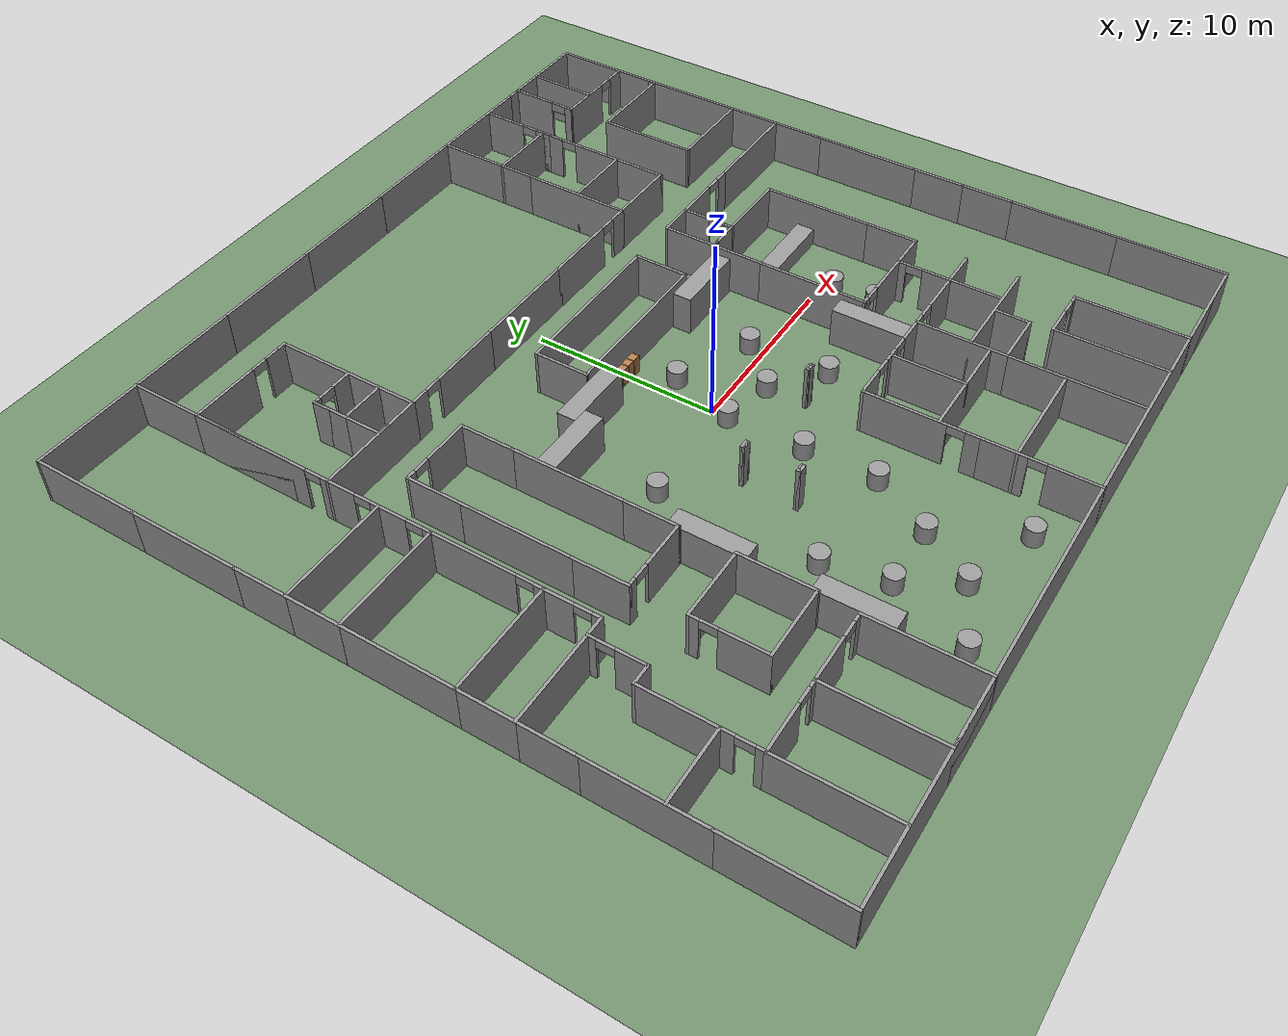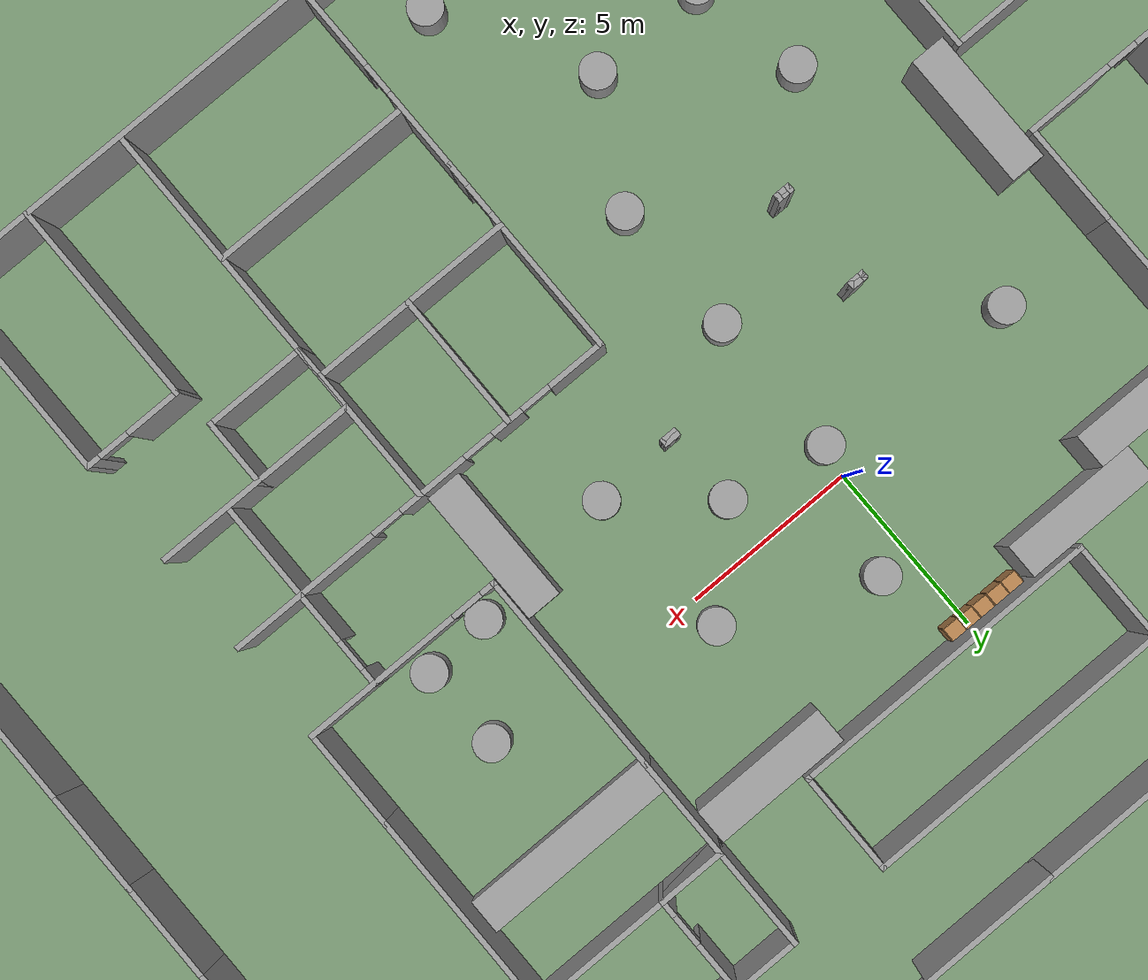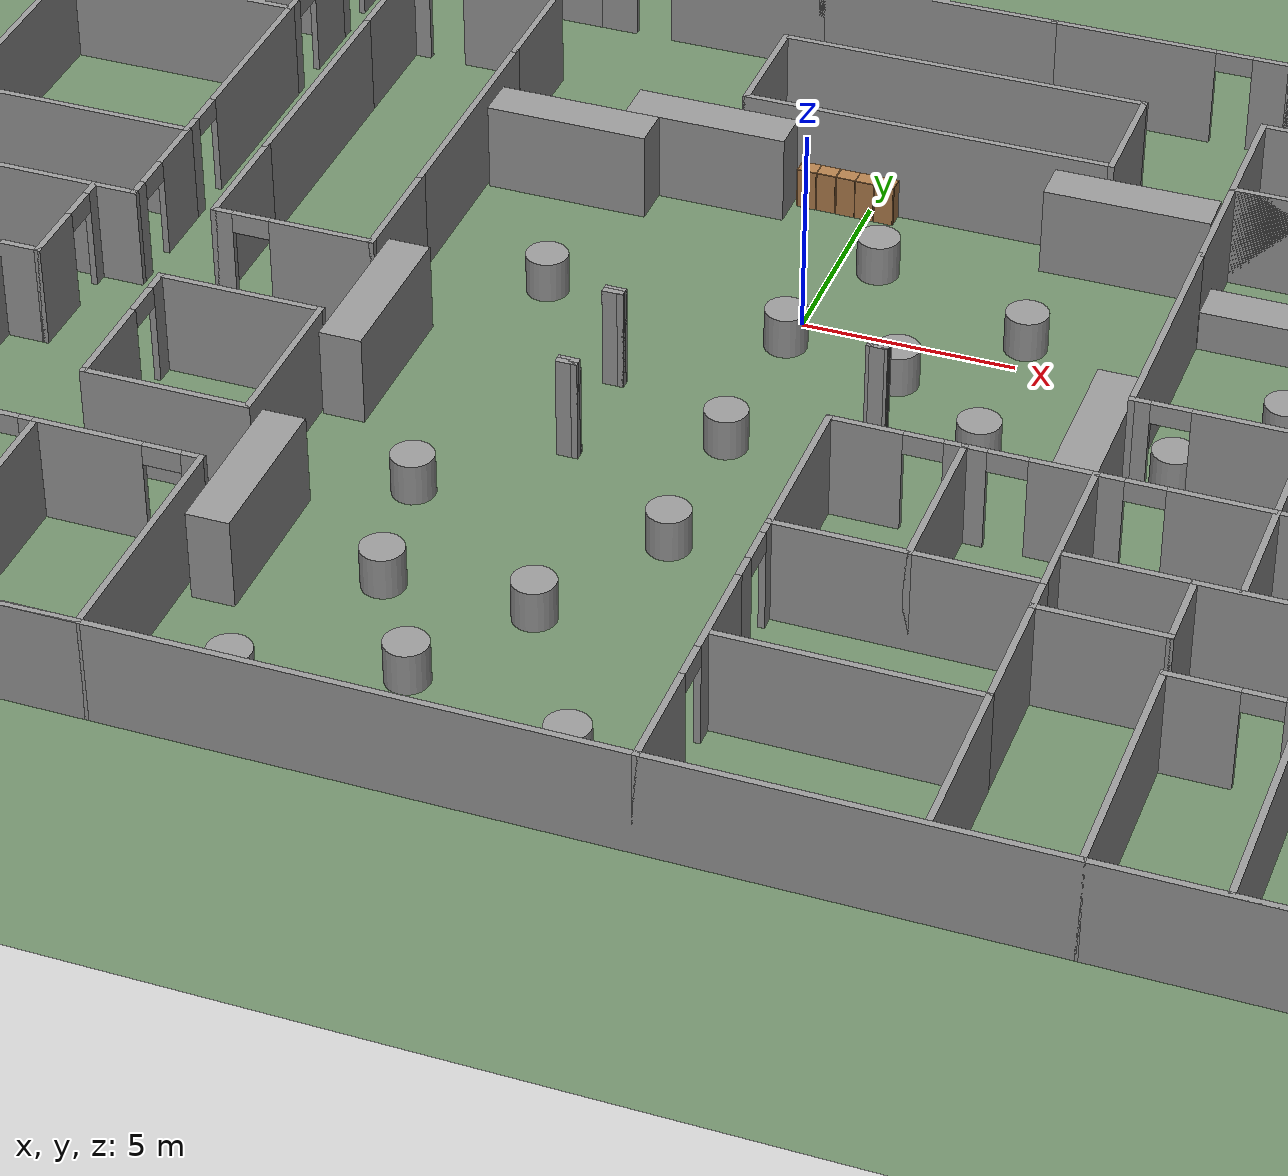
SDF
<sdf version="1.7">
 <world name="default">
  <light name="sun" type="directional">
   <pose>0 0 10 0 -0 0</pose>
   <diffuse>0.8 0.8 0.8 1</diffuse>
   <specular>0.2 0.2 0.2 1</specular>
   <attenuation>
    <range>1000</range>
    <constant>0.9</constant>
    <linear>0.01</linear>
    <quadratic>0.001</quadratic>
   </attenuation>
   <direction>-0.5 0.1 -0.9</direction>
   <spot><inner_angle>0</inner_angle><outer_angle>0</outer_angle><falloff>0</falloff></spot>
  </light>
  <scene>
   <sky><clouds><speed>12</speed></clouds><ambient>0.43 0.45 0.57 1</ambient></sky>
   <background>0.43 0.45 0.57 1</background>
   <ambient>0.4 0.4 0.4 1</ambient>
   <shadows>1</shadows>
  </scene>
  <model name="ground_plane">
   <static>1</static>
   <link name="link">
    <collision name="collision">
     <geometry><plane><normal>0 0 1</normal><size>600 600</size></plane></geometry>
     <surface>
      <contact><collide_bitmask>65535</collide_bitmask></contact>
      <friction><ode><mu>100</mu><mu2>50</mu2></ode></friction>
     </surface>
    </collision>
    <visual name="visual">
     <cast_shadows>0</cast_shadows>
     <geometry><plane><normal>0 0 1</normal><size>100 100</size></plane></geometry>
     <material><ambient>0.45 0.57 0.43 1</ambient><diffuse>0.45 0.57 0.43 1</diffuse></material>
    </visual>
   </link>
  </model>
  <gravity>0 0 -9.8</gravity>
  <magnetic_field>6e-06 2.3e-05 -4.2e-05</magnetic_field>
  <atmosphere type="adiabatic"/>
  <physics type="ode">
   <max_step_size>0.001</max_step_size>
   <real_time_factor>1</real_time_factor>
   <real_time_update_rate>1000</real_time_update_rate>
  </physics>
  <scene><ambient>0.4 0.4 0.4 1</ambient><background>0.7 0.7 0.7 1</background><shadows>1</shadows></scene>
  <spherical_coordinates>
   <surface_model>EARTH_WGS84</surface_model>
   <latitude_deg>0</latitude_deg>
   <longitude_deg>0</longitude_deg>
   <elevation>0</elevation>
   <heading_deg>0</heading_deg>
  </spherical_coordinates>
  <model name="unit_box">
   <pose>7.98131 -4.36327 1.08892 0 -0.000118 -1.56862</pose>
   <link name="link">
    <inertial>
     <mass>1</mass>
     <inertia>
      <ixx>0.166667</ixx>
      <ixy>0</ixy>
      <ixz>0</ixz>
      <iyy>0.166667</iyy>
      <iyz>0</iyz>
      <izz>0.166667</izz>
     </inertia>
    </inertial>
    <collision name="collision"><geometry><box><size>3.92499 1 2.1783</size></box></geometry></collision>
    <visual name="visual">
     <geometry><box><size>3.92499 1 2.1783</size></box></geometry>
     <material>
      <script><name>Gazebo/Grey</name><uri>file://media/materials/scripts/gazebo.material</uri></script>
     </material>
    </visual>
   </link>
  </model>
  <model name="unit_box_clone">
   <pose>6.38296 4.44486 1.08892 0 -0.000118 0.002103</pose>
   <link name="link">
    <inertial>
     <mass>1</mass>
     <inertia>
      <ixx>0.166667</ixx>
      <ixy>0</ixy>
      <ixz>0</ixz>
      <iyy>0.166667</iyy>
      <iyz>0</iyz>
      <izz>0.166667</izz>
     </inertia>
    </inertial>
    <collision name="collision"><geometry><box><size>3.92499 1 2.1783</size></box></geometry></collision>
    <visual name="visual">
     <geometry><box><size>3.92499 1 2.1783</size></box></geometry>
     <material>
      <script><name>Gazebo/Grey</name><uri>file://media/materials/scripts/gazebo.material</uri></script>
     </material>
    </visual>
   </link>
  </model>
  <model name="unit_box_clone_clone">
   <pose>-3.79139 4.41905 1.08892 0 0.000118 -0.002216</pose>
   <link name="link">
    <inertial>
     <mass>1</mass>
     <inertia>
      <ixx>0.166667</ixx>
      <ixy>0</ixy>
      <ixz>0</ixz>
      <iyy>0.166667</iyy>
      <iyz>0</iyz>
      <izz>0.166667</izz>
     </inertia>
    </inertial>
    <collision name="collision"><geometry><box><size>3.92499 1 2.1783</size></box></geometry></collision>
    <visual name="visual">
     <geometry><box><size>3.92499 1 2.1783</size></box></geometry>
     <material>
      <script><name>Gazebo/Grey</name><uri>file://media/materials/scripts/gazebo.material</uri></script>
     </material>
    </visual>
   </link>
  </model>
  <model name="unit_box_clone_clone_clone">
   <pose>-6.88429 3.42566 1.08892 0 -0.000118 -0.002201</pose>
   <link name="link">
    <inertial>
     <mass>1</mass>
     <inertia>
      <ixx>0.166667</ixx>
      <ixy>0</ixy>
      <ixz>0</ixz>
      <iyy>0.166667</iyy>
      <iyz>0</iyz>
      <izz>0.166667</izz>
     </inertia>
    </inertial>
    <collision name="collision"><geometry><box><size>3.92499 1 2.1783</size></box></geometry></collision>
    <visual name="visual">
     <geometry><box><size>3.92499 1 2.1783</size></box></geometry>
     <material>
      <script><name>Gazebo/Grey</name><uri>file://media/materials/scripts/gazebo.material</uri></script>
     </material>
    </visual>
   </link>
  </model>
  <model name="unit_box_clone_0">
   <pose>-8.33783 -11.9113 1.08892 0 -0.000118 -1.56902</pose>
   <link name="link">
    <inertial>
     <mass>1</mass>
     <inertia>
      <ixx>0.166667</ixx>
      <ixy>0</ixy>
      <ixz>0</ixz>
      <iyy>0.166667</iyy>
      <iyz>0</iyz>
      <izz>0.166667</izz>
     </inertia>
    </inertial>
    <collision name="collision"><geometry><box><size>3.92499 1 2.1783</size></box></geometry></collision>
    <visual name="visual">
     <geometry><box><size>3.92499 1 2.1783</size></box></geometry>
     <material>
      <script><name>Gazebo/Grey</name><uri>file://media/materials/scripts/gazebo.material</uri></script>
     </material>
    </visual>
   </link>
  </model>
  <model name="unit_box_clone_1">
   <pose>-8.36946 -4.94384 1.08892 0 0.000118 -1.57207</pose>
   <link name="link">
    <inertial>
     <mass>1</mass>
     <inertia>
      <ixx>0.166667</ixx>
      <ixy>0</ixy>
      <ixz>0</ixz>
      <iyy>0.166667</iyy>
      <iyz>0</iyz>
      <izz>0.166667</izz>
     </inertia>
    </inertial>
    <collision name="collision"><geometry><box><size>3.92499 1 2.1783</size></box></geometry></collision>
    <visual name="visual">
     <geometry><box><size>3.92499 1 2.1783</size></box></geometry>
     <material>
      <script><name>Gazebo/Grey</name><uri>file://media/materials/scripts/gazebo.material</uri></script>
     </material>
    </visual>
   </link>
  </model>
  <model name="unit_cylinder">
   <pose>-0.092764 -5.01656 0.499994 4e-06 -2e-06 0</pose>
   <link name="link">
    <inertial>
     <mass>1</mass>
     <inertia><ixx>0.145833</ixx><ixy>0</ixy><ixz>0</ixz><iyy>0.145833</iyy><iyz>0</iyz><izz>0.125</izz></inertia>
    </inertial>
    <collision name="collision">
     <geometry><cylinder><radius>0.5</radius><length>1</length></cylinder></geometry>
    </collision>
    <visual name="visual">
     <geometry><cylinder><radius>0.5</radius><length>1</length></cylinder></geometry>
     <material>
      <script><name>Gazebo/Grey</name><uri>file://media/materials/scripts/gazebo.material</uri></script>
     </material>
    </visual>
   </link>
  </model>
  <model name="unit_cylinder_0">
   <pose>-0.106654 -0.917945 0.499997 -1e-06 1e-06 0</pose>
   <link name="link">
    <inertial>
     <mass>1</mass>
     <inertia><ixx>0.145833</ixx><ixy>0</ixy><ixz>0</ixz><iyy>0.145833</iyy><iyz>0</iyz><izz>0.125</izz></inertia>
    </inertial>
    <collision name="collision">
     <geometry><cylinder><radius>0.5</radius><length>1</length></cylinder></geometry>
    </collision>
    <visual name="visual">
     <geometry><cylinder><radius>0.5</radius><length>1</length></cylinder></geometry>
     <material>
      <script><name>Gazebo/Grey</name><uri>file://media/materials/scripts/gazebo.material</uri></script>
     </material>
    </visual>
   </link>
  </model>
  <model name="unit_cylinder_1">
   <pose>5.20322 -3.53373 0.499994 4e-06 -2e-06 0</pose>
   <link name="link">
    <inertial>
     <mass>1</mass>
     <inertia><ixx>0.145833</ixx><ixy>0</ixy><ixz>0</ixz><iyy>0.145833</iyy><iyz>0</iyz><izz>0.125</izz></inertia>
    </inertial>
    <collision name="collision">
     <geometry><cylinder><radius>0.5</radius><length>1</length></cylinder></geometry>
    </collision>
    <visual name="visual">
     <geometry><cylinder><radius>0.5</radius><length>1</length></cylinder></geometry>
     <material>
      <script><name>Gazebo/Grey</name><uri>file://media/materials/scripts/gazebo.material</uri></script>
     </material>
    </visual>
   </link>
  </model>
  <model name="unit_cylinder_2">
   <pose>5.01639 0.814958 0.5 0 -0 0</pose>
   <link name="link">
    <inertial>
     <mass>1</mass>
     <inertia><ixx>0.145833</ixx><ixy>0</ixy><ixz>0</ixz><iyy>0.145833</iyy><iyz>0</iyz><izz>0.125</izz></inertia>
    </inertial>
    <collision name="collision">
     <geometry><cylinder><radius>0.5</radius><length>1</length></cylinder></geometry>
    </collision>
    <visual name="visual">
     <geometry><cylinder><radius>0.5</radius><length>1</length></cylinder></geometry>
     <material>
      <script><name>Gazebo/Grey</name><uri>file://media/materials/scripts/gazebo.material</uri></script>
     </material>
    </visual>
   </link>
  </model>
  <model name="unit_cylinder_3">
   <pose>-0.035798 -8.83549 0.499996 -3e-06 1e-06 0</pose>
   <link name="link">
    <inertial>
     <mass>1</mass>
     <inertia><ixx>0.145833</ixx><ixy>0</ixy><ixz>0</ixz><iyy>0.145833</iyy><iyz>0</iyz><izz>0.125</izz></inertia>
    </inertial>
    <collision name="collision">
     <geometry><cylinder><radius>0.5</radius><length>1</length></cylinder></geometry>
    </collision>
    <visual name="visual">
     <geometry><cylinder><radius>0.5</radius><length>1</length></cylinder></geometry>
     <material>
      <script><name>Gazebo/Grey</name><uri>file://media/materials/scripts/gazebo.material</uri></script>
     </material>
    </visual>
   </link>
  </model>
  <model name="unit_cylinder_4">
   <pose>-5.88047 -8.86762 0.499996 -3e-06 1e-06 0</pose>
   <link name="link">
    <inertial>
     <mass>1</mass>
     <inertia><ixx>0.145833</ixx><ixy>0</ixy><ixz>0</ixz><iyy>0.145833</iyy><iyz>0</iyz><izz>0.125</izz></inertia>
    </inertial>
    <collision name="collision">
     <geometry><cylinder><radius>0.5</radius><length>1</length></cylinder></geometry>
    </collision>
    <visual name="visual">
     <geometry><cylinder><radius>0.5</radius><length>1</length></cylinder></geometry>
     <material>
      <script><name>Gazebo/Grey</name><uri>file://media/materials/scripts/gazebo.material</uri></script>
     </material>
    </visual>
   </link>
  </model>
  <model name="unit_cylinder_5">
   <pose>-5.96407 -0.674477 0.499996 -3e-06 1e-06 0</pose>
   <link name="link">
    <inertial>
     <mass>1</mass>
     <inertia><ixx>0.145833</ixx><ixy>0</ixy><ixz>0</ixz><iyy>0.145833</iyy><iyz>0</iyz><izz>0.125</izz></inertia>
    </inertial>
    <collision name="collision">
     <geometry><cylinder><radius>0.5</radius><length>1</length></cylinder></geometry>
    </collision>
    <visual name="visual">
     <geometry><cylinder><radius>0.5</radius><length>1</length></cylinder></geometry>
     <material>
      <script><name>Gazebo/Grey</name><uri>file://media/materials/scripts/gazebo.material</uri></script>
     </material>
    </visual>
   </link>
  </model>
  <model name="unit_cylinder_6">
   <pose>-5.21652 -12.1055 0.499997 3e-06 -2e-06 0</pose>
   <link name="link">
    <inertial>
     <mass>1</mass>
     <inertia><ixx>0.145833</ixx><ixy>0</ixy><ixz>0</ixz><iyy>0.145833</iyy><iyz>0</iyz><izz>0.125</izz></inertia>
    </inertial>
    <collision name="collision">
     <geometry><cylinder><radius>0.5</radius><length>1</length></cylinder></geometry>
    </collision>
    <visual name="visual">
     <geometry><cylinder><radius>0.5</radius><length>1</length></cylinder></geometry>
     <material>
      <script><name>Gazebo/Grey</name><uri>file://media/materials/scripts/gazebo.material</uri></script>
     </material>
    </visual>
   </link>
  </model>
  <model name="unit_cylinder_7">
   <pose>-1.82971 -12.0558 0.499996 -3e-06 1e-06 0</pose>
   <link name="link">
    <inertial>
     <mass>1</mass>
     <inertia><ixx>0.145833</ixx><ixy>0</ixy><ixz>0</ixz><iyy>0.145833</iyy><iyz>0</iyz><izz>0.125</izz></inertia>
    </inertial>
    <collision name="collision">
     <geometry><cylinder><radius>0.5</radius><length>1</length></cylinder></geometry>
    </collision>
    <visual name="visual">
     <geometry><cylinder><radius>0.5</radius><length>1</length></cylinder></geometry>
     <material>
      <script><name>Gazebo/Grey</name><uri>file://media/materials/scripts/gazebo.material</uri></script>
     </material>
    </visual>
   </link>
  </model>
  <model name="unit_cylinder_8">
   <pose>-3.52298 -14.8483 0.499999 0 -0 0</pose>
   <link name="link">
    <inertial>
     <mass>1</mass>
     <inertia><ixx>0.145833</ixx><ixy>0</ixy><ixz>0</ixz><iyy>0.145833</iyy><iyz>0</iyz><izz>0.125</izz></inertia>
    </inertial>
    <collision name="collision">
     <geometry><cylinder><radius>0.5</radius><length>1</length></cylinder></geometry>
    </collision>
    <visual name="visual">
     <geometry><cylinder><radius>0.5</radius><length>1</length></cylinder></geometry>
     <material>
      <script><name>Gazebo/Grey</name><uri>file://media/materials/scripts/gazebo.material</uri></script>
     </material>
    </visual>
   </link>
  </model>
  <model name="unit_cylinder_9">
   <pose>0.507553 -16.1833 0.499994 -4e-06 -2e-06 -0</pose>
   <link name="link">
    <inertial>
     <mass>1</mass>
     <inertia><ixx>0.145833</ixx><ixy>0</ixy><ixz>0</ixz><iyy>0.145833</iyy><iyz>0</iyz><izz>0.125</izz></inertia>
    </inertial>
    <collision name="collision">
     <geometry><cylinder><radius>0.5</radius><length>1</length></cylinder></geometry>
    </collision>
    <visual name="visual">
     <geometry><cylinder><radius>0.5</radius><length>1</length></cylinder></geometry>
     <material>
      <script><name>Gazebo/Grey</name><uri>file://media/materials/scripts/gazebo.material</uri></script>
     </material>
    </visual>
   </link>
  </model>
  <model name="unit_cylinder_10">
   <pose>-6.8017 -16.2883 0.499999 0 -0 0</pose>
   <link name="link">
    <inertial>
     <mass>1</mass>
     <inertia><ixx>0.145833</ixx><ixy>0</ixy><ixz>0</ixz><iyy>0.145833</iyy><iyz>0</iyz><izz>0.125</izz></inertia>
    </inertial>
    <collision name="collision">
     <geometry><cylinder><radius>0.5</radius><length>1</length></cylinder></geometry>
    </collision>
    <visual name="visual">
     <geometry><cylinder><radius>0.5</radius><length>1</length></cylinder></geometry>
     <material>
      <script><name>Gazebo/Grey</name><uri>file://media/materials/scripts/gazebo.material</uri></script>
     </material>
    </visual>
   </link>
  </model>
  <model name="myhal_V3_2">
   <link name="Wall_319">
    <pose>20.475 17.4 0 0 0 -1.5708</pose>
    <visual name="Wall_319_Visual">
     <pose>0 0 1.25 0 -0 0</pose>
     <geometry><box><size>6 0.15 2.5</size></box></geometry>
     <material>
      <script><uri>file://media/materials/scripts/gazebo.material</uri><name>Gazebo/Grey</name></script>
      <ambient>1 1 1 1</ambient>
      <shader type="pixel"/>
     </material>
     <meta><layer>0</layer></meta>
    </visual>
    <collision name="Wall_319_Collision">
     <pose>0 0 1.25 0 -0 0</pose>
     <geometry><box><size>6 0.15 2.5</size></box></geometry>
     <surface>
      <friction>
       <ode><mu>1</mu><mu2>1</mu2><fdir1>0 0 0</fdir1><slip1>0</slip1><slip2>0</slip2></ode>
       <torsional>
        <coefficient>1</coefficient>
        <patch_radius>0</patch_radius>
        <surface_radius>0</surface_radius>
        <use_patch_radius>1</use_patch_radius>
        <ode><slip>0</slip></ode>
       </torsional>
      </friction>
      <bounce><restitution_coefficient>0</restitution_coefficient><threshold>1e+06</threshold></bounce>
      <contact>
       <collide_without_contact>0</collide_without_contact>
       <collide_without_contact_bitmask>1</collide_without_contact_bitmask>
       <collide_bitmask>1</collide_bitmask>
       <ode>
        <soft_cfm>0</soft_cfm>
        <soft_erp>0.2</soft_erp>
        <kp>1e+13</kp>
        <kd>1</kd>
        <max_vel>0.01</max_vel>
        <min_depth>0</min_depth>
       </ode>
       <bullet>
        <split_impulse>1</split_impulse>
        <split_impulse_penetration_threshold>-0.01</split_impulse_penetration_threshold>
        <soft_cfm>0</soft_cfm>
        <soft_erp>0.2</soft_erp>
        <kp>1e+13</kp>
        <kd>1</kd>
       </bullet>
      </contact>
     </surface>
    </collision>
   </link>
   <link name="Wall_321">
    <pose>20.475 11.55 0 0 0 -1.5708</pose>
    <visual name="Wall_321_Visual">
     <pose>0 0 1.25 0 -0 0</pose>
     <geometry><box><size>6 0.15 2.5</size></box></geometry>
     <material>
      <script><uri>file://media/materials/scripts/gazebo.material</uri><name>Gazebo/Grey</name></script>
      <ambient>1 1 1 1</ambient>
      <shader type="pixel"/>
     </material>
     <meta><layer>0</layer></meta>
    </visual>
    <collision name="Wall_321_Collision">
     <pose>0 0 1.25 0 -0 0</pose>
     <geometry><box><size>6 0.15 2.5</size></box></geometry>
     <surface>
      <friction>
       <ode><mu>1</mu><mu2>1</mu2><fdir1>0 0 0</fdir1><slip1>0</slip1><slip2>0</slip2></ode>
       <torsional>
        <coefficient>1</coefficient>
        <patch_radius>0</patch_radius>
        <surface_radius>0</surface_radius>
        <use_patch_radius>1</use_patch_radius>
        <ode><slip>0</slip></ode>
       </torsional>
      </friction>
      <bounce><restitution_coefficient>0</restitution_coefficient><threshold>1e+06</threshold></bounce>
      <contact>
       <collide_without_contact>0</collide_without_contact>
       <collide_without_contact_bitmask>1</collide_without_contact_bitmask>
       <collide_bitmask>1</collide_bitmask>
       <ode>
        <soft_cfm>0</soft_cfm>
        <soft_erp>0.2</soft_erp>
        <kp>1e+13</kp>
        <kd>1</kd>
        <max_vel>0.01</max_vel>
        <min_depth>0</min_depth>
       </ode>
       <bullet>
        <split_impulse>1</split_impulse>
        <split_impulse_penetration_threshold>-0.01</split_impulse_penetration_threshold>
        <soft_cfm>0</soft_cfm>
        <soft_erp>0.2</soft_erp>
        <kp>1e+13</kp>
        <kd>1</kd>
       </bullet>
      </contact>
     </surface>
    </collision>
   </link>
   <link name="Wall_323">
    <pose>20.475 7.2 0 0 0 -1.5708</pose>
    <visual name="Wall_323_Visual">
     <pose>0 0 1.25 0 -0 0</pose>
     <geometry><box><size>3 0.15 2.5</size></box></geometry>
     <material>
      <script><uri>file://media/materials/scripts/gazebo.material</uri><name>Gazebo/Grey</name></script>
      <ambient>1 1 1 1</ambient>
      <shader type="pixel"/>
     </material>
     <meta><layer>0</layer></meta>
    </visual>
    <collision name="Wall_323_Collision">
     <pose>0 0 1.25 0 -0 0</pose>
     <geometry><box><size>3 0.15 2.5</size></box></geometry>
     <surface>
      <friction>
       <ode><mu>1</mu><mu2>1</mu2><fdir1>0 0 0</fdir1><slip1>0</slip1><slip2>0</slip2></ode>
       <torsional>
        <coefficient>1</coefficient>
        <patch_radius>0</patch_radius>
        <surface_radius>0</surface_radius>
        <use_patch_radius>1</use_patch_radius>
        <ode><slip>0</slip></ode>
       </torsional>
      </friction>
      <bounce><restitution_coefficient>0</restitution_coefficient><threshold>1e+06</threshold></bounce>
      <contact>
       <collide_without_contact>0</collide_without_contact>
       <collide_without_contact_bitmask>1</collide_without_contact_bitmask>
       <collide_bitmask>1</collide_bitmask>
       <ode>
        <soft_cfm>0</soft_cfm>
        <soft_erp>0.2</soft_erp>
        <kp>1e+13</kp>
        <kd>1</kd>
        <max_vel>0.01</max_vel>
        <min_depth>0</min_depth>
       </ode>
       <bullet>
        <split_impulse>1</split_impulse>
        <split_impulse_penetration_threshold>-0.01</split_impulse_penetration_threshold>
        <soft_cfm>0</soft_cfm>
        <soft_erp>0.2</soft_erp>
        <kp>1e+13</kp>
        <kd>1</kd>
       </bullet>
      </contact>
     </surface>
    </collision>
   </link>
   <link name="Wall_324">
    <pose>20.475 4.35 0 0 0 -1.5708</pose>
    <visual name="Wall_324_Visual">
     <pose>0 0 1.25 0 -0 0</pose>
     <geometry><box><size>3 0.15 2.5</size></box></geometry>
     <material>
      <script><uri>file://media/materials/scripts/gazebo.material</uri><name>Gazebo/Grey</name></script>
      <ambient>1 1 1 1</ambient>
      <shader type="pixel"/>
     </material>
     <meta><layer>0</layer></meta>
    </visual>
    <collision name="Wall_324_Collision">
     <pose>0 0 1.25 0 -0 0</pose>
     <geometry><box><size>3 0.15 2.5</size></box></geometry>
     <surface>
      <friction>
       <ode><mu>1</mu><mu2>1</mu2><fdir1>0 0 0</fdir1><slip1>0</slip1><slip2>0</slip2></ode>
       <torsional>
        <coefficient>1</coefficient>
        <patch_radius>0</patch_radius>
        <surface_radius>0</surface_radius>
        <use_patch_radius>1</use_patch_radius>
        <ode><slip>0</slip></ode>
       </torsional>
      </friction>
      <bounce><restitution_coefficient>0</restitution_coefficient><threshold>1e+06</threshold></bounce>
      <contact>
       <collide_without_contact>0</collide_without_contact>
       <collide_without_contact_bitmask>1</collide_without_contact_bitmask>
       <collide_bitmask>1</collide_bitmask>
       <ode>
        <soft_cfm>0</soft_cfm>
        <soft_erp>0.2</soft_erp>
        <kp>1e+13</kp>
        <kd>1</kd>
        <max_vel>0.01</max_vel>
        <min_depth>0</min_depth>
       </ode>
       <bullet>
        <split_impulse>1</split_impulse>
        <split_impulse_penetration_threshold>-0.01</split_impulse_penetration_threshold>
        <soft_cfm>0</soft_cfm>
        <soft_erp>0.2</soft_erp>
        <kp>1e+13</kp>
        <kd>1</kd>
       </bullet>
      </contact>
     </surface>
    </collision>
   </link>
   <link name="Wall_326">
    <pose>20.475 0 0 0 0 -1.5708</pose>
    <visual name="Wall_326_Visual">
     <pose>0 0 1.25 0 -0 0</pose>
     <geometry><box><size>6 0.15 2.5</size></box></geometry>
     <material>
      <script><uri>file://media/materials/scripts/gazebo.material</uri><name>Gazebo/Grey</name></script>
      <ambient>1 1 1 1</ambient>
      <shader type="pixel"/>
     </material>
     <meta><layer>0</layer></meta>
    </visual>
    <collision name="Wall_326_Collision">
     <pose>0 0 1.25 0 -0 0</pose>
     <geometry><box><size>6 0.15 2.5</size></box></geometry>
     <surface>
      <friction>
       <ode><mu>1</mu><mu2>1</mu2><fdir1>0 0 0</fdir1><slip1>0</slip1><slip2>0</slip2></ode>
       <torsional>
        <coefficient>1</coefficient>
        <patch_radius>0</patch_radius>
        <surface_radius>0</surface_radius>
        <use_patch_radius>1</use_patch_radius>
        <ode><slip>0</slip></ode>
       </torsional>
      </friction>
      <bounce><restitution_coefficient>0</restitution_coefficient><threshold>1e+06</threshold></bounce>
      <contact>
       <collide_without_contact>0</collide_without_contact>
       <collide_without_contact_bitmask>1</collide_without_contact_bitmask>
       <collide_bitmask>1</collide_bitmask>
       <ode>
        <soft_cfm>0</soft_cfm>
        <soft_erp>0.2</soft_erp>
        <kp>1e+13</kp>
        <kd>1</kd>
        <max_vel>0.01</max_vel>
        <min_depth>0</min_depth>
       </ode>
       <bullet>
        <split_impulse>1</split_impulse>
        <split_impulse_penetration_threshold>-0.01</split_impulse_penetration_threshold>
        <soft_cfm>0</soft_cfm>
        <soft_erp>0.2</soft_erp>
        <kp>1e+13</kp>
        <kd>1</kd>
       </bullet>
      </contact>
     </surface>
    </collision>
   </link>
   <link name="Wall_327">
    <pose>20.475 -4.35 0 0 0 -1.5708</pose>
    <visual name="Wall_327_Visual">
     <pose>0 0 1.25 0 -0 0</pose>
     <geometry><box><size>3 0.15 2.5</size></box></geometry>
     <material>
      <script><uri>file://media/materials/scripts/gazebo.material</uri><name>Gazebo/Grey</name></script>
      <ambient>1 1 1 1</ambient>
      <shader type="pixel"/>
     </material>
     <meta><layer>0</layer></meta>
    </visual>
    <collision name="Wall_327_Collision">
     <pose>0 0 1.25 0 -0 0</pose>
     <geometry><box><size>3 0.15 2.5</size></box></geometry>
     <surface>
      <friction>
       <ode><mu>1</mu><mu2>1</mu2><fdir1>0 0 0</fdir1><slip1>0</slip1><slip2>0</slip2></ode>
       <torsional>
        <coefficient>1</coefficient>
        <patch_radius>0</patch_radius>
        <surface_radius>0</surface_radius>
        <use_patch_radius>1</use_patch_radius>
        <ode><slip>0</slip></ode>
       </torsional>
      </friction>
      <bounce><restitution_coefficient>0</restitution_coefficient><threshold>1e+06</threshold></bounce>
      <contact>
       <collide_without_contact>0</collide_without_contact>
       <collide_without_contact_bitmask>1</collide_without_contact_bitmask>
       <collide_bitmask>1</collide_bitmask>
       <ode>
        <soft_cfm>0</soft_cfm>
        <soft_erp>0.2</soft_erp>
        <kp>1e+13</kp>
        <kd>1</kd>
        <max_vel>0.01</max_vel>
        <min_depth>0</min_depth>
       </ode>
       <bullet>
        <split_impulse>1</split_impulse>
        <split_impulse_penetration_threshold>-0.01</split_impulse_penetration_threshold>
        <soft_cfm>0</soft_cfm>
        <soft_erp>0.2</soft_erp>
        <kp>1e+13</kp>
        <kd>1</kd>
       </bullet>
      </contact>
     </surface>
    </collision>
   </link>
   <link name="Wall_328">
    <pose>20.475 -7.2 0 0 0 -1.5708</pose>
    <visual name="Wall_328_Visual">
     <pose>0 0 1.25 0 -0 0</pose>
     <geometry><box><size>3 0.15 2.5</size></box></geometry>
     <material>
      <script><uri>file://media/materials/scripts/gazebo.material</uri><name>Gazebo/Grey</name></script>
      <ambient>1 1 1 1</ambient>
      <shader type="pixel"/>
     </material>
     <meta><layer>0</layer></meta>
    </visual>
    <collision name="Wall_328_Collision">
     <pose>0 0 1.25 0 -0 0</pose>
     <geometry><box><size>3 0.15 2.5</size></box></geometry>
     <surface>
      <friction>
       <ode><mu>1</mu><mu2>1</mu2><fdir1>0 0 0</fdir1><slip1>0</slip1><slip2>0</slip2></ode>
       <torsional>
        <coefficient>1</coefficient>
        <patch_radius>0</patch_radius>
        <surface_radius>0</surface_radius>
        <use_patch_radius>1</use_patch_radius>
        <ode><slip>0</slip></ode>
       </torsional>
      </friction>
      <bounce><restitution_coefficient>0</restitution_coefficient><threshold>1e+06</threshold></bounce>
      <contact>
       <collide_without_contact>0</collide_without_contact>
       <collide_without_contact_bitmask>1</collide_without_contact_bitmask>
       <collide_bitmask>1</collide_bitmask>
       <ode>
        <soft_cfm>0</soft_cfm>
        <soft_erp>0.2</soft_erp>
        <kp>1e+13</kp>
        <kd>1</kd>
        <max_vel>0.01</max_vel>
        <min_depth>0</min_depth>
       </ode>
       <bullet>
        <split_impulse>1</split_impulse>
        <split_impulse_penetration_threshold>-0.01</split_impulse_penetration_threshold>
        <soft_cfm>0</soft_cfm>
        <soft_erp>0.2</soft_erp>
        <kp>1e+13</kp>
        <kd>1</kd>
       </bullet>
      </contact>
     </surface>
    </collision>
   </link>
   <link name="Wall_330">
    <pose>20.475 -11.55 0 0 0 -1.5708</pose>
    <visual name="Wall_330_Visual">
     <pose>0 0 1.25 0 -0 0</pose>
     <geometry><box><size>6 0.15 2.5</size></box></geometry>
     <material>
      <script><uri>file://media/materials/scripts/gazebo.material</uri><name>Gazebo/Grey</name></script>
      <ambient>1 1 1 1</ambient>
      <shader type="pixel"/>
     </material>
     <meta><layer>0</layer></meta>
    </visual>
    <collision name="Wall_330_Collision">
     <pose>0 0 1.25 0 -0 0</pose>
     <geometry><box><size>6 0.15 2.5</size></box></geometry>
     <surface>
      <friction>
       <ode><mu>1</mu><mu2>1</mu2><fdir1>0 0 0</fdir1><slip1>0</slip1><slip2>0</slip2></ode>
       <torsional>
        <coefficient>1</coefficient>
        <patch_radius>0</patch_radius>
        <surface_radius>0</surface_radius>
        <use_patch_radius>1</use_patch_radius>
        <ode><slip>0</slip></ode>
       </torsional>
      </friction>
      <bounce><restitution_coefficient>0</restitution_coefficient><threshold>1e+06</threshold></bounce>
      <contact>
       <collide_without_contact>0</collide_without_contact>
       <collide_without_contact_bitmask>1</collide_without_contact_bitmask>
       <collide_bitmask>1</collide_bitmask>
       <ode>
        <soft_cfm>0</soft_cfm>
        <soft_erp>0.2</soft_erp>
        <kp>1e+13</kp>
        <kd>1</kd>
        <max_vel>0.01</max_vel>
        <min_depth>0</min_depth>
       </ode>
       <bullet>
        <split_impulse>1</split_impulse>
        <split_impulse_penetration_threshold>-0.01</split_impulse_penetration_threshold>
        <soft_cfm>0</soft_cfm>
        <soft_erp>0.2</soft_erp>
        <kp>1e+13</kp>
        <kd>1</kd>
       </bullet>
      </contact>
     </surface>
    </collision>
   </link>
   <link name="Wall_331">
    <pose>20.475 -17.4 0 0 0 -1.5708</pose>
    <visual name="Wall_331_Visual">
     <pose>0 0 1.25 0 -0 0</pose>
     <geometry><box><size>6 0.15 2.5</size></box></geometry>
     <material>
      <script><uri>file://media/materials/scripts/gazebo.material</uri><name>Gazebo/Grey</name></script>
      <ambient>1 1 1 1</ambient>
      <shader type="pixel"/>
     </material>
     <meta><layer>0</layer></meta>
    </visual>
    <collision name="Wall_331_Collision">
     <pose>0 0 1.25 0 -0 0</pose>
     <geometry><box><size>6 0.15 2.5</size></box></geometry>
     <surface>
      <friction>
       <ode><mu>1</mu><mu2>1</mu2><fdir1>0 0 0</fdir1><slip1>0</slip1><slip2>0</slip2></ode>
       <torsional>
        <coefficient>1</coefficient>
        <patch_radius>0</patch_radius>
        <surface_radius>0</surface_radius>
        <use_patch_radius>1</use_patch_radius>
        <ode><slip>0</slip></ode>
       </torsional>
      </friction>
      <bounce><restitution_coefficient>0</restitution_coefficient><threshold>1e+06</threshold></bounce>
      <contact>
       <collide_without_contact>0</collide_without_contact>
       <collide_without_contact_bitmask>1</collide_without_contact_bitmask>
       <collide_bitmask>1</collide_bitmask>
       <ode>
        <soft_cfm>0</soft_cfm>
        <soft_erp>0.2</soft_erp>
        <kp>1e+13</kp>
        <kd>1</kd>
        <max_vel>0.01</max_vel>
        <min_depth>0</min_depth>
       </ode>
       <bullet>
        <split_impulse>1</split_impulse>
        <split_impulse_penetration_threshold>-0.01</split_impulse_penetration_threshold>
        <soft_cfm>0</soft_cfm>
        <soft_erp>0.2</soft_erp>
        <kp>1e+13</kp>
        <kd>1</kd>
       </bullet>
      </contact>
     </surface>
    </collision>
   </link>
   <link name="Wall_333">
    <pose>17.55 20.325 0 0 -0 3.14159</pose>
    <visual name="Wall_333_Visual">
     <pose>0 0 1.25 0 -0 0</pose>
     <geometry><box><size>6 0.15 2.5</size></box></geometry>
     <material>
      <script><uri>file://media/materials/scripts/gazebo.material</uri><name>Gazebo/Grey</name></script>
      <ambient>1 1 1 1</ambient>
      <shader type="pixel"/>
     </material>
     <meta><layer>0</layer></meta>
    </visual>
    <collision name="Wall_333_Collision">
     <pose>0 0 1.25 0 -0 0</pose>
     <geometry><box><size>6 0.15 2.5</size></box></geometry>
     <surface>
      <friction>
       <ode><mu>1</mu><mu2>1</mu2><fdir1>0 0 0</fdir1><slip1>0</slip1><slip2>0</slip2></ode>
       <torsional>
        <coefficient>1</coefficient>
        <patch_radius>0</patch_radius>
        <surface_radius>0</surface_radius>
        <use_patch_radius>1</use_patch_radius>
        <ode><slip>0</slip></ode>
       </torsional>
      </friction>
      <bounce><restitution_coefficient>0</restitution_coefficient><threshold>1e+06</threshold></bounce>
      <contact>
       <collide_without_contact>0</collide_without_contact>
       <collide_without_contact_bitmask>1</collide_without_contact_bitmask>
       <collide_bitmask>1</collide_bitmask>
       <ode>
        <soft_cfm>0</soft_cfm>
        <soft_erp>0.2</soft_erp>
        <kp>1e+13</kp>
        <kd>1</kd>
        <max_vel>0.01</max_vel>
        <min_depth>0</min_depth>
       </ode>
       <bullet>
        <split_impulse>1</split_impulse>
        <split_impulse_penetration_threshold>-0.01</split_impulse_penetration_threshold>
        <soft_cfm>0</soft_cfm>
        <soft_erp>0.2</soft_erp>
        <kp>1e+13</kp>
        <kd>1</kd>
       </bullet>
      </contact>
     </surface>
    </collision>
   </link>
   <link name="Wall_334">
    <pose>11.7 20.325 0 0 -0 3.14159</pose>
    <visual name="Wall_334_Visual">
     <pose>0 0 1.25 0 -0 0</pose>
     <geometry><box><size>6 0.15 2.5</size></box></geometry>
     <material>
      <script><uri>file://media/materials/scripts/gazebo.material</uri><name>Gazebo/Grey</name></script>
      <ambient>1 1 1 1</ambient>
      <shader type="pixel"/>
     </material>
     <meta><layer>0</layer></meta>
    </visual>
    <collision name="Wall_334_Collision">
     <pose>0 0 1.25 0 -0 0</pose>
     <geometry><box><size>6 0.15 2.5</size></box></geometry>
     <surface>
      <friction>
       <ode><mu>1</mu><mu2>1</mu2><fdir1>0 0 0</fdir1><slip1>0</slip1><slip2>0</slip2></ode>
       <torsional>
        <coefficient>1</coefficient>
        <patch_radius>0</patch_radius>
        <surface_radius>0</surface_radius>
        <use_patch_radius>1</use_patch_radius>
        <ode><slip>0</slip></ode>
       </torsional>
      </friction>
      <bounce><restitution_coefficient>0</restitution_coefficient><threshold>1e+06</threshold></bounce>
      <contact>
       <collide_without_contact>0</collide_without_contact>
       <collide_without_contact_bitmask>1</collide_without_contact_bitmask>
       <collide_bitmask>1</collide_bitmask>
       <ode>
        <soft_cfm>0</soft_cfm>
        <soft_erp>0.2</soft_erp>
        <kp>1e+13</kp>
        <kd>1</kd>
        <max_vel>0.01</max_vel>
        <min_depth>0</min_depth>
       </ode>
       <bullet>
        <split_impulse>1</split_impulse>
        <split_impulse_penetration_threshold>-0.01</split_impulse_penetration_threshold>
        <soft_cfm>0</soft_cfm>
        <soft_erp>0.2</soft_erp>
        <kp>1e+13</kp>
        <kd>1</kd>
       </bullet>
      </contact>
     </surface>
    </collision>
   </link>
   <link name="Wall_335">
    <pose>5.85 20.325 0 0 -0 3.14159</pose>
    <visual name="Wall_335_Visual">
     <pose>0 0 1.25 0 -0 0</pose>
     <geometry><box><size>6 0.15 2.5</size></box></geometry>
     <material>
      <script><uri>file://media/materials/scripts/gazebo.material</uri><name>Gazebo/Grey</name></script>
      <ambient>1 1 1 1</ambient>
      <shader type="pixel"/>
     </material>
     <meta><layer>0</layer></meta>
    </visual>
    <collision name="Wall_335_Collision">
     <pose>0 0 1.25 0 -0 0</pose>
     <geometry><box><size>6 0.15 2.5</size></box></geometry>
     <surface>
      <friction>
       <ode><mu>1</mu><mu2>1</mu2><fdir1>0 0 0</fdir1><slip1>0</slip1><slip2>0</slip2></ode>
       <torsional>
        <coefficient>1</coefficient>
        <patch_radius>0</patch_radius>
        <surface_radius>0</surface_radius>
        <use_patch_radius>1</use_patch_radius>
        <ode><slip>0</slip></ode>
       </torsional>
      </friction>
      <bounce><restitution_coefficient>0</restitution_coefficient><threshold>1e+06</threshold></bounce>
      <contact>
       <collide_without_contact>0</collide_without_contact>
       <collide_without_contact_bitmask>1</collide_without_contact_bitmask>
       <collide_bitmask>1</collide_bitmask>
       <ode>
        <soft_cfm>0</soft_cfm>
        <soft_erp>0.2</soft_erp>
        <kp>1e+13</kp>
        <kd>1</kd>
        <max_vel>0.01</max_vel>
        <min_depth>0</min_depth>
       </ode>
       <bullet>
        <split_impulse>1</split_impulse>
        <split_impulse_penetration_threshold>-0.01</split_impulse_penetration_threshold>
        <soft_cfm>0</soft_cfm>
        <soft_erp>0.2</soft_erp>
        <kp>1e+13</kp>
        <kd>1</kd>
       </bullet>
      </contact>
     </surface>
    </collision>
   </link>
   <link name="Wall_336">
    <pose>0 20.325 0 0 -0 3.14159</pose>
    <visual name="Wall_336_Visual">
     <pose>0 0 1.25 0 -0 0</pose>
     <geometry><box><size>6 0.15 2.5</size></box></geometry>
     <material>
      <script><uri>file://media/materials/scripts/gazebo.material</uri><name>Gazebo/Grey</name></script>
      <ambient>1 1 1 1</ambient>
      <shader type="pixel"/>
     </material>
     <meta><layer>0</layer></meta>
    </visual>
    <collision name="Wall_336_Collision">
     <pose>0 0 1.25 0 -0 0</pose>
     <geometry><box><size>6 0.15 2.5</size></box></geometry>
     <surface>
      <friction>
       <ode><mu>1</mu><mu2>1</mu2><fdir1>0 0 0</fdir1><slip1>0</slip1><slip2>0</slip2></ode>
       <torsional>
        <coefficient>1</coefficient>
        <patch_radius>0</patch_radius>
        <surface_radius>0</surface_radius>
        <use_patch_radius>1</use_patch_radius>
        <ode><slip>0</slip></ode>
       </torsional>
      </friction>
      <bounce><restitution_coefficient>0</restitution_coefficient><threshold>1e+06</threshold></bounce>
      <contact>
       <collide_without_contact>0</collide_without_contact>
       <collide_without_contact_bitmask>1</collide_without_contact_bitmask>
       <collide_bitmask>1</collide_bitmask>
       <ode>
        <soft_cfm>0</soft_cfm>
        <soft_erp>0.2</soft_erp>
        <kp>1e+13</kp>
        <kd>1</kd>
        <max_vel>0.01</max_vel>
        <min_depth>0</min_depth>
       </ode>
       <bullet>
        <split_impulse>1</split_impulse>
        <split_impulse_penetration_threshold>-0.01</split_impulse_penetration_threshold>
        <soft_cfm>0</soft_cfm>
        <soft_erp>0.2</soft_erp>
        <kp>1e+13</kp>
        <kd>1</kd>
       </bullet>
      </contact>
     </surface>
    </collision>
   </link>
   <link name="Wall_337">
    <pose>-5.85 20.325 0 0 -0 3.14159</pose>
    <visual name="Wall_337_Visual">
     <pose>0 0 1.25 0 -0 0</pose>
     <geometry><box><size>6 0.15 2.5</size></box></geometry>
     <material>
      <script><uri>file://media/materials/scripts/gazebo.material</uri><name>Gazebo/Grey</name></script>
      <ambient>1 1 1 1</ambient>
      <shader type="pixel"/>
     </material>
     <meta><layer>0</layer></meta>
    </visual>
    <collision name="Wall_337_Collision">
     <pose>0 0 1.25 0 -0 0</pose>
     <geometry><box><size>6 0.15 2.5</size></box></geometry>
     <surface>
      <friction>
       <ode><mu>1</mu><mu2>1</mu2><fdir1>0 0 0</fdir1><slip1>0</slip1><slip2>0</slip2></ode>
       <torsional>
        <coefficient>1</coefficient>
        <patch_radius>0</patch_radius>
        <surface_radius>0</surface_radius>
        <use_patch_radius>1</use_patch_radius>
        <ode><slip>0</slip></ode>
       </torsional>
      </friction>
      <bounce><restitution_coefficient>0</restitution_coefficient><threshold>1e+06</threshold></bounce>
      <contact>
       <collide_without_contact>0</collide_without_contact>
       <collide_without_contact_bitmask>1</collide_without_contact_bitmask>
       <collide_bitmask>1</collide_bitmask>
       <ode>
        <soft_cfm>0</soft_cfm>
        <soft_erp>0.2</soft_erp>
        <kp>1e+13</kp>
        <kd>1</kd>
        <max_vel>0.01</max_vel>
        <min_depth>0</min_depth>
       </ode>
       <bullet>
        <split_impulse>1</split_impulse>
        <split_impulse_penetration_threshold>-0.01</split_impulse_penetration_threshold>
        <soft_cfm>0</soft_cfm>
        <soft_erp>0.2</soft_erp>
        <kp>1e+13</kp>
        <kd>1</kd>
       </bullet>
      </contact>
     </surface>
    </collision>
   </link>
   <link name="Wall_338">
    <pose>-11.7 20.325 0 0 -0 3.14159</pose>
    <visual name="Wall_338_Visual">
     <pose>0 0 1.25 0 -0 0</pose>
     <geometry><box><size>6 0.15 2.5</size></box></geometry>
     <material>
      <script><uri>file://media/materials/scripts/gazebo.material</uri><name>Gazebo/Grey</name></script>
      <ambient>1 1 1 1</ambient>
      <shader type="pixel"/>
     </material>
     <meta><layer>0</layer></meta>
    </visual>
    <collision name="Wall_338_Collision">
     <pose>0 0 1.25 0 -0 0</pose>
     <geometry><box><size>6 0.15 2.5</size></box></geometry>
     <surface>
      <friction>
       <ode><mu>1</mu><mu2>1</mu2><fdir1>0 0 0</fdir1><slip1>0</slip1><slip2>0</slip2></ode>
       <torsional>
        <coefficient>1</coefficient>
        <patch_radius>0</patch_radius>
        <surface_radius>0</surface_radius>
        <use_patch_radius>1</use_patch_radius>
        <ode><slip>0</slip></ode>
       </torsional>
      </friction>
      <bounce><restitution_coefficient>0</restitution_coefficient><threshold>1e+06</threshold></bounce>
      <contact>
       <collide_without_contact>0</collide_without_contact>
       <collide_without_contact_bitmask>1</collide_without_contact_bitmask>
       <collide_bitmask>1</collide_bitmask>
       <ode>
        <soft_cfm>0</soft_cfm>
        <soft_erp>0.2</soft_erp>
        <kp>1e+13</kp>
        <kd>1</kd>
        <max_vel>0.01</max_vel>
        <min_depth>0</min_depth>
       </ode>
       <bullet>
        <split_impulse>1</split_impulse>
        <split_impulse_penetration_threshold>-0.01</split_impulse_penetration_threshold>
        <soft_cfm>0</soft_cfm>
        <soft_erp>0.2</soft_erp>
        <kp>1e+13</kp>
        <kd>1</kd>
       </bullet>
      </contact>
     </surface>
    </collision>
   </link>
   <link name="Wall_339">
    <pose>-17.55 20.325 0 0 -0 3.14159</pose>
    <visual name="Wall_339_Visual">
     <pose>0 0 1.25 0 -0 0</pose>
     <geometry><box><size>6 0.15 2.5</size></box></geometry>
     <material>
      <script><uri>file://media/materials/scripts/gazebo.material</uri><name>Gazebo/Grey</name></script>
      <ambient>1 1 1 1</ambient>
      <shader type="pixel"/>
     </material>
     <meta><layer>0</layer></meta>
    </visual>
    <collision name="Wall_339_Collision">
     <pose>0 0 1.25 0 -0 0</pose>
     <geometry><box><size>6 0.15 2.5</size></box></geometry>
     <surface>
      <friction>
       <ode><mu>1</mu><mu2>1</mu2><fdir1>0 0 0</fdir1><slip1>0</slip1><slip2>0</slip2></ode>
       <torsional>
        <coefficient>1</coefficient>
        <patch_radius>0</patch_radius>
        <surface_radius>0</surface_radius>
        <use_patch_radius>1</use_patch_radius>
        <ode><slip>0</slip></ode>
       </torsional>
      </friction>
      <bounce><restitution_coefficient>0</restitution_coefficient><threshold>1e+06</threshold></bounce>
      <contact>
       <collide_without_contact>0</collide_without_contact>
       <collide_without_contact_bitmask>1</collide_without_contact_bitmask>
       <collide_bitmask>1</collide_bitmask>
       <ode>
        <soft_cfm>0</soft_cfm>
        <soft_erp>0.2</soft_erp>
        <kp>1e+13</kp>
        <kd>1</kd>
        <max_vel>0.01</max_vel>
        <min_depth>0</min_depth>
       </ode>
       <bullet>
        <split_impulse>1</split_impulse>
        <split_impulse_penetration_threshold>-0.01</split_impulse_penetration_threshold>
        <soft_cfm>0</soft_cfm>
        <soft_erp>0.2</soft_erp>
        <kp>1e+13</kp>
        <kd>1</kd>
       </bullet>
      </contact>
     </surface>
    </collision>
   </link>
   <link name="Wall_341">
    <pose>-20.475 17.4 0 0 0 -1.5708</pose>
    <visual name="Wall_341_Visual">
     <pose>0 0 1.25 0 -0 0</pose>
     <geometry><box><size>6 0.15 2.5</size></box></geometry>
     <material>
      <script><uri>file://media/materials/scripts/gazebo.material</uri><name>Gazebo/Grey</name></script>
      <ambient>1 1 1 1</ambient>
      <shader type="pixel"/>
     </material>
     <meta><layer>0</layer></meta>
    </visual>
    <collision name="Wall_341_Collision">
     <pose>0 0 1.25 0 -0 0</pose>
     <geometry><box><size>6 0.15 2.5</size></box></geometry>
     <surface>
      <friction>
       <ode><mu>1</mu><mu2>1</mu2><fdir1>0 0 0</fdir1><slip1>0</slip1><slip2>0</slip2></ode>
       <torsional>
        <coefficient>1</coefficient>
        <patch_radius>0</patch_radius>
        <surface_radius>0</surface_radius>
        <use_patch_radius>1</use_patch_radius>
        <ode><slip>0</slip></ode>
       </torsional>
      </friction>
      <bounce><restitution_coefficient>0</restitution_coefficient><threshold>1e+06</threshold></bounce>
      <contact>
       <collide_without_contact>0</collide_without_contact>
       <collide_without_contact_bitmask>1</collide_without_contact_bitmask>
       <collide_bitmask>1</collide_bitmask>
       <ode>
        <soft_cfm>0</soft_cfm>
        <soft_erp>0.2</soft_erp>
        <kp>1e+13</kp>
        <kd>1</kd>
        <max_vel>0.01</max_vel>
        <min_depth>0</min_depth>
       </ode>
       <bullet>
        <split_impulse>1</split_impulse>
        <split_impulse_penetration_threshold>-0.01</split_impulse_penetration_threshold>
        <soft_cfm>0</soft_cfm>
        <soft_erp>0.2</soft_erp>
        <kp>1e+13</kp>
        <kd>1</kd>
       </bullet>
      </contact>
     </surface>
    </collision>
   </link>
   <link name="Wall_342">
    <pose>-20.475 11.55 0 0 0 -1.5708</pose>
    <visual name="Wall_342_Visual">
     <pose>0 0 1.25 0 -0 0</pose>
     <geometry><box><size>6 0.15 2.5</size></box></geometry>
     <material>
      <script><uri>file://media/materials/scripts/gazebo.material</uri><name>Gazebo/Grey</name></script>
      <ambient>1 1 1 1</ambient>
      <shader type="pixel"/>
     </material>
     <meta><layer>0</layer></meta>
    </visual>
    <collision name="Wall_342_Collision">
     <pose>0 0 1.25 0 -0 0</pose>
     <geometry><box><size>6 0.15 2.5</size></box></geometry>
     <surface>
      <friction>
       <ode><mu>1</mu><mu2>1</mu2><fdir1>0 0 0</fdir1><slip1>0</slip1><slip2>0</slip2></ode>
       <torsional>
        <coefficient>1</coefficient>
        <patch_radius>0</patch_radius>
        <surface_radius>0</surface_radius>
        <use_patch_radius>1</use_patch_radius>
        <ode><slip>0</slip></ode>
       </torsional>
      </friction>
      <bounce><restitution_coefficient>0</restitution_coefficient><threshold>1e+06</threshold></bounce>
      <contact>
       <collide_without_contact>0</collide_without_contact>
       <collide_without_contact_bitmask>1</collide_without_contact_bitmask>
       <collide_bitmask>1</collide_bitmask>
       <ode>
        <soft_cfm>0</soft_cfm>
        <soft_erp>0.2</soft_erp>
        <kp>1e+13</kp>
        <kd>1</kd>
        <max_vel>0.01</max_vel>
        <min_depth>0</min_depth>
       </ode>
       <bullet>
        <split_impulse>1</split_impulse>
        <split_impulse_penetration_threshold>-0.01</split_impulse_penetration_threshold>
        <soft_cfm>0</soft_cfm>
        <soft_erp>0.2</soft_erp>
        <kp>1e+13</kp>
        <kd>1</kd>
       </bullet>
      </contact>
     </surface>
    </collision>
   </link>
   <link name="Wall_343">
    <pose>-20.475 7.2 0 0 0 -1.5708</pose>
    <visual name="Wall_343_Visual">
     <pose>0 0 1.25 0 -0 0</pose>
     <geometry><box><size>3 0.15 2.5</size></box></geometry>
     <material>
      <script><uri>file://media/materials/scripts/gazebo.material</uri><name>Gazebo/Grey</name></script>
      <ambient>1 1 1 1</ambient>
      <shader type="pixel"/>
     </material>
     <meta><layer>0</layer></meta>
    </visual>
    <collision name="Wall_343_Collision">
     <pose>0 0 1.25 0 -0 0</pose>
     <geometry><box><size>3 0.15 2.5</size></box></geometry>
     <surface>
      <friction>
       <ode><mu>1</mu><mu2>1</mu2><fdir1>0 0 0</fdir1><slip1>0</slip1><slip2>0</slip2></ode>
       <torsional>
        <coefficient>1</coefficient>
        <patch_radius>0</patch_radius>
        <surface_radius>0</surface_radius>
        <use_patch_radius>1</use_patch_radius>
        <ode><slip>0</slip></ode>
       </torsional>
      </friction>
      <bounce><restitution_coefficient>0</restitution_coefficient><threshold>1e+06</threshold></bounce>
      <contact>
       <collide_without_contact>0</collide_without_contact>
       <collide_without_contact_bitmask>1</collide_without_contact_bitmask>
       <collide_bitmask>1</collide_bitmask>
       <ode>
        <soft_cfm>0</soft_cfm>
        <soft_erp>0.2</soft_erp>
        <kp>1e+13</kp>
        <kd>1</kd>
        <max_vel>0.01</max_vel>
        <min_depth>0</min_depth>
       </ode>
       <bullet>
        <split_impulse>1</split_impulse>
        <split_impulse_penetration_threshold>-0.01</split_impulse_penetration_threshold>
        <soft_cfm>0</soft_cfm>
        <soft_erp>0.2</soft_erp>
        <kp>1e+13</kp>
        <kd>1</kd>
       </bullet>
      </contact>
     </surface>
    </collision>
   </link>
   <link name="Wall_344">
    <pose>-20.475 4.35 0 0 0 -1.5708</pose>
    <visual name="Wall_344_Visual">
     <pose>0 0 1.25 0 -0 0</pose>
     <geometry><box><size>3 0.15 2.5</size></box></geometry>
     <material>
      <script><uri>file://media/materials/scripts/gazebo.material</uri><name>Gazebo/Grey</name></script>
      <ambient>1 1 1 1</ambient>
      <shader type="pixel"/>
     </material>
     <meta><layer>0</layer></meta>
    </visual>
    <collision name="Wall_344_Collision">
     <pose>0 0 1.25 0 -0 0</pose>
     <geometry><box><size>3 0.15 2.5</size></box></geometry>
     <surface>
      <friction>
       <ode><mu>1</mu><mu2>1</mu2><fdir1>0 0 0</fdir1><slip1>0</slip1><slip2>0</slip2></ode>
       <torsional>
        <coefficient>1</coefficient>
        <patch_radius>0</patch_radius>
        <surface_radius>0</surface_radius>
        <use_patch_radius>1</use_patch_radius>
        <ode><slip>0</slip></ode>
       </torsional>
      </friction>
      <bounce><restitution_coefficient>0</restitution_coefficient><threshold>1e+06</threshold></bounce>
      <contact>
       <collide_without_contact>0</collide_without_contact>
       <collide_without_contact_bitmask>1</collide_without_contact_bitmask>
       <collide_bitmask>1</collide_bitmask>
       <ode>
        <soft_cfm>0</soft_cfm>
        <soft_erp>0.2</soft_erp>
        <kp>1e+13</kp>
        <kd>1</kd>
        <max_vel>0.01</max_vel>
        <min_depth>0</min_depth>
       </ode>
       <bullet>
        <split_impulse>1</split_impulse>
        <split_impulse_penetration_threshold>-0.01</split_impulse_penetration_threshold>
        <soft_cfm>0</soft_cfm>
        <soft_erp>0.2</soft_erp>
        <kp>1e+13</kp>
        <kd>1</kd>
       </bullet>
      </contact>
     </surface>
    </collision>
   </link>
   <link name="Wall_345">
    <pose>-20.475 0 0 0 0 -1.5708</pose>
    <visual name="Wall_345_Visual">
     <pose>0 0 1.25 0 -0 0</pose>
     <geometry><box><size>6 0.15 2.5</size></box></geometry>
     <material>
      <script><uri>file://media/materials/scripts/gazebo.material</uri><name>Gazebo/Grey</name></script>
      <ambient>1 1 1 1</ambient>
      <shader type="pixel"/>
     </material>
     <meta><layer>0</layer></meta>
    </visual>
    <collision name="Wall_345_Collision">
     <pose>0 0 1.25 0 -0 0</pose>
     <geometry><box><size>6 0.15 2.5</size></box></geometry>
     <surface>
      <friction>
       <ode><mu>1</mu><mu2>1</mu2><fdir1>0 0 0</fdir1><slip1>0</slip1><slip2>0</slip2></ode>
       <torsional>
        <coefficient>1</coefficient>
        <patch_radius>0</patch_radius>
        <surface_radius>0</surface_radius>
        <use_patch_radius>1</use_patch_radius>
        <ode><slip>0</slip></ode>
       </torsional>
      </friction>
      <bounce><restitution_coefficient>0</restitution_coefficient><threshold>1e+06</threshold></bounce>
      <contact>
       <collide_without_contact>0</collide_without_contact>
       <collide_without_contact_bitmask>1</collide_without_contact_bitmask>
       <collide_bitmask>1</collide_bitmask>
       <ode>
        <soft_cfm>0</soft_cfm>
        <soft_erp>0.2</soft_erp>
        <kp>1e+13</kp>
        <kd>1</kd>
        <max_vel>0.01</max_vel>
        <min_depth>0</min_depth>
       </ode>
       <bullet>
        <split_impulse>1</split_impulse>
        <split_impulse_penetration_threshold>-0.01</split_impulse_penetration_threshold>
        <soft_cfm>0</soft_cfm>
        <soft_erp>0.2</soft_erp>
        <kp>1e+13</kp>
        <kd>1</kd>
       </bullet>
      </contact>
     </surface>
    </collision>
   </link>
   <link name="Wall_347">
    <pose>-20.475 -4.35 0 0 0 -1.5708</pose>
    <visual name="Wall_347_Visual">
     <pose>0 0 1.25 0 -0 0</pose>
     <geometry><box><size>3 0.15 2.5</size></box></geometry>
     <material>
      <script><uri>file://media/materials/scripts/gazebo.material</uri><name>Gazebo/Grey</name></script>
      <ambient>1 1 1 1</ambient>
      <shader type="pixel"/>
     </material>
     <meta><layer>0</layer></meta>
    </visual>
    <collision name="Wall_347_Collision">
     <pose>0 0 1.25 0 -0 0</pose>
     <geometry><box><size>3 0.15 2.5</size></box></geometry>
     <surface>
      <friction>
       <ode><mu>1</mu><mu2>1</mu2><fdir1>0 0 0</fdir1><slip1>0</slip1><slip2>0</slip2></ode>
       <torsional>
        <coefficient>1</coefficient>
        <patch_radius>0</patch_radius>
        <surface_radius>0</surface_radius>
        <use_patch_radius>1</use_patch_radius>
        <ode><slip>0</slip></ode>
       </torsional>
      </friction>
      <bounce><restitution_coefficient>0</restitution_coefficient><threshold>1e+06</threshold></bounce>
      <contact>
       <collide_without_contact>0</collide_without_contact>
       <collide_without_contact_bitmask>1</collide_without_contact_bitmask>
       <collide_bitmask>1</collide_bitmask>
       <ode>
        <soft_cfm>0</soft_cfm>
        <soft_erp>0.2</soft_erp>
        <kp>1e+13</kp>
        <kd>1</kd>
        <max_vel>0.01</max_vel>
        <min_depth>0</min_depth>
       </ode>
       <bullet>
        <split_impulse>1</split_impulse>
        <split_impulse_penetration_threshold>-0.01</split_impulse_penetration_threshold>
        <soft_cfm>0</soft_cfm>
        <soft_erp>0.2</soft_erp>
        <kp>1e+13</kp>
        <kd>1</kd>
       </bullet>
      </contact>
     </surface>
    </collision>
   </link>
   <link name="Wall_348">
    <pose>-20.475 -7.2 0 0 0 -1.5708</pose>
    <visual name="Wall_348_Visual">
     <pose>0 0 1.25 0 -0 0</pose>
     <geometry><box><size>3 0.15 2.5</size></box></geometry>
     <material>
      <script><uri>file://media/materials/scripts/gazebo.material</uri><name>Gazebo/Grey</name></script>
      <ambient>1 1 1 1</ambient>
      <shader type="pixel"/>
     </material>
     <meta><layer>0</layer></meta>
    </visual>
    <collision name="Wall_348_Collision">
     <pose>0 0 1.25 0 -0 0</pose>
     <geometry><box><size>3 0.15 2.5</size></box></geometry>
     <surface>
      <friction>
       <ode><mu>1</mu><mu2>1</mu2><fdir1>0 0 0</fdir1><slip1>0</slip1><slip2>0</slip2></ode>
       <torsional>
        <coefficient>1</coefficient>
        <patch_radius>0</patch_radius>
        <surface_radius>0</surface_radius>
        <use_patch_radius>1</use_patch_radius>
        <ode><slip>0</slip></ode>
       </torsional>
      </friction>
      <bounce><restitution_coefficient>0</restitution_coefficient><threshold>1e+06</threshold></bounce>
      <contact>
       <collide_without_contact>0</collide_without_contact>
       <collide_without_contact_bitmask>1</collide_without_contact_bitmask>
       <collide_bitmask>1</collide_bitmask>
       <ode>
        <soft_cfm>0</soft_cfm>
        <soft_erp>0.2</soft_erp>
        <kp>1e+13</kp>
        <kd>1</kd>
        <max_vel>0.01</max_vel>
        <min_depth>0</min_depth>
       </ode>
       <bullet>
        <split_impulse>1</split_impulse>
        <split_impulse_penetration_threshold>-0.01</split_impulse_penetration_threshold>
        <soft_cfm>0</soft_cfm>
        <soft_erp>0.2</soft_erp>
        <kp>1e+13</kp>
        <kd>1</kd>
       </bullet>
      </contact>
     </surface>
    </collision>
   </link>
   <link name="Wall_349">
    <pose>-20.475 -11.55 0 0 0 -1.5708</pose>
    <visual name="Wall_349_Visual">
     <pose>0 0 1.25 0 -0 0</pose>
     <geometry><box><size>6 0.15 2.5</size></box></geometry>
     <material>
      <script><uri>file://media/materials/scripts/gazebo.material</uri><name>Gazebo/Grey</name></script>
      <ambient>1 1 1 1</ambient>
      <shader type="pixel"/>
     </material>
     <meta><layer>0</layer></meta>
    </visual>
    <collision name="Wall_349_Collision">
     <pose>0 0 1.25 0 -0 0</pose>
     <geometry><box><size>6 0.15 2.5</size></box></geometry>
     <surface>
      <friction>
       <ode><mu>1</mu><mu2>1</mu2><fdir1>0 0 0</fdir1><slip1>0</slip1><slip2>0</slip2></ode>
       <torsional>
        <coefficient>1</coefficient>
        <patch_radius>0</patch_radius>
        <surface_radius>0</surface_radius>
        <use_patch_radius>1</use_patch_radius>
        <ode><slip>0</slip></ode>
       </torsional>
      </friction>
      <bounce><restitution_coefficient>0</restitution_coefficient><threshold>1e+06</threshold></bounce>
      <contact>
       <collide_without_contact>0</collide_without_contact>
       <collide_without_contact_bitmask>1</collide_without_contact_bitmask>
       <collide_bitmask>1</collide_bitmask>
       <ode>
        <soft_cfm>0</soft_cfm>
        <soft_erp>0.2</soft_erp>
        <kp>1e+13</kp>
        <kd>1</kd>
        <max_vel>0.01</max_vel>
        <min_depth>0</min_depth>
       </ode>
       <bullet>
        <split_impulse>1</split_impulse>
        <split_impulse_penetration_threshold>-0.01</split_impulse_penetration_threshold>
        <soft_cfm>0</soft_cfm>
        <soft_erp>0.2</soft_erp>
        <kp>1e+13</kp>
        <kd>1</kd>
       </bullet>
      </contact>
     </surface>
    </collision>
   </link>
   <link name="Wall_351">
    <pose>-20.475 -17.4 0 0 0 -1.5708</pose>
    <visual name="Wall_351_Visual">
     <pose>0 0 1.25 0 -0 0</pose>
     <geometry><box><size>6 0.15 2.5</size></box></geometry>
     <material>
      <script><uri>file://media/materials/scripts/gazebo.material</uri><name>Gazebo/Grey</name></script>
      <ambient>1 1 1 1</ambient>
      <shader type="pixel"/>
     </material>
     <meta><layer>0</layer></meta>
    </visual>
    <collision name="Wall_351_Collision">
     <pose>0 0 1.25 0 -0 0</pose>
     <geometry><box><size>6 0.15 2.5</size></box></geometry>
     <surface>
      <friction>
       <ode><mu>1</mu><mu2>1</mu2><fdir1>0 0 0</fdir1><slip1>0</slip1><slip2>0</slip2></ode>
       <torsional>
        <coefficient>1</coefficient>
        <patch_radius>0</patch_radius>
        <surface_radius>0</surface_radius>
        <use_patch_radius>1</use_patch_radius>
        <ode><slip>0</slip></ode>
       </torsional>
      </friction>
      <bounce><restitution_coefficient>0</restitution_coefficient><threshold>1e+06</threshold></bounce>
      <contact>
       <collide_without_contact>0</collide_without_contact>
       <collide_without_contact_bitmask>1</collide_without_contact_bitmask>
       <collide_bitmask>1</collide_bitmask>
       <ode>
        <soft_cfm>0</soft_cfm>
        <soft_erp>0.2</soft_erp>
        <kp>1e+13</kp>
        <kd>1</kd>
        <max_vel>0.01</max_vel>
        <min_depth>0</min_depth>
       </ode>
       <bullet>
        <split_impulse>1</split_impulse>
        <split_impulse_penetration_threshold>-0.01</split_impulse_penetration_threshold>
        <soft_cfm>0</soft_cfm>
        <soft_erp>0.2</soft_erp>
        <kp>1e+13</kp>
        <kd>1</kd>
       </bullet>
      </contact>
     </surface>
    </collision>
   </link>
   <link name="Wall_352">
    <pose>-0.05 -20.325 0 0 -0 0</pose>
    <visual name="Wall_352_Visual">
     <pose>0 0 1.25 0 -0 0</pose>
     <geometry><box><size>41 0.15 2.5</size></box></geometry>
     <material>
      <script><uri>file://media/materials/scripts/gazebo.material</uri><name>Gazebo/Grey</name></script>
      <ambient>1 1 1 1</ambient>
      <shader type="pixel"/>
     </material>
     <meta><layer>0</layer></meta>
    </visual>
    <collision name="Wall_352_Collision">
     <pose>0 0 1.25 0 -0 0</pose>
     <geometry><box><size>41 0.15 2.5</size></box></geometry>
     <surface>
      <friction>
       <ode><mu>1</mu><mu2>1</mu2><fdir1>0 0 0</fdir1><slip1>0</slip1><slip2>0</slip2></ode>
       <torsional>
        <coefficient>1</coefficient>
        <patch_radius>0</patch_radius>
        <surface_radius>0</surface_radius>
        <use_patch_radius>1</use_patch_radius>
        <ode><slip>0</slip></ode>
       </torsional>
      </friction>
      <bounce><restitution_coefficient>0</restitution_coefficient><threshold>1e+06</threshold></bounce>
      <contact>
       <collide_without_contact>0</collide_without_contact>
       <collide_without_contact_bitmask>1</collide_without_contact_bitmask>
       <collide_bitmask>1</collide_bitmask>
       <ode>
        <soft_cfm>0</soft_cfm>
        <soft_erp>0.2</soft_erp>
        <kp>1e+13</kp>
        <kd>1</kd>
        <max_vel>0.01</max_vel>
        <min_depth>0</min_depth>
       </ode>
       <bullet>
        <split_impulse>1</split_impulse>
        <split_impulse_penetration_threshold>-0.01</split_impulse_penetration_threshold>
        <soft_cfm>0</soft_cfm>
        <soft_erp>0.2</soft_erp>
        <kp>1e+13</kp>
        <kd>1</kd>
       </bullet>
      </contact>
     </surface>
    </collision>
   </link>
   <link name="Wall_358">
    <pose>-14.625 18.4 0 0 -0 1.5708</pose>
    <visual name="Wall_358_Visual">
     <pose>0 0 1.25 0 -0 0</pose>
     <geometry><box><size>4 0.15 2.5</size></box></geometry>
     <material>
      <script><uri>file://media/materials/scripts/gazebo.material</uri><name>Gazebo/Grey</name></script>
      <ambient>1 1 1 1</ambient>
      <shader type="pixel"/>
     </material>
     <meta><layer>0</layer></meta>
    </visual>
    <collision name="Wall_358_Collision">
     <pose>0 0 1.25 0 -0 0</pose>
     <geometry><box><size>4 0.15 2.5</size></box></geometry>
     <surface>
      <friction>
       <ode><mu>1</mu><mu2>1</mu2><fdir1>0 0 0</fdir1><slip1>0</slip1><slip2>0</slip2></ode>
       <torsional>
        <coefficient>1</coefficient>
        <patch_radius>0</patch_radius>
        <surface_radius>0</surface_radius>
        <use_patch_radius>1</use_patch_radius>
        <ode><slip>0</slip></ode>
       </torsional>
      </friction>
      <bounce><restitution_coefficient>0</restitution_coefficient><threshold>1e+06</threshold></bounce>
      <contact>
       <collide_without_contact>0</collide_without_contact>
       <collide_without_contact_bitmask>1</collide_without_contact_bitmask>
       <collide_bitmask>1</collide_bitmask>
       <ode>
        <soft_cfm>0</soft_cfm>
        <soft_erp>0.2</soft_erp>
        <kp>1e+13</kp>
        <kd>1</kd>
        <max_vel>0.01</max_vel>
        <min_depth>0</min_depth>
       </ode>
       <bullet>
        <split_impulse>1</split_impulse>
        <split_impulse_penetration_threshold>-0.01</split_impulse_penetration_threshold>
        <soft_cfm>0</soft_cfm>
        <soft_erp>0.2</soft_erp>
        <kp>1e+13</kp>
        <kd>1</kd>
       </bullet>
      </contact>
     </surface>
    </collision>
   </link>
   <link name="Wall_360">
    <pose>-11.7 16.475 0 0 -0 0</pose>
    <visual name="Wall_360_Visual_0">
     <pose>-1.13429 0 1.25 0 -0 0</pose>
     <geometry><box><size>3.73142 0.15 2.5</size></box></geometry>
     <material>
      <script><uri>file://media/materials/scripts/gazebo.material</uri><name>Gazebo/Grey</name></script>
      <ambient>1 1 1 1</ambient>
      <shader type="pixel"/>
     </material>
     <meta><layer>0</layer></meta>
    </visual>
    <visual name="Wall_360_Visual_1">
     <pose>2.31571 0 1.25 0 -0 0</pose>
     <geometry><box><size>1.36858 0.15 2.5</size></box></geometry>
     <material>
      <script><uri>file://media/materials/scripts/gazebo.material</uri><name>Gazebo/Grey</name></script>
      <ambient>1 1 1 1</ambient>
      <shader type="pixel"/>
     </material>
     <meta><layer>0</layer></meta>
    </visual>
    <visual name="Wall_360_Visual_2">
     <pose>2.74704 0 1.25 0 -0 0</pose>
     <geometry><box><size>0.505924 0.15 2.5</size></box></geometry>
     <material>
      <script><uri>file://media/materials/scripts/gazebo.material</uri><name>Gazebo/Grey</name></script>
      <ambient>1 1 1 1</ambient>
      <shader type="pixel"/>
     </material>
     <meta><layer>0</layer></meta>
    </visual>
    <visual name="Wall_360_Visual_3">
     <pose>1.16275 0 2.25 0 -0 0</pose>
     <geometry><box><size>0.862653 0.15 0.5</size></box></geometry>
     <material>
      <script><uri>file://media/materials/scripts/gazebo.material</uri><name>Gazebo/Grey</name></script>
      <ambient>1 1 1 1</ambient>
      <shader type="pixel"/>
     </material>
     <meta><layer>0</layer></meta>
    </visual>
    <collision name="Wall_360_Collision_0">
     <pose>-1.13429 0 1.25 0 -0 0</pose>
     <geometry><box><size>3.73142 0.15 2.5</size></box></geometry>
     <surface>
      <friction>
       <ode><mu>1</mu><mu2>1</mu2><fdir1>0 0 0</fdir1><slip1>0</slip1><slip2>0</slip2></ode>
       <torsional>
        <coefficient>1</coefficient>
        <patch_radius>0</patch_radius>
        <surface_radius>0</surface_radius>
        <use_patch_radius>1</use_patch_radius>
        <ode><slip>0</slip></ode>
       </torsional>
      </friction>
      <bounce><restitution_coefficient>0</restitution_coefficient><threshold>1e+06</threshold></bounce>
      <contact>
       <collide_without_contact>0</collide_without_contact>
       <collide_without_contact_bitmask>1</collide_without_contact_bitmask>
       <collide_bitmask>1</collide_bitmask>
       <ode>
        <soft_cfm>0</soft_cfm>
        <soft_erp>0.2</soft_erp>
        <kp>1e+13</kp>
        <kd>1</kd>
        <max_vel>0.01</max_vel>
        <min_depth>0</min_depth>
       </ode>
       <bullet>
        <split_impulse>1</split_impulse>
        <split_impulse_penetration_threshold>-0.01</split_impulse_penetration_threshold>
        <soft_cfm>0</soft_cfm>
        <soft_erp>0.2</soft_erp>
        <kp>1e+13</kp>
        <kd>1</kd>
       </bullet>
      </contact>
     </surface>
    </collision>
    <collision name="Wall_360_Collision_1">
     <pose>2.31571 0 1.25 0 -0 0</pose>
     <geometry><box><size>1.36858 0.15 2.5</size></box></geometry>
     <surface>
      <friction>
       <ode><mu>1</mu><mu2>1</mu2><fdir1>0 0 0</fdir1><slip1>0</slip1><slip2>0</slip2></ode>
       <torsional>
        <coefficient>1</coefficient>
        <patch_radius>0</patch_radius>
        <surface_radius>0</surface_radius>
        <use_patch_radius>1</use_patch_radius>
        <ode><slip>0</slip></ode>
       </torsional>
      </friction>
      <bounce><restitution_coefficient>0</restitution_coefficient><threshold>1e+06</threshold></bounce>
      <contact>
       <collide_without_contact>0</collide_without_contact>
       <collide_without_contact_bitmask>1</collide_without_contact_bitmask>
       <collide_bitmask>1</collide_bitmask>
       <ode>
        <soft_cfm>0</soft_cfm>
        <soft_erp>0.2</soft_erp>
        <kp>1e+13</kp>
        <kd>1</kd>
        <max_vel>0.01</max_vel>
        <min_depth>0</min_depth>
       </ode>
       <bullet>
        <split_impulse>1</split_impulse>
        <split_impulse_penetration_threshold>-0.01</split_impulse_penetration_threshold>
        <soft_cfm>0</soft_cfm>
        <soft_erp>0.2</soft_erp>
        <kp>1e+13</kp>
        <kd>1</kd>
       </bullet>
      </contact>
     </surface>
    </collision>
    <collision name="Wall_360_Collision_2">
     <pose>2.74704 0 1.25 0 -0 0</pose>
     <geometry><box><size>0.505924 0.15 2.5</size></box></geometry>
     <surface>
      <friction>
       <ode><mu>1</mu><mu2>1</mu2><fdir1>0 0 0</fdir1><slip1>0</slip1><slip2>0</slip2></ode>
       <torsional>
        <coefficient>1</coefficient>
        <patch_radius>0</patch_radius>
        <surface_radius>0</surface_radius>
        <use_patch_radius>1</use_patch_radius>
        <ode><slip>0</slip></ode>
       </torsional>
      </friction>
      <bounce><restitution_coefficient>0</restitution_coefficient><threshold>1e+06</threshold></bounce>
      <contact>
       <collide_without_contact>0</collide_without_contact>
       <collide_without_contact_bitmask>1</collide_without_contact_bitmask>
       <collide_bitmask>1</collide_bitmask>
       <ode>
        <soft_cfm>0</soft_cfm>
        <soft_erp>0.2</soft_erp>
        <kp>1e+13</kp>
        <kd>1</kd>
        <max_vel>0.01</max_vel>
        <min_depth>0</min_depth>
       </ode>
       <bullet>
        <split_impulse>1</split_impulse>
        <split_impulse_penetration_threshold>-0.01</split_impulse_penetration_threshold>
        <soft_cfm>0</soft_cfm>
        <soft_erp>0.2</soft_erp>
        <kp>1e+13</kp>
        <kd>1</kd>
       </bullet>
      </contact>
     </surface>
    </collision>
    <collision name="Wall_360_Collision_3">
     <pose>1.16275 0 2.25 0 -0 0</pose>
     <geometry><box><size>0.862653 0.15 0.5</size></box></geometry>
     <surface>
      <friction>
       <ode><mu>1</mu><mu2>1</mu2><fdir1>0 0 0</fdir1><slip1>0</slip1><slip2>0</slip2></ode>
       <torsional>
        <coefficient>1</coefficient>
        <patch_radius>0</patch_radius>
        <surface_radius>0</surface_radius>
        <use_patch_radius>1</use_patch_radius>
        <ode><slip>0</slip></ode>
       </torsional>
      </friction>
      <bounce><restitution_coefficient>0</restitution_coefficient><threshold>1e+06</threshold></bounce>
      <contact>
       <collide_without_contact>0</collide_without_contact>
       <collide_without_contact_bitmask>1</collide_without_contact_bitmask>
       <collide_bitmask>1</collide_bitmask>
       <ode>
        <soft_cfm>0</soft_cfm>
        <soft_erp>0.2</soft_erp>
        <kp>1e+13</kp>
        <kd>1</kd>
        <max_vel>0.01</max_vel>
        <min_depth>0</min_depth>
       </ode>
       <bullet>
        <split_impulse>1</split_impulse>
        <split_impulse_penetration_threshold>-0.01</split_impulse_penetration_threshold>
        <soft_cfm>0</soft_cfm>
        <soft_erp>0.2</soft_erp>
        <kp>1e+13</kp>
        <kd>1</kd>
       </bullet>
      </contact>
     </surface>
    </collision>
   </link>
   <link name="Wall_362">
    <pose>-8.775 12.55 0 0 0 -1.5708</pose>
    <visual name="Wall_362_Visual">
     <pose>0 0 1.25 0 -0 0</pose>
     <geometry><box><size>8 0.15 2.5</size></box></geometry>
     <material>
      <script><uri>file://media/materials/scripts/gazebo.material</uri><name>Gazebo/Grey</name></script>
      <ambient>1 1 1 1</ambient>
      <shader type="pixel"/>
     </material>
     <meta><layer>0</layer></meta>
    </visual>
    <collision name="Wall_362_Collision">
     <pose>0 0 1.25 0 -0 0</pose>
     <geometry><box><size>8 0.15 2.5</size></box></geometry>
     <surface>
      <friction>
       <ode><mu>1</mu><mu2>1</mu2><fdir1>0 0 0</fdir1><slip1>0</slip1><slip2>0</slip2></ode>
       <torsional>
        <coefficient>1</coefficient>
        <patch_radius>0</patch_radius>
        <surface_radius>0</surface_radius>
        <use_patch_radius>1</use_patch_radius>
        <ode><slip>0</slip></ode>
       </torsional>
      </friction>
      <bounce><restitution_coefficient>0</restitution_coefficient><threshold>1e+06</threshold></bounce>
      <contact>
       <collide_without_contact>0</collide_without_contact>
       <collide_without_contact_bitmask>1</collide_without_contact_bitmask>
       <collide_bitmask>1</collide_bitmask>
       <ode>
        <soft_cfm>0</soft_cfm>
        <soft_erp>0.2</soft_erp>
        <kp>1e+13</kp>
        <kd>1</kd>
        <max_vel>0.01</max_vel>
        <min_depth>0</min_depth>
       </ode>
       <bullet>
        <split_impulse>1</split_impulse>
        <split_impulse_penetration_threshold>-0.01</split_impulse_penetration_threshold>
        <soft_cfm>0</soft_cfm>
        <soft_erp>0.2</soft_erp>
        <kp>1e+13</kp>
        <kd>1</kd>
       </bullet>
      </contact>
     </surface>
    </collision>
   </link>
   <link name="Wall_363">
    <pose>-11.7 8.625 0 0 -0 3.14159</pose>
    <visual name="Wall_363_Visual">
     <pose>0 0 1.25 0 -0 0</pose>
     <geometry><box><size>6 0.15 2.5</size></box></geometry>
     <material>
      <script><uri>file://media/materials/scripts/gazebo.material</uri><name>Gazebo/Grey</name></script>
      <ambient>1 1 1 1</ambient>
      <shader type="pixel"/>
     </material>
     <meta><layer>0</layer></meta>
    </visual>
    <collision name="Wall_363_Collision">
     <pose>0 0 1.25 0 -0 0</pose>
     <geometry><box><size>6 0.15 2.5</size></box></geometry>
     <surface>
      <friction>
       <ode><mu>1</mu><mu2>1</mu2><fdir1>0 0 0</fdir1><slip1>0</slip1><slip2>0</slip2></ode>
       <torsional>
        <coefficient>1</coefficient>
        <patch_radius>0</patch_radius>
        <surface_radius>0</surface_radius>
        <use_patch_radius>1</use_patch_radius>
        <ode><slip>0</slip></ode>
       </torsional>
      </friction>
      <bounce><restitution_coefficient>0</restitution_coefficient><threshold>1e+06</threshold></bounce>
      <contact>
       <collide_without_contact>0</collide_without_contact>
       <collide_without_contact_bitmask>1</collide_without_contact_bitmask>
       <collide_bitmask>1</collide_bitmask>
       <ode>
        <soft_cfm>0</soft_cfm>
        <soft_erp>0.2</soft_erp>
        <kp>1e+13</kp>
        <kd>1</kd>
        <max_vel>0.01</max_vel>
        <min_depth>0</min_depth>
       </ode>
       <bullet>
        <split_impulse>1</split_impulse>
        <split_impulse_penetration_threshold>-0.01</split_impulse_penetration_threshold>
        <soft_cfm>0</soft_cfm>
        <soft_erp>0.2</soft_erp>
        <kp>1e+13</kp>
        <kd>1</kd>
       </bullet>
      </contact>
     </surface>
    </collision>
   </link>
   <link name="Wall_364">
    <pose>-14.625 12.55 0 0 -0 1.5708</pose>
    <visual name="Wall_364_Visual_0">
     <pose>-3.75018 0 1.25 0 -0 0</pose>
     <geometry><box><size>0.499636 0.15 2.5</size></box></geometry>
     <material>
      <script><uri>file://media/materials/scripts/gazebo.material</uri><name>Gazebo/Grey</name></script>
      <ambient>1 1 1 1</ambient>
      <shader type="pixel"/>
     </material>
     <meta><layer>0</layer></meta>
    </visual>
    <visual name="Wall_364_Visual_1">
     <pose>0.699818 0 1.25 0 -0 0</pose>
     <geometry><box><size>6.60036 0.15 2.5</size></box></geometry>
     <material>
      <script><uri>file://media/materials/scripts/gazebo.material</uri><name>Gazebo/Grey</name></script>
      <ambient>1 1 1 1</ambient>
      <shader type="pixel"/>
     </material>
     <meta><layer>0</layer></meta>
    </visual>
    <visual name="Wall_364_Visual_2">
     <pose>1.13114 0 1.25 0 -0 0</pose>
     <geometry><box><size>5.73771 0.15 2.5</size></box></geometry>
     <material>
      <script><uri>file://media/materials/scripts/gazebo.material</uri><name>Gazebo/Grey</name></script>
      <ambient>1 1 1 1</ambient>
      <shader type="pixel"/>
     </material>
     <meta><layer>0</layer></meta>
    </visual>
    <visual name="Wall_364_Visual_3">
     <pose>-3.06904 0 2.25 0 -0 0</pose>
     <geometry><box><size>0.862653 0.15 0.5</size></box></geometry>
     <material>
      <script><uri>file://media/materials/scripts/gazebo.material</uri><name>Gazebo/Grey</name></script>
      <ambient>1 1 1 1</ambient>
      <shader type="pixel"/>
     </material>
     <meta><layer>0</layer></meta>
    </visual>
    <collision name="Wall_364_Collision_0">
     <pose>-3.75018 0 1.25 0 -0 0</pose>
     <geometry><box><size>0.499636 0.15 2.5</size></box></geometry>
     <surface>
      <friction>
       <ode><mu>1</mu><mu2>1</mu2><fdir1>0 0 0</fdir1><slip1>0</slip1><slip2>0</slip2></ode>
       <torsional>
        <coefficient>1</coefficient>
        <patch_radius>0</patch_radius>
        <surface_radius>0</surface_radius>
        <use_patch_radius>1</use_patch_radius>
        <ode><slip>0</slip></ode>
       </torsional>
      </friction>
      <bounce><restitution_coefficient>0</restitution_coefficient><threshold>1e+06</threshold></bounce>
      <contact>
       <collide_without_contact>0</collide_without_contact>
       <collide_without_contact_bitmask>1</collide_without_contact_bitmask>
       <collide_bitmask>1</collide_bitmask>
       <ode>
        <soft_cfm>0</soft_cfm>
        <soft_erp>0.2</soft_erp>
        <kp>1e+13</kp>
        <kd>1</kd>
        <max_vel>0.01</max_vel>
        <min_depth>0</min_depth>
       </ode>
       <bullet>
        <split_impulse>1</split_impulse>
        <split_impulse_penetration_threshold>-0.01</split_impulse_penetration_threshold>
        <soft_cfm>0</soft_cfm>
        <soft_erp>0.2</soft_erp>
        <kp>1e+13</kp>
        <kd>1</kd>
       </bullet>
      </contact>
     </surface>
    </collision>
    <collision name="Wall_364_Collision_1">
     <pose>0.699818 0 1.25 0 -0 0</pose>
     <geometry><box><size>6.60036 0.15 2.5</size></box></geometry>
     <surface>
      <friction>
       <ode><mu>1</mu><mu2>1</mu2><fdir1>0 0 0</fdir1><slip1>0</slip1><slip2>0</slip2></ode>
       <torsional>
        <coefficient>1</coefficient>
        <patch_radius>0</patch_radius>
        <surface_radius>0</surface_radius>
        <use_patch_radius>1</use_patch_radius>
        <ode><slip>0</slip></ode>
       </torsional>
      </friction>
      <bounce><restitution_coefficient>0</restitution_coefficient><threshold>1e+06</threshold></bounce>
      <contact>
       <collide_without_contact>0</collide_without_contact>
       <collide_without_contact_bitmask>1</collide_without_contact_bitmask>
       <collide_bitmask>1</collide_bitmask>
       <ode>
        <soft_cfm>0</soft_cfm>
        <soft_erp>0.2</soft_erp>
        <kp>1e+13</kp>
        <kd>1</kd>
        <max_vel>0.01</max_vel>
        <min_depth>0</min_depth>
       </ode>
       <bullet>
        <split_impulse>1</split_impulse>
        <split_impulse_penetration_threshold>-0.01</split_impulse_penetration_threshold>
        <soft_cfm>0</soft_cfm>
        <soft_erp>0.2</soft_erp>
        <kp>1e+13</kp>
        <kd>1</kd>
       </bullet>
      </contact>
     </surface>
    </collision>
    <collision name="Wall_364_Collision_2">
     <pose>1.13114 0 1.25 0 -0 0</pose>
     <geometry><box><size>5.73771 0.15 2.5</size></box></geometry>
     <surface>
      <friction>
       <ode><mu>1</mu><mu2>1</mu2><fdir1>0 0 0</fdir1><slip1>0</slip1><slip2>0</slip2></ode>
       <torsional>
        <coefficient>1</coefficient>
        <patch_radius>0</patch_radius>
        <surface_radius>0</surface_radius>
        <use_patch_radius>1</use_patch_radius>
        <ode><slip>0</slip></ode>
       </torsional>
      </friction>
      <bounce><restitution_coefficient>0</restitution_coefficient><threshold>1e+06</threshold></bounce>
      <contact>
       <collide_without_contact>0</collide_without_contact>
       <collide_without_contact_bitmask>1</collide_without_contact_bitmask>
       <collide_bitmask>1</collide_bitmask>
       <ode>
        <soft_cfm>0</soft_cfm>
        <soft_erp>0.2</soft_erp>
        <kp>1e+13</kp>
        <kd>1</kd>
        <max_vel>0.01</max_vel>
        <min_depth>0</min_depth>
       </ode>
       <bullet>
        <split_impulse>1</split_impulse>
        <split_impulse_penetration_threshold>-0.01</split_impulse_penetration_threshold>
        <soft_cfm>0</soft_cfm>
        <soft_erp>0.2</soft_erp>
        <kp>1e+13</kp>
        <kd>1</kd>
       </bullet>
      </contact>
     </surface>
    </collision>
    <collision name="Wall_364_Collision_3">
     <pose>-3.06904 0 2.25 0 -0 0</pose>
     <geometry><box><size>0.862653 0.15 0.5</size></box></geometry>
     <surface>
      <friction>
       <ode><mu>1</mu><mu2>1</mu2><fdir1>0 0 0</fdir1><slip1>0</slip1><slip2>0</slip2></ode>
       <torsional>
        <coefficient>1</coefficient>
        <patch_radius>0</patch_radius>
        <surface_radius>0</surface_radius>
        <use_patch_radius>1</use_patch_radius>
        <ode><slip>0</slip></ode>
       </torsional>
      </friction>
      <bounce><restitution_coefficient>0</restitution_coefficient><threshold>1e+06</threshold></bounce>
      <contact>
       <collide_without_contact>0</collide_without_contact>
       <collide_without_contact_bitmask>1</collide_without_contact_bitmask>
       <collide_bitmask>1</collide_bitmask>
       <ode>
        <soft_cfm>0</soft_cfm>
        <soft_erp>0.2</soft_erp>
        <kp>1e+13</kp>
        <kd>1</kd>
        <max_vel>0.01</max_vel>
        <min_depth>0</min_depth>
       </ode>
       <bullet>
        <split_impulse>1</split_impulse>
        <split_impulse_penetration_threshold>-0.01</split_impulse_penetration_threshold>
        <soft_cfm>0</soft_cfm>
        <soft_erp>0.2</soft_erp>
        <kp>1e+13</kp>
        <kd>1</kd>
       </bullet>
      </contact>
     </surface>
    </collision>
   </link>
   <link name="Wall_366">
    <pose>-9.95 8.625 0 0 -0 3.14159</pose>
    <visual name="Wall_366_Visual">
     <pose>0 0 1.25 0 -0 0</pose>
     <geometry><box><size>2.5 0.15 2.5</size></box></geometry>
     <material>
      <script><uri>file://media/materials/scripts/gazebo.material</uri><name>Gazebo/Grey</name></script>
      <ambient>1 1 1 1</ambient>
      <shader type="pixel"/>
     </material>
     <meta><layer>0</layer></meta>
    </visual>
    <collision name="Wall_366_Collision">
     <pose>0 0 1.25 0 -0 0</pose>
     <geometry><box><size>2.5 0.15 2.5</size></box></geometry>
     <surface>
      <friction>
       <ode><mu>1</mu><mu2>1</mu2><fdir1>0 0 0</fdir1><slip1>0</slip1><slip2>0</slip2></ode>
       <torsional>
        <coefficient>1</coefficient>
        <patch_radius>0</patch_radius>
        <surface_radius>0</surface_radius>
        <use_patch_radius>1</use_patch_radius>
        <ode><slip>0</slip></ode>
       </torsional>
      </friction>
      <bounce><restitution_coefficient>0</restitution_coefficient><threshold>1e+06</threshold></bounce>
      <contact>
       <collide_without_contact>0</collide_without_contact>
       <collide_without_contact_bitmask>1</collide_without_contact_bitmask>
       <collide_bitmask>1</collide_bitmask>
       <ode>
        <soft_cfm>0</soft_cfm>
        <soft_erp>0.2</soft_erp>
        <kp>1e+13</kp>
        <kd>1</kd>
        <max_vel>0.01</max_vel>
        <min_depth>0</min_depth>
       </ode>
       <bullet>
        <split_impulse>1</split_impulse>
        <split_impulse_penetration_threshold>-0.01</split_impulse_penetration_threshold>
        <soft_cfm>0</soft_cfm>
        <soft_erp>0.2</soft_erp>
        <kp>1e+13</kp>
        <kd>1</kd>
       </bullet>
      </contact>
     </surface>
    </collision>
   </link>
   <link name="Wall_367">
    <pose>-11.125 10.55 0 0 -0 1.5708</pose>
    <visual name="Wall_367_Visual">
     <pose>0 0 1.25 0 -0 0</pose>
     <geometry><box><size>4 0.15 2.5</size></box></geometry>
     <material>
      <script><uri>file://media/materials/scripts/gazebo.material</uri><name>Gazebo/Grey</name></script>
      <ambient>1 1 1 1</ambient>
      <shader type="pixel"/>
     </material>
     <meta><layer>0</layer></meta>
    </visual>
    <collision name="Wall_367_Collision">
     <pose>0 0 1.25 0 -0 0</pose>
     <geometry><box><size>4 0.15 2.5</size></box></geometry>
     <surface>
      <friction>
       <ode><mu>1</mu><mu2>1</mu2><fdir1>0 0 0</fdir1><slip1>0</slip1><slip2>0</slip2></ode>
       <torsional>
        <coefficient>1</coefficient>
        <patch_radius>0</patch_radius>
        <surface_radius>0</surface_radius>
        <use_patch_radius>1</use_patch_radius>
        <ode><slip>0</slip></ode>
       </torsional>
      </friction>
      <bounce><restitution_coefficient>0</restitution_coefficient><threshold>1e+06</threshold></bounce>
      <contact>
       <collide_without_contact>0</collide_without_contact>
       <collide_without_contact_bitmask>1</collide_without_contact_bitmask>
       <collide_bitmask>1</collide_bitmask>
       <ode>
        <soft_cfm>0</soft_cfm>
        <soft_erp>0.2</soft_erp>
        <kp>1e+13</kp>
        <kd>1</kd>
        <max_vel>0.01</max_vel>
        <min_depth>0</min_depth>
       </ode>
       <bullet>
        <split_impulse>1</split_impulse>
        <split_impulse_penetration_threshold>-0.01</split_impulse_penetration_threshold>
        <soft_cfm>0</soft_cfm>
        <soft_erp>0.2</soft_erp>
        <kp>1e+13</kp>
        <kd>1</kd>
       </bullet>
      </contact>
     </surface>
    </collision>
   </link>
   <link name="Wall_368">
    <pose>-9.95 12.475 0 0 -0 0</pose>
    <visual name="Wall_368_Visual_0">
     <pose>-1.03753 0 1.25 0 -0 0</pose>
     <geometry><box><size>0.424942 0.15 2.5</size></box></geometry>
     <material>
      <script><uri>file://media/materials/scripts/gazebo.material</uri><name>Gazebo/Grey</name></script>
      <ambient>1 1 1 1</ambient>
      <shader type="pixel"/>
     </material>
     <meta><layer>0</layer></meta>
    </visual>
    <visual name="Wall_368_Visual_1">
     <pose>0.662471 0 1.25 0 -0 0</pose>
     <geometry><box><size>1.17506 0.15 2.5</size></box></geometry>
     <material>
      <script><uri>file://media/materials/scripts/gazebo.material</uri><name>Gazebo/Grey</name></script>
      <ambient>1 1 1 1</ambient>
      <shader type="pixel"/>
     </material>
     <meta><layer>0</layer></meta>
    </visual>
    <visual name="Wall_368_Visual_2">
     <pose>-0.375058 0 2.25 0 -0 0</pose>
     <geometry><box><size>0.9 0.15 0.5</size></box></geometry>
     <material>
      <script><uri>file://media/materials/scripts/gazebo.material</uri><name>Gazebo/Grey</name></script>
      <ambient>1 1 1 1</ambient>
      <shader type="pixel"/>
     </material>
     <meta><layer>0</layer></meta>
    </visual>
    <collision name="Wall_368_Collision_0">
     <pose>-1.03753 0 1.25 0 -0 0</pose>
     <geometry><box><size>0.424942 0.15 2.5</size></box></geometry>
     <surface>
      <friction>
       <ode><mu>1</mu><mu2>1</mu2><fdir1>0 0 0</fdir1><slip1>0</slip1><slip2>0</slip2></ode>
       <torsional>
        <coefficient>1</coefficient>
        <patch_radius>0</patch_radius>
        <surface_radius>0</surface_radius>
        <use_patch_radius>1</use_patch_radius>
        <ode><slip>0</slip></ode>
       </torsional>
      </friction>
      <bounce><restitution_coefficient>0</restitution_coefficient><threshold>1e+06</threshold></bounce>
      <contact>
       <collide_without_contact>0</collide_without_contact>
       <collide_without_contact_bitmask>1</collide_without_contact_bitmask>
       <collide_bitmask>1</collide_bitmask>
       <ode>
        <soft_cfm>0</soft_cfm>
        <soft_erp>0.2</soft_erp>
        <kp>1e+13</kp>
        <kd>1</kd>
        <max_vel>0.01</max_vel>
        <min_depth>0</min_depth>
       </ode>
       <bullet>
        <split_impulse>1</split_impulse>
        <split_impulse_penetration_threshold>-0.01</split_impulse_penetration_threshold>
        <soft_cfm>0</soft_cfm>
        <soft_erp>0.2</soft_erp>
        <kp>1e+13</kp>
        <kd>1</kd>
       </bullet>
      </contact>
     </surface>
    </collision>
    <collision name="Wall_368_Collision_1">
     <pose>0.662471 0 1.25 0 -0 0</pose>
     <geometry><box><size>1.17506 0.15 2.5</size></box></geometry>
     <surface>
      <friction>
       <ode><mu>1</mu><mu2>1</mu2><fdir1>0 0 0</fdir1><slip1>0</slip1><slip2>0</slip2></ode>
       <torsional>
        <coefficient>1</coefficient>
        <patch_radius>0</patch_radius>
        <surface_radius>0</surface_radius>
        <use_patch_radius>1</use_patch_radius>
        <ode><slip>0</slip></ode>
       </torsional>
      </friction>
      <bounce><restitution_coefficient>0</restitution_coefficient><threshold>1e+06</threshold></bounce>
      <contact>
       <collide_without_contact>0</collide_without_contact>
       <collide_without_contact_bitmask>1</collide_without_contact_bitmask>
       <collide_bitmask>1</collide_bitmask>
       <ode>
        <soft_cfm>0</soft_cfm>
        <soft_erp>0.2</soft_erp>
        <kp>1e+13</kp>
        <kd>1</kd>
        <max_vel>0.01</max_vel>
        <min_depth>0</min_depth>
       </ode>
       <bullet>
        <split_impulse>1</split_impulse>
        <split_impulse_penetration_threshold>-0.01</split_impulse_penetration_threshold>
        <soft_cfm>0</soft_cfm>
        <soft_erp>0.2</soft_erp>
        <kp>1e+13</kp>
        <kd>1</kd>
       </bullet>
      </contact>
     </surface>
    </collision>
    <collision name="Wall_368_Collision_2">
     <pose>-0.375058 0 2.25 0 -0 0</pose>
     <geometry><box><size>0.9 0.15 0.5</size></box></geometry>
     <surface>
      <friction>
       <ode><mu>1</mu><mu2>1</mu2><fdir1>0 0 0</fdir1><slip1>0</slip1><slip2>0</slip2></ode>
       <torsional>
        <coefficient>1</coefficient>
        <patch_radius>0</patch_radius>
        <surface_radius>0</surface_radius>
        <use_patch_radius>1</use_patch_radius>
        <ode><slip>0</slip></ode>
       </torsional>
      </friction>
      <bounce><restitution_coefficient>0</restitution_coefficient><threshold>1e+06</threshold></bounce>
      <contact>
       <collide_without_contact>0</collide_without_contact>
       <collide_without_contact_bitmask>1</collide_without_contact_bitmask>
       <collide_bitmask>1</collide_bitmask>
       <ode>
        <soft_cfm>0</soft_cfm>
        <soft_erp>0.2</soft_erp>
        <kp>1e+13</kp>
        <kd>1</kd>
        <max_vel>0.01</max_vel>
        <min_depth>0</min_depth>
       </ode>
       <bullet>
        <split_impulse>1</split_impulse>
        <split_impulse_penetration_threshold>-0.01</split_impulse_penetration_threshold>
        <soft_cfm>0</soft_cfm>
        <soft_erp>0.2</soft_erp>
        <kp>1e+13</kp>
        <kd>1</kd>
       </bullet>
      </contact>
     </surface>
    </collision>
   </link>
   <link name="Wall_370">
    <pose>-5.85 8.625 0 0 -0 0</pose>
    <visual name="Wall_370_Visual_0">
     <pose>-2.45569 0 1.25 0 -0 0</pose>
     <geometry><box><size>1.08861 0.15 2.5</size></box></geometry>
     <material>
      <script><uri>file://media/materials/scripts/gazebo.material</uri><name>Gazebo/Grey</name></script>
      <ambient>1 1 1 1</ambient>
      <shader type="pixel"/>
     </material>
     <meta><layer>0</layer></meta>
    </visual>
    <visual name="Wall_370_Visual_1">
     <pose>0.994306 0 1.25 0 -0 0</pose>
     <geometry><box><size>4.01139 0.15 2.5</size></box></geometry>
     <material>
      <script><uri>file://media/materials/scripts/gazebo.material</uri><name>Gazebo/Grey</name></script>
      <ambient>1 1 1 1</ambient>
      <shader type="pixel"/>
     </material>
     <meta><layer>0</layer></meta>
    </visual>
    <visual name="Wall_370_Visual_2">
     <pose>-1.46139 0 2.25 0 -0 0</pose>
     <geometry><box><size>0.9 0.15 0.5</size></box></geometry>
     <material>
      <script><uri>file://media/materials/scripts/gazebo.material</uri><name>Gazebo/Grey</name></script>
      <ambient>1 1 1 1</ambient>
      <shader type="pixel"/>
     </material>
     <meta><layer>0</layer></meta>
    </visual>
    <collision name="Wall_370_Collision_0">
     <pose>-2.45569 0 1.25 0 -0 0</pose>
     <geometry><box><size>1.08861 0.15 2.5</size></box></geometry>
     <surface>
      <friction>
       <ode><mu>1</mu><mu2>1</mu2><fdir1>0 0 0</fdir1><slip1>0</slip1><slip2>0</slip2></ode>
       <torsional>
        <coefficient>1</coefficient>
        <patch_radius>0</patch_radius>
        <surface_radius>0</surface_radius>
        <use_patch_radius>1</use_patch_radius>
        <ode><slip>0</slip></ode>
       </torsional>
      </friction>
      <bounce><restitution_coefficient>0</restitution_coefficient><threshold>1e+06</threshold></bounce>
      <contact>
       <collide_without_contact>0</collide_without_contact>
       <collide_without_contact_bitmask>1</collide_without_contact_bitmask>
       <collide_bitmask>1</collide_bitmask>
       <ode>
        <soft_cfm>0</soft_cfm>
        <soft_erp>0.2</soft_erp>
        <kp>1e+13</kp>
        <kd>1</kd>
        <max_vel>0.01</max_vel>
        <min_depth>0</min_depth>
       </ode>
       <bullet>
        <split_impulse>1</split_impulse>
        <split_impulse_penetration_threshold>-0.01</split_impulse_penetration_threshold>
        <soft_cfm>0</soft_cfm>
        <soft_erp>0.2</soft_erp>
        <kp>1e+13</kp>
        <kd>1</kd>
       </bullet>
      </contact>
     </surface>
    </collision>
    <collision name="Wall_370_Collision_1">
     <pose>0.994306 0 1.25 0 -0 0</pose>
     <geometry><box><size>4.01139 0.15 2.5</size></box></geometry>
     <surface>
      <friction>
       <ode><mu>1</mu><mu2>1</mu2><fdir1>0 0 0</fdir1><slip1>0</slip1><slip2>0</slip2></ode>
       <torsional>
        <coefficient>1</coefficient>
        <patch_radius>0</patch_radius>
        <surface_radius>0</surface_radius>
        <use_patch_radius>1</use_patch_radius>
        <ode><slip>0</slip></ode>
       </torsional>
      </friction>
      <bounce><restitution_coefficient>0</restitution_coefficient><threshold>1e+06</threshold></bounce>
      <contact>
       <collide_without_contact>0</collide_without_contact>
       <collide_without_contact_bitmask>1</collide_without_contact_bitmask>
       <collide_bitmask>1</collide_bitmask>
       <ode>
        <soft_cfm>0</soft_cfm>
        <soft_erp>0.2</soft_erp>
        <kp>1e+13</kp>
        <kd>1</kd>
        <max_vel>0.01</max_vel>
        <min_depth>0</min_depth>
       </ode>
       <bullet>
        <split_impulse>1</split_impulse>
        <split_impulse_penetration_threshold>-0.01</split_impulse_penetration_threshold>
        <soft_cfm>0</soft_cfm>
        <soft_erp>0.2</soft_erp>
        <kp>1e+13</kp>
        <kd>1</kd>
       </bullet>
      </contact>
     </surface>
    </collision>
    <collision name="Wall_370_Collision_2">
     <pose>-1.46139 0 2.25 0 -0 0</pose>
     <geometry><box><size>0.9 0.15 0.5</size></box></geometry>
     <surface>
      <friction>
       <ode><mu>1</mu><mu2>1</mu2><fdir1>0 0 0</fdir1><slip1>0</slip1><slip2>0</slip2></ode>
       <torsional>
        <coefficient>1</coefficient>
        <patch_radius>0</patch_radius>
        <surface_radius>0</surface_radius>
        <use_patch_radius>1</use_patch_radius>
        <ode><slip>0</slip></ode>
       </torsional>
      </friction>
      <bounce><restitution_coefficient>0</restitution_coefficient><threshold>1e+06</threshold></bounce>
      <contact>
       <collide_without_contact>0</collide_without_contact>
       <collide_without_contact_bitmask>1</collide_without_contact_bitmask>
       <collide_bitmask>1</collide_bitmask>
       <ode>
        <soft_cfm>0</soft_cfm>
        <soft_erp>0.2</soft_erp>
        <kp>1e+13</kp>
        <kd>1</kd>
        <max_vel>0.01</max_vel>
        <min_depth>0</min_depth>
       </ode>
       <bullet>
        <split_impulse>1</split_impulse>
        <split_impulse_penetration_threshold>-0.01</split_impulse_penetration_threshold>
        <soft_cfm>0</soft_cfm>
        <soft_erp>0.2</soft_erp>
        <kp>1e+13</kp>
        <kd>1</kd>
       </bullet>
      </contact>
     </surface>
    </collision>
   </link>
   <link name="Wall_371">
    <pose>0 8.625 0 0 -0 0</pose>
    <visual name="Wall_371_Visual">
     <pose>0 0 1.25 0 -0 0</pose>
     <geometry><box><size>6 0.15 2.5</size></box></geometry>
     <material>
      <script><uri>file://media/materials/scripts/gazebo.material</uri><name>Gazebo/Grey</name></script>
      <ambient>1 1 1 1</ambient>
      <shader type="pixel"/>
     </material>
     <meta><layer>0</layer></meta>
    </visual>
    <collision name="Wall_371_Collision">
     <pose>0 0 1.25 0 -0 0</pose>
     <geometry><box><size>6 0.15 2.5</size></box></geometry>
     <surface>
      <friction>
       <ode><mu>1</mu><mu2>1</mu2><fdir1>0 0 0</fdir1><slip1>0</slip1><slip2>0</slip2></ode>
       <torsional>
        <coefficient>1</coefficient>
        <patch_radius>0</patch_radius>
        <surface_radius>0</surface_radius>
        <use_patch_radius>1</use_patch_radius>
        <ode><slip>0</slip></ode>
       </torsional>
      </friction>
      <bounce><restitution_coefficient>0</restitution_coefficient><threshold>1e+06</threshold></bounce>
      <contact>
       <collide_without_contact>0</collide_without_contact>
       <collide_without_contact_bitmask>1</collide_without_contact_bitmask>
       <collide_bitmask>1</collide_bitmask>
       <ode>
        <soft_cfm>0</soft_cfm>
        <soft_erp>0.2</soft_erp>
        <kp>1e+13</kp>
        <kd>1</kd>
        <max_vel>0.01</max_vel>
        <min_depth>0</min_depth>
       </ode>
       <bullet>
        <split_impulse>1</split_impulse>
        <split_impulse_penetration_threshold>-0.01</split_impulse_penetration_threshold>
        <soft_cfm>0</soft_cfm>
        <soft_erp>0.2</soft_erp>
        <kp>1e+13</kp>
        <kd>1</kd>
       </bullet>
      </contact>
     </surface>
    </collision>
   </link>
   <link name="Wall_372">
    <pose>5.85 8.625 0 0 -0 0</pose>
    <visual name="Wall_372_Visual_0">
     <pose>-0.95746 0 1.25 0 -0 0</pose>
     <geometry><box><size>4.08508 0.15 2.5</size></box></geometry>
     <material>
      <script><uri>file://media/materials/scripts/gazebo.material</uri><name>Gazebo/Grey</name></script>
      <ambient>1 1 1 1</ambient>
      <shader type="pixel"/>
     </material>
     <meta><layer>0</layer></meta>
    </visual>
    <visual name="Wall_372_Visual_1">
     <pose>2.49254 0 1.25 0 -0 0</pose>
     <geometry><box><size>1.01492 0.15 2.5</size></box></geometry>
     <material>
      <script><uri>file://media/materials/scripts/gazebo.material</uri><name>Gazebo/Grey</name></script>
      <ambient>1 1 1 1</ambient>
      <shader type="pixel"/>
     </material>
     <meta><layer>0</layer></meta>
    </visual>
    <visual name="Wall_372_Visual_2">
     <pose>1.53508 0 2.25 0 -0 0</pose>
     <geometry><box><size>0.9 0.15 0.5</size></box></geometry>
     <material>
      <script><uri>file://media/materials/scripts/gazebo.material</uri><name>Gazebo/Grey</name></script>
      <ambient>1 1 1 1</ambient>
      <shader type="pixel"/>
     </material>
     <meta><layer>0</layer></meta>
    </visual>
    <collision name="Wall_372_Collision_0">
     <pose>-0.95746 0 1.25 0 -0 0</pose>
     <geometry><box><size>4.08508 0.15 2.5</size></box></geometry>
     <surface>
      <friction>
       <ode><mu>1</mu><mu2>1</mu2><fdir1>0 0 0</fdir1><slip1>0</slip1><slip2>0</slip2></ode>
       <torsional>
        <coefficient>1</coefficient>
        <patch_radius>0</patch_radius>
        <surface_radius>0</surface_radius>
        <use_patch_radius>1</use_patch_radius>
        <ode><slip>0</slip></ode>
       </torsional>
      </friction>
      <bounce><restitution_coefficient>0</restitution_coefficient><threshold>1e+06</threshold></bounce>
      <contact>
       <collide_without_contact>0</collide_without_contact>
       <collide_without_contact_bitmask>1</collide_without_contact_bitmask>
       <collide_bitmask>1</collide_bitmask>
       <ode>
        <soft_cfm>0</soft_cfm>
        <soft_erp>0.2</soft_erp>
        <kp>1e+13</kp>
        <kd>1</kd>
        <max_vel>0.01</max_vel>
        <min_depth>0</min_depth>
       </ode>
       <bullet>
        <split_impulse>1</split_impulse>
        <split_impulse_penetration_threshold>-0.01</split_impulse_penetration_threshold>
        <soft_cfm>0</soft_cfm>
        <soft_erp>0.2</soft_erp>
        <kp>1e+13</kp>
        <kd>1</kd>
       </bullet>
      </contact>
     </surface>
    </collision>
    <collision name="Wall_372_Collision_1">
     <pose>2.49254 0 1.25 0 -0 0</pose>
     <geometry><box><size>1.01492 0.15 2.5</size></box></geometry>
     <surface>
      <friction>
       <ode><mu>1</mu><mu2>1</mu2><fdir1>0 0 0</fdir1><slip1>0</slip1><slip2>0</slip2></ode>
       <torsional>
        <coefficient>1</coefficient>
        <patch_radius>0</patch_radius>
        <surface_radius>0</surface_radius>
        <use_patch_radius>1</use_patch_radius>
        <ode><slip>0</slip></ode>
       </torsional>
      </friction>
      <bounce><restitution_coefficient>0</restitution_coefficient><threshold>1e+06</threshold></bounce>
      <contact>
       <collide_without_contact>0</collide_without_contact>
       <collide_without_contact_bitmask>1</collide_without_contact_bitmask>
       <collide_bitmask>1</collide_bitmask>
       <ode>
        <soft_cfm>0</soft_cfm>
        <soft_erp>0.2</soft_erp>
        <kp>1e+13</kp>
        <kd>1</kd>
        <max_vel>0.01</max_vel>
        <min_depth>0</min_depth>
       </ode>
       <bullet>
        <split_impulse>1</split_impulse>
        <split_impulse_penetration_threshold>-0.01</split_impulse_penetration_threshold>
        <soft_cfm>0</soft_cfm>
        <soft_erp>0.2</soft_erp>
        <kp>1e+13</kp>
        <kd>1</kd>
       </bullet>
      </contact>
     </surface>
    </collision>
    <collision name="Wall_372_Collision_2">
     <pose>1.53508 0 2.25 0 -0 0</pose>
     <geometry><box><size>0.9 0.15 0.5</size></box></geometry>
     <surface>
      <friction>
       <ode><mu>1</mu><mu2>1</mu2><fdir1>0 0 0</fdir1><slip1>0</slip1><slip2>0</slip2></ode>
       <torsional>
        <coefficient>1</coefficient>
        <patch_radius>0</patch_radius>
        <surface_radius>0</surface_radius>
        <use_patch_radius>1</use_patch_radius>
        <ode><slip>0</slip></ode>
       </torsional>
      </friction>
      <bounce><restitution_coefficient>0</restitution_coefficient><threshold>1e+06</threshold></bounce>
      <contact>
       <collide_without_contact>0</collide_without_contact>
       <collide_without_contact_bitmask>1</collide_without_contact_bitmask>
       <collide_bitmask>1</collide_bitmask>
       <ode>
        <soft_cfm>0</soft_cfm>
        <soft_erp>0.2</soft_erp>
        <kp>1e+13</kp>
        <kd>1</kd>
        <max_vel>0.01</max_vel>
        <min_depth>0</min_depth>
       </ode>
       <bullet>
        <split_impulse>1</split_impulse>
        <split_impulse_penetration_threshold>-0.01</split_impulse_penetration_threshold>
        <soft_cfm>0</soft_cfm>
        <soft_erp>0.2</soft_erp>
        <kp>1e+13</kp>
        <kd>1</kd>
       </bullet>
      </contact>
     </surface>
    </collision>
   </link>
   <link name="Wall_373">
    <pose>8.775 11.55 0 0 -0 1.5708</pose>
    <visual name="Wall_373_Visual">
     <pose>0 0 1.25 0 -0 0</pose>
     <geometry><box><size>6 0.15 2.5</size></box></geometry>
     <material>
      <script><uri>file://media/materials/scripts/gazebo.material</uri><name>Gazebo/Grey</name></script>
      <ambient>1 1 1 1</ambient>
      <shader type="pixel"/>
     </material>
     <meta><layer>0</layer></meta>
    </visual>
    <collision name="Wall_373_Collision">
     <pose>0 0 1.25 0 -0 0</pose>
     <geometry><box><size>6 0.15 2.5</size></box></geometry>
     <surface>
      <friction>
       <ode><mu>1</mu><mu2>1</mu2><fdir1>0 0 0</fdir1><slip1>0</slip1><slip2>0</slip2></ode>
       <torsional>
        <coefficient>1</coefficient>
        <patch_radius>0</patch_radius>
        <surface_radius>0</surface_radius>
        <use_patch_radius>1</use_patch_radius>
        <ode><slip>0</slip></ode>
       </torsional>
      </friction>
      <bounce><restitution_coefficient>0</restitution_coefficient><threshold>1e+06</threshold></bounce>
      <contact>
       <collide_without_contact>0</collide_without_contact>
       <collide_without_contact_bitmask>1</collide_without_contact_bitmask>
       <collide_bitmask>1</collide_bitmask>
       <ode>
        <soft_cfm>0</soft_cfm>
        <soft_erp>0.2</soft_erp>
        <kp>1e+13</kp>
        <kd>1</kd>
        <max_vel>0.01</max_vel>
        <min_depth>0</min_depth>
       </ode>
       <bullet>
        <split_impulse>1</split_impulse>
        <split_impulse_penetration_threshold>-0.01</split_impulse_penetration_threshold>
        <soft_cfm>0</soft_cfm>
        <soft_erp>0.2</soft_erp>
        <kp>1e+13</kp>
        <kd>1</kd>
       </bullet>
      </contact>
     </surface>
    </collision>
   </link>
   <link name="Wall_374">
    <pose>8.775 17.4 0 0 -0 1.5708</pose>
    <visual name="Wall_374_Visual">
     <pose>0 0 1.25 0 -0 0</pose>
     <geometry><box><size>6 0.15 2.5</size></box></geometry>
     <material>
      <script><uri>file://media/materials/scripts/gazebo.material</uri><name>Gazebo/Grey</name></script>
      <ambient>1 1 1 1</ambient>
      <shader type="pixel"/>
     </material>
     <meta><layer>0</layer></meta>
    </visual>
    <collision name="Wall_374_Collision">
     <pose>0 0 1.25 0 -0 0</pose>
     <geometry><box><size>6 0.15 2.5</size></box></geometry>
     <surface>
      <friction>
       <ode><mu>1</mu><mu2>1</mu2><fdir1>0 0 0</fdir1><slip1>0</slip1><slip2>0</slip2></ode>
       <torsional>
        <coefficient>1</coefficient>
        <patch_radius>0</patch_radius>
        <surface_radius>0</surface_radius>
        <use_patch_radius>1</use_patch_radius>
        <ode><slip>0</slip></ode>
       </torsional>
      </friction>
      <bounce><restitution_coefficient>0</restitution_coefficient><threshold>1e+06</threshold></bounce>
      <contact>
       <collide_without_contact>0</collide_without_contact>
       <collide_without_contact_bitmask>1</collide_without_contact_bitmask>
       <collide_bitmask>1</collide_bitmask>
       <ode>
        <soft_cfm>0</soft_cfm>
        <soft_erp>0.2</soft_erp>
        <kp>1e+13</kp>
        <kd>1</kd>
        <max_vel>0.01</max_vel>
        <min_depth>0</min_depth>
       </ode>
       <bullet>
        <split_impulse>1</split_impulse>
        <split_impulse_penetration_threshold>-0.01</split_impulse_penetration_threshold>
        <soft_cfm>0</soft_cfm>
        <soft_erp>0.2</soft_erp>
        <kp>1e+13</kp>
        <kd>1</kd>
       </bullet>
      </contact>
     </surface>
    </collision>
   </link>
   <link name="Wall_376">
    <pose>10.7 8.625 0 0 -0 0</pose>
    <visual name="Wall_376_Visual">
     <pose>0 0 1.25 0 -0 0</pose>
     <geometry><box><size>4 0.15 2.5</size></box></geometry>
     <material>
      <script><uri>file://media/materials/scripts/gazebo.material</uri><name>Gazebo/Grey</name></script>
      <ambient>1 1 1 1</ambient>
      <shader type="pixel"/>
     </material>
     <meta><layer>0</layer></meta>
    </visual>
    <collision name="Wall_376_Collision">
     <pose>0 0 1.25 0 -0 0</pose>
     <geometry><box><size>4 0.15 2.5</size></box></geometry>
     <surface>
      <friction>
       <ode><mu>1</mu><mu2>1</mu2><fdir1>0 0 0</fdir1><slip1>0</slip1><slip2>0</slip2></ode>
       <torsional>
        <coefficient>1</coefficient>
        <patch_radius>0</patch_radius>
        <surface_radius>0</surface_radius>
        <use_patch_radius>1</use_patch_radius>
        <ode><slip>0</slip></ode>
       </torsional>
      </friction>
      <bounce><restitution_coefficient>0</restitution_coefficient><threshold>1e+06</threshold></bounce>
      <contact>
       <collide_without_contact>0</collide_without_contact>
       <collide_without_contact_bitmask>1</collide_without_contact_bitmask>
       <collide_bitmask>1</collide_bitmask>
       <ode>
        <soft_cfm>0</soft_cfm>
        <soft_erp>0.2</soft_erp>
        <kp>1e+13</kp>
        <kd>1</kd>
        <max_vel>0.01</max_vel>
        <min_depth>0</min_depth>
       </ode>
       <bullet>
        <split_impulse>1</split_impulse>
        <split_impulse_penetration_threshold>-0.01</split_impulse_penetration_threshold>
        <soft_cfm>0</soft_cfm>
        <soft_erp>0.2</soft_erp>
        <kp>1e+13</kp>
        <kd>1</kd>
       </bullet>
      </contact>
     </surface>
    </collision>
   </link>
   <link name="Wall_377">
    <pose>12.625 12.55 0 0 -0 1.5708</pose>
    <visual name="Wall_377_Visual_0">
     <pose>-1.16536 0 1.25 0 -0 0</pose>
     <geometry><box><size>5.66928 0.15 2.5</size></box></geometry>
     <material>
      <script><uri>file://media/materials/scripts/gazebo.material</uri><name>Gazebo/Grey</name></script>
      <ambient>1 1 1 1</ambient>
      <shader type="pixel"/>
     </material>
     <meta><layer>0</layer></meta>
    </visual>
    <visual name="Wall_377_Visual_1">
     <pose>3.28464 0 1.25 0 -0 0</pose>
     <geometry><box><size>1.43072 0.15 2.5</size></box></geometry>
     <material>
      <script><uri>file://media/materials/scripts/gazebo.material</uri><name>Gazebo/Grey</name></script>
      <ambient>1 1 1 1</ambient>
      <shader type="pixel"/>
     </material>
     <meta><layer>0</layer></meta>
    </visual>
    <visual name="Wall_377_Visual_2">
     <pose>3.72381 0 1.25 0 -0 0</pose>
     <geometry><box><size>0.552386 0.15 2.5</size></box></geometry>
     <material>
      <script><uri>file://media/materials/scripts/gazebo.material</uri><name>Gazebo/Grey</name></script>
      <ambient>1 1 1 1</ambient>
      <shader type="pixel"/>
     </material>
     <meta><layer>0</layer></meta>
    </visual>
    <visual name="Wall_377_Visual_3">
     <pose>2.10845 0 2.25 0 -0 0</pose>
     <geometry><box><size>0.878338 0.15 0.5</size></box></geometry>
     <material>
      <script><uri>file://media/materials/scripts/gazebo.material</uri><name>Gazebo/Grey</name></script>
      <ambient>1 1 1 1</ambient>
      <shader type="pixel"/>
     </material>
     <meta><layer>0</layer></meta>
    </visual>
    <collision name="Wall_377_Collision_0">
     <pose>-1.16536 0 1.25 0 -0 0</pose>
     <geometry><box><size>5.66928 0.15 2.5</size></box></geometry>
     <surface>
      <friction>
       <ode><mu>1</mu><mu2>1</mu2><fdir1>0 0 0</fdir1><slip1>0</slip1><slip2>0</slip2></ode>
       <torsional>
        <coefficient>1</coefficient>
        <patch_radius>0</patch_radius>
        <surface_radius>0</surface_radius>
        <use_patch_radius>1</use_patch_radius>
        <ode><slip>0</slip></ode>
       </torsional>
      </friction>
      <bounce><restitution_coefficient>0</restitution_coefficient><threshold>1e+06</threshold></bounce>
      <contact>
       <collide_without_contact>0</collide_without_contact>
       <collide_without_contact_bitmask>1</collide_without_contact_bitmask>
       <collide_bitmask>1</collide_bitmask>
       <ode>
        <soft_cfm>0</soft_cfm>
        <soft_erp>0.2</soft_erp>
        <kp>1e+13</kp>
        <kd>1</kd>
        <max_vel>0.01</max_vel>
        <min_depth>0</min_depth>
       </ode>
       <bullet>
        <split_impulse>1</split_impulse>
        <split_impulse_penetration_threshold>-0.01</split_impulse_penetration_threshold>
        <soft_cfm>0</soft_cfm>
        <soft_erp>0.2</soft_erp>
        <kp>1e+13</kp>
        <kd>1</kd>
       </bullet>
      </contact>
     </surface>
    </collision>
    <collision name="Wall_377_Collision_1">
     <pose>3.28464 0 1.25 0 -0 0</pose>
     <geometry><box><size>1.43072 0.15 2.5</size></box></geometry>
     <surface>
      <friction>
       <ode><mu>1</mu><mu2>1</mu2><fdir1>0 0 0</fdir1><slip1>0</slip1><slip2>0</slip2></ode>
       <torsional>
        <coefficient>1</coefficient>
        <patch_radius>0</patch_radius>
        <surface_radius>0</surface_radius>
        <use_patch_radius>1</use_patch_radius>
        <ode><slip>0</slip></ode>
       </torsional>
      </friction>
      <bounce><restitution_coefficient>0</restitution_coefficient><threshold>1e+06</threshold></bounce>
      <contact>
       <collide_without_contact>0</collide_without_contact>
       <collide_without_contact_bitmask>1</collide_without_contact_bitmask>
       <collide_bitmask>1</collide_bitmask>
       <ode>
        <soft_cfm>0</soft_cfm>
        <soft_erp>0.2</soft_erp>
        <kp>1e+13</kp>
        <kd>1</kd>
        <max_vel>0.01</max_vel>
        <min_depth>0</min_depth>
       </ode>
       <bullet>
        <split_impulse>1</split_impulse>
        <split_impulse_penetration_threshold>-0.01</split_impulse_penetration_threshold>
        <soft_cfm>0</soft_cfm>
        <soft_erp>0.2</soft_erp>
        <kp>1e+13</kp>
        <kd>1</kd>
       </bullet>
      </contact>
     </surface>
    </collision>
    <collision name="Wall_377_Collision_2">
     <pose>3.72381 0 1.25 0 -0 0</pose>
     <geometry><box><size>0.552386 0.15 2.5</size></box></geometry>
     <surface>
      <friction>
       <ode><mu>1</mu><mu2>1</mu2><fdir1>0 0 0</fdir1><slip1>0</slip1><slip2>0</slip2></ode>
       <torsional>
        <coefficient>1</coefficient>
        <patch_radius>0</patch_radius>
        <surface_radius>0</surface_radius>
        <use_patch_radius>1</use_patch_radius>
        <ode><slip>0</slip></ode>
       </torsional>
      </friction>
      <bounce><restitution_coefficient>0</restitution_coefficient><threshold>1e+06</threshold></bounce>
      <contact>
       <collide_without_contact>0</collide_without_contact>
       <collide_without_contact_bitmask>1</collide_without_contact_bitmask>
       <collide_bitmask>1</collide_bitmask>
       <ode>
        <soft_cfm>0</soft_cfm>
        <soft_erp>0.2</soft_erp>
        <kp>1e+13</kp>
        <kd>1</kd>
        <max_vel>0.01</max_vel>
        <min_depth>0</min_depth>
       </ode>
       <bullet>
        <split_impulse>1</split_impulse>
        <split_impulse_penetration_threshold>-0.01</split_impulse_penetration_threshold>
        <soft_cfm>0</soft_cfm>
        <soft_erp>0.2</soft_erp>
        <kp>1e+13</kp>
        <kd>1</kd>
       </bullet>
      </contact>
     </surface>
    </collision>
    <collision name="Wall_377_Collision_3">
     <pose>2.10845 0 2.25 0 -0 0</pose>
     <geometry><box><size>0.878338 0.15 0.5</size></box></geometry>
     <surface>
      <friction>
       <ode><mu>1</mu><mu2>1</mu2><fdir1>0 0 0</fdir1><slip1>0</slip1><slip2>0</slip2></ode>
       <torsional>
        <coefficient>1</coefficient>
        <patch_radius>0</patch_radius>
        <surface_radius>0</surface_radius>
        <use_patch_radius>1</use_patch_radius>
        <ode><slip>0</slip></ode>
       </torsional>
      </friction>
      <bounce><restitution_coefficient>0</restitution_coefficient><threshold>1e+06</threshold></bounce>
      <contact>
       <collide_without_contact>0</collide_without_contact>
       <collide_without_contact_bitmask>1</collide_without_contact_bitmask>
       <collide_bitmask>1</collide_bitmask>
       <ode>
        <soft_cfm>0</soft_cfm>
        <soft_erp>0.2</soft_erp>
        <kp>1e+13</kp>
        <kd>1</kd>
        <max_vel>0.01</max_vel>
        <min_depth>0</min_depth>
       </ode>
       <bullet>
        <split_impulse>1</split_impulse>
        <split_impulse_penetration_threshold>-0.01</split_impulse_penetration_threshold>
        <soft_cfm>0</soft_cfm>
        <soft_erp>0.2</soft_erp>
        <kp>1e+13</kp>
        <kd>1</kd>
       </bullet>
      </contact>
     </surface>
    </collision>
   </link>
   <link name="Wall_378">
    <pose>12.625 18.4 0 0 -0 1.5708</pose>
    <visual name="Wall_378_Visual_0">
     <pose>-1.73364 0 1.25 0 -0 0</pose>
     <geometry><box><size>0.532712 0.15 2.5</size></box></geometry>
     <material>
      <script><uri>file://media/materials/scripts/gazebo.material</uri><name>Gazebo/Grey</name></script>
      <ambient>1 1 1 1</ambient>
      <shader type="pixel"/>
     </material>
     <meta><layer>0</layer></meta>
    </visual>
    <visual name="Wall_378_Visual_1">
     <pose>0.716356 0 1.25 0 -0 0</pose>
     <geometry><box><size>2.56729 0.15 2.5</size></box></geometry>
     <material>
      <script><uri>file://media/materials/scripts/gazebo.material</uri><name>Gazebo/Grey</name></script>
      <ambient>1 1 1 1</ambient>
      <shader type="pixel"/>
     </material>
     <meta><layer>0</layer></meta>
    </visual>
    <visual name="Wall_378_Visual_2">
     <pose>-1.01729 0 2.25 0 -0 0</pose>
     <geometry><box><size>0.9 0.15 0.5</size></box></geometry>
     <material>
      <script><uri>file://media/materials/scripts/gazebo.material</uri><name>Gazebo/Grey</name></script>
      <ambient>1 1 1 1</ambient>
      <shader type="pixel"/>
     </material>
     <meta><layer>0</layer></meta>
    </visual>
    <collision name="Wall_378_Collision_0">
     <pose>-1.73364 0 1.25 0 -0 0</pose>
     <geometry><box><size>0.532712 0.15 2.5</size></box></geometry>
     <surface>
      <friction>
       <ode><mu>1</mu><mu2>1</mu2><fdir1>0 0 0</fdir1><slip1>0</slip1><slip2>0</slip2></ode>
       <torsional>
        <coefficient>1</coefficient>
        <patch_radius>0</patch_radius>
        <surface_radius>0</surface_radius>
        <use_patch_radius>1</use_patch_radius>
        <ode><slip>0</slip></ode>
       </torsional>
      </friction>
      <bounce><restitution_coefficient>0</restitution_coefficient><threshold>1e+06</threshold></bounce>
      <contact>
       <collide_without_contact>0</collide_without_contact>
       <collide_without_contact_bitmask>1</collide_without_contact_bitmask>
       <collide_bitmask>1</collide_bitmask>
       <ode>
        <soft_cfm>0</soft_cfm>
        <soft_erp>0.2</soft_erp>
        <kp>1e+13</kp>
        <kd>1</kd>
        <max_vel>0.01</max_vel>
        <min_depth>0</min_depth>
       </ode>
       <bullet>
        <split_impulse>1</split_impulse>
        <split_impulse_penetration_threshold>-0.01</split_impulse_penetration_threshold>
        <soft_cfm>0</soft_cfm>
        <soft_erp>0.2</soft_erp>
        <kp>1e+13</kp>
        <kd>1</kd>
       </bullet>
      </contact>
     </surface>
    </collision>
    <collision name="Wall_378_Collision_1">
     <pose>0.716356 0 1.25 0 -0 0</pose>
     <geometry><box><size>2.56729 0.15 2.5</size></box></geometry>
     <surface>
      <friction>
       <ode><mu>1</mu><mu2>1</mu2><fdir1>0 0 0</fdir1><slip1>0</slip1><slip2>0</slip2></ode>
       <torsional>
        <coefficient>1</coefficient>
        <patch_radius>0</patch_radius>
        <surface_radius>0</surface_radius>
        <use_patch_radius>1</use_patch_radius>
        <ode><slip>0</slip></ode>
       </torsional>
      </friction>
      <bounce><restitution_coefficient>0</restitution_coefficient><threshold>1e+06</threshold></bounce>
      <contact>
       <collide_without_contact>0</collide_without_contact>
       <collide_without_contact_bitmask>1</collide_without_contact_bitmask>
       <collide_bitmask>1</collide_bitmask>
       <ode>
        <soft_cfm>0</soft_cfm>
        <soft_erp>0.2</soft_erp>
        <kp>1e+13</kp>
        <kd>1</kd>
        <max_vel>0.01</max_vel>
        <min_depth>0</min_depth>
       </ode>
       <bullet>
        <split_impulse>1</split_impulse>
        <split_impulse_penetration_threshold>-0.01</split_impulse_penetration_threshold>
        <soft_cfm>0</soft_cfm>
        <soft_erp>0.2</soft_erp>
        <kp>1e+13</kp>
        <kd>1</kd>
       </bullet>
      </contact>
     </surface>
    </collision>
    <collision name="Wall_378_Collision_2">
     <pose>-1.01729 0 2.25 0 -0 0</pose>
     <geometry><box><size>0.9 0.15 0.5</size></box></geometry>
     <surface>
      <friction>
       <ode><mu>1</mu><mu2>1</mu2><fdir1>0 0 0</fdir1><slip1>0</slip1><slip2>0</slip2></ode>
       <torsional>
        <coefficient>1</coefficient>
        <patch_radius>0</patch_radius>
        <surface_radius>0</surface_radius>
        <use_patch_radius>1</use_patch_radius>
        <ode><slip>0</slip></ode>
       </torsional>
      </friction>
      <bounce><restitution_coefficient>0</restitution_coefficient><threshold>1e+06</threshold></bounce>
      <contact>
       <collide_without_contact>0</collide_without_contact>
       <collide_without_contact_bitmask>1</collide_without_contact_bitmask>
       <collide_bitmask>1</collide_bitmask>
       <ode>
        <soft_cfm>0</soft_cfm>
        <soft_erp>0.2</soft_erp>
        <kp>1e+13</kp>
        <kd>1</kd>
        <max_vel>0.01</max_vel>
        <min_depth>0</min_depth>
       </ode>
       <bullet>
        <split_impulse>1</split_impulse>
        <split_impulse_penetration_threshold>-0.01</split_impulse_penetration_threshold>
        <soft_cfm>0</soft_cfm>
        <soft_erp>0.2</soft_erp>
        <kp>1e+13</kp>
        <kd>1</kd>
       </bullet>
      </contact>
     </surface>
    </collision>
   </link>
   <link name="Wall_380">
    <pose>10.7 16.475 0 0 -0 3.14159</pose>
    <visual name="Wall_380_Visual">
     <pose>0 0 1.25 0 -0 0</pose>
     <geometry><box><size>4 0.15 2.5</size></box></geometry>
     <material>
      <script><uri>file://media/materials/scripts/gazebo.material</uri><name>Gazebo/Grey</name></script>
      <ambient>1 1 1 1</ambient>
      <shader type="pixel"/>
     </material>
     <meta><layer>0</layer></meta>
    </visual>
    <collision name="Wall_380_Collision">
     <pose>0 0 1.25 0 -0 0</pose>
     <geometry><box><size>4 0.15 2.5</size></box></geometry>
     <surface>
      <friction>
       <ode><mu>1</mu><mu2>1</mu2><fdir1>0 0 0</fdir1><slip1>0</slip1><slip2>0</slip2></ode>
       <torsional>
        <coefficient>1</coefficient>
        <patch_radius>0</patch_radius>
        <surface_radius>0</surface_radius>
        <use_patch_radius>1</use_patch_radius>
        <ode><slip>0</slip></ode>
       </torsional>
      </friction>
      <bounce><restitution_coefficient>0</restitution_coefficient><threshold>1e+06</threshold></bounce>
      <contact>
       <collide_without_contact>0</collide_without_contact>
       <collide_without_contact_bitmask>1</collide_without_contact_bitmask>
       <collide_bitmask>1</collide_bitmask>
       <ode>
        <soft_cfm>0</soft_cfm>
        <soft_erp>0.2</soft_erp>
        <kp>1e+13</kp>
        <kd>1</kd>
        <max_vel>0.01</max_vel>
        <min_depth>0</min_depth>
       </ode>
       <bullet>
        <split_impulse>1</split_impulse>
        <split_impulse_penetration_threshold>-0.01</split_impulse_penetration_threshold>
        <soft_cfm>0</soft_cfm>
        <soft_erp>0.2</soft_erp>
        <kp>1e+13</kp>
        <kd>1</kd>
       </bullet>
      </contact>
     </surface>
    </collision>
   </link>
   <link name="Wall_389">
    <pose>17.975 8.625 0 0 -0 0</pose>
    <visual name="Wall_389_Visual">
     <pose>0 0 1.25 0 -0 0</pose>
     <geometry><box><size>5.15 0.15 2.5</size></box></geometry>
     <material>
      <script><uri>file://media/materials/scripts/gazebo.material</uri><name>Gazebo/Grey</name></script>
      <ambient>1 1 1 1</ambient>
      <shader type="pixel"/>
     </material>
     <meta><layer>0</layer></meta>
    </visual>
    <collision name="Wall_389_Collision">
     <pose>0 0 1.25 0 -0 0</pose>
     <geometry><box><size>5.15 0.15 2.5</size></box></geometry>
     <surface>
      <friction>
       <ode><mu>1</mu><mu2>1</mu2><fdir1>0 0 0</fdir1><slip1>0</slip1><slip2>0</slip2></ode>
       <torsional>
        <coefficient>1</coefficient>
        <patch_radius>0</patch_radius>
        <surface_radius>0</surface_radius>
        <use_patch_radius>1</use_patch_radius>
        <ode><slip>0</slip></ode>
       </torsional>
      </friction>
      <bounce><restitution_coefficient>0</restitution_coefficient><threshold>1e+06</threshold></bounce>
      <contact>
       <collide_without_contact>0</collide_without_contact>
       <collide_without_contact_bitmask>1</collide_without_contact_bitmask>
       <collide_bitmask>1</collide_bitmask>
       <ode>
        <soft_cfm>0</soft_cfm>
        <soft_erp>0.2</soft_erp>
        <kp>1e+13</kp>
        <kd>1</kd>
        <max_vel>0.01</max_vel>
        <min_depth>0</min_depth>
       </ode>
       <bullet>
        <split_impulse>1</split_impulse>
        <split_impulse_penetration_threshold>-0.01</split_impulse_penetration_threshold>
        <soft_cfm>0</soft_cfm>
        <soft_erp>0.2</soft_erp>
        <kp>1e+13</kp>
        <kd>1</kd>
       </bullet>
      </contact>
     </surface>
    </collision>
   </link>
   <link name="Wall_392">
    <pose>17.9 16.4907 0 0 0 -0.006468</pose>
    <visual name="Wall_392_Visual_0">
     <pose>-0.960517 0 1.25 0 -0 0</pose>
     <geometry><box><size>3.07897 0.15 2.5</size></box></geometry>
     <material>
      <script><uri>file://media/materials/scripts/gazebo.material</uri><name>Gazebo/Grey</name></script>
      <ambient>1 1 1 1</ambient>
      <shader type="pixel"/>
     </material>
     <meta><layer>0</layer></meta>
    </visual>
    <visual name="Wall_392_Visual_1">
     <pose>1.98948 0 1.25 0 -0 0</pose>
     <geometry><box><size>1.02103 0.15 2.5</size></box></geometry>
     <material>
      <script><uri>file://media/materials/scripts/gazebo.material</uri><name>Gazebo/Grey</name></script>
      <ambient>1 1 1 1</ambient>
      <shader type="pixel"/>
     </material>
     <meta><layer>0</layer></meta>
    </visual>
    <visual name="Wall_392_Visual_2">
     <pose>1.02897 0 2.25 0 -0 0</pose>
     <geometry><box><size>0.9 0.15 0.5</size></box></geometry>
     <material>
      <script><uri>file://media/materials/scripts/gazebo.material</uri><name>Gazebo/Grey</name></script>
      <ambient>1 1 1 1</ambient>
      <shader type="pixel"/>
     </material>
     <meta><layer>0</layer></meta>
    </visual>
    <collision name="Wall_392_Collision_0">
     <pose>-0.960517 0 1.25 0 -0 0</pose>
     <geometry><box><size>3.07897 0.15 2.5</size></box></geometry>
     <surface>
      <friction>
       <ode><mu>1</mu><mu2>1</mu2><fdir1>0 0 0</fdir1><slip1>0</slip1><slip2>0</slip2></ode>
       <torsional>
        <coefficient>1</coefficient>
        <patch_radius>0</patch_radius>
        <surface_radius>0</surface_radius>
        <use_patch_radius>1</use_patch_radius>
        <ode><slip>0</slip></ode>
       </torsional>
      </friction>
      <bounce><restitution_coefficient>0</restitution_coefficient><threshold>1e+06</threshold></bounce>
      <contact>
       <collide_without_contact>0</collide_without_contact>
       <collide_without_contact_bitmask>1</collide_without_contact_bitmask>
       <collide_bitmask>1</collide_bitmask>
       <ode>
        <soft_cfm>0</soft_cfm>
        <soft_erp>0.2</soft_erp>
        <kp>1e+13</kp>
        <kd>1</kd>
        <max_vel>0.01</max_vel>
        <min_depth>0</min_depth>
       </ode>
       <bullet>
        <split_impulse>1</split_impulse>
        <split_impulse_penetration_threshold>-0.01</split_impulse_penetration_threshold>
        <soft_cfm>0</soft_cfm>
        <soft_erp>0.2</soft_erp>
        <kp>1e+13</kp>
        <kd>1</kd>
       </bullet>
      </contact>
     </surface>
    </collision>
    <collision name="Wall_392_Collision_1">
     <pose>1.98948 0 1.25 0 -0 0</pose>
     <geometry><box><size>1.02103 0.15 2.5</size></box></geometry>
     <surface>
      <friction>
       <ode><mu>1</mu><mu2>1</mu2><fdir1>0 0 0</fdir1><slip1>0</slip1><slip2>0</slip2></ode>
       <torsional>
        <coefficient>1</coefficient>
        <patch_radius>0</patch_radius>
        <surface_radius>0</surface_radius>
        <use_patch_radius>1</use_patch_radius>
        <ode><slip>0</slip></ode>
       </torsional>
      </friction>
      <bounce><restitution_coefficient>0</restitution_coefficient><threshold>1e+06</threshold></bounce>
      <contact>
       <collide_without_contact>0</collide_without_contact>
       <collide_without_contact_bitmask>1</collide_without_contact_bitmask>
       <collide_bitmask>1</collide_bitmask>
       <ode>
        <soft_cfm>0</soft_cfm>
        <soft_erp>0.2</soft_erp>
        <kp>1e+13</kp>
        <kd>1</kd>
        <max_vel>0.01</max_vel>
        <min_depth>0</min_depth>
       </ode>
       <bullet>
        <split_impulse>1</split_impulse>
        <split_impulse_penetration_threshold>-0.01</split_impulse_penetration_threshold>
        <soft_cfm>0</soft_cfm>
        <soft_erp>0.2</soft_erp>
        <kp>1e+13</kp>
        <kd>1</kd>
       </bullet>
      </contact>
     </surface>
    </collision>
    <collision name="Wall_392_Collision_2">
     <pose>1.02897 0 2.25 0 -0 0</pose>
     <geometry><box><size>0.9 0.15 0.5</size></box></geometry>
     <surface>
      <friction>
       <ode><mu>1</mu><mu2>1</mu2><fdir1>0 0 0</fdir1><slip1>0</slip1><slip2>0</slip2></ode>
       <torsional>
        <coefficient>1</coefficient>
        <patch_radius>0</patch_radius>
        <surface_radius>0</surface_radius>
        <use_patch_radius>1</use_patch_radius>
        <ode><slip>0</slip></ode>
       </torsional>
      </friction>
      <bounce><restitution_coefficient>0</restitution_coefficient><threshold>1e+06</threshold></bounce>
      <contact>
       <collide_without_contact>0</collide_without_contact>
       <collide_without_contact_bitmask>1</collide_without_contact_bitmask>
       <collide_bitmask>1</collide_bitmask>
       <ode>
        <soft_cfm>0</soft_cfm>
        <soft_erp>0.2</soft_erp>
        <kp>1e+13</kp>
        <kd>1</kd>
        <max_vel>0.01</max_vel>
        <min_depth>0</min_depth>
       </ode>
       <bullet>
        <split_impulse>1</split_impulse>
        <split_impulse_penetration_threshold>-0.01</split_impulse_penetration_threshold>
        <soft_cfm>0</soft_cfm>
        <soft_erp>0.2</soft_erp>
        <kp>1e+13</kp>
        <kd>1</kd>
       </bullet>
      </contact>
     </surface>
    </collision>
   </link>
   <link name="Wall_394">
    <pose>15.475 18.4157 0 0 -0 1.5708</pose>
    <visual name="Wall_394_Visual_0">
     <pose>-1.73721 0 1.25 0 -0 0</pose>
     <geometry><box><size>0.494202 0.15 2.5</size></box></geometry>
     <material>
      <script><uri>file://media/materials/scripts/gazebo.material</uri><name>Gazebo/Grey</name></script>
      <ambient>1 1 1 1</ambient>
      <shader type="pixel"/>
     </material>
     <meta><layer>0</layer></meta>
    </visual>
    <visual name="Wall_394_Visual_1">
     <pose>0.697101 0 1.25 0 -0 0</pose>
     <geometry><box><size>2.57443 0.15 2.5</size></box></geometry>
     <material>
      <script><uri>file://media/materials/scripts/gazebo.material</uri><name>Gazebo/Grey</name></script>
      <ambient>1 1 1 1</ambient>
      <shader type="pixel"/>
     </material>
     <meta><layer>0</layer></meta>
    </visual>
    <visual name="Wall_394_Visual_2">
     <pose>-1.04011 0 2.25 0 -0 0</pose>
     <geometry><box><size>0.9 0.15 0.5</size></box></geometry>
     <material>
      <script><uri>file://media/materials/scripts/gazebo.material</uri><name>Gazebo/Grey</name></script>
      <ambient>1 1 1 1</ambient>
      <shader type="pixel"/>
     </material>
     <meta><layer>0</layer></meta>
    </visual>
    <collision name="Wall_394_Collision_0">
     <pose>-1.73721 0 1.25 0 -0 0</pose>
     <geometry><box><size>0.494202 0.15 2.5</size></box></geometry>
     <surface>
      <friction>
       <ode><mu>1</mu><mu2>1</mu2><fdir1>0 0 0</fdir1><slip1>0</slip1><slip2>0</slip2></ode>
       <torsional>
        <coefficient>1</coefficient>
        <patch_radius>0</patch_radius>
        <surface_radius>0</surface_radius>
        <use_patch_radius>1</use_patch_radius>
        <ode><slip>0</slip></ode>
       </torsional>
      </friction>
      <bounce><restitution_coefficient>0</restitution_coefficient><threshold>1e+06</threshold></bounce>
      <contact>
       <collide_without_contact>0</collide_without_contact>
       <collide_without_contact_bitmask>1</collide_without_contact_bitmask>
       <collide_bitmask>1</collide_bitmask>
       <ode>
        <soft_cfm>0</soft_cfm>
        <soft_erp>0.2</soft_erp>
        <kp>1e+13</kp>
        <kd>1</kd>
        <max_vel>0.01</max_vel>
        <min_depth>0</min_depth>
       </ode>
       <bullet>
        <split_impulse>1</split_impulse>
        <split_impulse_penetration_threshold>-0.01</split_impulse_penetration_threshold>
        <soft_cfm>0</soft_cfm>
        <soft_erp>0.2</soft_erp>
        <kp>1e+13</kp>
        <kd>1</kd>
       </bullet>
      </contact>
     </surface>
    </collision>
    <collision name="Wall_394_Collision_1">
     <pose>0.697101 0 1.25 0 -0 0</pose>
     <geometry><box><size>2.57443 0.15 2.5</size></box></geometry>
     <surface>
      <friction>
       <ode><mu>1</mu><mu2>1</mu2><fdir1>0 0 0</fdir1><slip1>0</slip1><slip2>0</slip2></ode>
       <torsional>
        <coefficient>1</coefficient>
        <patch_radius>0</patch_radius>
        <surface_radius>0</surface_radius>
        <use_patch_radius>1</use_patch_radius>
        <ode><slip>0</slip></ode>
       </torsional>
      </friction>
      <bounce><restitution_coefficient>0</restitution_coefficient><threshold>1e+06</threshold></bounce>
      <contact>
       <collide_without_contact>0</collide_without_contact>
       <collide_without_contact_bitmask>1</collide_without_contact_bitmask>
       <collide_bitmask>1</collide_bitmask>
       <ode>
        <soft_cfm>0</soft_cfm>
        <soft_erp>0.2</soft_erp>
        <kp>1e+13</kp>
        <kd>1</kd>
        <max_vel>0.01</max_vel>
        <min_depth>0</min_depth>
       </ode>
       <bullet>
        <split_impulse>1</split_impulse>
        <split_impulse_penetration_threshold>-0.01</split_impulse_penetration_threshold>
        <soft_cfm>0</soft_cfm>
        <soft_erp>0.2</soft_erp>
        <kp>1e+13</kp>
        <kd>1</kd>
       </bullet>
      </contact>
     </surface>
    </collision>
    <collision name="Wall_394_Collision_2">
     <pose>-1.04011 0 2.25 0 -0 0</pose>
     <geometry><box><size>0.9 0.15 0.5</size></box></geometry>
     <surface>
      <friction>
       <ode><mu>1</mu><mu2>1</mu2><fdir1>0 0 0</fdir1><slip1>0</slip1><slip2>0</slip2></ode>
       <torsional>
        <coefficient>1</coefficient>
        <patch_radius>0</patch_radius>
        <surface_radius>0</surface_radius>
        <use_patch_radius>1</use_patch_radius>
        <ode><slip>0</slip></ode>
       </torsional>
      </friction>
      <bounce><restitution_coefficient>0</restitution_coefficient><threshold>1e+06</threshold></bounce>
      <contact>
       <collide_without_contact>0</collide_without_contact>
       <collide_without_contact_bitmask>1</collide_without_contact_bitmask>
       <collide_bitmask>1</collide_bitmask>
       <ode>
        <soft_cfm>0</soft_cfm>
        <soft_erp>0.2</soft_erp>
        <kp>1e+13</kp>
        <kd>1</kd>
        <max_vel>0.01</max_vel>
        <min_depth>0</min_depth>
       </ode>
       <bullet>
        <split_impulse>1</split_impulse>
        <split_impulse_penetration_threshold>-0.01</split_impulse_penetration_threshold>
        <soft_cfm>0</soft_cfm>
        <soft_erp>0.2</soft_erp>
        <kp>1e+13</kp>
        <kd>1</kd>
       </bullet>
      </contact>
     </surface>
    </collision>
   </link>
   <link name="Wall_396">
    <pose>15.475 11.3 0 0 -0 1.5708</pose>
    <visual name="Wall_396_Visual">
     <pose>0 0 1.25 0 -0 0</pose>
     <geometry><box><size>5.5 0.15 2.5</size></box></geometry>
     <material>
      <script><uri>file://media/materials/scripts/gazebo.material</uri><name>Gazebo/Grey</name></script>
      <ambient>1 1 1 1</ambient>
      <shader type="pixel"/>
     </material>
     <meta><layer>0</layer></meta>
    </visual>
    <collision name="Wall_396_Collision">
     <pose>0 0 1.25 0 -0 0</pose>
     <geometry><box><size>5.5 0.15 2.5</size></box></geometry>
     <surface>
      <friction>
       <ode><mu>1</mu><mu2>1</mu2><fdir1>0 0 0</fdir1><slip1>0</slip1><slip2>0</slip2></ode>
       <torsional>
        <coefficient>1</coefficient>
        <patch_radius>0</patch_radius>
        <surface_radius>0</surface_radius>
        <use_patch_radius>1</use_patch_radius>
        <ode><slip>0</slip></ode>
       </torsional>
      </friction>
      <bounce><restitution_coefficient>0</restitution_coefficient><threshold>1e+06</threshold></bounce>
      <contact>
       <collide_without_contact>0</collide_without_contact>
       <collide_without_contact_bitmask>1</collide_without_contact_bitmask>
       <collide_bitmask>1</collide_bitmask>
       <ode>
        <soft_cfm>0</soft_cfm>
        <soft_erp>0.2</soft_erp>
        <kp>1e+13</kp>
        <kd>1</kd>
        <max_vel>0.01</max_vel>
        <min_depth>0</min_depth>
       </ode>
       <bullet>
        <split_impulse>1</split_impulse>
        <split_impulse_penetration_threshold>-0.01</split_impulse_penetration_threshold>
        <soft_cfm>0</soft_cfm>
        <soft_erp>0.2</soft_erp>
        <kp>1e+13</kp>
        <kd>1</kd>
       </bullet>
      </contact>
     </surface>
    </collision>
   </link>
   <link name="Wall_397">
    <pose>17.9 13.975 0 0 -0 0</pose>
    <visual name="Wall_397_Visual">
     <pose>0 0 1.25 0 -0 0</pose>
     <geometry><box><size>5 0.15 2.5</size></box></geometry>
     <material>
      <script><uri>file://media/materials/scripts/gazebo.material</uri><name>Gazebo/Grey</name></script>
      <ambient>1 1 1 1</ambient>
      <shader type="pixel"/>
     </material>
     <meta><layer>0</layer></meta>
    </visual>
    <collision name="Wall_397_Collision">
     <pose>0 0 1.25 0 -0 0</pose>
     <geometry><box><size>5 0.15 2.5</size></box></geometry>
     <surface>
      <friction>
       <ode><mu>1</mu><mu2>1</mu2><fdir1>0 0 0</fdir1><slip1>0</slip1><slip2>0</slip2></ode>
       <torsional>
        <coefficient>1</coefficient>
        <patch_radius>0</patch_radius>
        <surface_radius>0</surface_radius>
        <use_patch_radius>1</use_patch_radius>
        <ode><slip>0</slip></ode>
       </torsional>
      </friction>
      <bounce><restitution_coefficient>0</restitution_coefficient><threshold>1e+06</threshold></bounce>
      <contact>
       <collide_without_contact>0</collide_without_contact>
       <collide_without_contact_bitmask>1</collide_without_contact_bitmask>
       <collide_bitmask>1</collide_bitmask>
       <ode>
        <soft_cfm>0</soft_cfm>
        <soft_erp>0.2</soft_erp>
        <kp>1e+13</kp>
        <kd>1</kd>
        <max_vel>0.01</max_vel>
        <min_depth>0</min_depth>
       </ode>
       <bullet>
        <split_impulse>1</split_impulse>
        <split_impulse_penetration_threshold>-0.01</split_impulse_penetration_threshold>
        <soft_cfm>0</soft_cfm>
        <soft_erp>0.2</soft_erp>
        <kp>1e+13</kp>
        <kd>1</kd>
       </bullet>
      </contact>
     </surface>
    </collision>
   </link>
   <link name="Wall_400">
    <pose>17.325 18.4157 0 0 -0 1.5708</pose>
    <visual name="Wall_400_Visual">
     <pose>0 0 1.25 0 -0 0</pose>
     <geometry><box><size>3.96863 0.15 2.5</size></box></geometry>
     <material>
      <script><uri>file://media/materials/scripts/gazebo.material</uri><name>Gazebo/Grey</name></script>
      <ambient>1 1 1 1</ambient>
      <shader type="pixel"/>
     </material>
     <meta><layer>0</layer></meta>
    </visual>
    <collision name="Wall_400_Collision">
     <pose>0 0 1.25 0 -0 0</pose>
     <geometry><box><size>3.96863 0.15 2.5</size></box></geometry>
     <surface>
      <friction>
       <ode><mu>1</mu><mu2>1</mu2><fdir1>0 0 0</fdir1><slip1>0</slip1><slip2>0</slip2></ode>
       <torsional>
        <coefficient>1</coefficient>
        <patch_radius>0</patch_radius>
        <surface_radius>0</surface_radius>
        <use_patch_radius>1</use_patch_radius>
        <ode><slip>0</slip></ode>
       </torsional>
      </friction>
      <bounce><restitution_coefficient>0</restitution_coefficient><threshold>1e+06</threshold></bounce>
      <contact>
       <collide_without_contact>0</collide_without_contact>
       <collide_without_contact_bitmask>1</collide_without_contact_bitmask>
       <collide_bitmask>1</collide_bitmask>
       <ode>
        <soft_cfm>0</soft_cfm>
        <soft_erp>0.2</soft_erp>
        <kp>1e+13</kp>
        <kd>1</kd>
        <max_vel>0.01</max_vel>
        <min_depth>0</min_depth>
       </ode>
       <bullet>
        <split_impulse>1</split_impulse>
        <split_impulse_penetration_threshold>-0.01</split_impulse_penetration_threshold>
        <soft_cfm>0</soft_cfm>
        <soft_erp>0.2</soft_erp>
        <kp>1e+13</kp>
        <kd>1</kd>
       </bullet>
      </contact>
     </surface>
    </collision>
   </link>
   <link name="Wall_402">
    <pose>-14.625 7.2 0 0 0 -1.5708</pose>
    <visual name="Wall_402_Visual_0">
     <pose>-0.707028 0 1.25 0 -0 0</pose>
     <geometry><box><size>1.58594 0.15 2.5</size></box></geometry>
     <material>
      <script><uri>file://media/materials/scripts/gazebo.material</uri><name>Gazebo/Grey</name></script>
      <ambient>1 1 1 1</ambient>
      <shader type="pixel"/>
     </material>
     <meta><layer>0</layer></meta>
    </visual>
    <visual name="Wall_402_Visual_1">
     <pose>1.24297 0 1.25 0 -0 0</pose>
     <geometry><box><size>0.514056 0.15 2.5</size></box></geometry>
     <material>
      <script><uri>file://media/materials/scripts/gazebo.material</uri><name>Gazebo/Grey</name></script>
      <ambient>1 1 1 1</ambient>
      <shader type="pixel"/>
     </material>
     <meta><layer>0</layer></meta>
    </visual>
    <visual name="Wall_402_Visual_2">
     <pose>0.535944 0 2.25 0 -0 0</pose>
     <geometry><box><size>0.9 0.15 0.5</size></box></geometry>
     <material>
      <script><uri>file://media/materials/scripts/gazebo.material</uri><name>Gazebo/Grey</name></script>
      <ambient>1 1 1 1</ambient>
      <shader type="pixel"/>
     </material>
     <meta><layer>0</layer></meta>
    </visual>
    <collision name="Wall_402_Collision_0">
     <pose>-0.707028 0 1.25 0 -0 0</pose>
     <geometry><box><size>1.58594 0.15 2.5</size></box></geometry>
     <surface>
      <friction>
       <ode><mu>1</mu><mu2>1</mu2><fdir1>0 0 0</fdir1><slip1>0</slip1><slip2>0</slip2></ode>
       <torsional>
        <coefficient>1</coefficient>
        <patch_radius>0</patch_radius>
        <surface_radius>0</surface_radius>
        <use_patch_radius>1</use_patch_radius>
        <ode><slip>0</slip></ode>
       </torsional>
      </friction>
      <bounce><restitution_coefficient>0</restitution_coefficient><threshold>1e+06</threshold></bounce>
      <contact>
       <collide_without_contact>0</collide_without_contact>
       <collide_without_contact_bitmask>1</collide_without_contact_bitmask>
       <collide_bitmask>1</collide_bitmask>
       <ode>
        <soft_cfm>0</soft_cfm>
        <soft_erp>0.2</soft_erp>
        <kp>1e+13</kp>
        <kd>1</kd>
        <max_vel>0.01</max_vel>
        <min_depth>0</min_depth>
       </ode>
       <bullet>
        <split_impulse>1</split_impulse>
        <split_impulse_penetration_threshold>-0.01</split_impulse_penetration_threshold>
        <soft_cfm>0</soft_cfm>
        <soft_erp>0.2</soft_erp>
        <kp>1e+13</kp>
        <kd>1</kd>
       </bullet>
      </contact>
     </surface>
    </collision>
    <collision name="Wall_402_Collision_1">
     <pose>1.24297 0 1.25 0 -0 0</pose>
     <geometry><box><size>0.514056 0.15 2.5</size></box></geometry>
     <surface>
      <friction>
       <ode><mu>1</mu><mu2>1</mu2><fdir1>0 0 0</fdir1><slip1>0</slip1><slip2>0</slip2></ode>
       <torsional>
        <coefficient>1</coefficient>
        <patch_radius>0</patch_radius>
        <surface_radius>0</surface_radius>
        <use_patch_radius>1</use_patch_radius>
        <ode><slip>0</slip></ode>
       </torsional>
      </friction>
      <bounce><restitution_coefficient>0</restitution_coefficient><threshold>1e+06</threshold></bounce>
      <contact>
       <collide_without_contact>0</collide_without_contact>
       <collide_without_contact_bitmask>1</collide_without_contact_bitmask>
       <collide_bitmask>1</collide_bitmask>
       <ode>
        <soft_cfm>0</soft_cfm>
        <soft_erp>0.2</soft_erp>
        <kp>1e+13</kp>
        <kd>1</kd>
        <max_vel>0.01</max_vel>
        <min_depth>0</min_depth>
       </ode>
       <bullet>
        <split_impulse>1</split_impulse>
        <split_impulse_penetration_threshold>-0.01</split_impulse_penetration_threshold>
        <soft_cfm>0</soft_cfm>
        <soft_erp>0.2</soft_erp>
        <kp>1e+13</kp>
        <kd>1</kd>
       </bullet>
      </contact>
     </surface>
    </collision>
    <collision name="Wall_402_Collision_2">
     <pose>0.535944 0 2.25 0 -0 0</pose>
     <geometry><box><size>0.9 0.15 0.5</size></box></geometry>
     <surface>
      <friction>
       <ode><mu>1</mu><mu2>1</mu2><fdir1>0 0 0</fdir1><slip1>0</slip1><slip2>0</slip2></ode>
       <torsional>
        <coefficient>1</coefficient>
        <patch_radius>0</patch_radius>
        <surface_radius>0</surface_radius>
        <use_patch_radius>1</use_patch_radius>
        <ode><slip>0</slip></ode>
       </torsional>
      </friction>
      <bounce><restitution_coefficient>0</restitution_coefficient><threshold>1e+06</threshold></bounce>
      <contact>
       <collide_without_contact>0</collide_without_contact>
       <collide_without_contact_bitmask>1</collide_without_contact_bitmask>
       <collide_bitmask>1</collide_bitmask>
       <ode>
        <soft_cfm>0</soft_cfm>
        <soft_erp>0.2</soft_erp>
        <kp>1e+13</kp>
        <kd>1</kd>
        <max_vel>0.01</max_vel>
        <min_depth>0</min_depth>
       </ode>
       <bullet>
        <split_impulse>1</split_impulse>
        <split_impulse_penetration_threshold>-0.01</split_impulse_penetration_threshold>
        <soft_cfm>0</soft_cfm>
        <soft_erp>0.2</soft_erp>
        <kp>1e+13</kp>
        <kd>1</kd>
       </bullet>
      </contact>
     </surface>
    </collision>
   </link>
   <link name="Wall_403">
    <pose>-17.55 5.775 0 0 -0 3.14159</pose>
    <visual name="Wall_403_Visual">
     <pose>0 0 1.25 0 -0 0</pose>
     <geometry><box><size>6 0.15 2.5</size></box></geometry>
     <material>
      <script><uri>file://media/materials/scripts/gazebo.material</uri><name>Gazebo/Grey</name></script>
      <ambient>1 1 1 1</ambient>
      <shader type="pixel"/>
     </material>
     <meta><layer>0</layer></meta>
    </visual>
    <collision name="Wall_403_Collision">
     <pose>0 0 1.25 0 -0 0</pose>
     <geometry><box><size>6 0.15 2.5</size></box></geometry>
     <surface>
      <friction>
       <ode><mu>1</mu><mu2>1</mu2><fdir1>0 0 0</fdir1><slip1>0</slip1><slip2>0</slip2></ode>
       <torsional>
        <coefficient>1</coefficient>
        <patch_radius>0</patch_radius>
        <surface_radius>0</surface_radius>
        <use_patch_radius>1</use_patch_radius>
        <ode><slip>0</slip></ode>
       </torsional>
      </friction>
      <bounce><restitution_coefficient>0</restitution_coefficient><threshold>1e+06</threshold></bounce>
      <contact>
       <collide_without_contact>0</collide_without_contact>
       <collide_without_contact_bitmask>1</collide_without_contact_bitmask>
       <collide_bitmask>1</collide_bitmask>
       <ode>
        <soft_cfm>0</soft_cfm>
        <soft_erp>0.2</soft_erp>
        <kp>1e+13</kp>
        <kd>1</kd>
        <max_vel>0.01</max_vel>
        <min_depth>0</min_depth>
       </ode>
       <bullet>
        <split_impulse>1</split_impulse>
        <split_impulse_penetration_threshold>-0.01</split_impulse_penetration_threshold>
        <soft_cfm>0</soft_cfm>
        <soft_erp>0.2</soft_erp>
        <kp>1e+13</kp>
        <kd>1</kd>
       </bullet>
      </contact>
     </surface>
    </collision>
   </link>
   <link name="Wall_405">
    <pose>-14.625 4.35 0 0 0 -1.5708</pose>
    <visual name="Wall_405_Visual_0">
     <pose>-0.698064 0 1.25 0 -0 0</pose>
     <geometry><box><size>1.60387 0.15 2.5</size></box></geometry>
     <material>
      <script><uri>file://media/materials/scripts/gazebo.material</uri><name>Gazebo/Grey</name></script>
      <ambient>1 1 1 1</ambient>
      <shader type="pixel"/>
     </material>
     <meta><layer>0</layer></meta>
    </visual>
    <visual name="Wall_405_Visual_1">
     <pose>1.25194 0 1.25 0 -0 0</pose>
     <geometry><box><size>0.496128 0.15 2.5</size></box></geometry>
     <material>
      <script><uri>file://media/materials/scripts/gazebo.material</uri><name>Gazebo/Grey</name></script>
      <ambient>1 1 1 1</ambient>
      <shader type="pixel"/>
     </material>
     <meta><layer>0</layer></meta>
    </visual>
    <visual name="Wall_405_Visual_2">
     <pose>0.553872 0 2.25 0 -0 0</pose>
     <geometry><box><size>0.9 0.15 0.5</size></box></geometry>
     <material>
      <script><uri>file://media/materials/scripts/gazebo.material</uri><name>Gazebo/Grey</name></script>
      <ambient>1 1 1 1</ambient>
      <shader type="pixel"/>
     </material>
     <meta><layer>0</layer></meta>
    </visual>
    <collision name="Wall_405_Collision_0">
     <pose>-0.698064 0 1.25 0 -0 0</pose>
     <geometry><box><size>1.60387 0.15 2.5</size></box></geometry>
     <surface>
      <friction>
       <ode><mu>1</mu><mu2>1</mu2><fdir1>0 0 0</fdir1><slip1>0</slip1><slip2>0</slip2></ode>
       <torsional>
        <coefficient>1</coefficient>
        <patch_radius>0</patch_radius>
        <surface_radius>0</surface_radius>
        <use_patch_radius>1</use_patch_radius>
        <ode><slip>0</slip></ode>
       </torsional>
      </friction>
      <bounce><restitution_coefficient>0</restitution_coefficient><threshold>1e+06</threshold></bounce>
      <contact>
       <collide_without_contact>0</collide_without_contact>
       <collide_without_contact_bitmask>1</collide_without_contact_bitmask>
       <collide_bitmask>1</collide_bitmask>
       <ode>
        <soft_cfm>0</soft_cfm>
        <soft_erp>0.2</soft_erp>
        <kp>1e+13</kp>
        <kd>1</kd>
        <max_vel>0.01</max_vel>
        <min_depth>0</min_depth>
       </ode>
       <bullet>
        <split_impulse>1</split_impulse>
        <split_impulse_penetration_threshold>-0.01</split_impulse_penetration_threshold>
        <soft_cfm>0</soft_cfm>
        <soft_erp>0.2</soft_erp>
        <kp>1e+13</kp>
        <kd>1</kd>
       </bullet>
      </contact>
     </surface>
    </collision>
    <collision name="Wall_405_Collision_1">
     <pose>1.25194 0 1.25 0 -0 0</pose>
     <geometry><box><size>0.496128 0.15 2.5</size></box></geometry>
     <surface>
      <friction>
       <ode><mu>1</mu><mu2>1</mu2><fdir1>0 0 0</fdir1><slip1>0</slip1><slip2>0</slip2></ode>
       <torsional>
        <coefficient>1</coefficient>
        <patch_radius>0</patch_radius>
        <surface_radius>0</surface_radius>
        <use_patch_radius>1</use_patch_radius>
        <ode><slip>0</slip></ode>
       </torsional>
      </friction>
      <bounce><restitution_coefficient>0</restitution_coefficient><threshold>1e+06</threshold></bounce>
      <contact>
       <collide_without_contact>0</collide_without_contact>
       <collide_without_contact_bitmask>1</collide_without_contact_bitmask>
       <collide_bitmask>1</collide_bitmask>
       <ode>
        <soft_cfm>0</soft_cfm>
        <soft_erp>0.2</soft_erp>
        <kp>1e+13</kp>
        <kd>1</kd>
        <max_vel>0.01</max_vel>
        <min_depth>0</min_depth>
       </ode>
       <bullet>
        <split_impulse>1</split_impulse>
        <split_impulse_penetration_threshold>-0.01</split_impulse_penetration_threshold>
        <soft_cfm>0</soft_cfm>
        <soft_erp>0.2</soft_erp>
        <kp>1e+13</kp>
        <kd>1</kd>
       </bullet>
      </contact>
     </surface>
    </collision>
    <collision name="Wall_405_Collision_2">
     <pose>0.553872 0 2.25 0 -0 0</pose>
     <geometry><box><size>0.9 0.15 0.5</size></box></geometry>
     <surface>
      <friction>
       <ode><mu>1</mu><mu2>1</mu2><fdir1>0 0 0</fdir1><slip1>0</slip1><slip2>0</slip2></ode>
       <torsional>
        <coefficient>1</coefficient>
        <patch_radius>0</patch_radius>
        <surface_radius>0</surface_radius>
        <use_patch_radius>1</use_patch_radius>
        <ode><slip>0</slip></ode>
       </torsional>
      </friction>
      <bounce><restitution_coefficient>0</restitution_coefficient><threshold>1e+06</threshold></bounce>
      <contact>
       <collide_without_contact>0</collide_without_contact>
       <collide_without_contact_bitmask>1</collide_without_contact_bitmask>
       <collide_bitmask>1</collide_bitmask>
       <ode>
        <soft_cfm>0</soft_cfm>
        <soft_erp>0.2</soft_erp>
        <kp>1e+13</kp>
        <kd>1</kd>
        <max_vel>0.01</max_vel>
        <min_depth>0</min_depth>
       </ode>
       <bullet>
        <split_impulse>1</split_impulse>
        <split_impulse_penetration_threshold>-0.01</split_impulse_penetration_threshold>
        <soft_cfm>0</soft_cfm>
        <soft_erp>0.2</soft_erp>
        <kp>1e+13</kp>
        <kd>1</kd>
       </bullet>
      </contact>
     </surface>
    </collision>
   </link>
   <link name="Wall_406">
    <pose>-17.55 2.925 0 0 -0 3.14159</pose>
    <visual name="Wall_406_Visual">
     <pose>0 0 1.25 0 -0 0</pose>
     <geometry><box><size>6 0.15 2.5</size></box></geometry>
     <material>
      <script><uri>file://media/materials/scripts/gazebo.material</uri><name>Gazebo/Grey</name></script>
      <ambient>1 1 1 1</ambient>
      <shader type="pixel"/>
     </material>
     <meta><layer>0</layer></meta>
    </visual>
    <collision name="Wall_406_Collision">
     <pose>0 0 1.25 0 -0 0</pose>
     <geometry><box><size>6 0.15 2.5</size></box></geometry>
     <surface>
      <friction>
       <ode><mu>1</mu><mu2>1</mu2><fdir1>0 0 0</fdir1><slip1>0</slip1><slip2>0</slip2></ode>
       <torsional>
        <coefficient>1</coefficient>
        <patch_radius>0</patch_radius>
        <surface_radius>0</surface_radius>
        <use_patch_radius>1</use_patch_radius>
        <ode><slip>0</slip></ode>
       </torsional>
      </friction>
      <bounce><restitution_coefficient>0</restitution_coefficient><threshold>1e+06</threshold></bounce>
      <contact>
       <collide_without_contact>0</collide_without_contact>
       <collide_without_contact_bitmask>1</collide_without_contact_bitmask>
       <collide_bitmask>1</collide_bitmask>
       <ode>
        <soft_cfm>0</soft_cfm>
        <soft_erp>0.2</soft_erp>
        <kp>1e+13</kp>
        <kd>1</kd>
        <max_vel>0.01</max_vel>
        <min_depth>0</min_depth>
       </ode>
       <bullet>
        <split_impulse>1</split_impulse>
        <split_impulse_penetration_threshold>-0.01</split_impulse_penetration_threshold>
        <soft_cfm>0</soft_cfm>
        <soft_erp>0.2</soft_erp>
        <kp>1e+13</kp>
        <kd>1</kd>
       </bullet>
      </contact>
     </surface>
    </collision>
   </link>
   <link name="Wall_408">
    <pose>-14.625 0 0 0 0 -1.5708</pose>
    <visual name="Wall_408_Visual_0">
     <pose>-0.728079 0 1.25 0 -0 0</pose>
     <geometry><box><size>4.54384 0.15 2.5</size></box></geometry>
     <material>
      <script><uri>file://media/materials/scripts/gazebo.material</uri><name>Gazebo/Grey</name></script>
      <ambient>1 1 1 1</ambient>
      <shader type="pixel"/>
     </material>
     <meta><layer>0</layer></meta>
    </visual>
    <visual name="Wall_408_Visual_1">
     <pose>2.72192 0 1.25 0 -0 0</pose>
     <geometry><box><size>0.556159 0.15 2.5</size></box></geometry>
     <material>
      <script><uri>file://media/materials/scripts/gazebo.material</uri><name>Gazebo/Grey</name></script>
      <ambient>1 1 1 1</ambient>
      <shader type="pixel"/>
     </material>
     <meta><layer>0</layer></meta>
    </visual>
    <visual name="Wall_408_Visual_2">
     <pose>1.99384 0 2.25 0 -0 0</pose>
     <geometry><box><size>0.9 0.15 0.5</size></box></geometry>
     <material>
      <script><uri>file://media/materials/scripts/gazebo.material</uri><name>Gazebo/Grey</name></script>
      <ambient>1 1 1 1</ambient>
      <shader type="pixel"/>
     </material>
     <meta><layer>0</layer></meta>
    </visual>
    <collision name="Wall_408_Collision_0">
     <pose>-0.728079 0 1.25 0 -0 0</pose>
     <geometry><box><size>4.54384 0.15 2.5</size></box></geometry>
     <surface>
      <friction>
       <ode><mu>1</mu><mu2>1</mu2><fdir1>0 0 0</fdir1><slip1>0</slip1><slip2>0</slip2></ode>
       <torsional>
        <coefficient>1</coefficient>
        <patch_radius>0</patch_radius>
        <surface_radius>0</surface_radius>
        <use_patch_radius>1</use_patch_radius>
        <ode><slip>0</slip></ode>
       </torsional>
      </friction>
      <bounce><restitution_coefficient>0</restitution_coefficient><threshold>1e+06</threshold></bounce>
      <contact>
       <collide_without_contact>0</collide_without_contact>
       <collide_without_contact_bitmask>1</collide_without_contact_bitmask>
       <collide_bitmask>1</collide_bitmask>
       <ode>
        <soft_cfm>0</soft_cfm>
        <soft_erp>0.2</soft_erp>
        <kp>1e+13</kp>
        <kd>1</kd>
        <max_vel>0.01</max_vel>
        <min_depth>0</min_depth>
       </ode>
       <bullet>
        <split_impulse>1</split_impulse>
        <split_impulse_penetration_threshold>-0.01</split_impulse_penetration_threshold>
        <soft_cfm>0</soft_cfm>
        <soft_erp>0.2</soft_erp>
        <kp>1e+13</kp>
        <kd>1</kd>
       </bullet>
      </contact>
     </surface>
    </collision>
    <collision name="Wall_408_Collision_1">
     <pose>2.72192 0 1.25 0 -0 0</pose>
     <geometry><box><size>0.556159 0.15 2.5</size></box></geometry>
     <surface>
      <friction>
       <ode><mu>1</mu><mu2>1</mu2><fdir1>0 0 0</fdir1><slip1>0</slip1><slip2>0</slip2></ode>
       <torsional>
        <coefficient>1</coefficient>
        <patch_radius>0</patch_radius>
        <surface_radius>0</surface_radius>
        <use_patch_radius>1</use_patch_radius>
        <ode><slip>0</slip></ode>
       </torsional>
      </friction>
      <bounce><restitution_coefficient>0</restitution_coefficient><threshold>1e+06</threshold></bounce>
      <contact>
       <collide_without_contact>0</collide_without_contact>
       <collide_without_contact_bitmask>1</collide_without_contact_bitmask>
       <collide_bitmask>1</collide_bitmask>
       <ode>
        <soft_cfm>0</soft_cfm>
        <soft_erp>0.2</soft_erp>
        <kp>1e+13</kp>
        <kd>1</kd>
        <max_vel>0.01</max_vel>
        <min_depth>0</min_depth>
       </ode>
       <bullet>
        <split_impulse>1</split_impulse>
        <split_impulse_penetration_threshold>-0.01</split_impulse_penetration_threshold>
        <soft_cfm>0</soft_cfm>
        <soft_erp>0.2</soft_erp>
        <kp>1e+13</kp>
        <kd>1</kd>
       </bullet>
      </contact>
     </surface>
    </collision>
    <collision name="Wall_408_Collision_2">
     <pose>1.99384 0 2.25 0 -0 0</pose>
     <geometry><box><size>0.9 0.15 0.5</size></box></geometry>
     <surface>
      <friction>
       <ode><mu>1</mu><mu2>1</mu2><fdir1>0 0 0</fdir1><slip1>0</slip1><slip2>0</slip2></ode>
       <torsional>
        <coefficient>1</coefficient>
        <patch_radius>0</patch_radius>
        <surface_radius>0</surface_radius>
        <use_patch_radius>1</use_patch_radius>
        <ode><slip>0</slip></ode>
       </torsional>
      </friction>
      <bounce><restitution_coefficient>0</restitution_coefficient><threshold>1e+06</threshold></bounce>
      <contact>
       <collide_without_contact>0</collide_without_contact>
       <collide_without_contact_bitmask>1</collide_without_contact_bitmask>
       <collide_bitmask>1</collide_bitmask>
       <ode>
        <soft_cfm>0</soft_cfm>
        <soft_erp>0.2</soft_erp>
        <kp>1e+13</kp>
        <kd>1</kd>
        <max_vel>0.01</max_vel>
        <min_depth>0</min_depth>
       </ode>
       <bullet>
        <split_impulse>1</split_impulse>
        <split_impulse_penetration_threshold>-0.01</split_impulse_penetration_threshold>
        <soft_cfm>0</soft_cfm>
        <soft_erp>0.2</soft_erp>
        <kp>1e+13</kp>
        <kd>1</kd>
       </bullet>
      </contact>
     </surface>
    </collision>
   </link>
   <link name="Wall_409">
    <pose>-17.55 -2.925 0 0 -0 3.14159</pose>
    <visual name="Wall_409_Visual">
     <pose>0 0 1.25 0 -0 0</pose>
     <geometry><box><size>6 0.15 2.5</size></box></geometry>
     <material>
      <script><uri>file://media/materials/scripts/gazebo.material</uri><name>Gazebo/Grey</name></script>
      <ambient>1 1 1 1</ambient>
      <shader type="pixel"/>
     </material>
     <meta><layer>0</layer></meta>
    </visual>
    <collision name="Wall_409_Collision">
     <pose>0 0 1.25 0 -0 0</pose>
     <geometry><box><size>6 0.15 2.5</size></box></geometry>
     <surface>
      <friction>
       <ode><mu>1</mu><mu2>1</mu2><fdir1>0 0 0</fdir1><slip1>0</slip1><slip2>0</slip2></ode>
       <torsional>
        <coefficient>1</coefficient>
        <patch_radius>0</patch_radius>
        <surface_radius>0</surface_radius>
        <use_patch_radius>1</use_patch_radius>
        <ode><slip>0</slip></ode>
       </torsional>
      </friction>
      <bounce><restitution_coefficient>0</restitution_coefficient><threshold>1e+06</threshold></bounce>
      <contact>
       <collide_without_contact>0</collide_without_contact>
       <collide_without_contact_bitmask>1</collide_without_contact_bitmask>
       <collide_bitmask>1</collide_bitmask>
       <ode>
        <soft_cfm>0</soft_cfm>
        <soft_erp>0.2</soft_erp>
        <kp>1e+13</kp>
        <kd>1</kd>
        <max_vel>0.01</max_vel>
        <min_depth>0</min_depth>
       </ode>
       <bullet>
        <split_impulse>1</split_impulse>
        <split_impulse_penetration_threshold>-0.01</split_impulse_penetration_threshold>
        <soft_cfm>0</soft_cfm>
        <soft_erp>0.2</soft_erp>
        <kp>1e+13</kp>
        <kd>1</kd>
       </bullet>
      </contact>
     </surface>
    </collision>
   </link>
   <link name="Wall_411">
    <pose>-14.625 -4.35 0 0 0 -1.5708</pose>
    <visual name="Wall_411_Visual_0">
     <pose>-0.710096 0 1.25 0 -0 0</pose>
     <geometry><box><size>1.57981 0.15 2.5</size></box></geometry>
     <material>
      <script><uri>file://media/materials/scripts/gazebo.material</uri><name>Gazebo/Grey</name></script>
      <ambient>1 1 1 1</ambient>
      <shader type="pixel"/>
     </material>
     <meta><layer>0</layer></meta>
    </visual>
    <visual name="Wall_411_Visual_1">
     <pose>1.2399 0 1.25 0 -0 0</pose>
     <geometry><box><size>0.520192 0.15 2.5</size></box></geometry>
     <material>
      <script><uri>file://media/materials/scripts/gazebo.material</uri><name>Gazebo/Grey</name></script>
      <ambient>1 1 1 1</ambient>
      <shader type="pixel"/>
     </material>
     <meta><layer>0</layer></meta>
    </visual>
    <visual name="Wall_411_Visual_2">
     <pose>0.529808 0 2.25 0 -0 0</pose>
     <geometry><box><size>0.9 0.15 0.5</size></box></geometry>
     <material>
      <script><uri>file://media/materials/scripts/gazebo.material</uri><name>Gazebo/Grey</name></script>
      <ambient>1 1 1 1</ambient>
      <shader type="pixel"/>
     </material>
     <meta><layer>0</layer></meta>
    </visual>
    <collision name="Wall_411_Collision_0">
     <pose>-0.710096 0 1.25 0 -0 0</pose>
     <geometry><box><size>1.57981 0.15 2.5</size></box></geometry>
     <surface>
      <friction>
       <ode><mu>1</mu><mu2>1</mu2><fdir1>0 0 0</fdir1><slip1>0</slip1><slip2>0</slip2></ode>
       <torsional>
        <coefficient>1</coefficient>
        <patch_radius>0</patch_radius>
        <surface_radius>0</surface_radius>
        <use_patch_radius>1</use_patch_radius>
        <ode><slip>0</slip></ode>
       </torsional>
      </friction>
      <bounce><restitution_coefficient>0</restitution_coefficient><threshold>1e+06</threshold></bounce>
      <contact>
       <collide_without_contact>0</collide_without_contact>
       <collide_without_contact_bitmask>1</collide_without_contact_bitmask>
       <collide_bitmask>1</collide_bitmask>
       <ode>
        <soft_cfm>0</soft_cfm>
        <soft_erp>0.2</soft_erp>
        <kp>1e+13</kp>
        <kd>1</kd>
        <max_vel>0.01</max_vel>
        <min_depth>0</min_depth>
       </ode>
       <bullet>
        <split_impulse>1</split_impulse>
        <split_impulse_penetration_threshold>-0.01</split_impulse_penetration_threshold>
        <soft_cfm>0</soft_cfm>
        <soft_erp>0.2</soft_erp>
        <kp>1e+13</kp>
        <kd>1</kd>
       </bullet>
      </contact>
     </surface>
    </collision>
    <collision name="Wall_411_Collision_1">
     <pose>1.2399 0 1.25 0 -0 0</pose>
     <geometry><box><size>0.520192 0.15 2.5</size></box></geometry>
     <surface>
      <friction>
       <ode><mu>1</mu><mu2>1</mu2><fdir1>0 0 0</fdir1><slip1>0</slip1><slip2>0</slip2></ode>
       <torsional>
        <coefficient>1</coefficient>
        <patch_radius>0</patch_radius>
        <surface_radius>0</surface_radius>
        <use_patch_radius>1</use_patch_radius>
        <ode><slip>0</slip></ode>
       </torsional>
      </friction>
      <bounce><restitution_coefficient>0</restitution_coefficient><threshold>1e+06</threshold></bounce>
      <contact>
       <collide_without_contact>0</collide_without_contact>
       <collide_without_contact_bitmask>1</collide_without_contact_bitmask>
       <collide_bitmask>1</collide_bitmask>
       <ode>
        <soft_cfm>0</soft_cfm>
        <soft_erp>0.2</soft_erp>
        <kp>1e+13</kp>
        <kd>1</kd>
        <max_vel>0.01</max_vel>
        <min_depth>0</min_depth>
       </ode>
       <bullet>
        <split_impulse>1</split_impulse>
        <split_impulse_penetration_threshold>-0.01</split_impulse_penetration_threshold>
        <soft_cfm>0</soft_cfm>
        <soft_erp>0.2</soft_erp>
        <kp>1e+13</kp>
        <kd>1</kd>
       </bullet>
      </contact>
     </surface>
    </collision>
    <collision name="Wall_411_Collision_2">
     <pose>0.529808 0 2.25 0 -0 0</pose>
     <geometry><box><size>0.9 0.15 0.5</size></box></geometry>
     <surface>
      <friction>
       <ode><mu>1</mu><mu2>1</mu2><fdir1>0 0 0</fdir1><slip1>0</slip1><slip2>0</slip2></ode>
       <torsional>
        <coefficient>1</coefficient>
        <patch_radius>0</patch_radius>
        <surface_radius>0</surface_radius>
        <use_patch_radius>1</use_patch_radius>
        <ode><slip>0</slip></ode>
       </torsional>
      </friction>
      <bounce><restitution_coefficient>0</restitution_coefficient><threshold>1e+06</threshold></bounce>
      <contact>
       <collide_without_contact>0</collide_without_contact>
       <collide_without_contact_bitmask>1</collide_without_contact_bitmask>
       <collide_bitmask>1</collide_bitmask>
       <ode>
        <soft_cfm>0</soft_cfm>
        <soft_erp>0.2</soft_erp>
        <kp>1e+13</kp>
        <kd>1</kd>
        <max_vel>0.01</max_vel>
        <min_depth>0</min_depth>
       </ode>
       <bullet>
        <split_impulse>1</split_impulse>
        <split_impulse_penetration_threshold>-0.01</split_impulse_penetration_threshold>
        <soft_cfm>0</soft_cfm>
        <soft_erp>0.2</soft_erp>
        <kp>1e+13</kp>
        <kd>1</kd>
       </bullet>
      </contact>
     </surface>
    </collision>
   </link>
   <link name="Wall_412">
    <pose>-17.55 -5.775 0 0 -0 3.14159</pose>
    <visual name="Wall_412_Visual">
     <pose>0 0 1.25 0 -0 0</pose>
     <geometry><box><size>6 0.15 2.5</size></box></geometry>
     <material>
      <script><uri>file://media/materials/scripts/gazebo.material</uri><name>Gazebo/Grey</name></script>
      <ambient>1 1 1 1</ambient>
      <shader type="pixel"/>
     </material>
     <meta><layer>0</layer></meta>
    </visual>
    <collision name="Wall_412_Collision">
     <pose>0 0 1.25 0 -0 0</pose>
     <geometry><box><size>6 0.15 2.5</size></box></geometry>
     <surface>
      <friction>
       <ode><mu>1</mu><mu2>1</mu2><fdir1>0 0 0</fdir1><slip1>0</slip1><slip2>0</slip2></ode>
       <torsional>
        <coefficient>1</coefficient>
        <patch_radius>0</patch_radius>
        <surface_radius>0</surface_radius>
        <use_patch_radius>1</use_patch_radius>
        <ode><slip>0</slip></ode>
       </torsional>
      </friction>
      <bounce><restitution_coefficient>0</restitution_coefficient><threshold>1e+06</threshold></bounce>
      <contact>
       <collide_without_contact>0</collide_without_contact>
       <collide_without_contact_bitmask>1</collide_without_contact_bitmask>
       <collide_bitmask>1</collide_bitmask>
       <ode>
        <soft_cfm>0</soft_cfm>
        <soft_erp>0.2</soft_erp>
        <kp>1e+13</kp>
        <kd>1</kd>
        <max_vel>0.01</max_vel>
        <min_depth>0</min_depth>
       </ode>
       <bullet>
        <split_impulse>1</split_impulse>
        <split_impulse_penetration_threshold>-0.01</split_impulse_penetration_threshold>
        <soft_cfm>0</soft_cfm>
        <soft_erp>0.2</soft_erp>
        <kp>1e+13</kp>
        <kd>1</kd>
       </bullet>
      </contact>
     </surface>
    </collision>
   </link>
   <link name="Wall_416">
    <pose>-15.625 -7.2 0 0 -0 1.5708</pose>
    <visual name="Wall_416_Visual_0">
     <pose>-0.698731 0 1.25 0 -0 0</pose>
     <geometry><box><size>1.60254 0.15 2.5</size></box></geometry>
     <material>
      <script><uri>file://media/materials/scripts/gazebo.material</uri><name>Gazebo/Grey</name></script>
      <ambient>1 1 1 1</ambient>
      <shader type="pixel"/>
     </material>
     <meta><layer>0</layer></meta>
    </visual>
    <visual name="Wall_416_Visual_1">
     <pose>1.25127 0 1.25 0 -0 0</pose>
     <geometry><box><size>0.497462 0.15 2.5</size></box></geometry>
     <material>
      <script><uri>file://media/materials/scripts/gazebo.material</uri><name>Gazebo/Grey</name></script>
      <ambient>1 1 1 1</ambient>
      <shader type="pixel"/>
     </material>
     <meta><layer>0</layer></meta>
    </visual>
    <visual name="Wall_416_Visual_2">
     <pose>0.552538 0 2.25 0 -0 0</pose>
     <geometry><box><size>0.9 0.15 0.5</size></box></geometry>
     <material>
      <script><uri>file://media/materials/scripts/gazebo.material</uri><name>Gazebo/Grey</name></script>
      <ambient>1 1 1 1</ambient>
      <shader type="pixel"/>
     </material>
     <meta><layer>0</layer></meta>
    </visual>
    <collision name="Wall_416_Collision_0">
     <pose>-0.698731 0 1.25 0 -0 0</pose>
     <geometry><box><size>1.60254 0.15 2.5</size></box></geometry>
     <surface>
      <friction>
       <ode><mu>1</mu><mu2>1</mu2><fdir1>0 0 0</fdir1><slip1>0</slip1><slip2>0</slip2></ode>
       <torsional>
        <coefficient>1</coefficient>
        <patch_radius>0</patch_radius>
        <surface_radius>0</surface_radius>
        <use_patch_radius>1</use_patch_radius>
        <ode><slip>0</slip></ode>
       </torsional>
      </friction>
      <bounce><restitution_coefficient>0</restitution_coefficient><threshold>1e+06</threshold></bounce>
      <contact>
       <collide_without_contact>0</collide_without_contact>
       <collide_without_contact_bitmask>1</collide_without_contact_bitmask>
       <collide_bitmask>1</collide_bitmask>
       <ode>
        <soft_cfm>0</soft_cfm>
        <soft_erp>0.2</soft_erp>
        <kp>1e+13</kp>
        <kd>1</kd>
        <max_vel>0.01</max_vel>
        <min_depth>0</min_depth>
       </ode>
       <bullet>
        <split_impulse>1</split_impulse>
        <split_impulse_penetration_threshold>-0.01</split_impulse_penetration_threshold>
        <soft_cfm>0</soft_cfm>
        <soft_erp>0.2</soft_erp>
        <kp>1e+13</kp>
        <kd>1</kd>
       </bullet>
      </contact>
     </surface>
    </collision>
    <collision name="Wall_416_Collision_1">
     <pose>1.25127 0 1.25 0 -0 0</pose>
     <geometry><box><size>0.497462 0.15 2.5</size></box></geometry>
     <surface>
      <friction>
       <ode><mu>1</mu><mu2>1</mu2><fdir1>0 0 0</fdir1><slip1>0</slip1><slip2>0</slip2></ode>
       <torsional>
        <coefficient>1</coefficient>
        <patch_radius>0</patch_radius>
        <surface_radius>0</surface_radius>
        <use_patch_radius>1</use_patch_radius>
        <ode><slip>0</slip></ode>
       </torsional>
      </friction>
      <bounce><restitution_coefficient>0</restitution_coefficient><threshold>1e+06</threshold></bounce>
      <contact>
       <collide_without_contact>0</collide_without_contact>
       <collide_without_contact_bitmask>1</collide_without_contact_bitmask>
       <collide_bitmask>1</collide_bitmask>
       <ode>
        <soft_cfm>0</soft_cfm>
        <soft_erp>0.2</soft_erp>
        <kp>1e+13</kp>
        <kd>1</kd>
        <max_vel>0.01</max_vel>
        <min_depth>0</min_depth>
       </ode>
       <bullet>
        <split_impulse>1</split_impulse>
        <split_impulse_penetration_threshold>-0.01</split_impulse_penetration_threshold>
        <soft_cfm>0</soft_cfm>
        <soft_erp>0.2</soft_erp>
        <kp>1e+13</kp>
        <kd>1</kd>
       </bullet>
      </contact>
     </surface>
    </collision>
    <collision name="Wall_416_Collision_2">
     <pose>0.552538 0 2.25 0 -0 0</pose>
     <geometry><box><size>0.9 0.15 0.5</size></box></geometry>
     <surface>
      <friction>
       <ode><mu>1</mu><mu2>1</mu2><fdir1>0 0 0</fdir1><slip1>0</slip1><slip2>0</slip2></ode>
       <torsional>
        <coefficient>1</coefficient>
        <patch_radius>0</patch_radius>
        <surface_radius>0</surface_radius>
        <use_patch_radius>1</use_patch_radius>
        <ode><slip>0</slip></ode>
       </torsional>
      </friction>
      <bounce><restitution_coefficient>0</restitution_coefficient><threshold>1e+06</threshold></bounce>
      <contact>
       <collide_without_contact>0</collide_without_contact>
       <collide_without_contact_bitmask>1</collide_without_contact_bitmask>
       <collide_bitmask>1</collide_bitmask>
       <ode>
        <soft_cfm>0</soft_cfm>
        <soft_erp>0.2</soft_erp>
        <kp>1e+13</kp>
        <kd>1</kd>
        <max_vel>0.01</max_vel>
        <min_depth>0</min_depth>
       </ode>
       <bullet>
        <split_impulse>1</split_impulse>
        <split_impulse_penetration_threshold>-0.01</split_impulse_penetration_threshold>
        <soft_cfm>0</soft_cfm>
        <soft_erp>0.2</soft_erp>
        <kp>1e+13</kp>
        <kd>1</kd>
       </bullet>
      </contact>
     </surface>
    </collision>
   </link>
   <link name="Wall_422">
    <pose>-16.125 -8.625 0 0 -0 0</pose>
    <visual name="Wall_422_Visual">
     <pose>0 0 1.25 0 -0 0</pose>
     <geometry><box><size>1.15 0.15 2.5</size></box></geometry>
     <material>
      <script><uri>file://media/materials/scripts/gazebo.material</uri><name>Gazebo/Grey</name></script>
      <ambient>1 1 1 1</ambient>
      <shader type="pixel"/>
     </material>
     <meta><layer>0</layer></meta>
    </visual>
    <collision name="Wall_422_Collision">
     <pose>0 0 1.25 0 -0 0</pose>
     <geometry><box><size>1.15 0.15 2.5</size></box></geometry>
     <surface>
      <friction>
       <ode><mu>1</mu><mu2>1</mu2><fdir1>0 0 0</fdir1><slip1>0</slip1><slip2>0</slip2></ode>
       <torsional>
        <coefficient>1</coefficient>
        <patch_radius>0</patch_radius>
        <surface_radius>0</surface_radius>
        <use_patch_radius>1</use_patch_radius>
        <ode><slip>0</slip></ode>
       </torsional>
      </friction>
      <bounce><restitution_coefficient>0</restitution_coefficient><threshold>1e+06</threshold></bounce>
      <contact>
       <collide_without_contact>0</collide_without_contact>
       <collide_without_contact_bitmask>1</collide_without_contact_bitmask>
       <collide_bitmask>1</collide_bitmask>
       <ode>
        <soft_cfm>0</soft_cfm>
        <soft_erp>0.2</soft_erp>
        <kp>1e+13</kp>
        <kd>1</kd>
        <max_vel>0.01</max_vel>
        <min_depth>0</min_depth>
       </ode>
       <bullet>
        <split_impulse>1</split_impulse>
        <split_impulse_penetration_threshold>-0.01</split_impulse_penetration_threshold>
        <soft_cfm>0</soft_cfm>
        <soft_erp>0.2</soft_erp>
        <kp>1e+13</kp>
        <kd>1</kd>
       </bullet>
      </contact>
     </surface>
    </collision>
   </link>
   <link name="Wall_425">
    <pose>-16.6251 -17.3996 0 0 -0 1.5708</pose>
    <visual name="Wall_425_Visual">
     <pose>0 0 1.25 0 -0 0</pose>
     <geometry><box><size>6 0.15 2.5</size></box></geometry>
     <material>
      <script><uri>file://media/materials/scripts/gazebo.material</uri><name>Gazebo/Grey</name></script>
      <ambient>1 1 1 1</ambient>
      <shader type="pixel"/>
     </material>
     <meta><layer>0</layer></meta>
    </visual>
    <collision name="Wall_425_Collision">
     <pose>0 0 1.25 0 -0 0</pose>
     <geometry><box><size>6 0.15 2.5</size></box></geometry>
     <surface>
      <friction>
       <ode><mu>1</mu><mu2>1</mu2><fdir1>0 0 0</fdir1><slip1>0</slip1><slip2>0</slip2></ode>
       <torsional>
        <coefficient>1</coefficient>
        <patch_radius>0</patch_radius>
        <surface_radius>0</surface_radius>
        <use_patch_radius>1</use_patch_radius>
        <ode><slip>0</slip></ode>
       </torsional>
      </friction>
      <bounce><restitution_coefficient>0</restitution_coefficient><threshold>1e+06</threshold></bounce>
      <contact>
       <collide_without_contact>0</collide_without_contact>
       <collide_without_contact_bitmask>1</collide_without_contact_bitmask>
       <collide_bitmask>1</collide_bitmask>
       <ode>
        <soft_cfm>0</soft_cfm>
        <soft_erp>0.2</soft_erp>
        <kp>1e+13</kp>
        <kd>1</kd>
        <max_vel>0.01</max_vel>
        <min_depth>0</min_depth>
       </ode>
       <bullet>
        <split_impulse>1</split_impulse>
        <split_impulse_penetration_threshold>-0.01</split_impulse_penetration_threshold>
        <soft_cfm>0</soft_cfm>
        <soft_erp>0.2</soft_erp>
        <kp>1e+13</kp>
        <kd>1</kd>
       </bullet>
      </contact>
     </surface>
    </collision>
   </link>
   <link name="Wall_426">
    <pose>-14.7 -14.4748 0 0 0 -0.00011</pose>
    <visual name="Wall_426_Visual_0">
     <pose>-0.680867 0 1.25 0 -0 0</pose>
     <geometry><box><size>2.63827 0.15 2.5</size></box></geometry>
     <material>
      <script><uri>file://media/materials/scripts/gazebo.material</uri><name>Gazebo/Grey</name></script>
      <ambient>1 1 1 1</ambient>
      <shader type="pixel"/>
     </material>
     <meta><layer>0</layer></meta>
    </visual>
    <visual name="Wall_426_Visual_1">
     <pose>1.76913 0 1.25 0 -0 0</pose>
     <geometry><box><size>0.461734 0.15 2.5</size></box></geometry>
     <material>
      <script><uri>file://media/materials/scripts/gazebo.material</uri><name>Gazebo/Grey</name></script>
      <ambient>1 1 1 1</ambient>
      <shader type="pixel"/>
     </material>
     <meta><layer>0</layer></meta>
    </visual>
    <visual name="Wall_426_Visual_2">
     <pose>1.08827 0 2.25 0 -0 0</pose>
     <geometry><box><size>0.9 0.15 0.5</size></box></geometry>
     <material>
      <script><uri>file://media/materials/scripts/gazebo.material</uri><name>Gazebo/Grey</name></script>
      <ambient>1 1 1 1</ambient>
      <shader type="pixel"/>
     </material>
     <meta><layer>0</layer></meta>
    </visual>
    <collision name="Wall_426_Collision_0">
     <pose>-0.680867 0 1.25 0 -0 0</pose>
     <geometry><box><size>2.63827 0.15 2.5</size></box></geometry>
     <surface>
      <friction>
       <ode><mu>1</mu><mu2>1</mu2><fdir1>0 0 0</fdir1><slip1>0</slip1><slip2>0</slip2></ode>
       <torsional>
        <coefficient>1</coefficient>
        <patch_radius>0</patch_radius>
        <surface_radius>0</surface_radius>
        <use_patch_radius>1</use_patch_radius>
        <ode><slip>0</slip></ode>
       </torsional>
      </friction>
      <bounce><restitution_coefficient>0</restitution_coefficient><threshold>1e+06</threshold></bounce>
      <contact>
       <collide_without_contact>0</collide_without_contact>
       <collide_without_contact_bitmask>1</collide_without_contact_bitmask>
       <collide_bitmask>1</collide_bitmask>
       <ode>
        <soft_cfm>0</soft_cfm>
        <soft_erp>0.2</soft_erp>
        <kp>1e+13</kp>
        <kd>1</kd>
        <max_vel>0.01</max_vel>
        <min_depth>0</min_depth>
       </ode>
       <bullet>
        <split_impulse>1</split_impulse>
        <split_impulse_penetration_threshold>-0.01</split_impulse_penetration_threshold>
        <soft_cfm>0</soft_cfm>
        <soft_erp>0.2</soft_erp>
        <kp>1e+13</kp>
        <kd>1</kd>
       </bullet>
      </contact>
     </surface>
    </collision>
    <collision name="Wall_426_Collision_1">
     <pose>1.76913 0 1.25 0 -0 0</pose>
     <geometry><box><size>0.461734 0.15 2.5</size></box></geometry>
     <surface>
      <friction>
       <ode><mu>1</mu><mu2>1</mu2><fdir1>0 0 0</fdir1><slip1>0</slip1><slip2>0</slip2></ode>
       <torsional>
        <coefficient>1</coefficient>
        <patch_radius>0</patch_radius>
        <surface_radius>0</surface_radius>
        <use_patch_radius>1</use_patch_radius>
        <ode><slip>0</slip></ode>
       </torsional>
      </friction>
      <bounce><restitution_coefficient>0</restitution_coefficient><threshold>1e+06</threshold></bounce>
      <contact>
       <collide_without_contact>0</collide_without_contact>
       <collide_without_contact_bitmask>1</collide_without_contact_bitmask>
       <collide_bitmask>1</collide_bitmask>
       <ode>
        <soft_cfm>0</soft_cfm>
        <soft_erp>0.2</soft_erp>
        <kp>1e+13</kp>
        <kd>1</kd>
        <max_vel>0.01</max_vel>
        <min_depth>0</min_depth>
       </ode>
       <bullet>
        <split_impulse>1</split_impulse>
        <split_impulse_penetration_threshold>-0.01</split_impulse_penetration_threshold>
        <soft_cfm>0</soft_cfm>
        <soft_erp>0.2</soft_erp>
        <kp>1e+13</kp>
        <kd>1</kd>
       </bullet>
      </contact>
     </surface>
    </collision>
    <collision name="Wall_426_Collision_2">
     <pose>1.08827 0 2.25 0 -0 0</pose>
     <geometry><box><size>0.9 0.15 0.5</size></box></geometry>
     <surface>
      <friction>
       <ode><mu>1</mu><mu2>1</mu2><fdir1>0 0 0</fdir1><slip1>0</slip1><slip2>0</slip2></ode>
       <torsional>
        <coefficient>1</coefficient>
        <patch_radius>0</patch_radius>
        <surface_radius>0</surface_radius>
        <use_patch_radius>1</use_patch_radius>
        <ode><slip>0</slip></ode>
       </torsional>
      </friction>
      <bounce><restitution_coefficient>0</restitution_coefficient><threshold>1e+06</threshold></bounce>
      <contact>
       <collide_without_contact>0</collide_without_contact>
       <collide_without_contact_bitmask>1</collide_without_contact_bitmask>
       <collide_bitmask>1</collide_bitmask>
       <ode>
        <soft_cfm>0</soft_cfm>
        <soft_erp>0.2</soft_erp>
        <kp>1e+13</kp>
        <kd>1</kd>
        <max_vel>0.01</max_vel>
        <min_depth>0</min_depth>
       </ode>
       <bullet>
        <split_impulse>1</split_impulse>
        <split_impulse_penetration_threshold>-0.01</split_impulse_penetration_threshold>
        <soft_cfm>0</soft_cfm>
        <soft_erp>0.2</soft_erp>
        <kp>1e+13</kp>
        <kd>1</kd>
       </bullet>
      </contact>
     </surface>
    </collision>
   </link>
   <link name="Wall_427">
    <pose>-12.775 -17.4 0 0 0 -1.5708</pose>
    <visual name="Wall_427_Visual">
     <pose>0 0 1.25 0 -0 0</pose>
     <geometry><box><size>6 0.15 2.5</size></box></geometry>
     <material>
      <script><uri>file://media/materials/scripts/gazebo.material</uri><name>Gazebo/Grey</name></script>
      <ambient>1 1 1 1</ambient>
      <shader type="pixel"/>
     </material>
     <meta><layer>0</layer></meta>
    </visual>
    <collision name="Wall_427_Collision">
     <pose>0 0 1.25 0 -0 0</pose>
     <geometry><box><size>6 0.15 2.5</size></box></geometry>
     <surface>
      <friction>
       <ode><mu>1</mu><mu2>1</mu2><fdir1>0 0 0</fdir1><slip1>0</slip1><slip2>0</slip2></ode>
       <torsional>
        <coefficient>1</coefficient>
        <patch_radius>0</patch_radius>
        <surface_radius>0</surface_radius>
        <use_patch_radius>1</use_patch_radius>
        <ode><slip>0</slip></ode>
       </torsional>
      </friction>
      <bounce><restitution_coefficient>0</restitution_coefficient><threshold>1e+06</threshold></bounce>
      <contact>
       <collide_without_contact>0</collide_without_contact>
       <collide_without_contact_bitmask>1</collide_without_contact_bitmask>
       <collide_bitmask>1</collide_bitmask>
       <ode>
        <soft_cfm>0</soft_cfm>
        <soft_erp>0.2</soft_erp>
        <kp>1e+13</kp>
        <kd>1</kd>
        <max_vel>0.01</max_vel>
        <min_depth>0</min_depth>
       </ode>
       <bullet>
        <split_impulse>1</split_impulse>
        <split_impulse_penetration_threshold>-0.01</split_impulse_penetration_threshold>
        <soft_cfm>0</soft_cfm>
        <soft_erp>0.2</soft_erp>
        <kp>1e+13</kp>
        <kd>1</kd>
       </bullet>
      </contact>
     </surface>
    </collision>
   </link>
   <link name="Wall_428">
    <pose>-10.85 -20.325 0 0 -0 0</pose>
    <visual name="Wall_428_Visual">
     <pose>0 0 1.25 0 -0 0</pose>
     <geometry><box><size>4 0.15 2.5</size></box></geometry>
     <material>
      <script><uri>file://media/materials/scripts/gazebo.material</uri><name>Gazebo/Grey</name></script>
      <ambient>1 1 1 1</ambient>
      <shader type="pixel"/>
     </material>
     <meta><layer>0</layer></meta>
    </visual>
    <collision name="Wall_428_Collision">
     <pose>0 0 1.25 0 -0 0</pose>
     <geometry><box><size>4 0.15 2.5</size></box></geometry>
     <surface>
      <friction>
       <ode><mu>1</mu><mu2>1</mu2><fdir1>0 0 0</fdir1><slip1>0</slip1><slip2>0</slip2></ode>
       <torsional>
        <coefficient>1</coefficient>
        <patch_radius>0</patch_radius>
        <surface_radius>0</surface_radius>
        <use_patch_radius>1</use_patch_radius>
        <ode><slip>0</slip></ode>
       </torsional>
      </friction>
      <bounce><restitution_coefficient>0</restitution_coefficient><threshold>1e+06</threshold></bounce>
      <contact>
       <collide_without_contact>0</collide_without_contact>
       <collide_without_contact_bitmask>1</collide_without_contact_bitmask>
       <collide_bitmask>1</collide_bitmask>
       <ode>
        <soft_cfm>0</soft_cfm>
        <soft_erp>0.2</soft_erp>
        <kp>1e+13</kp>
        <kd>1</kd>
        <max_vel>0.01</max_vel>
        <min_depth>0</min_depth>
       </ode>
       <bullet>
        <split_impulse>1</split_impulse>
        <split_impulse_penetration_threshold>-0.01</split_impulse_penetration_threshold>
        <soft_cfm>0</soft_cfm>
        <soft_erp>0.2</soft_erp>
        <kp>1e+13</kp>
        <kd>1</kd>
       </bullet>
      </contact>
     </surface>
    </collision>
   </link>
   <link name="Wall_429">
    <pose>-8.925 -17.4 0 0 -0 1.5708</pose>
    <visual name="Wall_429_Visual">
     <pose>0 0 1.25 0 -0 0</pose>
     <geometry><box><size>6 0.15 2.5</size></box></geometry>
     <material>
      <script><uri>file://media/materials/scripts/gazebo.material</uri><name>Gazebo/Grey</name></script>
      <ambient>1 1 1 1</ambient>
      <shader type="pixel"/>
     </material>
     <meta><layer>0</layer></meta>
    </visual>
    <collision name="Wall_429_Collision">
     <pose>0 0 1.25 0 -0 0</pose>
     <geometry><box><size>6 0.15 2.5</size></box></geometry>
     <surface>
      <friction>
       <ode><mu>1</mu><mu2>1</mu2><fdir1>0 0 0</fdir1><slip1>0</slip1><slip2>0</slip2></ode>
       <torsional>
        <coefficient>1</coefficient>
        <patch_radius>0</patch_radius>
        <surface_radius>0</surface_radius>
        <use_patch_radius>1</use_patch_radius>
        <ode><slip>0</slip></ode>
       </torsional>
      </friction>
      <bounce><restitution_coefficient>0</restitution_coefficient><threshold>1e+06</threshold></bounce>
      <contact>
       <collide_without_contact>0</collide_without_contact>
       <collide_without_contact_bitmask>1</collide_without_contact_bitmask>
       <collide_bitmask>1</collide_bitmask>
       <ode>
        <soft_cfm>0</soft_cfm>
        <soft_erp>0.2</soft_erp>
        <kp>1e+13</kp>
        <kd>1</kd>
        <max_vel>0.01</max_vel>
        <min_depth>0</min_depth>
       </ode>
       <bullet>
        <split_impulse>1</split_impulse>
        <split_impulse_penetration_threshold>-0.01</split_impulse_penetration_threshold>
        <soft_cfm>0</soft_cfm>
        <soft_erp>0.2</soft_erp>
        <kp>1e+13</kp>
        <kd>1</kd>
       </bullet>
      </contact>
     </surface>
    </collision>
   </link>
   <link name="Wall_430">
    <pose>-10.85 -14.475 0 0 -0 3.14159</pose>
    <visual name="Wall_430_Visual_0">
     <pose>-1.73412 0 1.25 0 -0 0</pose>
     <geometry><box><size>0.531767 0.15 2.5</size></box></geometry>
     <material>
      <script><uri>file://media/materials/scripts/gazebo.material</uri><name>Gazebo/Grey</name></script>
      <ambient>1 1 1 1</ambient>
      <shader type="pixel"/>
     </material>
     <meta><layer>0</layer></meta>
    </visual>
    <visual name="Wall_430_Visual_1">
     <pose>0.715883 0 1.25 0 -0 0</pose>
     <geometry><box><size>2.56823 0.15 2.5</size></box></geometry>
     <material>
      <script><uri>file://media/materials/scripts/gazebo.material</uri><name>Gazebo/Grey</name></script>
      <ambient>1 1 1 1</ambient>
      <shader type="pixel"/>
     </material>
     <meta><layer>0</layer></meta>
    </visual>
    <visual name="Wall_430_Visual_2">
     <pose>-1.01823 0 2.25 0 -0 0</pose>
     <geometry><box><size>0.9 0.15 0.5</size></box></geometry>
     <material>
      <script><uri>file://media/materials/scripts/gazebo.material</uri><name>Gazebo/Grey</name></script>
      <ambient>1 1 1 1</ambient>
      <shader type="pixel"/>
     </material>
     <meta><layer>0</layer></meta>
    </visual>
    <collision name="Wall_430_Collision_2">
     <pose>-1.01823 0 2.25 0 -0 0</pose>
     <geometry><box><size>0.9 0.15 0.5</size></box></geometry>
     <surface>
      <friction>
       <ode><mu>1</mu><mu2>1</mu2><fdir1>0 0 0</fdir1><slip1>0</slip1><slip2>0</slip2></ode>
       <torsional>
        <coefficient>1</coefficient>
        <patch_radius>0</patch_radius>
        <surface_radius>0</surface_radius>
        <use_patch_radius>1</use_patch_radius>
        <ode><slip>0</slip></ode>
       </torsional>
      </friction>
      <bounce><restitution_coefficient>0</restitution_coefficient><threshold>1e+06</threshold></bounce>
      <contact>
       <collide_without_contact>0</collide_without_contact>
       <collide_without_contact_bitmask>1</collide_without_contact_bitmask>
       <collide_bitmask>1</collide_bitmask>
       <ode>
        <soft_cfm>0</soft_cfm>
        <soft_erp>0.2</soft_erp>
        <kp>1e+13</kp>
        <kd>1</kd>
        <max_vel>0.01</max_vel>
        <min_depth>0</min_depth>
       </ode>
       <bullet>
        <split_impulse>1</split_impulse>
        <split_impulse_penetration_threshold>-0.01</split_impulse_penetration_threshold>
        <soft_cfm>0</soft_cfm>
        <soft_erp>0.2</soft_erp>
        <kp>1e+13</kp>
        <kd>1</kd>
       </bullet>
      </contact>
     </surface>
    </collision>
    <collision name="Wall_430_Collision_1">
     <pose>0.715883 0 1.25 0 -0 0</pose>
     <geometry><box><size>2.56823 0.15 2.5</size></box></geometry>
     <surface>
      <friction>
       <ode><mu>1</mu><mu2>1</mu2><fdir1>0 0 0</fdir1><slip1>0</slip1><slip2>0</slip2></ode>
       <torsional>
        <coefficient>1</coefficient>
        <patch_radius>0</patch_radius>
        <surface_radius>0</surface_radius>
        <use_patch_radius>1</use_patch_radius>
        <ode><slip>0</slip></ode>
       </torsional>
      </friction>
      <bounce><restitution_coefficient>0</restitution_coefficient><threshold>1e+06</threshold></bounce>
      <contact>
       <collide_without_contact>0</collide_without_contact>
       <collide_without_contact_bitmask>1</collide_without_contact_bitmask>
       <collide_bitmask>1</collide_bitmask>
       <ode>
        <soft_cfm>0</soft_cfm>
        <soft_erp>0.2</soft_erp>
        <kp>1e+13</kp>
        <kd>1</kd>
        <max_vel>0.01</max_vel>
        <min_depth>0</min_depth>
       </ode>
       <bullet>
        <split_impulse>1</split_impulse>
        <split_impulse_penetration_threshold>-0.01</split_impulse_penetration_threshold>
        <soft_cfm>0</soft_cfm>
        <soft_erp>0.2</soft_erp>
        <kp>1e+13</kp>
        <kd>1</kd>
       </bullet>
      </contact>
     </surface>
    </collision>
    <collision name="Wall_430_Collision_0">
     <pose>-1.73412 0 1.25 0 -0 0</pose>
     <geometry><box><size>0.531767 0.15 2.5</size></box></geometry>
     <surface>
      <friction>
       <ode><mu>1</mu><mu2>1</mu2><fdir1>0 0 0</fdir1><slip1>0</slip1><slip2>0</slip2></ode>
       <torsional>
        <coefficient>1</coefficient>
        <patch_radius>0</patch_radius>
        <surface_radius>0</surface_radius>
        <use_patch_radius>1</use_patch_radius>
        <ode><slip>0</slip></ode>
       </torsional>
      </friction>
      <bounce><restitution_coefficient>0</restitution_coefficient><threshold>1e+06</threshold></bounce>
      <contact>
       <collide_without_contact>0</collide_without_contact>
       <collide_without_contact_bitmask>1</collide_without_contact_bitmask>
       <collide_bitmask>1</collide_bitmask>
       <ode>
        <soft_cfm>0</soft_cfm>
        <soft_erp>0.2</soft_erp>
        <kp>1e+13</kp>
        <kd>1</kd>
        <max_vel>0.01</max_vel>
        <min_depth>0</min_depth>
       </ode>
       <bullet>
        <split_impulse>1</split_impulse>
        <split_impulse_penetration_threshold>-0.01</split_impulse_penetration_threshold>
        <soft_cfm>0</soft_cfm>
        <soft_erp>0.2</soft_erp>
        <kp>1e+13</kp>
        <kd>1</kd>
       </bullet>
      </contact>
     </surface>
    </collision>
   </link>
   <link name="Wall_439">
    <pose>-10.7 5.775 0 0 -0 3.14159</pose>
    <visual name="Wall_439_Visual_0">
     <pose>-0.724975 0 1.25 0 -0 0</pose>
     <geometry><box><size>2.55005 0.15 2.5</size></box></geometry>
     <material>
      <script><uri>file://media/materials/scripts/gazebo.material</uri><name>Gazebo/Grey</name></script>
      <ambient>1 1 1 1</ambient>
      <shader type="pixel"/>
     </material>
     <meta><layer>0</layer></meta>
    </visual>
    <visual name="Wall_439_Visual_1">
     <pose>1.72503 0 1.25 0 -0 0</pose>
     <geometry><box><size>0.549949 0.15 2.5</size></box></geometry>
     <material>
      <script><uri>file://media/materials/scripts/gazebo.material</uri><name>Gazebo/Grey</name></script>
      <ambient>1 1 1 1</ambient>
      <shader type="pixel"/>
     </material>
     <meta><layer>0</layer></meta>
    </visual>
    <visual name="Wall_439_Visual_2">
     <pose>1.00005 0 2.25 0 -0 0</pose>
     <geometry><box><size>0.9 0.15 0.5</size></box></geometry>
     <material>
      <script><uri>file://media/materials/scripts/gazebo.material</uri><name>Gazebo/Grey</name></script>
      <ambient>1 1 1 1</ambient>
      <shader type="pixel"/>
     </material>
     <meta><layer>0</layer></meta>
    </visual>
    <collision name="Wall_439_Collision_0">
     <pose>-0.724975 0 1.25 0 -0 0</pose>
     <geometry><box><size>2.55005 0.15 2.5</size></box></geometry>
     <surface>
      <friction>
       <ode><mu>1</mu><mu2>1</mu2><fdir1>0 0 0</fdir1><slip1>0</slip1><slip2>0</slip2></ode>
       <torsional>
        <coefficient>1</coefficient>
        <patch_radius>0</patch_radius>
        <surface_radius>0</surface_radius>
        <use_patch_radius>1</use_patch_radius>
        <ode><slip>0</slip></ode>
       </torsional>
      </friction>
      <bounce><restitution_coefficient>0</restitution_coefficient><threshold>1e+06</threshold></bounce>
      <contact>
       <collide_without_contact>0</collide_without_contact>
       <collide_without_contact_bitmask>1</collide_without_contact_bitmask>
       <collide_bitmask>1</collide_bitmask>
       <ode>
        <soft_cfm>0</soft_cfm>
        <soft_erp>0.2</soft_erp>
        <kp>1e+13</kp>
        <kd>1</kd>
        <max_vel>0.01</max_vel>
        <min_depth>0</min_depth>
       </ode>
       <bullet>
        <split_impulse>1</split_impulse>
        <split_impulse_penetration_threshold>-0.01</split_impulse_penetration_threshold>
        <soft_cfm>0</soft_cfm>
        <soft_erp>0.2</soft_erp>
        <kp>1e+13</kp>
        <kd>1</kd>
       </bullet>
      </contact>
     </surface>
    </collision>
    <collision name="Wall_439_Collision_2">
     <pose>1.00005 0 2.25 0 -0 0</pose>
     <geometry><box><size>0.9 0.15 0.5</size></box></geometry>
     <surface>
      <friction>
       <ode><mu>1</mu><mu2>1</mu2><fdir1>0 0 0</fdir1><slip1>0</slip1><slip2>0</slip2></ode>
       <torsional>
        <coefficient>1</coefficient>
        <patch_radius>0</patch_radius>
        <surface_radius>0</surface_radius>
        <use_patch_radius>1</use_patch_radius>
        <ode><slip>0</slip></ode>
       </torsional>
      </friction>
      <bounce><restitution_coefficient>0</restitution_coefficient><threshold>1e+06</threshold></bounce>
      <contact>
       <collide_without_contact>0</collide_without_contact>
       <collide_without_contact_bitmask>1</collide_without_contact_bitmask>
       <collide_bitmask>1</collide_bitmask>
       <ode>
        <soft_cfm>0</soft_cfm>
        <soft_erp>0.2</soft_erp>
        <kp>1e+13</kp>
        <kd>1</kd>
        <max_vel>0.01</max_vel>
        <min_depth>0</min_depth>
       </ode>
       <bullet>
        <split_impulse>1</split_impulse>
        <split_impulse_penetration_threshold>-0.01</split_impulse_penetration_threshold>
        <soft_cfm>0</soft_cfm>
        <soft_erp>0.2</soft_erp>
        <kp>1e+13</kp>
        <kd>1</kd>
       </bullet>
      </contact>
     </surface>
    </collision>
    <collision name="Wall_439_Collision_1">
     <pose>1.72503 0 1.25 0 -0 0</pose>
     <geometry><box><size>0.549949 0.15 2.5</size></box></geometry>
     <surface>
      <friction>
       <ode><mu>1</mu><mu2>1</mu2><fdir1>0 0 0</fdir1><slip1>0</slip1><slip2>0</slip2></ode>
       <torsional>
        <coefficient>1</coefficient>
        <patch_radius>0</patch_radius>
        <surface_radius>0</surface_radius>
        <use_patch_radius>1</use_patch_radius>
        <ode><slip>0</slip></ode>
       </torsional>
      </friction>
      <bounce><restitution_coefficient>0</restitution_coefficient><threshold>1e+06</threshold></bounce>
      <contact>
       <collide_without_contact>0</collide_without_contact>
       <collide_without_contact_bitmask>1</collide_without_contact_bitmask>
       <collide_bitmask>1</collide_bitmask>
       <ode>
        <soft_cfm>0</soft_cfm>
        <soft_erp>0.2</soft_erp>
        <kp>1e+13</kp>
        <kd>1</kd>
        <max_vel>0.01</max_vel>
        <min_depth>0</min_depth>
       </ode>
       <bullet>
        <split_impulse>1</split_impulse>
        <split_impulse_penetration_threshold>-0.01</split_impulse_penetration_threshold>
        <soft_cfm>0</soft_cfm>
        <soft_erp>0.2</soft_erp>
        <kp>1e+13</kp>
        <kd>1</kd>
       </bullet>
      </contact>
     </surface>
    </collision>
   </link>
   <link name="Wall_441">
    <pose>-12.625 4.35 0 0 0 -1.5708</pose>
    <visual name="Wall_441_Visual">
     <pose>0 0 1.25 0 -0 0</pose>
     <geometry><box><size>3 0.15 2.5</size></box></geometry>
     <material>
      <script><uri>file://media/materials/scripts/gazebo.material</uri><name>Gazebo/Grey</name></script>
      <ambient>1 1 1 1</ambient>
      <shader type="pixel"/>
     </material>
     <meta><layer>0</layer></meta>
    </visual>
    <collision name="Wall_441_Collision">
     <pose>0 0 1.25 0 -0 0</pose>
     <geometry><box><size>3 0.15 2.5</size></box></geometry>
     <surface>
      <friction>
       <ode><mu>1</mu><mu2>1</mu2><fdir1>0 0 0</fdir1><slip1>0</slip1><slip2>0</slip2></ode>
       <torsional>
        <coefficient>1</coefficient>
        <patch_radius>0</patch_radius>
        <surface_radius>0</surface_radius>
        <use_patch_radius>1</use_patch_radius>
        <ode><slip>0</slip></ode>
       </torsional>
      </friction>
      <bounce><restitution_coefficient>0</restitution_coefficient><threshold>1e+06</threshold></bounce>
      <contact>
       <collide_without_contact>0</collide_without_contact>
       <collide_without_contact_bitmask>1</collide_without_contact_bitmask>
       <collide_bitmask>1</collide_bitmask>
       <ode>
        <soft_cfm>0</soft_cfm>
        <soft_erp>0.2</soft_erp>
        <kp>1e+13</kp>
        <kd>1</kd>
        <max_vel>0.01</max_vel>
        <min_depth>0</min_depth>
       </ode>
       <bullet>
        <split_impulse>1</split_impulse>
        <split_impulse_penetration_threshold>-0.01</split_impulse_penetration_threshold>
        <soft_cfm>0</soft_cfm>
        <soft_erp>0.2</soft_erp>
        <kp>1e+13</kp>
        <kd>1</kd>
       </bullet>
      </contact>
     </surface>
    </collision>
   </link>
   <link name="Wall_442">
    <pose>-12.625 0 0 0 0 -1.5708</pose>
    <visual name="Wall_442_Visual">
     <pose>0 0 1.25 0 -0 0</pose>
     <geometry><box><size>6 0.15 2.5</size></box></geometry>
     <material>
      <script><uri>file://media/materials/scripts/gazebo.material</uri><name>Gazebo/Grey</name></script>
      <ambient>1 1 1 1</ambient>
      <shader type="pixel"/>
     </material>
     <meta><layer>0</layer></meta>
    </visual>
    <collision name="Wall_442_Collision">
     <pose>0 0 1.25 0 -0 0</pose>
     <geometry><box><size>6 0.15 2.5</size></box></geometry>
     <surface>
      <friction>
       <ode><mu>1</mu><mu2>1</mu2><fdir1>0 0 0</fdir1><slip1>0</slip1><slip2>0</slip2></ode>
       <torsional>
        <coefficient>1</coefficient>
        <patch_radius>0</patch_radius>
        <surface_radius>0</surface_radius>
        <use_patch_radius>1</use_patch_radius>
        <ode><slip>0</slip></ode>
       </torsional>
      </friction>
      <bounce><restitution_coefficient>0</restitution_coefficient><threshold>1e+06</threshold></bounce>
      <contact>
       <collide_without_contact>0</collide_without_contact>
       <collide_without_contact_bitmask>1</collide_without_contact_bitmask>
       <collide_bitmask>1</collide_bitmask>
       <ode>
        <soft_cfm>0</soft_cfm>
        <soft_erp>0.2</soft_erp>
        <kp>1e+13</kp>
        <kd>1</kd>
        <max_vel>0.01</max_vel>
        <min_depth>0</min_depth>
       </ode>
       <bullet>
        <split_impulse>1</split_impulse>
        <split_impulse_penetration_threshold>-0.01</split_impulse_penetration_threshold>
        <soft_cfm>0</soft_cfm>
        <soft_erp>0.2</soft_erp>
        <kp>1e+13</kp>
        <kd>1</kd>
       </bullet>
      </contact>
     </surface>
    </collision>
   </link>
   <link name="Wall_443">
    <pose>-12.625 -4.35 0 0 0 -1.5708</pose>
    <visual name="Wall_443_Visual">
     <pose>0 0 1.25 0 -0 0</pose>
     <geometry><box><size>3 0.15 2.5</size></box></geometry>
     <material>
      <script><uri>file://media/materials/scripts/gazebo.material</uri><name>Gazebo/Grey</name></script>
      <ambient>1 1 1 1</ambient>
      <shader type="pixel"/>
     </material>
     <meta><layer>0</layer></meta>
    </visual>
    <collision name="Wall_443_Collision">
     <pose>0 0 1.25 0 -0 0</pose>
     <geometry><box><size>3 0.15 2.5</size></box></geometry>
     <surface>
      <friction>
       <ode><mu>1</mu><mu2>1</mu2><fdir1>0 0 0</fdir1><slip1>0</slip1><slip2>0</slip2></ode>
       <torsional>
        <coefficient>1</coefficient>
        <patch_radius>0</patch_radius>
        <surface_radius>0</surface_radius>
        <use_patch_radius>1</use_patch_radius>
        <ode><slip>0</slip></ode>
       </torsional>
      </friction>
      <bounce><restitution_coefficient>0</restitution_coefficient><threshold>1e+06</threshold></bounce>
      <contact>
       <collide_without_contact>0</collide_without_contact>
       <collide_without_contact_bitmask>1</collide_without_contact_bitmask>
       <collide_bitmask>1</collide_bitmask>
       <ode>
        <soft_cfm>0</soft_cfm>
        <soft_erp>0.2</soft_erp>
        <kp>1e+13</kp>
        <kd>1</kd>
        <max_vel>0.01</max_vel>
        <min_depth>0</min_depth>
       </ode>
       <bullet>
        <split_impulse>1</split_impulse>
        <split_impulse_penetration_threshold>-0.01</split_impulse_penetration_threshold>
        <soft_cfm>0</soft_cfm>
        <soft_erp>0.2</soft_erp>
        <kp>1e+13</kp>
        <kd>1</kd>
       </bullet>
      </contact>
     </surface>
    </collision>
   </link>
   <link name="Wall_444">
    <pose>-10.7 -5.775 0 0 -0 0</pose>
    <visual name="Wall_444_Visual_0">
     <pose>-1.73399 0 1.25 0 -0 0</pose>
     <geometry><box><size>0.532014 0.15 2.5</size></box></geometry>
     <material>
      <script><uri>file://media/materials/scripts/gazebo.material</uri><name>Gazebo/Grey</name></script>
      <ambient>1 1 1 1</ambient>
      <shader type="pixel"/>
     </material>
     <meta><layer>0</layer></meta>
    </visual>
    <visual name="Wall_444_Visual_1">
     <pose>0.716007 0 1.25 0 -0 0</pose>
     <geometry><box><size>2.56799 0.15 2.5</size></box></geometry>
     <material>
      <script><uri>file://media/materials/scripts/gazebo.material</uri><name>Gazebo/Grey</name></script>
      <ambient>1 1 1 1</ambient>
      <shader type="pixel"/>
     </material>
     <meta><layer>0</layer></meta>
    </visual>
    <visual name="Wall_444_Visual_2">
     <pose>-1.01799 0 2.25 0 -0 0</pose>
     <geometry><box><size>0.9 0.15 0.5</size></box></geometry>
     <material>
      <script><uri>file://media/materials/scripts/gazebo.material</uri><name>Gazebo/Grey</name></script>
      <ambient>1 1 1 1</ambient>
      <shader type="pixel"/>
     </material>
     <meta><layer>0</layer></meta>
    </visual>
    <collision name="Wall_444_Collision_0">
     <pose>-1.73399 0 1.25 0 -0 0</pose>
     <geometry><box><size>0.532014 0.15 2.5</size></box></geometry>
     <surface>
      <friction>
       <ode><mu>1</mu><mu2>1</mu2><fdir1>0 0 0</fdir1><slip1>0</slip1><slip2>0</slip2></ode>
       <torsional>
        <coefficient>1</coefficient>
        <patch_radius>0</patch_radius>
        <surface_radius>0</surface_radius>
        <use_patch_radius>1</use_patch_radius>
        <ode><slip>0</slip></ode>
       </torsional>
      </friction>
      <bounce><restitution_coefficient>0</restitution_coefficient><threshold>1e+06</threshold></bounce>
      <contact>
       <collide_without_contact>0</collide_without_contact>
       <collide_without_contact_bitmask>1</collide_without_contact_bitmask>
       <collide_bitmask>1</collide_bitmask>
       <ode>
        <soft_cfm>0</soft_cfm>
        <soft_erp>0.2</soft_erp>
        <kp>1e+13</kp>
        <kd>1</kd>
        <max_vel>0.01</max_vel>
        <min_depth>0</min_depth>
       </ode>
       <bullet>
        <split_impulse>1</split_impulse>
        <split_impulse_penetration_threshold>-0.01</split_impulse_penetration_threshold>
        <soft_cfm>0</soft_cfm>
        <soft_erp>0.2</soft_erp>
        <kp>1e+13</kp>
        <kd>1</kd>
       </bullet>
      </contact>
     </surface>
    </collision>
    <collision name="Wall_444_Collision_1">
     <pose>0.716007 0 1.25 0 -0 0</pose>
     <geometry><box><size>2.56799 0.15 2.5</size></box></geometry>
     <surface>
      <friction>
       <ode><mu>1</mu><mu2>1</mu2><fdir1>0 0 0</fdir1><slip1>0</slip1><slip2>0</slip2></ode>
       <torsional>
        <coefficient>1</coefficient>
        <patch_radius>0</patch_radius>
        <surface_radius>0</surface_radius>
        <use_patch_radius>1</use_patch_radius>
        <ode><slip>0</slip></ode>
       </torsional>
      </friction>
      <bounce><restitution_coefficient>0</restitution_coefficient><threshold>1e+06</threshold></bounce>
      <contact>
       <collide_without_contact>0</collide_without_contact>
       <collide_without_contact_bitmask>1</collide_without_contact_bitmask>
       <collide_bitmask>1</collide_bitmask>
       <ode>
        <soft_cfm>0</soft_cfm>
        <soft_erp>0.2</soft_erp>
        <kp>1e+13</kp>
        <kd>1</kd>
        <max_vel>0.01</max_vel>
        <min_depth>0</min_depth>
       </ode>
       <bullet>
        <split_impulse>1</split_impulse>
        <split_impulse_penetration_threshold>-0.01</split_impulse_penetration_threshold>
        <soft_cfm>0</soft_cfm>
        <soft_erp>0.2</soft_erp>
        <kp>1e+13</kp>
        <kd>1</kd>
       </bullet>
      </contact>
     </surface>
    </collision>
    <collision name="Wall_444_Collision_2">
     <pose>-1.01799 0 2.25 0 -0 0</pose>
     <geometry><box><size>0.9 0.15 0.5</size></box></geometry>
     <surface>
      <friction>
       <ode><mu>1</mu><mu2>1</mu2><fdir1>0 0 0</fdir1><slip1>0</slip1><slip2>0</slip2></ode>
       <torsional>
        <coefficient>1</coefficient>
        <patch_radius>0</patch_radius>
        <surface_radius>0</surface_radius>
        <use_patch_radius>1</use_patch_radius>
        <ode><slip>0</slip></ode>
       </torsional>
      </friction>
      <bounce><restitution_coefficient>0</restitution_coefficient><threshold>1e+06</threshold></bounce>
      <contact>
       <collide_without_contact>0</collide_without_contact>
       <collide_without_contact_bitmask>1</collide_without_contact_bitmask>
       <collide_bitmask>1</collide_bitmask>
       <ode>
        <soft_cfm>0</soft_cfm>
        <soft_erp>0.2</soft_erp>
        <kp>1e+13</kp>
        <kd>1</kd>
        <max_vel>0.01</max_vel>
        <min_depth>0</min_depth>
       </ode>
       <bullet>
        <split_impulse>1</split_impulse>
        <split_impulse_penetration_threshold>-0.01</split_impulse_penetration_threshold>
        <soft_cfm>0</soft_cfm>
        <soft_erp>0.2</soft_erp>
        <kp>1e+13</kp>
        <kd>1</kd>
       </bullet>
      </contact>
     </surface>
    </collision>
   </link>
   <link name="Wall_447">
    <pose>-8.775 4.35 0 0 0 -1.5708</pose>
    <visual name="Wall_447_Visual">
     <pose>0 0 1.25 0 -0 0</pose>
     <geometry><box><size>3 0.15 2.5</size></box></geometry>
     <material>
      <script><uri>file://media/materials/scripts/gazebo.material</uri><name>Gazebo/Grey</name></script>
      <ambient>1 1 1 1</ambient>
      <shader type="pixel"/>
     </material>
     <meta><layer>0</layer></meta>
    </visual>
    <collision name="Wall_447_Collision">
     <pose>0 0 1.25 0 -0 0</pose>
     <geometry><box><size>3 0.15 2.5</size></box></geometry>
     <surface>
      <friction>
       <ode><mu>1</mu><mu2>1</mu2><fdir1>0 0 0</fdir1><slip1>0</slip1><slip2>0</slip2></ode>
       <torsional>
        <coefficient>1</coefficient>
        <patch_radius>0</patch_radius>
        <surface_radius>0</surface_radius>
        <use_patch_radius>1</use_patch_radius>
        <ode><slip>0</slip></ode>
       </torsional>
      </friction>
      <bounce><restitution_coefficient>0</restitution_coefficient><threshold>1e+06</threshold></bounce>
      <contact>
       <collide_without_contact>0</collide_without_contact>
       <collide_without_contact_bitmask>1</collide_without_contact_bitmask>
       <collide_bitmask>1</collide_bitmask>
       <ode>
        <soft_cfm>0</soft_cfm>
        <soft_erp>0.2</soft_erp>
        <kp>1e+13</kp>
        <kd>1</kd>
        <max_vel>0.01</max_vel>
        <min_depth>0</min_depth>
       </ode>
       <bullet>
        <split_impulse>1</split_impulse>
        <split_impulse_penetration_threshold>-0.01</split_impulse_penetration_threshold>
        <soft_cfm>0</soft_cfm>
        <soft_erp>0.2</soft_erp>
        <kp>1e+13</kp>
        <kd>1</kd>
       </bullet>
      </contact>
     </surface>
    </collision>
   </link>
   <link name="Wall_448">
    <pose>-8.775 0 0 0 0 -1.5708</pose>
    <visual name="Wall_448_Visual">
     <pose>0 0 1.25 0 -0 0</pose>
     <geometry><box><size>6 0.15 2.5</size></box></geometry>
     <material>
      <script><uri>file://media/materials/scripts/gazebo.material</uri><name>Gazebo/Grey</name></script>
      <ambient>1 1 1 1</ambient>
      <shader type="pixel"/>
     </material>
     <meta><layer>0</layer></meta>
    </visual>
    <collision name="Wall_448_Collision">
     <pose>0 0 1.25 0 -0 0</pose>
     <geometry><box><size>6 0.15 2.5</size></box></geometry>
     <surface>
      <friction>
       <ode><mu>1</mu><mu2>1</mu2><fdir1>0 0 0</fdir1><slip1>0</slip1><slip2>0</slip2></ode>
       <torsional>
        <coefficient>1</coefficient>
        <patch_radius>0</patch_radius>
        <surface_radius>0</surface_radius>
        <use_patch_radius>1</use_patch_radius>
        <ode><slip>0</slip></ode>
       </torsional>
      </friction>
      <bounce><restitution_coefficient>0</restitution_coefficient><threshold>1e+06</threshold></bounce>
      <contact>
       <collide_without_contact>0</collide_without_contact>
       <collide_without_contact_bitmask>1</collide_without_contact_bitmask>
       <collide_bitmask>1</collide_bitmask>
       <ode>
        <soft_cfm>0</soft_cfm>
        <soft_erp>0.2</soft_erp>
        <kp>1e+13</kp>
        <kd>1</kd>
        <max_vel>0.01</max_vel>
        <min_depth>0</min_depth>
       </ode>
       <bullet>
        <split_impulse>1</split_impulse>
        <split_impulse_penetration_threshold>-0.01</split_impulse_penetration_threshold>
        <soft_cfm>0</soft_cfm>
        <soft_erp>0.2</soft_erp>
        <kp>1e+13</kp>
        <kd>1</kd>
       </bullet>
      </contact>
     </surface>
    </collision>
   </link>
   <link name="Wall_449">
    <pose>-8.775 -4.35 0 0 0 -1.5708</pose>
    <visual name="Wall_449_Visual">
     <pose>0 0 1.25 0 -0 0</pose>
     <geometry><box><size>3 0.15 2.5</size></box></geometry>
     <material>
      <script><uri>file://media/materials/scripts/gazebo.material</uri><name>Gazebo/Grey</name></script>
      <ambient>1 1 1 1</ambient>
      <shader type="pixel"/>
     </material>
     <meta><layer>0</layer></meta>
    </visual>
    <collision name="Wall_449_Collision">
     <pose>0 0 1.25 0 -0 0</pose>
     <geometry><box><size>3 0.15 2.5</size></box></geometry>
     <surface>
      <friction>
       <ode><mu>1</mu><mu2>1</mu2><fdir1>0 0 0</fdir1><slip1>0</slip1><slip2>0</slip2></ode>
       <torsional>
        <coefficient>1</coefficient>
        <patch_radius>0</patch_radius>
        <surface_radius>0</surface_radius>
        <use_patch_radius>1</use_patch_radius>
        <ode><slip>0</slip></ode>
       </torsional>
      </friction>
      <bounce><restitution_coefficient>0</restitution_coefficient><threshold>1e+06</threshold></bounce>
      <contact>
       <collide_without_contact>0</collide_without_contact>
       <collide_without_contact_bitmask>1</collide_without_contact_bitmask>
       <collide_bitmask>1</collide_bitmask>
       <ode>
        <soft_cfm>0</soft_cfm>
        <soft_erp>0.2</soft_erp>
        <kp>1e+13</kp>
        <kd>1</kd>
        <max_vel>0.01</max_vel>
        <min_depth>0</min_depth>
       </ode>
       <bullet>
        <split_impulse>1</split_impulse>
        <split_impulse_penetration_threshold>-0.01</split_impulse_penetration_threshold>
        <soft_cfm>0</soft_cfm>
        <soft_erp>0.2</soft_erp>
        <kp>1e+13</kp>
        <kd>1</kd>
       </bullet>
      </contact>
     </surface>
    </collision>
   </link>
   <link name="Wall_451">
    <pose>-16.625 -10.55 0 0 0 -1.5708</pose>
    <visual name="Wall_451_Visual">
     <pose>0 0 1.25 0 -0 0</pose>
     <geometry><box><size>4 0.15 2.5</size></box></geometry>
     <material>
      <script><uri>file://media/materials/scripts/gazebo.material</uri><name>Gazebo/Grey</name></script>
      <ambient>1 1 1 1</ambient>
      <shader type="pixel"/>
     </material>
     <meta><layer>0</layer></meta>
    </visual>
    <collision name="Wall_451_Collision">
     <pose>0 0 1.25 0 -0 0</pose>
     <geometry><box><size>4 0.15 2.5</size></box></geometry>
     <surface>
      <friction>
       <ode><mu>1</mu><mu2>1</mu2><fdir1>0 0 0</fdir1><slip1>0</slip1><slip2>0</slip2></ode>
       <torsional>
        <coefficient>1</coefficient>
        <patch_radius>0</patch_radius>
        <surface_radius>0</surface_radius>
        <use_patch_radius>1</use_patch_radius>
        <ode><slip>0</slip></ode>
       </torsional>
      </friction>
      <bounce><restitution_coefficient>0</restitution_coefficient><threshold>1e+06</threshold></bounce>
      <contact>
       <collide_without_contact>0</collide_without_contact>
       <collide_without_contact_bitmask>1</collide_without_contact_bitmask>
       <collide_bitmask>1</collide_bitmask>
       <ode>
        <soft_cfm>0</soft_cfm>
        <soft_erp>0.2</soft_erp>
        <kp>1e+13</kp>
        <kd>1</kd>
        <max_vel>0.01</max_vel>
        <min_depth>0</min_depth>
       </ode>
       <bullet>
        <split_impulse>1</split_impulse>
        <split_impulse_penetration_threshold>-0.01</split_impulse_penetration_threshold>
        <soft_cfm>0</soft_cfm>
        <soft_erp>0.2</soft_erp>
        <kp>1e+13</kp>
        <kd>1</kd>
       </bullet>
      </contact>
     </surface>
    </collision>
   </link>
   <link name="Wall_452">
    <pose>-18.55 -12.475 0 0 -0 3.14159</pose>
    <visual name="Wall_452_Visual">
     <pose>0 0 1.25 0 -0 0</pose>
     <geometry><box><size>4 0.15 2.5</size></box></geometry>
     <material>
      <script><uri>file://media/materials/scripts/gazebo.material</uri><name>Gazebo/Grey</name></script>
      <ambient>1 1 1 1</ambient>
      <shader type="pixel"/>
     </material>
     <meta><layer>0</layer></meta>
    </visual>
    <collision name="Wall_452_Collision">
     <pose>0 0 1.25 0 -0 0</pose>
     <geometry><box><size>4 0.15 2.5</size></box></geometry>
     <surface>
      <friction>
       <ode><mu>1</mu><mu2>1</mu2><fdir1>0 0 0</fdir1><slip1>0</slip1><slip2>0</slip2></ode>
       <torsional>
        <coefficient>1</coefficient>
        <patch_radius>0</patch_radius>
        <surface_radius>0</surface_radius>
        <use_patch_radius>1</use_patch_radius>
        <ode><slip>0</slip></ode>
       </torsional>
      </friction>
      <bounce><restitution_coefficient>0</restitution_coefficient><threshold>1e+06</threshold></bounce>
      <contact>
       <collide_without_contact>0</collide_without_contact>
       <collide_without_contact_bitmask>1</collide_without_contact_bitmask>
       <collide_bitmask>1</collide_bitmask>
       <ode>
        <soft_cfm>0</soft_cfm>
        <soft_erp>0.2</soft_erp>
        <kp>1e+13</kp>
        <kd>1</kd>
        <max_vel>0.01</max_vel>
        <min_depth>0</min_depth>
       </ode>
       <bullet>
        <split_impulse>1</split_impulse>
        <split_impulse_penetration_threshold>-0.01</split_impulse_penetration_threshold>
        <soft_cfm>0</soft_cfm>
        <soft_erp>0.2</soft_erp>
        <kp>1e+13</kp>
        <kd>1</kd>
       </bullet>
      </contact>
     </surface>
    </collision>
   </link>
   <link name="Wall_454">
    <pose>-16.625 -13.4748 0 0 0 -1.57083</pose>
    <visual name="Wall_454_Visual_0">
     <pose>-0.701103 0 1.25 0 -0 0</pose>
     <geometry><box><size>0.747794 0.15 2.5</size></box></geometry>
     <material>
      <script><uri>file://media/materials/scripts/gazebo.material</uri><name>Gazebo/Grey</name></script>
      <ambient>1 1 1 1</ambient>
      <shader type="pixel"/>
     </material>
     <meta><layer>0</layer></meta>
    </visual>
    <visual name="Wall_454_Visual_1">
     <pose>0.823897 0 1.25 0 -0 0</pose>
     <geometry><box><size>0.502206 0.15 2.5</size></box></geometry>
     <material>
      <script><uri>file://media/materials/scripts/gazebo.material</uri><name>Gazebo/Grey</name></script>
      <ambient>1 1 1 1</ambient>
      <shader type="pixel"/>
     </material>
     <meta><layer>0</layer></meta>
    </visual>
    <visual name="Wall_454_Visual_2">
     <pose>0.122794 0 2.25 0 -0 0</pose>
     <geometry><box><size>0.9 0.15 0.5</size></box></geometry>
     <material>
      <script><uri>file://media/materials/scripts/gazebo.material</uri><name>Gazebo/Grey</name></script>
      <ambient>1 1 1 1</ambient>
      <shader type="pixel"/>
     </material>
     <meta><layer>0</layer></meta>
    </visual>
    <collision name="Wall_454_Collision_0">
     <pose>-0.701103 0 1.25 0 -0 0</pose>
     <geometry><box><size>0.747794 0.15 2.5</size></box></geometry>
     <surface>
      <friction>
       <ode><mu>1</mu><mu2>1</mu2><fdir1>0 0 0</fdir1><slip1>0</slip1><slip2>0</slip2></ode>
       <torsional>
        <coefficient>1</coefficient>
        <patch_radius>0</patch_radius>
        <surface_radius>0</surface_radius>
        <use_patch_radius>1</use_patch_radius>
        <ode><slip>0</slip></ode>
       </torsional>
      </friction>
      <bounce><restitution_coefficient>0</restitution_coefficient><threshold>1e+06</threshold></bounce>
      <contact>
       <collide_without_contact>0</collide_without_contact>
       <collide_without_contact_bitmask>1</collide_without_contact_bitmask>
       <collide_bitmask>1</collide_bitmask>
       <ode>
        <soft_cfm>0</soft_cfm>
        <soft_erp>0.2</soft_erp>
        <kp>1e+13</kp>
        <kd>1</kd>
        <max_vel>0.01</max_vel>
        <min_depth>0</min_depth>
       </ode>
       <bullet>
        <split_impulse>1</split_impulse>
        <split_impulse_penetration_threshold>-0.01</split_impulse_penetration_threshold>
        <soft_cfm>0</soft_cfm>
        <soft_erp>0.2</soft_erp>
        <kp>1e+13</kp>
        <kd>1</kd>
       </bullet>
      </contact>
     </surface>
    </collision>
    <collision name="Wall_454_Collision_1">
     <pose>0.823897 0 1.25 0 -0 0</pose>
     <geometry><box><size>0.502206 0.15 2.5</size></box></geometry>
     <surface>
      <friction>
       <ode><mu>1</mu><mu2>1</mu2><fdir1>0 0 0</fdir1><slip1>0</slip1><slip2>0</slip2></ode>
       <torsional>
        <coefficient>1</coefficient>
        <patch_radius>0</patch_radius>
        <surface_radius>0</surface_radius>
        <use_patch_radius>1</use_patch_radius>
        <ode><slip>0</slip></ode>
       </torsional>
      </friction>
      <bounce><restitution_coefficient>0</restitution_coefficient><threshold>1e+06</threshold></bounce>
      <contact>
       <collide_without_contact>0</collide_without_contact>
       <collide_without_contact_bitmask>1</collide_without_contact_bitmask>
       <collide_bitmask>1</collide_bitmask>
       <ode>
        <soft_cfm>0</soft_cfm>
        <soft_erp>0.2</soft_erp>
        <kp>1e+13</kp>
        <kd>1</kd>
        <max_vel>0.01</max_vel>
        <min_depth>0</min_depth>
       </ode>
       <bullet>
        <split_impulse>1</split_impulse>
        <split_impulse_penetration_threshold>-0.01</split_impulse_penetration_threshold>
        <soft_cfm>0</soft_cfm>
        <soft_erp>0.2</soft_erp>
        <kp>1e+13</kp>
        <kd>1</kd>
       </bullet>
      </contact>
     </surface>
    </collision>
    <collision name="Wall_454_Collision_2">
     <pose>0.122794 0 2.25 0 -0 0</pose>
     <geometry><box><size>0.9 0.15 0.5</size></box></geometry>
     <surface>
      <friction>
       <ode><mu>1</mu><mu2>1</mu2><fdir1>0 0 0</fdir1><slip1>0</slip1><slip2>0</slip2></ode>
       <torsional>
        <coefficient>1</coefficient>
        <patch_radius>0</patch_radius>
        <surface_radius>0</surface_radius>
        <use_patch_radius>1</use_patch_radius>
        <ode><slip>0</slip></ode>
       </torsional>
      </friction>
      <bounce><restitution_coefficient>0</restitution_coefficient><threshold>1e+06</threshold></bounce>
      <contact>
       <collide_without_contact>0</collide_without_contact>
       <collide_without_contact_bitmask>1</collide_without_contact_bitmask>
       <collide_bitmask>1</collide_bitmask>
       <ode>
        <soft_cfm>0</soft_cfm>
        <soft_erp>0.2</soft_erp>
        <kp>1e+13</kp>
        <kd>1</kd>
        <max_vel>0.01</max_vel>
        <min_depth>0</min_depth>
       </ode>
       <bullet>
        <split_impulse>1</split_impulse>
        <split_impulse_penetration_threshold>-0.01</split_impulse_penetration_threshold>
        <soft_cfm>0</soft_cfm>
        <soft_erp>0.2</soft_erp>
        <kp>1e+13</kp>
        <kd>1</kd>
       </bullet>
      </contact>
     </surface>
    </collision>
   </link>
   <link name="Wall_458">
    <pose>-10.7 -8.625 0 0 -0 0</pose>
    <visual name="Wall_458_Visual">
     <pose>0 0 1.25 0 -0 0</pose>
     <geometry><box><size>4 0.15 2.5</size></box></geometry>
     <material>
      <script><uri>file://media/materials/scripts/gazebo.material</uri><name>Gazebo/Grey</name></script>
      <ambient>1 1 1 1</ambient>
      <shader type="pixel"/>
     </material>
     <meta><layer>0</layer></meta>
    </visual>
    <collision name="Wall_458_Collision">
     <pose>0 0 1.25 0 -0 0</pose>
     <geometry><box><size>4 0.15 2.5</size></box></geometry>
     <surface>
      <friction>
       <ode><mu>1</mu><mu2>1</mu2><fdir1>0 0 0</fdir1><slip1>0</slip1><slip2>0</slip2></ode>
       <torsional>
        <coefficient>1</coefficient>
        <patch_radius>0</patch_radius>
        <surface_radius>0</surface_radius>
        <use_patch_radius>1</use_patch_radius>
        <ode><slip>0</slip></ode>
       </torsional>
      </friction>
      <bounce><restitution_coefficient>0</restitution_coefficient><threshold>1e+06</threshold></bounce>
      <contact>
       <collide_without_contact>0</collide_without_contact>
       <collide_without_contact_bitmask>1</collide_without_contact_bitmask>
       <collide_bitmask>1</collide_bitmask>
       <ode>
        <soft_cfm>0</soft_cfm>
        <soft_erp>0.2</soft_erp>
        <kp>1e+13</kp>
        <kd>1</kd>
        <max_vel>0.01</max_vel>
        <min_depth>0</min_depth>
       </ode>
       <bullet>
        <split_impulse>1</split_impulse>
        <split_impulse_penetration_threshold>-0.01</split_impulse_penetration_threshold>
        <soft_cfm>0</soft_cfm>
        <soft_erp>0.2</soft_erp>
        <kp>1e+13</kp>
        <kd>1</kd>
       </bullet>
      </contact>
     </surface>
    </collision>
   </link>
   <link name="Wall_460">
    <pose>-12.625 -10.55 0 0 0 -1.5708</pose>
    <visual name="Wall_460_Visual_0">
     <pose>-1.70089 0 1.25 0 -0 0</pose>
     <geometry><box><size>0.598217 0.15 2.5</size></box></geometry>
     <material>
      <script><uri>file://media/materials/scripts/gazebo.material</uri><name>Gazebo/Grey</name></script>
      <ambient>1 1 1 1</ambient>
      <shader type="pixel"/>
     </material>
     <meta><layer>0</layer></meta>
    </visual>
    <visual name="Wall_460_Visual_1">
     <pose>0.749108 0 1.25 0 -0 0</pose>
     <geometry><box><size>2.50178 0.15 2.5</size></box></geometry>
     <material>
      <script><uri>file://media/materials/scripts/gazebo.material</uri><name>Gazebo/Grey</name></script>
      <ambient>1 1 1 1</ambient>
      <shader type="pixel"/>
     </material>
     <meta><layer>0</layer></meta>
    </visual>
    <visual name="Wall_460_Visual_2">
     <pose>-0.951783 0 2.25 0 -0 0</pose>
     <geometry><box><size>0.9 0.15 0.5</size></box></geometry>
     <material>
      <script><uri>file://media/materials/scripts/gazebo.material</uri><name>Gazebo/Grey</name></script>
      <ambient>1 1 1 1</ambient>
      <shader type="pixel"/>
     </material>
     <meta><layer>0</layer></meta>
    </visual>
    <collision name="Wall_460_Collision_0">
     <pose>-1.70089 0 1.25 0 -0 0</pose>
     <geometry><box><size>0.598217 0.15 2.5</size></box></geometry>
     <surface>
      <friction>
       <ode><mu>1</mu><mu2>1</mu2><fdir1>0 0 0</fdir1><slip1>0</slip1><slip2>0</slip2></ode>
       <torsional>
        <coefficient>1</coefficient>
        <patch_radius>0</patch_radius>
        <surface_radius>0</surface_radius>
        <use_patch_radius>1</use_patch_radius>
        <ode><slip>0</slip></ode>
       </torsional>
      </friction>
      <bounce><restitution_coefficient>0</restitution_coefficient><threshold>1e+06</threshold></bounce>
      <contact>
       <collide_without_contact>0</collide_without_contact>
       <collide_without_contact_bitmask>1</collide_without_contact_bitmask>
       <collide_bitmask>1</collide_bitmask>
       <ode>
        <soft_cfm>0</soft_cfm>
        <soft_erp>0.2</soft_erp>
        <kp>1e+13</kp>
        <kd>1</kd>
        <max_vel>0.01</max_vel>
        <min_depth>0</min_depth>
       </ode>
       <bullet>
        <split_impulse>1</split_impulse>
        <split_impulse_penetration_threshold>-0.01</split_impulse_penetration_threshold>
        <soft_cfm>0</soft_cfm>
        <soft_erp>0.2</soft_erp>
        <kp>1e+13</kp>
        <kd>1</kd>
       </bullet>
      </contact>
     </surface>
    </collision>
    <collision name="Wall_460_Collision_1">
     <pose>0.749108 0 1.25 0 -0 0</pose>
     <geometry><box><size>2.50178 0.15 2.5</size></box></geometry>
     <surface>
      <friction>
       <ode><mu>1</mu><mu2>1</mu2><fdir1>0 0 0</fdir1><slip1>0</slip1><slip2>0</slip2></ode>
       <torsional>
        <coefficient>1</coefficient>
        <patch_radius>0</patch_radius>
        <surface_radius>0</surface_radius>
        <use_patch_radius>1</use_patch_radius>
        <ode><slip>0</slip></ode>
       </torsional>
      </friction>
      <bounce><restitution_coefficient>0</restitution_coefficient><threshold>1e+06</threshold></bounce>
      <contact>
       <collide_without_contact>0</collide_without_contact>
       <collide_without_contact_bitmask>1</collide_without_contact_bitmask>
       <collide_bitmask>1</collide_bitmask>
       <ode>
        <soft_cfm>0</soft_cfm>
        <soft_erp>0.2</soft_erp>
        <kp>1e+13</kp>
        <kd>1</kd>
        <max_vel>0.01</max_vel>
        <min_depth>0</min_depth>
       </ode>
       <bullet>
        <split_impulse>1</split_impulse>
        <split_impulse_penetration_threshold>-0.01</split_impulse_penetration_threshold>
        <soft_cfm>0</soft_cfm>
        <soft_erp>0.2</soft_erp>
        <kp>1e+13</kp>
        <kd>1</kd>
       </bullet>
      </contact>
     </surface>
    </collision>
    <collision name="Wall_460_Collision_2">
     <pose>-0.951783 0 2.25 0 -0 0</pose>
     <geometry><box><size>0.9 0.15 0.5</size></box></geometry>
     <surface>
      <friction>
       <ode><mu>1</mu><mu2>1</mu2><fdir1>0 0 0</fdir1><slip1>0</slip1><slip2>0</slip2></ode>
       <torsional>
        <coefficient>1</coefficient>
        <patch_radius>0</patch_radius>
        <surface_radius>0</surface_radius>
        <use_patch_radius>1</use_patch_radius>
        <ode><slip>0</slip></ode>
       </torsional>
      </friction>
      <bounce><restitution_coefficient>0</restitution_coefficient><threshold>1e+06</threshold></bounce>
      <contact>
       <collide_without_contact>0</collide_without_contact>
       <collide_without_contact_bitmask>1</collide_without_contact_bitmask>
       <collide_bitmask>1</collide_bitmask>
       <ode>
        <soft_cfm>0</soft_cfm>
        <soft_erp>0.2</soft_erp>
        <kp>1e+13</kp>
        <kd>1</kd>
        <max_vel>0.01</max_vel>
        <min_depth>0</min_depth>
       </ode>
       <bullet>
        <split_impulse>1</split_impulse>
        <split_impulse_penetration_threshold>-0.01</split_impulse_penetration_threshold>
        <soft_cfm>0</soft_cfm>
        <soft_erp>0.2</soft_erp>
        <kp>1e+13</kp>
        <kd>1</kd>
       </bullet>
      </contact>
     </surface>
    </collision>
   </link>
   <link name="Wall_461">
    <pose>-10.7 -12.475 0 0 -0 0</pose>
    <visual name="Wall_461_Visual">
     <pose>0 0 1.25 0 -0 0</pose>
     <geometry><box><size>4 0.15 2.5</size></box></geometry>
     <material>
      <script><uri>file://media/materials/scripts/gazebo.material</uri><name>Gazebo/Grey</name></script>
      <ambient>1 1 1 1</ambient>
      <shader type="pixel"/>
     </material>
     <meta><layer>0</layer></meta>
    </visual>
    <collision name="Wall_461_Collision">
     <pose>0 0 1.25 0 -0 0</pose>
     <geometry><box><size>4 0.15 2.5</size></box></geometry>
     <surface>
      <friction>
       <ode><mu>1</mu><mu2>1</mu2><fdir1>0 0 0</fdir1><slip1>0</slip1><slip2>0</slip2></ode>
       <torsional>
        <coefficient>1</coefficient>
        <patch_radius>0</patch_radius>
        <surface_radius>0</surface_radius>
        <use_patch_radius>1</use_patch_radius>
        <ode><slip>0</slip></ode>
       </torsional>
      </friction>
      <bounce><restitution_coefficient>0</restitution_coefficient><threshold>1e+06</threshold></bounce>
      <contact>
       <collide_without_contact>0</collide_without_contact>
       <collide_without_contact_bitmask>1</collide_without_contact_bitmask>
       <collide_bitmask>1</collide_bitmask>
       <ode>
        <soft_cfm>0</soft_cfm>
        <soft_erp>0.2</soft_erp>
        <kp>1e+13</kp>
        <kd>1</kd>
        <max_vel>0.01</max_vel>
        <min_depth>0</min_depth>
       </ode>
       <bullet>
        <split_impulse>1</split_impulse>
        <split_impulse_penetration_threshold>-0.01</split_impulse_penetration_threshold>
        <soft_cfm>0</soft_cfm>
        <soft_erp>0.2</soft_erp>
        <kp>1e+13</kp>
        <kd>1</kd>
       </bullet>
      </contact>
     </surface>
    </collision>
   </link>
   <link name="Wall_462">
    <pose>-8.775 -10.55 0 0 -0 1.5708</pose>
    <visual name="Wall_462_Visual">
     <pose>0 0 1.25 0 -0 0</pose>
     <geometry><box><size>4 0.15 2.5</size></box></geometry>
     <material>
      <script><uri>file://media/materials/scripts/gazebo.material</uri><name>Gazebo/Grey</name></script>
      <ambient>1 1 1 1</ambient>
      <shader type="pixel"/>
     </material>
     <meta><layer>0</layer></meta>
    </visual>
    <collision name="Wall_462_Collision">
     <pose>0 0 1.25 0 -0 0</pose>
     <geometry><box><size>4 0.15 2.5</size></box></geometry>
     <surface>
      <friction>
       <ode><mu>1</mu><mu2>1</mu2><fdir1>0 0 0</fdir1><slip1>0</slip1><slip2>0</slip2></ode>
       <torsional>
        <coefficient>1</coefficient>
        <patch_radius>0</patch_radius>
        <surface_radius>0</surface_radius>
        <use_patch_radius>1</use_patch_radius>
        <ode><slip>0</slip></ode>
       </torsional>
      </friction>
      <bounce><restitution_coefficient>0</restitution_coefficient><threshold>1e+06</threshold></bounce>
      <contact>
       <collide_without_contact>0</collide_without_contact>
       <collide_without_contact_bitmask>1</collide_without_contact_bitmask>
       <collide_bitmask>1</collide_bitmask>
       <ode>
        <soft_cfm>0</soft_cfm>
        <soft_erp>0.2</soft_erp>
        <kp>1e+13</kp>
        <kd>1</kd>
        <max_vel>0.01</max_vel>
        <min_depth>0</min_depth>
       </ode>
       <bullet>
        <split_impulse>1</split_impulse>
        <split_impulse_penetration_threshold>-0.01</split_impulse_penetration_threshold>
        <soft_cfm>0</soft_cfm>
        <soft_erp>0.2</soft_erp>
        <kp>1e+13</kp>
        <kd>1</kd>
       </bullet>
      </contact>
     </surface>
    </collision>
   </link>
   <link name="Wall_464">
    <pose>20.475 7.2 0 0 0 -1.5708</pose>
    <visual name="Wall_464_Visual">
     <pose>0 0 1.25 0 -0 0</pose>
     <geometry><box><size>3 0.15 2.5</size></box></geometry>
     <material>
      <script><uri>file://media/materials/scripts/gazebo.material</uri><name>Gazebo/Grey</name></script>
      <ambient>1 1 1 1</ambient>
      <shader type="pixel"/>
     </material>
     <meta><layer>0</layer></meta>
    </visual>
    <collision name="Wall_464_Collision">
     <pose>0 0 1.25 0 -0 0</pose>
     <geometry><box><size>3 0.15 2.5</size></box></geometry>
     <surface>
      <friction>
       <ode><mu>1</mu><mu2>1</mu2><fdir1>0 0 0</fdir1><slip1>0</slip1><slip2>0</slip2></ode>
       <torsional>
        <coefficient>1</coefficient>
        <patch_radius>0</patch_radius>
        <surface_radius>0</surface_radius>
        <use_patch_radius>1</use_patch_radius>
        <ode><slip>0</slip></ode>
       </torsional>
      </friction>
      <bounce><restitution_coefficient>0</restitution_coefficient><threshold>1e+06</threshold></bounce>
      <contact>
       <collide_without_contact>0</collide_without_contact>
       <collide_without_contact_bitmask>1</collide_without_contact_bitmask>
       <collide_bitmask>1</collide_bitmask>
       <ode>
        <soft_cfm>0</soft_cfm>
        <soft_erp>0.2</soft_erp>
        <kp>1e+13</kp>
        <kd>1</kd>
        <max_vel>0.01</max_vel>
        <min_depth>0</min_depth>
       </ode>
       <bullet>
        <split_impulse>1</split_impulse>
        <split_impulse_penetration_threshold>-0.01</split_impulse_penetration_threshold>
        <soft_cfm>0</soft_cfm>
        <soft_erp>0.2</soft_erp>
        <kp>1e+13</kp>
        <kd>1</kd>
       </bullet>
      </contact>
     </surface>
    </collision>
   </link>
   <link name="Wall_465">
    <pose>17.55 5.775 0 0 -0 3.14159</pose>
    <visual name="Wall_465_Visual">
     <pose>0 0 1.25 0 -0 0</pose>
     <geometry><box><size>6 0.15 2.5</size></box></geometry>
     <material>
      <script><uri>file://media/materials/scripts/gazebo.material</uri><name>Gazebo/Grey</name></script>
      <ambient>1 1 1 1</ambient>
      <shader type="pixel"/>
     </material>
     <meta><layer>0</layer></meta>
    </visual>
    <collision name="Wall_465_Collision">
     <pose>0 0 1.25 0 -0 0</pose>
     <geometry><box><size>6 0.15 2.5</size></box></geometry>
     <surface>
      <friction>
       <ode><mu>1</mu><mu2>1</mu2><fdir1>0 0 0</fdir1><slip1>0</slip1><slip2>0</slip2></ode>
       <torsional>
        <coefficient>1</coefficient>
        <patch_radius>0</patch_radius>
        <surface_radius>0</surface_radius>
        <use_patch_radius>1</use_patch_radius>
        <ode><slip>0</slip></ode>
       </torsional>
      </friction>
      <bounce><restitution_coefficient>0</restitution_coefficient><threshold>1e+06</threshold></bounce>
      <contact>
       <collide_without_contact>0</collide_without_contact>
       <collide_without_contact_bitmask>1</collide_without_contact_bitmask>
       <collide_bitmask>1</collide_bitmask>
       <ode>
        <soft_cfm>0</soft_cfm>
        <soft_erp>0.2</soft_erp>
        <kp>1e+13</kp>
        <kd>1</kd>
        <max_vel>0.01</max_vel>
        <min_depth>0</min_depth>
       </ode>
       <bullet>
        <split_impulse>1</split_impulse>
        <split_impulse_penetration_threshold>-0.01</split_impulse_penetration_threshold>
        <soft_cfm>0</soft_cfm>
        <soft_erp>0.2</soft_erp>
        <kp>1e+13</kp>
        <kd>1</kd>
       </bullet>
      </contact>
     </surface>
    </collision>
   </link>
   <link name="Wall_466">
    <pose>11.7 5.775 0 0 -0 3.14159</pose>
    <visual name="Wall_466_Visual_0">
     <pose>-2.61565 0 1.25 0 -0 0</pose>
     <geometry><box><size>0.768694 0.15 2.5</size></box></geometry>
     <material>
      <script><uri>file://media/materials/scripts/gazebo.material</uri><name>Gazebo/Grey</name></script>
      <ambient>1 1 1 1</ambient>
      <shader type="pixel"/>
     </material>
     <meta><layer>0</layer></meta>
    </visual>
    <visual name="Wall_466_Visual_1">
     <pose>0.834347 0 1.25 0 -0 0</pose>
     <geometry><box><size>4.33131 0.15 2.5</size></box></geometry>
     <material>
      <script><uri>file://media/materials/scripts/gazebo.material</uri><name>Gazebo/Grey</name></script>
      <ambient>1 1 1 1</ambient>
      <shader type="pixel"/>
     </material>
     <meta><layer>0</layer></meta>
    </visual>
    <visual name="Wall_466_Visual_2">
     <pose>-1.78131 0 2.25 0 -0 0</pose>
     <geometry><box><size>0.9 0.15 0.5</size></box></geometry>
     <material>
      <script><uri>file://media/materials/scripts/gazebo.material</uri><name>Gazebo/Grey</name></script>
      <ambient>1 1 1 1</ambient>
      <shader type="pixel"/>
     </material>
     <meta><layer>0</layer></meta>
    </visual>
    <collision name="Wall_466_Collision_0">
     <pose>-2.61565 0 1.25 0 -0 0</pose>
     <geometry><box><size>0.768694 0.15 2.5</size></box></geometry>
     <surface>
      <friction>
       <ode><mu>1</mu><mu2>1</mu2><fdir1>0 0 0</fdir1><slip1>0</slip1><slip2>0</slip2></ode>
       <torsional>
        <coefficient>1</coefficient>
        <patch_radius>0</patch_radius>
        <surface_radius>0</surface_radius>
        <use_patch_radius>1</use_patch_radius>
        <ode><slip>0</slip></ode>
       </torsional>
      </friction>
      <bounce><restitution_coefficient>0</restitution_coefficient><threshold>1e+06</threshold></bounce>
      <contact>
       <collide_without_contact>0</collide_without_contact>
       <collide_without_contact_bitmask>1</collide_without_contact_bitmask>
       <collide_bitmask>1</collide_bitmask>
       <ode>
        <soft_cfm>0</soft_cfm>
        <soft_erp>0.2</soft_erp>
        <kp>1e+13</kp>
        <kd>1</kd>
        <max_vel>0.01</max_vel>
        <min_depth>0</min_depth>
       </ode>
       <bullet>
        <split_impulse>1</split_impulse>
        <split_impulse_penetration_threshold>-0.01</split_impulse_penetration_threshold>
        <soft_cfm>0</soft_cfm>
        <soft_erp>0.2</soft_erp>
        <kp>1e+13</kp>
        <kd>1</kd>
       </bullet>
      </contact>
     </surface>
    </collision>
    <collision name="Wall_466_Collision_1">
     <pose>0.834347 0 1.25 0 -0 0</pose>
     <geometry><box><size>4.33131 0.15 2.5</size></box></geometry>
     <surface>
      <friction>
       <ode><mu>1</mu><mu2>1</mu2><fdir1>0 0 0</fdir1><slip1>0</slip1><slip2>0</slip2></ode>
       <torsional>
        <coefficient>1</coefficient>
        <patch_radius>0</patch_radius>
        <surface_radius>0</surface_radius>
        <use_patch_radius>1</use_patch_radius>
        <ode><slip>0</slip></ode>
       </torsional>
      </friction>
      <bounce><restitution_coefficient>0</restitution_coefficient><threshold>1e+06</threshold></bounce>
      <contact>
       <collide_without_contact>0</collide_without_contact>
       <collide_without_contact_bitmask>1</collide_without_contact_bitmask>
       <collide_bitmask>1</collide_bitmask>
       <ode>
        <soft_cfm>0</soft_cfm>
        <soft_erp>0.2</soft_erp>
        <kp>1e+13</kp>
        <kd>1</kd>
        <max_vel>0.01</max_vel>
        <min_depth>0</min_depth>
       </ode>
       <bullet>
        <split_impulse>1</split_impulse>
        <split_impulse_penetration_threshold>-0.01</split_impulse_penetration_threshold>
        <soft_cfm>0</soft_cfm>
        <soft_erp>0.2</soft_erp>
        <kp>1e+13</kp>
        <kd>1</kd>
       </bullet>
      </contact>
     </surface>
    </collision>
    <collision name="Wall_466_Collision_2">
     <pose>-1.78131 0 2.25 0 -0 0</pose>
     <geometry><box><size>0.9 0.15 0.5</size></box></geometry>
     <surface>
      <friction>
       <ode><mu>1</mu><mu2>1</mu2><fdir1>0 0 0</fdir1><slip1>0</slip1><slip2>0</slip2></ode>
       <torsional>
        <coefficient>1</coefficient>
        <patch_radius>0</patch_radius>
        <surface_radius>0</surface_radius>
        <use_patch_radius>1</use_patch_radius>
        <ode><slip>0</slip></ode>
       </torsional>
      </friction>
      <bounce><restitution_coefficient>0</restitution_coefficient><threshold>1e+06</threshold></bounce>
      <contact>
       <collide_without_contact>0</collide_without_contact>
       <collide_without_contact_bitmask>1</collide_without_contact_bitmask>
       <collide_bitmask>1</collide_bitmask>
       <ode>
        <soft_cfm>0</soft_cfm>
        <soft_erp>0.2</soft_erp>
        <kp>1e+13</kp>
        <kd>1</kd>
        <max_vel>0.01</max_vel>
        <min_depth>0</min_depth>
       </ode>
       <bullet>
        <split_impulse>1</split_impulse>
        <split_impulse_penetration_threshold>-0.01</split_impulse_penetration_threshold>
        <soft_cfm>0</soft_cfm>
        <soft_erp>0.2</soft_erp>
        <kp>1e+13</kp>
        <kd>1</kd>
       </bullet>
      </contact>
     </surface>
    </collision>
   </link>
   <link name="Wall_467">
    <pose>8.775 4.35 0 0 0 -1.5708</pose>
    <visual name="Wall_467_Visual">
     <pose>0 0 1.25 0 -0 0</pose>
     <geometry><box><size>3 0.15 2.5</size></box></geometry>
     <material>
      <script><uri>file://media/materials/scripts/gazebo.material</uri><name>Gazebo/Grey</name></script>
      <ambient>1 1 1 1</ambient>
      <shader type="pixel"/>
     </material>
     <meta><layer>0</layer></meta>
    </visual>
    <collision name="Wall_467_Collision">
     <pose>0 0 1.25 0 -0 0</pose>
     <geometry><box><size>3 0.15 2.5</size></box></geometry>
     <surface>
      <friction>
       <ode><mu>1</mu><mu2>1</mu2><fdir1>0 0 0</fdir1><slip1>0</slip1><slip2>0</slip2></ode>
       <torsional>
        <coefficient>1</coefficient>
        <patch_radius>0</patch_radius>
        <surface_radius>0</surface_radius>
        <use_patch_radius>1</use_patch_radius>
        <ode><slip>0</slip></ode>
       </torsional>
      </friction>
      <bounce><restitution_coefficient>0</restitution_coefficient><threshold>1e+06</threshold></bounce>
      <contact>
       <collide_without_contact>0</collide_without_contact>
       <collide_without_contact_bitmask>1</collide_without_contact_bitmask>
       <collide_bitmask>1</collide_bitmask>
       <ode>
        <soft_cfm>0</soft_cfm>
        <soft_erp>0.2</soft_erp>
        <kp>1e+13</kp>
        <kd>1</kd>
        <max_vel>0.01</max_vel>
        <min_depth>0</min_depth>
       </ode>
       <bullet>
        <split_impulse>1</split_impulse>
        <split_impulse_penetration_threshold>-0.01</split_impulse_penetration_threshold>
        <soft_cfm>0</soft_cfm>
        <soft_erp>0.2</soft_erp>
        <kp>1e+13</kp>
        <kd>1</kd>
       </bullet>
      </contact>
     </surface>
    </collision>
   </link>
   <link name="Wall_468">
    <pose>11.7 2.925 0 0 -0 0</pose>
    <visual name="Wall_468_Visual">
     <pose>0 0 1.25 0 -0 0</pose>
     <geometry><box><size>6 0.15 2.5</size></box></geometry>
     <material>
      <script><uri>file://media/materials/scripts/gazebo.material</uri><name>Gazebo/Grey</name></script>
      <ambient>1 1 1 1</ambient>
      <shader type="pixel"/>
     </material>
     <meta><layer>0</layer></meta>
    </visual>
    <collision name="Wall_468_Collision">
     <pose>0 0 1.25 0 -0 0</pose>
     <geometry><box><size>6 0.15 2.5</size></box></geometry>
     <surface>
      <friction>
       <ode><mu>1</mu><mu2>1</mu2><fdir1>0 0 0</fdir1><slip1>0</slip1><slip2>0</slip2></ode>
       <torsional>
        <coefficient>1</coefficient>
        <patch_radius>0</patch_radius>
        <surface_radius>0</surface_radius>
        <use_patch_radius>1</use_patch_radius>
        <ode><slip>0</slip></ode>
       </torsional>
      </friction>
      <bounce><restitution_coefficient>0</restitution_coefficient><threshold>1e+06</threshold></bounce>
      <contact>
       <collide_without_contact>0</collide_without_contact>
       <collide_without_contact_bitmask>1</collide_without_contact_bitmask>
       <collide_bitmask>1</collide_bitmask>
       <ode>
        <soft_cfm>0</soft_cfm>
        <soft_erp>0.2</soft_erp>
        <kp>1e+13</kp>
        <kd>1</kd>
        <max_vel>0.01</max_vel>
        <min_depth>0</min_depth>
       </ode>
       <bullet>
        <split_impulse>1</split_impulse>
        <split_impulse_penetration_threshold>-0.01</split_impulse_penetration_threshold>
        <soft_cfm>0</soft_cfm>
        <soft_erp>0.2</soft_erp>
        <kp>1e+13</kp>
        <kd>1</kd>
       </bullet>
      </contact>
     </surface>
    </collision>
   </link>
   <link name="Wall_471">
    <pose>9.7 2.925 0 0 -0 0</pose>
    <visual name="Wall_471_Visual">
     <pose>0 0 1.25 0 -0 0</pose>
     <geometry><box><size>2 0.15 2.5</size></box></geometry>
     <material>
      <script><uri>file://media/materials/scripts/gazebo.material</uri><name>Gazebo/Grey</name></script>
      <ambient>1 1 1 1</ambient>
      <shader type="pixel"/>
     </material>
     <meta><layer>0</layer></meta>
    </visual>
    <collision name="Wall_471_Collision">
     <pose>0 0 1.25 0 -0 0</pose>
     <geometry><box><size>2 0.15 2.5</size></box></geometry>
     <surface>
      <friction>
       <ode><mu>1</mu><mu2>1</mu2><fdir1>0 0 0</fdir1><slip1>0</slip1><slip2>0</slip2></ode>
       <torsional>
        <coefficient>1</coefficient>
        <patch_radius>0</patch_radius>
        <surface_radius>0</surface_radius>
        <use_patch_radius>1</use_patch_radius>
        <ode><slip>0</slip></ode>
       </torsional>
      </friction>
      <bounce><restitution_coefficient>0</restitution_coefficient><threshold>1e+06</threshold></bounce>
      <contact>
       <collide_without_contact>0</collide_without_contact>
       <collide_without_contact_bitmask>1</collide_without_contact_bitmask>
       <collide_bitmask>1</collide_bitmask>
       <ode>
        <soft_cfm>0</soft_cfm>
        <soft_erp>0.2</soft_erp>
        <kp>1e+13</kp>
        <kd>1</kd>
        <max_vel>0.01</max_vel>
        <min_depth>0</min_depth>
       </ode>
       <bullet>
        <split_impulse>1</split_impulse>
        <split_impulse_penetration_threshold>-0.01</split_impulse_penetration_threshold>
        <soft_cfm>0</soft_cfm>
        <soft_erp>0.2</soft_erp>
        <kp>1e+13</kp>
        <kd>1</kd>
       </bullet>
      </contact>
     </surface>
    </collision>
   </link>
   <link name="Wall_472">
    <pose>10.625 4.35 0 0 -0 1.5708</pose>
    <visual name="Wall_472_Visual_0">
     <pose>-1.23229 0 1.25 0 -0 0</pose>
     <geometry><box><size>0.535427 0.15 2.5</size></box></geometry>
     <material>
      <script><uri>file://media/materials/scripts/gazebo.material</uri><name>Gazebo/Grey</name></script>
      <ambient>1 1 1 1</ambient>
      <shader type="pixel"/>
     </material>
     <meta><layer>0</layer></meta>
    </visual>
    <visual name="Wall_472_Visual_1">
     <pose>0.717714 0 1.25 0 -0 0</pose>
     <geometry><box><size>1.56457 0.15 2.5</size></box></geometry>
     <material>
      <script><uri>file://media/materials/scripts/gazebo.material</uri><name>Gazebo/Grey</name></script>
      <ambient>1 1 1 1</ambient>
      <shader type="pixel"/>
     </material>
     <meta><layer>0</layer></meta>
    </visual>
    <visual name="Wall_472_Visual_2">
     <pose>-0.514573 0 2.25 0 -0 0</pose>
     <geometry><box><size>0.9 0.15 0.5</size></box></geometry>
     <material>
      <script><uri>file://media/materials/scripts/gazebo.material</uri><name>Gazebo/Grey</name></script>
      <ambient>1 1 1 1</ambient>
      <shader type="pixel"/>
     </material>
     <meta><layer>0</layer></meta>
    </visual>
    <collision name="Wall_472_Collision_0">
     <pose>-1.23229 0 1.25 0 -0 0</pose>
     <geometry><box><size>0.535427 0.15 2.5</size></box></geometry>
     <surface>
      <friction>
       <ode><mu>1</mu><mu2>1</mu2><fdir1>0 0 0</fdir1><slip1>0</slip1><slip2>0</slip2></ode>
       <torsional>
        <coefficient>1</coefficient>
        <patch_radius>0</patch_radius>
        <surface_radius>0</surface_radius>
        <use_patch_radius>1</use_patch_radius>
        <ode><slip>0</slip></ode>
       </torsional>
      </friction>
      <bounce><restitution_coefficient>0</restitution_coefficient><threshold>1e+06</threshold></bounce>
      <contact>
       <collide_without_contact>0</collide_without_contact>
       <collide_without_contact_bitmask>1</collide_without_contact_bitmask>
       <collide_bitmask>1</collide_bitmask>
       <ode>
        <soft_cfm>0</soft_cfm>
        <soft_erp>0.2</soft_erp>
        <kp>1e+13</kp>
        <kd>1</kd>
        <max_vel>0.01</max_vel>
        <min_depth>0</min_depth>
       </ode>
       <bullet>
        <split_impulse>1</split_impulse>
        <split_impulse_penetration_threshold>-0.01</split_impulse_penetration_threshold>
        <soft_cfm>0</soft_cfm>
        <soft_erp>0.2</soft_erp>
        <kp>1e+13</kp>
        <kd>1</kd>
       </bullet>
      </contact>
     </surface>
    </collision>
    <collision name="Wall_472_Collision_1">
     <pose>0.717714 0 1.25 0 -0 0</pose>
     <geometry><box><size>1.56457 0.15 2.5</size></box></geometry>
     <surface>
      <friction>
       <ode><mu>1</mu><mu2>1</mu2><fdir1>0 0 0</fdir1><slip1>0</slip1><slip2>0</slip2></ode>
       <torsional>
        <coefficient>1</coefficient>
        <patch_radius>0</patch_radius>
        <surface_radius>0</surface_radius>
        <use_patch_radius>1</use_patch_radius>
        <ode><slip>0</slip></ode>
       </torsional>
      </friction>
      <bounce><restitution_coefficient>0</restitution_coefficient><threshold>1e+06</threshold></bounce>
      <contact>
       <collide_without_contact>0</collide_without_contact>
       <collide_without_contact_bitmask>1</collide_without_contact_bitmask>
       <collide_bitmask>1</collide_bitmask>
       <ode>
        <soft_cfm>0</soft_cfm>
        <soft_erp>0.2</soft_erp>
        <kp>1e+13</kp>
        <kd>1</kd>
        <max_vel>0.01</max_vel>
        <min_depth>0</min_depth>
       </ode>
       <bullet>
        <split_impulse>1</split_impulse>
        <split_impulse_penetration_threshold>-0.01</split_impulse_penetration_threshold>
        <soft_cfm>0</soft_cfm>
        <soft_erp>0.2</soft_erp>
        <kp>1e+13</kp>
        <kd>1</kd>
       </bullet>
      </contact>
     </surface>
    </collision>
    <collision name="Wall_472_Collision_2">
     <pose>-0.514573 0 2.25 0 -0 0</pose>
     <geometry><box><size>0.9 0.15 0.5</size></box></geometry>
     <surface>
      <friction>
       <ode><mu>1</mu><mu2>1</mu2><fdir1>0 0 0</fdir1><slip1>0</slip1><slip2>0</slip2></ode>
       <torsional>
        <coefficient>1</coefficient>
        <patch_radius>0</patch_radius>
        <surface_radius>0</surface_radius>
        <use_patch_radius>1</use_patch_radius>
        <ode><slip>0</slip></ode>
       </torsional>
      </friction>
      <bounce><restitution_coefficient>0</restitution_coefficient><threshold>1e+06</threshold></bounce>
      <contact>
       <collide_without_contact>0</collide_without_contact>
       <collide_without_contact_bitmask>1</collide_without_contact_bitmask>
       <collide_bitmask>1</collide_bitmask>
       <ode>
        <soft_cfm>0</soft_cfm>
        <soft_erp>0.2</soft_erp>
        <kp>1e+13</kp>
        <kd>1</kd>
        <max_vel>0.01</max_vel>
        <min_depth>0</min_depth>
       </ode>
       <bullet>
        <split_impulse>1</split_impulse>
        <split_impulse_penetration_threshold>-0.01</split_impulse_penetration_threshold>
        <soft_cfm>0</soft_cfm>
        <soft_erp>0.2</soft_erp>
        <kp>1e+13</kp>
        <kd>1</kd>
       </bullet>
      </contact>
     </surface>
    </collision>
   </link>
   <link name="Wall_474">
    <pose>14.625 0 0 0 0 -1.5708</pose>
    <visual name="Wall_474_Visual">
     <pose>0 0 1.25 0 -0 0</pose>
     <geometry><box><size>6 0.15 2.5</size></box></geometry>
     <material>
      <script><uri>file://media/materials/scripts/gazebo.material</uri><name>Gazebo/Grey</name></script>
      <ambient>1 1 1 1</ambient>
      <shader type="pixel"/>
     </material>
     <meta><layer>0</layer></meta>
    </visual>
    <collision name="Wall_474_Collision">
     <pose>0 0 1.25 0 -0 0</pose>
     <geometry><box><size>6 0.15 2.5</size></box></geometry>
     <surface>
      <friction>
       <ode><mu>1</mu><mu2>1</mu2><fdir1>0 0 0</fdir1><slip1>0</slip1><slip2>0</slip2></ode>
       <torsional>
        <coefficient>1</coefficient>
        <patch_radius>0</patch_radius>
        <surface_radius>0</surface_radius>
        <use_patch_radius>1</use_patch_radius>
        <ode><slip>0</slip></ode>
       </torsional>
      </friction>
      <bounce><restitution_coefficient>0</restitution_coefficient><threshold>1e+06</threshold></bounce>
      <contact>
       <collide_without_contact>0</collide_without_contact>
       <collide_without_contact_bitmask>1</collide_without_contact_bitmask>
       <collide_bitmask>1</collide_bitmask>
       <ode>
        <soft_cfm>0</soft_cfm>
        <soft_erp>0.2</soft_erp>
        <kp>1e+13</kp>
        <kd>1</kd>
        <max_vel>0.01</max_vel>
        <min_depth>0</min_depth>
       </ode>
       <bullet>
        <split_impulse>1</split_impulse>
        <split_impulse_penetration_threshold>-0.01</split_impulse_penetration_threshold>
        <soft_cfm>0</soft_cfm>
        <soft_erp>0.2</soft_erp>
        <kp>1e+13</kp>
        <kd>1</kd>
       </bullet>
      </contact>
     </surface>
    </collision>
   </link>
   <link name="Wall_475">
    <pose>14.625 -4.35 0 0 0 -1.5708</pose>
    <visual name="Wall_475_Visual">
     <pose>0 0 1.25 0 -0 0</pose>
     <geometry><box><size>3 0.15 2.5</size></box></geometry>
     <material>
      <script><uri>file://media/materials/scripts/gazebo.material</uri><name>Gazebo/Grey</name></script>
      <ambient>1 1 1 1</ambient>
      <shader type="pixel"/>
     </material>
     <meta><layer>0</layer></meta>
    </visual>
    <collision name="Wall_475_Collision">
     <pose>0 0 1.25 0 -0 0</pose>
     <geometry><box><size>3 0.15 2.5</size></box></geometry>
     <surface>
      <friction>
       <ode><mu>1</mu><mu2>1</mu2><fdir1>0 0 0</fdir1><slip1>0</slip1><slip2>0</slip2></ode>
       <torsional>
        <coefficient>1</coefficient>
        <patch_radius>0</patch_radius>
        <surface_radius>0</surface_radius>
        <use_patch_radius>1</use_patch_radius>
        <ode><slip>0</slip></ode>
       </torsional>
      </friction>
      <bounce><restitution_coefficient>0</restitution_coefficient><threshold>1e+06</threshold></bounce>
      <contact>
       <collide_without_contact>0</collide_without_contact>
       <collide_without_contact_bitmask>1</collide_without_contact_bitmask>
       <collide_bitmask>1</collide_bitmask>
       <ode>
        <soft_cfm>0</soft_cfm>
        <soft_erp>0.2</soft_erp>
        <kp>1e+13</kp>
        <kd>1</kd>
        <max_vel>0.01</max_vel>
        <min_depth>0</min_depth>
       </ode>
       <bullet>
        <split_impulse>1</split_impulse>
        <split_impulse_penetration_threshold>-0.01</split_impulse_penetration_threshold>
        <soft_cfm>0</soft_cfm>
        <soft_erp>0.2</soft_erp>
        <kp>1e+13</kp>
        <kd>1</kd>
       </bullet>
      </contact>
     </surface>
    </collision>
   </link>
   <link name="Wall_476">
    <pose>11.7 -5.775 0 0 -0 3.14159</pose>
    <visual name="Wall_476_Visual_0">
     <pose>-0.696561 0 1.25 0 -0 0</pose>
     <geometry><box><size>4.60688 0.15 2.5</size></box></geometry>
     <material>
      <script><uri>file://media/materials/scripts/gazebo.material</uri><name>Gazebo/Grey</name></script>
      <ambient>1 1 1 1</ambient>
      <shader type="pixel"/>
     </material>
     <meta><layer>0</layer></meta>
    </visual>
    <visual name="Wall_476_Visual_1">
     <pose>2.75344 0 1.25 0 -0 0</pose>
     <geometry><box><size>0.493122 0.15 2.5</size></box></geometry>
     <material>
      <script><uri>file://media/materials/scripts/gazebo.material</uri><name>Gazebo/Grey</name></script>
      <ambient>1 1 1 1</ambient>
      <shader type="pixel"/>
     </material>
     <meta><layer>0</layer></meta>
    </visual>
    <visual name="Wall_476_Visual_2">
     <pose>2.05688 0 2.25 0 -0 0</pose>
     <geometry><box><size>0.9 0.15 0.5</size></box></geometry>
     <material>
      <script><uri>file://media/materials/scripts/gazebo.material</uri><name>Gazebo/Grey</name></script>
      <ambient>1 1 1 1</ambient>
      <shader type="pixel"/>
     </material>
     <meta><layer>0</layer></meta>
    </visual>
    <collision name="Wall_476_Collision_0">
     <pose>-0.696561 0 1.25 0 -0 0</pose>
     <geometry><box><size>4.60688 0.15 2.5</size></box></geometry>
     <surface>
      <friction>
       <ode><mu>1</mu><mu2>1</mu2><fdir1>0 0 0</fdir1><slip1>0</slip1><slip2>0</slip2></ode>
       <torsional>
        <coefficient>1</coefficient>
        <patch_radius>0</patch_radius>
        <surface_radius>0</surface_radius>
        <use_patch_radius>1</use_patch_radius>
        <ode><slip>0</slip></ode>
       </torsional>
      </friction>
      <bounce><restitution_coefficient>0</restitution_coefficient><threshold>1e+06</threshold></bounce>
      <contact>
       <collide_without_contact>0</collide_without_contact>
       <collide_without_contact_bitmask>1</collide_without_contact_bitmask>
       <collide_bitmask>1</collide_bitmask>
       <ode>
        <soft_cfm>0</soft_cfm>
        <soft_erp>0.2</soft_erp>
        <kp>1e+13</kp>
        <kd>1</kd>
        <max_vel>0.01</max_vel>
        <min_depth>0</min_depth>
       </ode>
       <bullet>
        <split_impulse>1</split_impulse>
        <split_impulse_penetration_threshold>-0.01</split_impulse_penetration_threshold>
        <soft_cfm>0</soft_cfm>
        <soft_erp>0.2</soft_erp>
        <kp>1e+13</kp>
        <kd>1</kd>
       </bullet>
      </contact>
     </surface>
    </collision>
    <collision name="Wall_476_Collision_1">
     <pose>2.75344 0 1.25 0 -0 0</pose>
     <geometry><box><size>0.493122 0.15 2.5</size></box></geometry>
     <surface>
      <friction>
       <ode><mu>1</mu><mu2>1</mu2><fdir1>0 0 0</fdir1><slip1>0</slip1><slip2>0</slip2></ode>
       <torsional>
        <coefficient>1</coefficient>
        <patch_radius>0</patch_radius>
        <surface_radius>0</surface_radius>
        <use_patch_radius>1</use_patch_radius>
        <ode><slip>0</slip></ode>
       </torsional>
      </friction>
      <bounce><restitution_coefficient>0</restitution_coefficient><threshold>1e+06</threshold></bounce>
      <contact>
       <collide_without_contact>0</collide_without_contact>
       <collide_without_contact_bitmask>1</collide_without_contact_bitmask>
       <collide_bitmask>1</collide_bitmask>
       <ode>
        <soft_cfm>0</soft_cfm>
        <soft_erp>0.2</soft_erp>
        <kp>1e+13</kp>
        <kd>1</kd>
        <max_vel>0.01</max_vel>
        <min_depth>0</min_depth>
       </ode>
       <bullet>
        <split_impulse>1</split_impulse>
        <split_impulse_penetration_threshold>-0.01</split_impulse_penetration_threshold>
        <soft_cfm>0</soft_cfm>
        <soft_erp>0.2</soft_erp>
        <kp>1e+13</kp>
        <kd>1</kd>
       </bullet>
      </contact>
     </surface>
    </collision>
    <collision name="Wall_476_Collision_2">
     <pose>2.05688 0 2.25 0 -0 0</pose>
     <geometry><box><size>0.9 0.15 0.5</size></box></geometry>
     <surface>
      <friction>
       <ode><mu>1</mu><mu2>1</mu2><fdir1>0 0 0</fdir1><slip1>0</slip1><slip2>0</slip2></ode>
       <torsional>
        <coefficient>1</coefficient>
        <patch_radius>0</patch_radius>
        <surface_radius>0</surface_radius>
        <use_patch_radius>1</use_patch_radius>
        <ode><slip>0</slip></ode>
       </torsional>
      </friction>
      <bounce><restitution_coefficient>0</restitution_coefficient><threshold>1e+06</threshold></bounce>
      <contact>
       <collide_without_contact>0</collide_without_contact>
       <collide_without_contact_bitmask>1</collide_without_contact_bitmask>
       <collide_bitmask>1</collide_bitmask>
       <ode>
        <soft_cfm>0</soft_cfm>
        <soft_erp>0.2</soft_erp>
        <kp>1e+13</kp>
        <kd>1</kd>
        <max_vel>0.01</max_vel>
        <min_depth>0</min_depth>
       </ode>
       <bullet>
        <split_impulse>1</split_impulse>
        <split_impulse_penetration_threshold>-0.01</split_impulse_penetration_threshold>
        <soft_cfm>0</soft_cfm>
        <soft_erp>0.2</soft_erp>
        <kp>1e+13</kp>
        <kd>1</kd>
       </bullet>
      </contact>
     </surface>
    </collision>
   </link>
   <link name="Wall_477">
    <pose>8.775 -2.85 0 0 -0 1.5708</pose>
    <visual name="Wall_477_Visual">
     <pose>0 0 1.25 0 -0 0</pose>
     <geometry><box><size>6 0.15 2.5</size></box></geometry>
     <material>
      <script><uri>file://media/materials/scripts/gazebo.material</uri><name>Gazebo/Grey</name></script>
      <ambient>1 1 1 1</ambient>
      <shader type="pixel"/>
     </material>
     <meta><layer>0</layer></meta>
    </visual>
    <collision name="Wall_477_Collision">
     <pose>0 0 1.25 0 -0 0</pose>
     <geometry><box><size>6 0.15 2.5</size></box></geometry>
     <surface>
      <friction>
       <ode><mu>1</mu><mu2>1</mu2><fdir1>0 0 0</fdir1><slip1>0</slip1><slip2>0</slip2></ode>
       <torsional>
        <coefficient>1</coefficient>
        <patch_radius>0</patch_radius>
        <surface_radius>0</surface_radius>
        <use_patch_radius>1</use_patch_radius>
        <ode><slip>0</slip></ode>
       </torsional>
      </friction>
      <bounce><restitution_coefficient>0</restitution_coefficient><threshold>1e+06</threshold></bounce>
      <contact>
       <collide_without_contact>0</collide_without_contact>
       <collide_without_contact_bitmask>1</collide_without_contact_bitmask>
       <collide_bitmask>1</collide_bitmask>
       <ode>
        <soft_cfm>0</soft_cfm>
        <soft_erp>0.2</soft_erp>
        <kp>1e+13</kp>
        <kd>1</kd>
        <max_vel>0.01</max_vel>
        <min_depth>0</min_depth>
       </ode>
       <bullet>
        <split_impulse>1</split_impulse>
        <split_impulse_penetration_threshold>-0.01</split_impulse_penetration_threshold>
        <soft_cfm>0</soft_cfm>
        <soft_erp>0.2</soft_erp>
        <kp>1e+13</kp>
        <kd>1</kd>
       </bullet>
      </contact>
     </surface>
    </collision>
   </link>
   <link name="Wall_478">
    <pose>8.775 1.5 0 0 -0 1.5708</pose>
    <visual name="Wall_478_Visual">
     <pose>0 0 1.25 0 -0 0</pose>
     <geometry><box><size>3 0.15 2.5</size></box></geometry>
     <material>
      <script><uri>file://media/materials/scripts/gazebo.material</uri><name>Gazebo/Grey</name></script>
      <ambient>1 1 1 1</ambient>
      <shader type="pixel"/>
     </material>
     <meta><layer>0</layer></meta>
    </visual>
    <collision name="Wall_478_Collision">
     <pose>0 0 1.25 0 -0 0</pose>
     <geometry><box><size>3 0.15 2.5</size></box></geometry>
     <surface>
      <friction>
       <ode><mu>1</mu><mu2>1</mu2><fdir1>0 0 0</fdir1><slip1>0</slip1><slip2>0</slip2></ode>
       <torsional>
        <coefficient>1</coefficient>
        <patch_radius>0</patch_radius>
        <surface_radius>0</surface_radius>
        <use_patch_radius>1</use_patch_radius>
        <ode><slip>0</slip></ode>
       </torsional>
      </friction>
      <bounce><restitution_coefficient>0</restitution_coefficient><threshold>1e+06</threshold></bounce>
      <contact>
       <collide_without_contact>0</collide_without_contact>
       <collide_without_contact_bitmask>1</collide_without_contact_bitmask>
       <collide_bitmask>1</collide_bitmask>
       <ode>
        <soft_cfm>0</soft_cfm>
        <soft_erp>0.2</soft_erp>
        <kp>1e+13</kp>
        <kd>1</kd>
        <max_vel>0.01</max_vel>
        <min_depth>0</min_depth>
       </ode>
       <bullet>
        <split_impulse>1</split_impulse>
        <split_impulse_penetration_threshold>-0.01</split_impulse_penetration_threshold>
        <soft_cfm>0</soft_cfm>
        <soft_erp>0.2</soft_erp>
        <kp>1e+13</kp>
        <kd>1</kd>
       </bullet>
      </contact>
     </surface>
    </collision>
   </link>
   <link name="Wall_482">
    <pose>2.925 -11.55 0 0 0 -1.5708</pose>
    <visual name="Wall_482_Visual_0">
     <pose>-0.826638 0 1.25 0 -0 0</pose>
     <geometry><box><size>4.34672 0.15 2.5</size></box></geometry>
     <material>
      <script><uri>file://media/materials/scripts/gazebo.material</uri><name>Gazebo/Grey</name></script>
      <ambient>1 1 1 1</ambient>
      <shader type="pixel"/>
     </material>
     <meta><layer>0</layer></meta>
    </visual>
    <visual name="Wall_482_Visual_1">
     <pose>2.62336 0 1.25 0 -0 0</pose>
     <geometry><box><size>0.753277 0.15 2.5</size></box></geometry>
     <material>
      <script><uri>file://media/materials/scripts/gazebo.material</uri><name>Gazebo/Grey</name></script>
      <ambient>1 1 1 1</ambient>
      <shader type="pixel"/>
     </material>
     <meta><layer>0</layer></meta>
    </visual>
    <visual name="Wall_482_Visual_2">
     <pose>1.79672 0 2.25 0 -0 0</pose>
     <geometry><box><size>0.9 0.15 0.5</size></box></geometry>
     <material>
      <script><uri>file://media/materials/scripts/gazebo.material</uri><name>Gazebo/Grey</name></script>
      <ambient>1 1 1 1</ambient>
      <shader type="pixel"/>
     </material>
     <meta><layer>0</layer></meta>
    </visual>
    <collision name="Wall_482_Collision_0">
     <pose>-0.826638 0 1.25 0 -0 0</pose>
     <geometry><box><size>4.34672 0.15 2.5</size></box></geometry>
     <surface>
      <friction>
       <ode><mu>1</mu><mu2>1</mu2><fdir1>0 0 0</fdir1><slip1>0</slip1><slip2>0</slip2></ode>
       <torsional>
        <coefficient>1</coefficient>
        <patch_radius>0</patch_radius>
        <surface_radius>0</surface_radius>
        <use_patch_radius>1</use_patch_radius>
        <ode><slip>0</slip></ode>
       </torsional>
      </friction>
      <bounce><restitution_coefficient>0</restitution_coefficient><threshold>1e+06</threshold></bounce>
      <contact>
       <collide_without_contact>0</collide_without_contact>
       <collide_without_contact_bitmask>1</collide_without_contact_bitmask>
       <collide_bitmask>1</collide_bitmask>
       <ode>
        <soft_cfm>0</soft_cfm>
        <soft_erp>0.2</soft_erp>
        <kp>1e+13</kp>
        <kd>1</kd>
        <max_vel>0.01</max_vel>
        <min_depth>0</min_depth>
       </ode>
       <bullet>
        <split_impulse>1</split_impulse>
        <split_impulse_penetration_threshold>-0.01</split_impulse_penetration_threshold>
        <soft_cfm>0</soft_cfm>
        <soft_erp>0.2</soft_erp>
        <kp>1e+13</kp>
        <kd>1</kd>
       </bullet>
      </contact>
     </surface>
    </collision>
    <collision name="Wall_482_Collision_1">
     <pose>2.62336 0 1.25 0 -0 0</pose>
     <geometry><box><size>0.753277 0.15 2.5</size></box></geometry>
     <surface>
      <friction>
       <ode><mu>1</mu><mu2>1</mu2><fdir1>0 0 0</fdir1><slip1>0</slip1><slip2>0</slip2></ode>
       <torsional>
        <coefficient>1</coefficient>
        <patch_radius>0</patch_radius>
        <surface_radius>0</surface_radius>
        <use_patch_radius>1</use_patch_radius>
        <ode><slip>0</slip></ode>
       </torsional>
      </friction>
      <bounce><restitution_coefficient>0</restitution_coefficient><threshold>1e+06</threshold></bounce>
      <contact>
       <collide_without_contact>0</collide_without_contact>
       <collide_without_contact_bitmask>1</collide_without_contact_bitmask>
       <collide_bitmask>1</collide_bitmask>
       <ode>
        <soft_cfm>0</soft_cfm>
        <soft_erp>0.2</soft_erp>
        <kp>1e+13</kp>
        <kd>1</kd>
        <max_vel>0.01</max_vel>
        <min_depth>0</min_depth>
       </ode>
       <bullet>
        <split_impulse>1</split_impulse>
        <split_impulse_penetration_threshold>-0.01</split_impulse_penetration_threshold>
        <soft_cfm>0</soft_cfm>
        <soft_erp>0.2</soft_erp>
        <kp>1e+13</kp>
        <kd>1</kd>
       </bullet>
      </contact>
     </surface>
    </collision>
    <collision name="Wall_482_Collision_2">
     <pose>1.79672 0 2.25 0 -0 0</pose>
     <geometry><box><size>0.9 0.15 0.5</size></box></geometry>
     <surface>
      <friction>
       <ode><mu>1</mu><mu2>1</mu2><fdir1>0 0 0</fdir1><slip1>0</slip1><slip2>0</slip2></ode>
       <torsional>
        <coefficient>1</coefficient>
        <patch_radius>0</patch_radius>
        <surface_radius>0</surface_radius>
        <use_patch_radius>1</use_patch_radius>
        <ode><slip>0</slip></ode>
       </torsional>
      </friction>
      <bounce><restitution_coefficient>0</restitution_coefficient><threshold>1e+06</threshold></bounce>
      <contact>
       <collide_without_contact>0</collide_without_contact>
       <collide_without_contact_bitmask>1</collide_without_contact_bitmask>
       <collide_bitmask>1</collide_bitmask>
       <ode>
        <soft_cfm>0</soft_cfm>
        <soft_erp>0.2</soft_erp>
        <kp>1e+13</kp>
        <kd>1</kd>
        <max_vel>0.01</max_vel>
        <min_depth>0</min_depth>
       </ode>
       <bullet>
        <split_impulse>1</split_impulse>
        <split_impulse_penetration_threshold>-0.01</split_impulse_penetration_threshold>
        <soft_cfm>0</soft_cfm>
        <soft_erp>0.2</soft_erp>
        <kp>1e+13</kp>
        <kd>1</kd>
       </bullet>
      </contact>
     </surface>
    </collision>
   </link>
   <link name="Wall_484">
    <pose>2.925 -17.4 0 0 0 -1.5708</pose>
    <visual name="Wall_484_Visual_0">
     <pose>-1.77874 0 1.25 0 -0 0</pose>
     <geometry><box><size>2.44252 0.15 2.5</size></box></geometry>
     <material>
      <script><uri>file://media/materials/scripts/gazebo.material</uri><name>Gazebo/Grey</name></script>
      <ambient>1 1 1 1</ambient>
      <shader type="pixel"/>
     </material>
     <meta><layer>0</layer></meta>
    </visual>
    <visual name="Wall_484_Visual_1">
     <pose>1.67126 0 1.25 0 -0 0</pose>
     <geometry><box><size>2.65748 0.15 2.5</size></box></geometry>
     <material>
      <script><uri>file://media/materials/scripts/gazebo.material</uri><name>Gazebo/Grey</name></script>
      <ambient>1 1 1 1</ambient>
      <shader type="pixel"/>
     </material>
     <meta><layer>0</layer></meta>
    </visual>
    <visual name="Wall_484_Visual_2">
     <pose>-0.107481 0 2.25 0 -0 0</pose>
     <geometry><box><size>0.9 0.15 0.5</size></box></geometry>
     <material>
      <script><uri>file://media/materials/scripts/gazebo.material</uri><name>Gazebo/Grey</name></script>
      <ambient>1 1 1 1</ambient>
      <shader type="pixel"/>
     </material>
     <meta><layer>0</layer></meta>
    </visual>
    <collision name="Wall_484_Collision_0">
     <pose>-1.77874 0 1.25 0 -0 0</pose>
     <geometry><box><size>2.44252 0.15 2.5</size></box></geometry>
     <surface>
      <friction>
       <ode><mu>1</mu><mu2>1</mu2><fdir1>0 0 0</fdir1><slip1>0</slip1><slip2>0</slip2></ode>
       <torsional>
        <coefficient>1</coefficient>
        <patch_radius>0</patch_radius>
        <surface_radius>0</surface_radius>
        <use_patch_radius>1</use_patch_radius>
        <ode><slip>0</slip></ode>
       </torsional>
      </friction>
      <bounce><restitution_coefficient>0</restitution_coefficient><threshold>1e+06</threshold></bounce>
      <contact>
       <collide_without_contact>0</collide_without_contact>
       <collide_without_contact_bitmask>1</collide_without_contact_bitmask>
       <collide_bitmask>1</collide_bitmask>
       <ode>
        <soft_cfm>0</soft_cfm>
        <soft_erp>0.2</soft_erp>
        <kp>1e+13</kp>
        <kd>1</kd>
        <max_vel>0.01</max_vel>
        <min_depth>0</min_depth>
       </ode>
       <bullet>
        <split_impulse>1</split_impulse>
        <split_impulse_penetration_threshold>-0.01</split_impulse_penetration_threshold>
        <soft_cfm>0</soft_cfm>
        <soft_erp>0.2</soft_erp>
        <kp>1e+13</kp>
        <kd>1</kd>
       </bullet>
      </contact>
     </surface>
    </collision>
    <collision name="Wall_484_Collision_1">
     <pose>1.67126 0 1.25 0 -0 0</pose>
     <geometry><box><size>2.65748 0.15 2.5</size></box></geometry>
     <surface>
      <friction>
       <ode><mu>1</mu><mu2>1</mu2><fdir1>0 0 0</fdir1><slip1>0</slip1><slip2>0</slip2></ode>
       <torsional>
        <coefficient>1</coefficient>
        <patch_radius>0</patch_radius>
        <surface_radius>0</surface_radius>
        <use_patch_radius>1</use_patch_radius>
        <ode><slip>0</slip></ode>
       </torsional>
      </friction>
      <bounce><restitution_coefficient>0</restitution_coefficient><threshold>1e+06</threshold></bounce>
      <contact>
       <collide_without_contact>0</collide_without_contact>
       <collide_without_contact_bitmask>1</collide_without_contact_bitmask>
       <collide_bitmask>1</collide_bitmask>
       <ode>
        <soft_cfm>0</soft_cfm>
        <soft_erp>0.2</soft_erp>
        <kp>1e+13</kp>
        <kd>1</kd>
        <max_vel>0.01</max_vel>
        <min_depth>0</min_depth>
       </ode>
       <bullet>
        <split_impulse>1</split_impulse>
        <split_impulse_penetration_threshold>-0.01</split_impulse_penetration_threshold>
        <soft_cfm>0</soft_cfm>
        <soft_erp>0.2</soft_erp>
        <kp>1e+13</kp>
        <kd>1</kd>
       </bullet>
      </contact>
     </surface>
    </collision>
    <collision name="Wall_484_Collision_2">
     <pose>-0.107481 0 2.25 0 -0 0</pose>
     <geometry><box><size>0.9 0.15 0.5</size></box></geometry>
     <surface>
      <friction>
       <ode><mu>1</mu><mu2>1</mu2><fdir1>0 0 0</fdir1><slip1>0</slip1><slip2>0</slip2></ode>
       <torsional>
        <coefficient>1</coefficient>
        <patch_radius>0</patch_radius>
        <surface_radius>0</surface_radius>
        <use_patch_radius>1</use_patch_radius>
        <ode><slip>0</slip></ode>
       </torsional>
      </friction>
      <bounce><restitution_coefficient>0</restitution_coefficient><threshold>1e+06</threshold></bounce>
      <contact>
       <collide_without_contact>0</collide_without_contact>
       <collide_without_contact_bitmask>1</collide_without_contact_bitmask>
       <collide_bitmask>1</collide_bitmask>
       <ode>
        <soft_cfm>0</soft_cfm>
        <soft_erp>0.2</soft_erp>
        <kp>1e+13</kp>
        <kd>1</kd>
        <max_vel>0.01</max_vel>
        <min_depth>0</min_depth>
       </ode>
       <bullet>
        <split_impulse>1</split_impulse>
        <split_impulse_penetration_threshold>-0.01</split_impulse_penetration_threshold>
        <soft_cfm>0</soft_cfm>
        <soft_erp>0.2</soft_erp>
        <kp>1e+13</kp>
        <kd>1</kd>
       </bullet>
      </contact>
     </surface>
    </collision>
   </link>
   <link name="Wall_486">
    <pose>5.85 -8.625 0 0 -0 0</pose>
    <inertial>
     <mass>1</mass>
     <inertia><ixx>1</ixx><ixy>0</ixy><ixz>0</ixz><iyy>1</iyy><iyz>0</iyz><izz>1</izz></inertia>
    </inertial>
    <visual name="Wall_486_Visual_0">
     <pose>-2.13314 0 1.25 0 -0 0</pose>
     <geometry><box><size>1.73371 0.15 2.5</size></box></geometry>
     <material>
      <script><uri>file://media/materials/scripts/gazebo.material</uri><name>Gazebo/Grey</name></script>
      <ambient>1 1 1 1</ambient>
      <shader type="pixel"><normal_map>__default__</normal_map></shader>
     </material>
     <meta><layer>0</layer></meta>
    </visual>
    <visual name="Wall_486_Visual_1">
     <pose>0.10739 0 1.25 0 -0 0</pose>
     <geometry><box><size>0.94735 0.15 2.5</size></box></geometry>
     <material>
      <script><uri>file://media/materials/scripts/gazebo.material</uri><name>Gazebo/Grey</name></script>
      <ambient>1 1 1 1</ambient>
      <shader type="pixel"><normal_map>__default__</normal_map></shader>
     </material>
     <meta><layer>0</layer></meta>
    </visual>
    <visual name="Wall_486_Visual_2">
     <pose>2.24053 0 1.25 0 -0 0</pose>
     <geometry><box><size>1.51893 0.15 2.5</size></box></geometry>
     <material>
      <script><uri>file://media/materials/scripts/gazebo.material</uri><name>Gazebo/Grey</name></script>
      <ambient>1 1 1 1</ambient>
      <shader type="pixel"><normal_map>__default__</normal_map></shader>
     </material>
     <meta><layer>0</layer></meta>
    </visual>
    <visual name="Wall_486_Visual_3">
     <pose>-0.816286 0 2.25 0 -0 0</pose>
     <geometry><box><size>0.9 0.15 0.5</size></box></geometry>
     <material>
      <script><uri>file://media/materials/scripts/gazebo.material</uri><name>Gazebo/Grey</name></script>
      <ambient>1 1 1 1</ambient>
      <shader type="pixel"><normal_map>__default__</normal_map></shader>
     </material>
     <meta><layer>0</layer></meta>
    </visual>
    <visual name="Wall_486_Visual_4">
     <pose>1.03106 0 2.25 0 -0 0</pose>
     <geometry><box><size>0.9 0.15 0.5</size></box></geometry>
     <material>
      <script><uri>file://media/materials/scripts/gazebo.material</uri><name>Gazebo/Grey</name></script>
      <ambient>1 1 1 1</ambient>
      <shader type="pixel"><normal_map>__default__</normal_map></shader>
     </material>
     <meta><layer>0</layer></meta>
    </visual>
    <collision name="Wall_486_Collision_0">
     <pose>-2.13314 0 1.25 0 -0 0</pose>
     <geometry><box><size>1.73371 0.15 2.5</size></box></geometry>
     <surface>
      <friction>
       <ode><mu>1</mu><mu2>1</mu2><fdir1>0 0 0</fdir1><slip1>0</slip1><slip2>0</slip2></ode>
       <torsional>
        <coefficient>1</coefficient>
        <patch_radius>0</patch_radius>
        <surface_radius>0</surface_radius>
        <use_patch_radius>1</use_patch_radius>
        <ode><slip>0</slip></ode>
       </torsional>
      </friction>
      <bounce><restitution_coefficient>0</restitution_coefficient><threshold>1e+06</threshold></bounce>
      <contact>
       <collide_without_contact>0</collide_without_contact>
       <collide_without_contact_bitmask>1</collide_without_contact_bitmask>
       <collide_bitmask>1</collide_bitmask>
       <ode>
        <soft_cfm>0</soft_cfm>
        <soft_erp>0.2</soft_erp>
        <kp>1e+13</kp>
        <kd>1</kd>
        <max_vel>0.01</max_vel>
        <min_depth>0</min_depth>
       </ode>
       <bullet>
        <split_impulse>1</split_impulse>
        <split_impulse_penetration_threshold>-0.01</split_impulse_penetration_threshold>
        <soft_cfm>0</soft_cfm>
        <soft_erp>0.2</soft_erp>
        <kp>1e+13</kp>
        <kd>1</kd>
       </bullet>
      </contact>
     </surface>
    </collision>
    <collision name="Wall_486_Collision_1">
     <pose>0.10739 0 1.25 0 -0 0</pose>
     <geometry><box><size>0.94735 0.15 2.5</size></box></geometry>
     <surface>
      <friction>
       <ode><mu>1</mu><mu2>1</mu2><fdir1>0 0 0</fdir1><slip1>0</slip1><slip2>0</slip2></ode>
       <torsional>
        <coefficient>1</coefficient>
        <patch_radius>0</patch_radius>
        <surface_radius>0</surface_radius>
        <use_patch_radius>1</use_patch_radius>
        <ode><slip>0</slip></ode>
       </torsional>
      </friction>
      <bounce><restitution_coefficient>0</restitution_coefficient><threshold>1e+06</threshold></bounce>
      <contact>
       <collide_without_contact>0</collide_without_contact>
       <collide_without_contact_bitmask>1</collide_without_contact_bitmask>
       <collide_bitmask>1</collide_bitmask>
       <ode>
        <soft_cfm>0</soft_cfm>
        <soft_erp>0.2</soft_erp>
        <kp>1e+13</kp>
        <kd>1</kd>
        <max_vel>0.01</max_vel>
        <min_depth>0</min_depth>
       </ode>
       <bullet>
        <split_impulse>1</split_impulse>
        <split_impulse_penetration_threshold>-0.01</split_impulse_penetration_threshold>
        <soft_cfm>0</soft_cfm>
        <soft_erp>0.2</soft_erp>
        <kp>1e+13</kp>
        <kd>1</kd>
       </bullet>
      </contact>
     </surface>
    </collision>
    <collision name="Wall_486_Collision_2">
     <pose>2.24053 0 1.25 0 -0 0</pose>
     <geometry><box><size>1.51893 0.15 2.5</size></box></geometry>
     <surface>
      <friction>
       <ode><mu>1</mu><mu2>1</mu2><fdir1>0 0 0</fdir1><slip1>0</slip1><slip2>0</slip2></ode>
       <torsional>
        <coefficient>1</coefficient>
        <patch_radius>0</patch_radius>
        <surface_radius>0</surface_radius>
        <use_patch_radius>1</use_patch_radius>
        <ode><slip>0</slip></ode>
       </torsional>
      </friction>
      <bounce><restitution_coefficient>0</restitution_coefficient><threshold>1e+06</threshold></bounce>
      <contact>
       <collide_without_contact>0</collide_without_contact>
       <collide_without_contact_bitmask>1</collide_without_contact_bitmask>
       <collide_bitmask>1</collide_bitmask>
       <ode>
        <soft_cfm>0</soft_cfm>
        <soft_erp>0.2</soft_erp>
        <kp>1e+13</kp>
        <kd>1</kd>
        <max_vel>0.01</max_vel>
        <min_depth>0</min_depth>
       </ode>
       <bullet>
        <split_impulse>1</split_impulse>
        <split_impulse_penetration_threshold>-0.01</split_impulse_penetration_threshold>
        <soft_cfm>0</soft_cfm>
        <soft_erp>0.2</soft_erp>
        <kp>1e+13</kp>
        <kd>1</kd>
       </bullet>
      </contact>
     </surface>
    </collision>
    <collision name="Wall_486_Collision_3">
     <pose>-0.816286 0 2.25 0 -0 0</pose>
     <geometry><box><size>0.9 0.15 0.5</size></box></geometry>
     <surface>
      <friction>
       <ode><mu>1</mu><mu2>1</mu2><fdir1>0 0 0</fdir1><slip1>0</slip1><slip2>0</slip2></ode>
       <torsional>
        <coefficient>1</coefficient>
        <patch_radius>0</patch_radius>
        <surface_radius>0</surface_radius>
        <use_patch_radius>1</use_patch_radius>
        <ode><slip>0</slip></ode>
       </torsional>
      </friction>
      <bounce><restitution_coefficient>0</restitution_coefficient><threshold>1e+06</threshold></bounce>
      <contact>
       <collide_without_contact>0</collide_without_contact>
       <collide_without_contact_bitmask>1</collide_without_contact_bitmask>
       <collide_bitmask>1</collide_bitmask>
       <ode>
        <soft_cfm>0</soft_cfm>
        <soft_erp>0.2</soft_erp>
        <kp>1e+13</kp>
        <kd>1</kd>
        <max_vel>0.01</max_vel>
        <min_depth>0</min_depth>
       </ode>
       <bullet>
        <split_impulse>1</split_impulse>
        <split_impulse_penetration_threshold>-0.01</split_impulse_penetration_threshold>
        <soft_cfm>0</soft_cfm>
        <soft_erp>0.2</soft_erp>
        <kp>1e+13</kp>
        <kd>1</kd>
       </bullet>
      </contact>
     </surface>
    </collision>
    <collision name="Wall_486_Collision_4">
     <pose>1.03106 0 2.25 0 -0 0</pose>
     <geometry><box><size>0.9 0.15 0.5</size></box></geometry>
     <surface>
      <friction>
       <ode><mu>1</mu><mu2>1</mu2><fdir1>0 0 0</fdir1><slip1>0</slip1><slip2>0</slip2></ode>
       <torsional>
        <coefficient>1</coefficient>
        <patch_radius>0</patch_radius>
        <surface_radius>0</surface_radius>
        <use_patch_radius>1</use_patch_radius>
        <ode><slip>0</slip></ode>
       </torsional>
      </friction>
      <bounce><restitution_coefficient>0</restitution_coefficient><threshold>1e+06</threshold></bounce>
      <contact>
       <collide_without_contact>0</collide_without_contact>
       <collide_without_contact_bitmask>1</collide_without_contact_bitmask>
       <collide_bitmask>1</collide_bitmask>
       <ode>
        <soft_cfm>0</soft_cfm>
        <soft_erp>0.2</soft_erp>
        <kp>1e+13</kp>
        <kd>1</kd>
        <max_vel>0.01</max_vel>
        <min_depth>0</min_depth>
       </ode>
       <bullet>
        <split_impulse>1</split_impulse>
        <split_impulse_penetration_threshold>-0.01</split_impulse_penetration_threshold>
        <soft_cfm>0</soft_cfm>
        <soft_erp>0.2</soft_erp>
        <kp>1e+13</kp>
        <kd>1</kd>
       </bullet>
      </contact>
     </surface>
    </collision>
   </link>
   <link name="Wall_487">
    <pose>8.775 -10.559 0 0 0 -1.5708</pose>
    <visual name="Wall_487_Visual">
     <pose>0 0 1.25 0 -0 0</pose>
     <geometry><box><size>4.01793 0.15 2.5</size></box></geometry>
     <material>
      <script><uri>file://media/materials/scripts/gazebo.material</uri><name>Gazebo/Grey</name></script>
      <ambient>1 1 1 1</ambient>
      <shader type="pixel"/>
     </material>
     <meta><layer>0</layer></meta>
    </visual>
    <collision name="Wall_487_Collision">
     <pose>0 0 1.25 0 -0 0</pose>
     <geometry><box><size>4.01793 0.15 2.5</size></box></geometry>
     <surface>
      <friction>
       <ode><mu>1</mu><mu2>1</mu2><fdir1>0 0 0</fdir1><slip1>0</slip1><slip2>0</slip2></ode>
       <torsional>
        <coefficient>1</coefficient>
        <patch_radius>0</patch_radius>
        <surface_radius>0</surface_radius>
        <use_patch_radius>1</use_patch_radius>
        <ode><slip>0</slip></ode>
       </torsional>
      </friction>
      <bounce><restitution_coefficient>0</restitution_coefficient><threshold>1e+06</threshold></bounce>
      <contact>
       <collide_without_contact>0</collide_without_contact>
       <collide_without_contact_bitmask>1</collide_without_contact_bitmask>
       <collide_bitmask>1</collide_bitmask>
       <ode>
        <soft_cfm>0</soft_cfm>
        <soft_erp>0.2</soft_erp>
        <kp>1e+13</kp>
        <kd>1</kd>
        <max_vel>0.01</max_vel>
        <min_depth>0</min_depth>
       </ode>
       <bullet>
        <split_impulse>1</split_impulse>
        <split_impulse_penetration_threshold>-0.01</split_impulse_penetration_threshold>
        <soft_cfm>0</soft_cfm>
        <soft_erp>0.2</soft_erp>
        <kp>1e+13</kp>
        <kd>1</kd>
       </bullet>
      </contact>
     </surface>
    </collision>
   </link>
   <link name="Wall_488">
    <pose>8.775 -14.409 0 0 0 -1.5708</pose>
    <visual name="Wall_488_Visual">
     <pose>0 0 1.25 0 -0 0</pose>
     <geometry><box><size>3.98206 0.15 2.5</size></box></geometry>
     <material>
      <script><uri>file://media/materials/scripts/gazebo.material</uri><name>Gazebo/Grey</name></script>
      <ambient>1 1 1 1</ambient>
      <shader type="pixel"/>
     </material>
     <meta><layer>0</layer></meta>
    </visual>
    <collision name="Wall_488_Collision">
     <pose>0 0 1.25 0 -0 0</pose>
     <geometry><box><size>3.98206 0.15 2.5</size></box></geometry>
     <surface>
      <friction>
       <ode><mu>1</mu><mu2>1</mu2><fdir1>0 0 0</fdir1><slip1>0</slip1><slip2>0</slip2></ode>
       <torsional>
        <coefficient>1</coefficient>
        <patch_radius>0</patch_radius>
        <surface_radius>0</surface_radius>
        <use_patch_radius>1</use_patch_radius>
        <ode><slip>0</slip></ode>
       </torsional>
      </friction>
      <bounce><restitution_coefficient>0</restitution_coefficient><threshold>1e+06</threshold></bounce>
      <contact>
       <collide_without_contact>0</collide_without_contact>
       <collide_without_contact_bitmask>1</collide_without_contact_bitmask>
       <collide_bitmask>1</collide_bitmask>
       <ode>
        <soft_cfm>0</soft_cfm>
        <soft_erp>0.2</soft_erp>
        <kp>1e+13</kp>
        <kd>1</kd>
        <max_vel>0.01</max_vel>
        <min_depth>0</min_depth>
       </ode>
       <bullet>
        <split_impulse>1</split_impulse>
        <split_impulse_penetration_threshold>-0.01</split_impulse_penetration_threshold>
        <soft_cfm>0</soft_cfm>
        <soft_erp>0.2</soft_erp>
        <kp>1e+13</kp>
        <kd>1</kd>
       </bullet>
      </contact>
     </surface>
    </collision>
   </link>
   <link name="Wall_489">
    <pose>8.775 -18.25 0 0 0 -1.5708</pose>
    <visual name="Wall_489_Visual">
     <pose>0 0 1.25 0 -0 0</pose>
     <geometry><box><size>4 0.15 2.5</size></box></geometry>
     <material>
      <script><uri>file://media/materials/scripts/gazebo.material</uri><name>Gazebo/Grey</name></script>
      <ambient>1 1 1 1</ambient>
      <shader type="pixel"/>
     </material>
     <meta><layer>0</layer></meta>
    </visual>
    <collision name="Wall_489_Collision">
     <pose>0 0 1.25 0 -0 0</pose>
     <geometry><box><size>4 0.15 2.5</size></box></geometry>
     <surface>
      <friction>
       <ode><mu>1</mu><mu2>1</mu2><fdir1>0 0 0</fdir1><slip1>0</slip1><slip2>0</slip2></ode>
       <torsional>
        <coefficient>1</coefficient>
        <patch_radius>0</patch_radius>
        <surface_radius>0</surface_radius>
        <use_patch_radius>1</use_patch_radius>
        <ode><slip>0</slip></ode>
       </torsional>
      </friction>
      <bounce><restitution_coefficient>0</restitution_coefficient><threshold>1e+06</threshold></bounce>
      <contact>
       <collide_without_contact>0</collide_without_contact>
       <collide_without_contact_bitmask>1</collide_without_contact_bitmask>
       <collide_bitmask>1</collide_bitmask>
       <ode>
        <soft_cfm>0</soft_cfm>
        <soft_erp>0.2</soft_erp>
        <kp>1e+13</kp>
        <kd>1</kd>
        <max_vel>0.01</max_vel>
        <min_depth>0</min_depth>
       </ode>
       <bullet>
        <split_impulse>1</split_impulse>
        <split_impulse_penetration_threshold>-0.01</split_impulse_penetration_threshold>
        <soft_cfm>0</soft_cfm>
        <soft_erp>0.2</soft_erp>
        <kp>1e+13</kp>
        <kd>1</kd>
       </bullet>
      </contact>
     </surface>
    </collision>
   </link>
   <link name="Wall_492">
    <pose>5.85 -12.4929 0 0 -0 3.14159</pose>
    <visual name="Wall_492_Visual">
     <pose>0 0 1.25 0 -0 0</pose>
     <geometry><box><size>6 0.15 2.5</size></box></geometry>
     <material>
      <script><uri>file://media/materials/scripts/gazebo.material</uri><name>Gazebo/Grey</name></script>
      <ambient>1 1 1 1</ambient>
      <shader type="pixel"/>
     </material>
     <meta><layer>0</layer></meta>
    </visual>
    <collision name="Wall_492_Collision">
     <pose>0 0 1.25 0 -0 0</pose>
     <geometry><box><size>6 0.15 2.5</size></box></geometry>
     <surface>
      <friction>
       <ode><mu>1</mu><mu2>1</mu2><fdir1>0 0 0</fdir1><slip1>0</slip1><slip2>0</slip2></ode>
       <torsional>
        <coefficient>1</coefficient>
        <patch_radius>0</patch_radius>
        <surface_radius>0</surface_radius>
        <use_patch_radius>1</use_patch_radius>
        <ode><slip>0</slip></ode>
       </torsional>
      </friction>
      <bounce><restitution_coefficient>0</restitution_coefficient><threshold>1e+06</threshold></bounce>
      <contact>
       <collide_without_contact>0</collide_without_contact>
       <collide_without_contact_bitmask>1</collide_without_contact_bitmask>
       <collide_bitmask>1</collide_bitmask>
       <ode>
        <soft_cfm>0</soft_cfm>
        <soft_erp>0.2</soft_erp>
        <kp>1e+13</kp>
        <kd>1</kd>
        <max_vel>0.01</max_vel>
        <min_depth>0</min_depth>
       </ode>
       <bullet>
        <split_impulse>1</split_impulse>
        <split_impulse_penetration_threshold>-0.01</split_impulse_penetration_threshold>
        <soft_cfm>0</soft_cfm>
        <soft_erp>0.2</soft_erp>
        <kp>1e+13</kp>
        <kd>1</kd>
       </bullet>
      </contact>
     </surface>
    </collision>
   </link>
   <link name="Wall_495">
    <pose>5.85 -16.325 0 0 -0 3.14159</pose>
    <visual name="Wall_495_Visual">
     <pose>0 0 1.25 0 -0 0</pose>
     <geometry><box><size>6 0.15 2.5</size></box></geometry>
     <material>
      <script><uri>file://media/materials/scripts/gazebo.material</uri><name>Gazebo/Grey</name></script>
      <ambient>1 1 1 1</ambient>
      <shader type="pixel"/>
     </material>
     <meta><layer>0</layer></meta>
    </visual>
    <collision name="Wall_495_Collision">
     <pose>0 0 1.25 0 -0 0</pose>
     <geometry><box><size>6 0.15 2.5</size></box></geometry>
     <surface>
      <friction>
       <ode><mu>1</mu><mu2>1</mu2><fdir1>0 0 0</fdir1><slip1>0</slip1><slip2>0</slip2></ode>
       <torsional>
        <coefficient>1</coefficient>
        <patch_radius>0</patch_radius>
        <surface_radius>0</surface_radius>
        <use_patch_radius>1</use_patch_radius>
        <ode><slip>0</slip></ode>
       </torsional>
      </friction>
      <bounce><restitution_coefficient>0</restitution_coefficient><threshold>1e+06</threshold></bounce>
      <contact>
       <collide_without_contact>0</collide_without_contact>
       <collide_without_contact_bitmask>1</collide_without_contact_bitmask>
       <collide_bitmask>1</collide_bitmask>
       <ode>
        <soft_cfm>0</soft_cfm>
        <soft_erp>0.2</soft_erp>
        <kp>1e+13</kp>
        <kd>1</kd>
        <max_vel>0.01</max_vel>
        <min_depth>0</min_depth>
       </ode>
       <bullet>
        <split_impulse>1</split_impulse>
        <split_impulse_penetration_threshold>-0.01</split_impulse_penetration_threshold>
        <soft_cfm>0</soft_cfm>
        <soft_erp>0.2</soft_erp>
        <kp>1e+13</kp>
        <kd>1</kd>
       </bullet>
      </contact>
     </surface>
    </collision>
   </link>
   <link name="Wall_501">
    <pose>-2.925 4.35 0 0 0 -1.5708</pose>
    <visual name="Wall_501_Visual">
     <pose>0 0 1.25 0 -0 0</pose>
     <geometry><box><size>3 0.15 2.5</size></box></geometry>
     <material>
      <script><uri>file://media/materials/scripts/gazebo.material</uri><name>Gazebo/Grey</name></script>
      <ambient>1 1 1 1</ambient>
      <shader type="pixel"/>
     </material>
     <meta><layer>0</layer></meta>
    </visual>
    <collision name="Wall_501_Collision">
     <pose>0 0 1.25 0 -0 0</pose>
     <geometry><box><size>3 0.15 2.5</size></box></geometry>
     <surface>
      <friction>
       <ode><mu>1</mu><mu2>1</mu2><fdir1>0 0 0</fdir1><slip1>0</slip1><slip2>0</slip2></ode>
       <torsional>
        <coefficient>1</coefficient>
        <patch_radius>0</patch_radius>
        <surface_radius>0</surface_radius>
        <use_patch_radius>1</use_patch_radius>
        <ode><slip>0</slip></ode>
       </torsional>
      </friction>
      <bounce><restitution_coefficient>0</restitution_coefficient><threshold>1e+06</threshold></bounce>
      <contact>
       <collide_without_contact>0</collide_without_contact>
       <collide_without_contact_bitmask>1</collide_without_contact_bitmask>
       <collide_bitmask>1</collide_bitmask>
       <ode>
        <soft_cfm>0</soft_cfm>
        <soft_erp>0.2</soft_erp>
        <kp>1e+13</kp>
        <kd>1</kd>
        <max_vel>0.01</max_vel>
        <min_depth>0</min_depth>
       </ode>
       <bullet>
        <split_impulse>1</split_impulse>
        <split_impulse_penetration_threshold>-0.01</split_impulse_penetration_threshold>
        <soft_cfm>0</soft_cfm>
        <soft_erp>0.2</soft_erp>
        <kp>1e+13</kp>
        <kd>1</kd>
       </bullet>
      </contact>
     </surface>
    </collision>
   </link>
   <link name="Wall_502">
    <pose>1.5 2.925 0 0 -0 0</pose>
    <visual name="Wall_502_Visual">
     <pose>0 0 1.25 0 -0 0</pose>
     <geometry><box><size>9 0.15 2.5</size></box></geometry>
     <material>
      <script><uri>file://media/materials/scripts/gazebo.material</uri><name>Gazebo/Grey</name></script>
      <ambient>1 1 1 1</ambient>
      <shader type="pixel"/>
     </material>
     <meta><layer>0</layer></meta>
    </visual>
    <collision name="Wall_502_Collision">
     <pose>0 0 1.25 0 -0 0</pose>
     <geometry><box><size>9 0.15 2.5</size></box></geometry>
     <surface>
      <friction>
       <ode><mu>1</mu><mu2>1</mu2><fdir1>0 0 0</fdir1><slip1>0</slip1><slip2>0</slip2></ode>
       <torsional>
        <coefficient>1</coefficient>
        <patch_radius>0</patch_radius>
        <surface_radius>0</surface_radius>
        <use_patch_radius>1</use_patch_radius>
        <ode><slip>0</slip></ode>
       </torsional>
      </friction>
      <bounce><restitution_coefficient>0</restitution_coefficient><threshold>1e+06</threshold></bounce>
      <contact>
       <collide_without_contact>0</collide_without_contact>
       <collide_without_contact_bitmask>1</collide_without_contact_bitmask>
       <collide_bitmask>1</collide_bitmask>
       <ode>
        <soft_cfm>0</soft_cfm>
        <soft_erp>0.2</soft_erp>
        <kp>1e+13</kp>
        <kd>1</kd>
        <max_vel>0.01</max_vel>
        <min_depth>0</min_depth>
       </ode>
       <bullet>
        <split_impulse>1</split_impulse>
        <split_impulse_penetration_threshold>-0.01</split_impulse_penetration_threshold>
        <soft_cfm>0</soft_cfm>
        <soft_erp>0.2</soft_erp>
        <kp>1e+13</kp>
        <kd>1</kd>
       </bullet>
      </contact>
     </surface>
    </collision>
   </link>
   <link name="Wall_503">
    <pose>5.925 4.35 0 0 -0 1.5708</pose>
    <visual name="Wall_503_Visual">
     <pose>0 0 1.25 0 -0 0</pose>
     <geometry><box><size>3 0.15 2.5</size></box></geometry>
     <material>
      <script><uri>file://media/materials/scripts/gazebo.material</uri><name>Gazebo/Grey</name></script>
      <ambient>1 1 1 1</ambient>
      <shader type="pixel"/>
     </material>
     <meta><layer>0</layer></meta>
    </visual>
    <collision name="Wall_503_Collision">
     <pose>0 0 1.25 0 -0 0</pose>
     <geometry><box><size>3 0.15 2.5</size></box></geometry>
     <surface>
      <friction>
       <ode><mu>1</mu><mu2>1</mu2><fdir1>0 0 0</fdir1><slip1>0</slip1><slip2>0</slip2></ode>
       <torsional>
        <coefficient>1</coefficient>
        <patch_radius>0</patch_radius>
        <surface_radius>0</surface_radius>
        <use_patch_radius>1</use_patch_radius>
        <ode><slip>0</slip></ode>
       </torsional>
      </friction>
      <bounce><restitution_coefficient>0</restitution_coefficient><threshold>1e+06</threshold></bounce>
      <contact>
       <collide_without_contact>0</collide_without_contact>
       <collide_without_contact_bitmask>1</collide_without_contact_bitmask>
       <collide_bitmask>1</collide_bitmask>
       <ode>
        <soft_cfm>0</soft_cfm>
        <soft_erp>0.2</soft_erp>
        <kp>1e+13</kp>
        <kd>1</kd>
        <max_vel>0.01</max_vel>
        <min_depth>0</min_depth>
       </ode>
       <bullet>
        <split_impulse>1</split_impulse>
        <split_impulse_penetration_threshold>-0.01</split_impulse_penetration_threshold>
        <soft_cfm>0</soft_cfm>
        <soft_erp>0.2</soft_erp>
        <kp>1e+13</kp>
        <kd>1</kd>
       </bullet>
      </contact>
     </surface>
    </collision>
   </link>
   <link name="Wall_504">
    <pose>1.5 5.775 0 0 -0 3.14159</pose>
    <visual name="Wall_504_Visual">
     <pose>0 0 1.25 0 -0 0</pose>
     <geometry><box><size>9 0.15 2.5</size></box></geometry>
     <material>
      <script><uri>file://media/materials/scripts/gazebo.material</uri><name>Gazebo/Grey</name></script>
      <ambient>1 1 1 1</ambient>
      <shader type="pixel"/>
     </material>
     <meta><layer>0</layer></meta>
    </visual>
    <collision name="Wall_504_Collision">
     <pose>0 0 1.25 0 -0 0</pose>
     <geometry><box><size>9 0.15 2.5</size></box></geometry>
     <surface>
      <friction>
       <ode><mu>1</mu><mu2>1</mu2><fdir1>0 0 0</fdir1><slip1>0</slip1><slip2>0</slip2></ode>
       <torsional>
        <coefficient>1</coefficient>
        <patch_radius>0</patch_radius>
        <surface_radius>0</surface_radius>
        <use_patch_radius>1</use_patch_radius>
        <ode><slip>0</slip></ode>
       </torsional>
      </friction>
      <bounce><restitution_coefficient>0</restitution_coefficient><threshold>1e+06</threshold></bounce>
      <contact>
       <collide_without_contact>0</collide_without_contact>
       <collide_without_contact_bitmask>1</collide_without_contact_bitmask>
       <collide_bitmask>1</collide_bitmask>
       <ode>
        <soft_cfm>0</soft_cfm>
        <soft_erp>0.2</soft_erp>
        <kp>1e+13</kp>
        <kd>1</kd>
        <max_vel>0.01</max_vel>
        <min_depth>0</min_depth>
       </ode>
       <bullet>
        <split_impulse>1</split_impulse>
        <split_impulse_penetration_threshold>-0.01</split_impulse_penetration_threshold>
        <soft_cfm>0</soft_cfm>
        <soft_erp>0.2</soft_erp>
        <kp>1e+13</kp>
        <kd>1</kd>
       </bullet>
      </contact>
     </surface>
    </collision>
   </link>
   <link name="Wall_507">
    <pose>11.7 -8.625 0 0 -0 0</pose>
    <visual name="Wall_507_Visual_0">
     <pose>-2.65028 0 1.25 0 -0 0</pose>
     <geometry><box><size>0.699436 0.15 2.5</size></box></geometry>
     <material>
      <script><uri>file://media/materials/scripts/gazebo.material</uri><name>Gazebo/Grey</name></script>
      <ambient>1 1 1 1</ambient>
      <shader type="pixel"/>
     </material>
     <meta><layer>0</layer></meta>
    </visual>
    <visual name="Wall_507_Visual_1">
     <pose>0.799718 0 1.25 0 -0 0</pose>
     <geometry><box><size>4.40056 0.15 2.5</size></box></geometry>
     <material>
      <script><uri>file://media/materials/scripts/gazebo.material</uri><name>Gazebo/Grey</name></script>
      <ambient>1 1 1 1</ambient>
      <shader type="pixel"/>
     </material>
     <meta><layer>0</layer></meta>
    </visual>
    <visual name="Wall_507_Visual_2">
     <pose>-1.85056 0 2.25 0 -0 0</pose>
     <geometry><box><size>0.9 0.15 0.5</size></box></geometry>
     <material>
      <script><uri>file://media/materials/scripts/gazebo.material</uri><name>Gazebo/Grey</name></script>
      <ambient>1 1 1 1</ambient>
      <shader type="pixel"/>
     </material>
     <meta><layer>0</layer></meta>
    </visual>
    <collision name="Wall_507_Collision_0">
     <pose>-2.65028 0 1.25 0 -0 0</pose>
     <geometry><box><size>0.699436 0.15 2.5</size></box></geometry>
     <surface>
      <friction>
       <ode><mu>1</mu><mu2>1</mu2><fdir1>0 0 0</fdir1><slip1>0</slip1><slip2>0</slip2></ode>
       <torsional>
        <coefficient>1</coefficient>
        <patch_radius>0</patch_radius>
        <surface_radius>0</surface_radius>
        <use_patch_radius>1</use_patch_radius>
        <ode><slip>0</slip></ode>
       </torsional>
      </friction>
      <bounce><restitution_coefficient>0</restitution_coefficient><threshold>1e+06</threshold></bounce>
      <contact>
       <collide_without_contact>0</collide_without_contact>
       <collide_without_contact_bitmask>1</collide_without_contact_bitmask>
       <collide_bitmask>1</collide_bitmask>
       <ode>
        <soft_cfm>0</soft_cfm>
        <soft_erp>0.2</soft_erp>
        <kp>1e+13</kp>
        <kd>1</kd>
        <max_vel>0.01</max_vel>
        <min_depth>0</min_depth>
       </ode>
       <bullet>
        <split_impulse>1</split_impulse>
        <split_impulse_penetration_threshold>-0.01</split_impulse_penetration_threshold>
        <soft_cfm>0</soft_cfm>
        <soft_erp>0.2</soft_erp>
        <kp>1e+13</kp>
        <kd>1</kd>
       </bullet>
      </contact>
     </surface>
    </collision>
    <collision name="Wall_507_Collision_1">
     <pose>0.799718 0 1.25 0 -0 0</pose>
     <geometry><box><size>4.40056 0.15 2.5</size></box></geometry>
     <surface>
      <friction>
       <ode><mu>1</mu><mu2>1</mu2><fdir1>0 0 0</fdir1><slip1>0</slip1><slip2>0</slip2></ode>
       <torsional>
        <coefficient>1</coefficient>
        <patch_radius>0</patch_radius>
        <surface_radius>0</surface_radius>
        <use_patch_radius>1</use_patch_radius>
        <ode><slip>0</slip></ode>
       </torsional>
      </friction>
      <bounce><restitution_coefficient>0</restitution_coefficient><threshold>1e+06</threshold></bounce>
      <contact>
       <collide_without_contact>0</collide_without_contact>
       <collide_without_contact_bitmask>1</collide_without_contact_bitmask>
       <collide_bitmask>1</collide_bitmask>
       <ode>
        <soft_cfm>0</soft_cfm>
        <soft_erp>0.2</soft_erp>
        <kp>1e+13</kp>
        <kd>1</kd>
        <max_vel>0.01</max_vel>
        <min_depth>0</min_depth>
       </ode>
       <bullet>
        <split_impulse>1</split_impulse>
        <split_impulse_penetration_threshold>-0.01</split_impulse_penetration_threshold>
        <soft_cfm>0</soft_cfm>
        <soft_erp>0.2</soft_erp>
        <kp>1e+13</kp>
        <kd>1</kd>
       </bullet>
      </contact>
     </surface>
    </collision>
    <collision name="Wall_507_Collision_2">
     <pose>-1.85056 0 2.25 0 -0 0</pose>
     <geometry><box><size>0.9 0.15 0.5</size></box></geometry>
     <surface>
      <friction>
       <ode><mu>1</mu><mu2>1</mu2><fdir1>0 0 0</fdir1><slip1>0</slip1><slip2>0</slip2></ode>
       <torsional>
        <coefficient>1</coefficient>
        <patch_radius>0</patch_radius>
        <surface_radius>0</surface_radius>
        <use_patch_radius>1</use_patch_radius>
        <ode><slip>0</slip></ode>
       </torsional>
      </friction>
      <bounce><restitution_coefficient>0</restitution_coefficient><threshold>1e+06</threshold></bounce>
      <contact>
       <collide_without_contact>0</collide_without_contact>
       <collide_without_contact_bitmask>1</collide_without_contact_bitmask>
       <collide_bitmask>1</collide_bitmask>
       <ode>
        <soft_cfm>0</soft_cfm>
        <soft_erp>0.2</soft_erp>
        <kp>1e+13</kp>
        <kd>1</kd>
        <max_vel>0.01</max_vel>
        <min_depth>0</min_depth>
       </ode>
       <bullet>
        <split_impulse>1</split_impulse>
        <split_impulse_penetration_threshold>-0.01</split_impulse_penetration_threshold>
        <soft_cfm>0</soft_cfm>
        <soft_erp>0.2</soft_erp>
        <kp>1e+13</kp>
        <kd>1</kd>
       </bullet>
      </contact>
     </surface>
    </collision>
   </link>
   <link name="Wall_521">
    <pose>17.55 -20.325 0 0 -0 3.14159</pose>
    <visual name="Wall_521_Visual">
     <pose>0 0 1.25 0 -0 0</pose>
     <geometry><box><size>6 0.15 2.5</size></box></geometry>
     <material>
      <script><uri>file://media/materials/scripts/gazebo.material</uri><name>Gazebo/Grey</name></script>
      <ambient>1 1 1 1</ambient>
      <shader type="pixel"/>
     </material>
     <meta><layer>0</layer></meta>
    </visual>
    <collision name="Wall_521_Collision">
     <pose>0 0 1.25 0 -0 0</pose>
     <geometry><box><size>6 0.15 2.5</size></box></geometry>
     <surface>
      <friction>
       <ode><mu>1</mu><mu2>1</mu2><fdir1>0 0 0</fdir1><slip1>0</slip1><slip2>0</slip2></ode>
       <torsional>
        <coefficient>1</coefficient>
        <patch_radius>0</patch_radius>
        <surface_radius>0</surface_radius>
        <use_patch_radius>1</use_patch_radius>
        <ode><slip>0</slip></ode>
       </torsional>
      </friction>
      <bounce><restitution_coefficient>0</restitution_coefficient><threshold>1e+06</threshold></bounce>
      <contact>
       <collide_without_contact>0</collide_without_contact>
       <collide_without_contact_bitmask>1</collide_without_contact_bitmask>
       <collide_bitmask>1</collide_bitmask>
       <ode>
        <soft_cfm>0</soft_cfm>
        <soft_erp>0.2</soft_erp>
        <kp>1e+13</kp>
        <kd>1</kd>
        <max_vel>0.01</max_vel>
        <min_depth>0</min_depth>
       </ode>
       <bullet>
        <split_impulse>1</split_impulse>
        <split_impulse_penetration_threshold>-0.01</split_impulse_penetration_threshold>
        <soft_cfm>0</soft_cfm>
        <soft_erp>0.2</soft_erp>
        <kp>1e+13</kp>
        <kd>1</kd>
       </bullet>
      </contact>
     </surface>
    </collision>
   </link>
   <link name="Wall_522">
    <pose>14.625 -17.4 0 0 -0 1.5708</pose>
    <visual name="Wall_522_Visual">
     <pose>0 0 1.25 0 -0 0</pose>
     <geometry><box><size>6 0.15 2.5</size></box></geometry>
     <material>
      <script><uri>file://media/materials/scripts/gazebo.material</uri><name>Gazebo/Grey</name></script>
      <ambient>1 1 1 1</ambient>
      <shader type="pixel"/>
     </material>
     <meta><layer>0</layer></meta>
    </visual>
    <collision name="Wall_522_Collision">
     <pose>0 0 1.25 0 -0 0</pose>
     <geometry><box><size>6 0.15 2.5</size></box></geometry>
     <surface>
      <friction>
       <ode><mu>1</mu><mu2>1</mu2><fdir1>0 0 0</fdir1><slip1>0</slip1><slip2>0</slip2></ode>
       <torsional>
        <coefficient>1</coefficient>
        <patch_radius>0</patch_radius>
        <surface_radius>0</surface_radius>
        <use_patch_radius>1</use_patch_radius>
        <ode><slip>0</slip></ode>
       </torsional>
      </friction>
      <bounce><restitution_coefficient>0</restitution_coefficient><threshold>1e+06</threshold></bounce>
      <contact>
       <collide_without_contact>0</collide_without_contact>
       <collide_without_contact_bitmask>1</collide_without_contact_bitmask>
       <collide_bitmask>1</collide_bitmask>
       <ode>
        <soft_cfm>0</soft_cfm>
        <soft_erp>0.2</soft_erp>
        <kp>1e+13</kp>
        <kd>1</kd>
        <max_vel>0.01</max_vel>
        <min_depth>0</min_depth>
       </ode>
       <bullet>
        <split_impulse>1</split_impulse>
        <split_impulse_penetration_threshold>-0.01</split_impulse_penetration_threshold>
        <soft_cfm>0</soft_cfm>
        <soft_erp>0.2</soft_erp>
        <kp>1e+13</kp>
        <kd>1</kd>
       </bullet>
      </contact>
     </surface>
    </collision>
   </link>
   <link name="Wall_523">
    <pose>13.2 -14.475 0 0 -0 3.14159</pose>
    <visual name="Wall_523_Visual_0">
     <pose>-1.27635 0 1.25 0 -0 0</pose>
     <geometry><box><size>0.447294 0.15 2.5</size></box></geometry>
     <material>
      <script><uri>file://media/materials/scripts/gazebo.material</uri><name>Gazebo/Grey</name></script>
      <ambient>1 1 1 1</ambient>
      <shader type="pixel"/>
     </material>
     <meta><layer>0</layer></meta>
    </visual>
    <visual name="Wall_523_Visual_1">
     <pose>0.673647 0 1.25 0 -0 0</pose>
     <geometry><box><size>1.65271 0.15 2.5</size></box></geometry>
     <material>
      <script><uri>file://media/materials/scripts/gazebo.material</uri><name>Gazebo/Grey</name></script>
      <ambient>1 1 1 1</ambient>
      <shader type="pixel"/>
     </material>
     <meta><layer>0</layer></meta>
    </visual>
    <visual name="Wall_523_Visual_2">
     <pose>-0.602706 0 2.25 0 -0 0</pose>
     <geometry><box><size>0.9 0.15 0.5</size></box></geometry>
     <material>
      <script><uri>file://media/materials/scripts/gazebo.material</uri><name>Gazebo/Grey</name></script>
      <ambient>1 1 1 1</ambient>
      <shader type="pixel"/>
     </material>
     <meta><layer>0</layer></meta>
    </visual>
    <collision name="Wall_523_Collision_0">
     <pose>-1.27635 0 1.25 0 -0 0</pose>
     <geometry><box><size>0.447294 0.15 2.5</size></box></geometry>
     <surface>
      <friction>
       <ode><mu>1</mu><mu2>1</mu2><fdir1>0 0 0</fdir1><slip1>0</slip1><slip2>0</slip2></ode>
       <torsional>
        <coefficient>1</coefficient>
        <patch_radius>0</patch_radius>
        <surface_radius>0</surface_radius>
        <use_patch_radius>1</use_patch_radius>
        <ode><slip>0</slip></ode>
       </torsional>
      </friction>
      <bounce><restitution_coefficient>0</restitution_coefficient><threshold>1e+06</threshold></bounce>
      <contact>
       <collide_without_contact>0</collide_without_contact>
       <collide_without_contact_bitmask>1</collide_without_contact_bitmask>
       <collide_bitmask>1</collide_bitmask>
       <ode>
        <soft_cfm>0</soft_cfm>
        <soft_erp>0.2</soft_erp>
        <kp>1e+13</kp>
        <kd>1</kd>
        <max_vel>0.01</max_vel>
        <min_depth>0</min_depth>
       </ode>
       <bullet>
        <split_impulse>1</split_impulse>
        <split_impulse_penetration_threshold>-0.01</split_impulse_penetration_threshold>
        <soft_cfm>0</soft_cfm>
        <soft_erp>0.2</soft_erp>
        <kp>1e+13</kp>
        <kd>1</kd>
       </bullet>
      </contact>
     </surface>
    </collision>
    <collision name="Wall_523_Collision_1">
     <pose>0.673647 0 1.25 0 -0 0</pose>
     <geometry><box><size>1.65271 0.15 2.5</size></box></geometry>
     <surface>
      <friction>
       <ode><mu>1</mu><mu2>1</mu2><fdir1>0 0 0</fdir1><slip1>0</slip1><slip2>0</slip2></ode>
       <torsional>
        <coefficient>1</coefficient>
        <patch_radius>0</patch_radius>
        <surface_radius>0</surface_radius>
        <use_patch_radius>1</use_patch_radius>
        <ode><slip>0</slip></ode>
       </torsional>
      </friction>
      <bounce><restitution_coefficient>0</restitution_coefficient><threshold>1e+06</threshold></bounce>
      <contact>
       <collide_without_contact>0</collide_without_contact>
       <collide_without_contact_bitmask>1</collide_without_contact_bitmask>
       <collide_bitmask>1</collide_bitmask>
       <ode>
        <soft_cfm>0</soft_cfm>
        <soft_erp>0.2</soft_erp>
        <kp>1e+13</kp>
        <kd>1</kd>
        <max_vel>0.01</max_vel>
        <min_depth>0</min_depth>
       </ode>
       <bullet>
        <split_impulse>1</split_impulse>
        <split_impulse_penetration_threshold>-0.01</split_impulse_penetration_threshold>
        <soft_cfm>0</soft_cfm>
        <soft_erp>0.2</soft_erp>
        <kp>1e+13</kp>
        <kd>1</kd>
       </bullet>
      </contact>
     </surface>
    </collision>
    <collision name="Wall_523_Collision_2">
     <pose>-0.602706 0 2.25 0 -0 0</pose>
     <geometry><box><size>0.9 0.15 0.5</size></box></geometry>
     <surface>
      <friction>
       <ode><mu>1</mu><mu2>1</mu2><fdir1>0 0 0</fdir1><slip1>0</slip1><slip2>0</slip2></ode>
       <torsional>
        <coefficient>1</coefficient>
        <patch_radius>0</patch_radius>
        <surface_radius>0</surface_radius>
        <use_patch_radius>1</use_patch_radius>
        <ode><slip>0</slip></ode>
       </torsional>
      </friction>
      <bounce><restitution_coefficient>0</restitution_coefficient><threshold>1e+06</threshold></bounce>
      <contact>
       <collide_without_contact>0</collide_without_contact>
       <collide_without_contact_bitmask>1</collide_without_contact_bitmask>
       <collide_bitmask>1</collide_bitmask>
       <ode>
        <soft_cfm>0</soft_cfm>
        <soft_erp>0.2</soft_erp>
        <kp>1e+13</kp>
        <kd>1</kd>
        <max_vel>0.01</max_vel>
        <min_depth>0</min_depth>
       </ode>
       <bullet>
        <split_impulse>1</split_impulse>
        <split_impulse_penetration_threshold>-0.01</split_impulse_penetration_threshold>
        <soft_cfm>0</soft_cfm>
        <soft_erp>0.2</soft_erp>
        <kp>1e+13</kp>
        <kd>1</kd>
       </bullet>
      </contact>
     </surface>
    </collision>
   </link>
   <link name="Wall_524">
    <pose>11.775 -17.4 0 0 0 -1.5708</pose>
    <visual name="Wall_524_Visual">
     <pose>0 0 1.25 0 -0 0</pose>
     <geometry><box><size>6 0.15 2.5</size></box></geometry>
     <material>
      <script><uri>file://media/materials/scripts/gazebo.material</uri><name>Gazebo/Grey</name></script>
      <ambient>1 1 1 1</ambient>
      <shader type="pixel"/>
     </material>
     <meta><layer>0</layer></meta>
    </visual>
    <collision name="Wall_524_Collision">
     <pose>0 0 1.25 0 -0 0</pose>
     <geometry><box><size>6 0.15 2.5</size></box></geometry>
     <surface>
      <friction>
       <ode><mu>1</mu><mu2>1</mu2><fdir1>0 0 0</fdir1><slip1>0</slip1><slip2>0</slip2></ode>
       <torsional>
        <coefficient>1</coefficient>
        <patch_radius>0</patch_radius>
        <surface_radius>0</surface_radius>
        <use_patch_radius>1</use_patch_radius>
        <ode><slip>0</slip></ode>
       </torsional>
      </friction>
      <bounce><restitution_coefficient>0</restitution_coefficient><threshold>1e+06</threshold></bounce>
      <contact>
       <collide_without_contact>0</collide_without_contact>
       <collide_without_contact_bitmask>1</collide_without_contact_bitmask>
       <collide_bitmask>1</collide_bitmask>
       <ode>
        <soft_cfm>0</soft_cfm>
        <soft_erp>0.2</soft_erp>
        <kp>1e+13</kp>
        <kd>1</kd>
        <max_vel>0.01</max_vel>
        <min_depth>0</min_depth>
       </ode>
       <bullet>
        <split_impulse>1</split_impulse>
        <split_impulse_penetration_threshold>-0.01</split_impulse_penetration_threshold>
        <soft_cfm>0</soft_cfm>
        <soft_erp>0.2</soft_erp>
        <kp>1e+13</kp>
        <kd>1</kd>
       </bullet>
      </contact>
     </surface>
    </collision>
   </link>
   <link name="Wall_527">
    <pose>11.7 -11.475 0 0 -0 3.14159</pose>
    <visual name="Wall_527_Visual">
     <pose>0 0 1.25 0 -0 0</pose>
     <geometry><box><size>6 0.15 2.5</size></box></geometry>
     <material>
      <script><uri>file://media/materials/scripts/gazebo.material</uri><name>Gazebo/Grey</name></script>
      <ambient>1 1 1 1</ambient>
      <shader type="pixel"/>
     </material>
     <meta><layer>0</layer></meta>
    </visual>
    <collision name="Wall_527_Collision">
     <pose>0 0 1.25 0 -0 0</pose>
     <geometry><box><size>6 0.15 2.5</size></box></geometry>
     <surface>
      <friction>
       <ode><mu>1</mu><mu2>1</mu2><fdir1>0 0 0</fdir1><slip1>0</slip1><slip2>0</slip2></ode>
       <torsional>
        <coefficient>1</coefficient>
        <patch_radius>0</patch_radius>
        <surface_radius>0</surface_radius>
        <use_patch_radius>1</use_patch_radius>
        <ode><slip>0</slip></ode>
       </torsional>
      </friction>
      <bounce><restitution_coefficient>0</restitution_coefficient><threshold>1e+06</threshold></bounce>
      <contact>
       <collide_without_contact>0</collide_without_contact>
       <collide_without_contact_bitmask>1</collide_without_contact_bitmask>
       <collide_bitmask>1</collide_bitmask>
       <ode>
        <soft_cfm>0</soft_cfm>
        <soft_erp>0.2</soft_erp>
        <kp>1e+13</kp>
        <kd>1</kd>
        <max_vel>0.01</max_vel>
        <min_depth>0</min_depth>
       </ode>
       <bullet>
        <split_impulse>1</split_impulse>
        <split_impulse_penetration_threshold>-0.01</split_impulse_penetration_threshold>
        <soft_cfm>0</soft_cfm>
        <soft_erp>0.2</soft_erp>
        <kp>1e+13</kp>
        <kd>1</kd>
       </bullet>
      </contact>
     </surface>
    </collision>
   </link>
   <link name="Wall_530">
    <pose>12.625 -10.05 0 0 -0 1.5708</pose>
    <visual name="Wall_530_Visual">
     <pose>0 0 1.25 0 -0 0</pose>
     <geometry><box><size>3 0.15 2.5</size></box></geometry>
     <material>
      <script><uri>file://media/materials/scripts/gazebo.material</uri><name>Gazebo/Grey</name></script>
      <ambient>1 1 1 1</ambient>
      <shader type="pixel"/>
     </material>
     <meta><layer>0</layer></meta>
    </visual>
    <collision name="Wall_530_Collision">
     <pose>0 0 1.25 0 -0 0</pose>
     <geometry><box><size>3 0.15 2.5</size></box></geometry>
     <surface>
      <friction>
       <ode><mu>1</mu><mu2>1</mu2><fdir1>0 0 0</fdir1><slip1>0</slip1><slip2>0</slip2></ode>
       <torsional>
        <coefficient>1</coefficient>
        <patch_radius>0</patch_radius>
        <surface_radius>0</surface_radius>
        <use_patch_radius>1</use_patch_radius>
        <ode><slip>0</slip></ode>
       </torsional>
      </friction>
      <bounce><restitution_coefficient>0</restitution_coefficient><threshold>1e+06</threshold></bounce>
      <contact>
       <collide_without_contact>0</collide_without_contact>
       <collide_without_contact_bitmask>1</collide_without_contact_bitmask>
       <collide_bitmask>1</collide_bitmask>
       <ode>
        <soft_cfm>0</soft_cfm>
        <soft_erp>0.2</soft_erp>
        <kp>1e+13</kp>
        <kd>1</kd>
        <max_vel>0.01</max_vel>
        <min_depth>0</min_depth>
       </ode>
       <bullet>
        <split_impulse>1</split_impulse>
        <split_impulse_penetration_threshold>-0.01</split_impulse_penetration_threshold>
        <soft_cfm>0</soft_cfm>
        <soft_erp>0.2</soft_erp>
        <kp>1e+13</kp>
        <kd>1</kd>
       </bullet>
      </contact>
     </surface>
    </collision>
   </link>
   <link name="Wall_532">
    <pose>8.775 -12.4 0 0 0 -1.5708</pose>
    <visual name="Wall_532_Visual">
     <pose>0 0 1.25 0 -0 0</pose>
     <geometry><box><size>2 0.15 2.5</size></box></geometry>
     <material>
      <script><uri>file://media/materials/scripts/gazebo.material</uri><name>Gazebo/Grey</name></script>
      <ambient>1 1 1 1</ambient>
      <shader type="pixel"/>
     </material>
     <meta><layer>0</layer></meta>
    </visual>
    <collision name="Wall_532_Collision">
     <pose>0 0 1.25 0 -0 0</pose>
     <geometry><box><size>2 0.15 2.5</size></box></geometry>
     <surface>
      <friction>
       <ode><mu>1</mu><mu2>1</mu2><fdir1>0 0 0</fdir1><slip1>0</slip1><slip2>0</slip2></ode>
       <torsional>
        <coefficient>1</coefficient>
        <patch_radius>0</patch_radius>
        <surface_radius>0</surface_radius>
        <use_patch_radius>1</use_patch_radius>
        <ode><slip>0</slip></ode>
       </torsional>
      </friction>
      <bounce><restitution_coefficient>0</restitution_coefficient><threshold>1e+06</threshold></bounce>
      <contact>
       <collide_without_contact>0</collide_without_contact>
       <collide_without_contact_bitmask>1</collide_without_contact_bitmask>
       <collide_bitmask>1</collide_bitmask>
       <ode>
        <soft_cfm>0</soft_cfm>
        <soft_erp>0.2</soft_erp>
        <kp>1e+13</kp>
        <kd>1</kd>
        <max_vel>0.01</max_vel>
        <min_depth>0</min_depth>
       </ode>
       <bullet>
        <split_impulse>1</split_impulse>
        <split_impulse_penetration_threshold>-0.01</split_impulse_penetration_threshold>
        <soft_cfm>0</soft_cfm>
        <soft_erp>0.2</soft_erp>
        <kp>1e+13</kp>
        <kd>1</kd>
       </bullet>
      </contact>
     </surface>
    </collision>
   </link>
   <link name="Wall_533">
    <pose>10.2 -13.325 0 0 -0 0</pose>
    <visual name="Wall_533_Visual">
     <pose>0 0 1.25 0 -0 0</pose>
     <geometry><box><size>3 0.15 2.5</size></box></geometry>
     <material>
      <script><uri>file://media/materials/scripts/gazebo.material</uri><name>Gazebo/Grey</name></script>
      <ambient>1 1 1 1</ambient>
      <shader type="pixel"/>
     </material>
     <meta><layer>0</layer></meta>
    </visual>
    <collision name="Wall_533_Collision">
     <pose>0 0 1.25 0 -0 0</pose>
     <geometry><box><size>3 0.15 2.5</size></box></geometry>
     <surface>
      <friction>
       <ode><mu>1</mu><mu2>1</mu2><fdir1>0 0 0</fdir1><slip1>0</slip1><slip2>0</slip2></ode>
       <torsional>
        <coefficient>1</coefficient>
        <patch_radius>0</patch_radius>
        <surface_radius>0</surface_radius>
        <use_patch_radius>1</use_patch_radius>
        <ode><slip>0</slip></ode>
       </torsional>
      </friction>
      <bounce><restitution_coefficient>0</restitution_coefficient><threshold>1e+06</threshold></bounce>
      <contact>
       <collide_without_contact>0</collide_without_contact>
       <collide_without_contact_bitmask>1</collide_without_contact_bitmask>
       <collide_bitmask>1</collide_bitmask>
       <ode>
        <soft_cfm>0</soft_cfm>
        <soft_erp>0.2</soft_erp>
        <kp>1e+13</kp>
        <kd>1</kd>
        <max_vel>0.01</max_vel>
        <min_depth>0</min_depth>
       </ode>
       <bullet>
        <split_impulse>1</split_impulse>
        <split_impulse_penetration_threshold>-0.01</split_impulse_penetration_threshold>
        <soft_cfm>0</soft_cfm>
        <soft_erp>0.2</soft_erp>
        <kp>1e+13</kp>
        <kd>1</kd>
       </bullet>
      </contact>
     </surface>
    </collision>
   </link>
   <link name="Wall_534">
    <pose>11.625 -12.4 0 0 -0 1.5708</pose>
    <visual name="Wall_534_Visual">
     <pose>0 0 1.25 0 -0 0</pose>
     <geometry><box><size>2 0.15 2.5</size></box></geometry>
     <material>
      <script><uri>file://media/materials/scripts/gazebo.material</uri><name>Gazebo/Grey</name></script>
      <ambient>1 1 1 1</ambient>
      <shader type="pixel"/>
     </material>
     <meta><layer>0</layer></meta>
    </visual>
    <collision name="Wall_534_Collision">
     <pose>0 0 1.25 0 -0 0</pose>
     <geometry><box><size>2 0.15 2.5</size></box></geometry>
     <surface>
      <friction>
       <ode><mu>1</mu><mu2>1</mu2><fdir1>0 0 0</fdir1><slip1>0</slip1><slip2>0</slip2></ode>
       <torsional>
        <coefficient>1</coefficient>
        <patch_radius>0</patch_radius>
        <surface_radius>0</surface_radius>
        <use_patch_radius>1</use_patch_radius>
        <ode><slip>0</slip></ode>
       </torsional>
      </friction>
      <bounce><restitution_coefficient>0</restitution_coefficient><threshold>1e+06</threshold></bounce>
      <contact>
       <collide_without_contact>0</collide_without_contact>
       <collide_without_contact_bitmask>1</collide_without_contact_bitmask>
       <collide_bitmask>1</collide_bitmask>
       <ode>
        <soft_cfm>0</soft_cfm>
        <soft_erp>0.2</soft_erp>
        <kp>1e+13</kp>
        <kd>1</kd>
        <max_vel>0.01</max_vel>
        <min_depth>0</min_depth>
       </ode>
       <bullet>
        <split_impulse>1</split_impulse>
        <split_impulse_penetration_threshold>-0.01</split_impulse_penetration_threshold>
        <soft_cfm>0</soft_cfm>
        <soft_erp>0.2</soft_erp>
        <kp>1e+13</kp>
        <kd>1</kd>
       </bullet>
      </contact>
     </surface>
    </collision>
   </link>
   <link name="Wall_536">
    <pose>12.625 -7.2 0 0 -0 1.5708</pose>
    <visual name="Wall_536_Visual_0">
     <pose>-0.714799 0 1.25 0 -0 0</pose>
     <geometry><box><size>1.5704 0.15 2.5</size></box></geometry>
     <material>
      <script><uri>file://media/materials/scripts/gazebo.material</uri><name>Gazebo/Grey</name></script>
      <ambient>1 1 1 1</ambient>
      <shader type="pixel"/>
     </material>
     <meta><layer>0</layer></meta>
    </visual>
    <visual name="Wall_536_Visual_1">
     <pose>1.2352 0 1.25 0 -0 0</pose>
     <geometry><box><size>0.529598 0.15 2.5</size></box></geometry>
     <material>
      <script><uri>file://media/materials/scripts/gazebo.material</uri><name>Gazebo/Grey</name></script>
      <ambient>1 1 1 1</ambient>
      <shader type="pixel"/>
     </material>
     <meta><layer>0</layer></meta>
    </visual>
    <visual name="Wall_536_Visual_2">
     <pose>0.520402 0 2.25 0 -0 0</pose>
     <geometry><box><size>0.9 0.15 0.5</size></box></geometry>
     <material>
      <script><uri>file://media/materials/scripts/gazebo.material</uri><name>Gazebo/Grey</name></script>
      <ambient>1 1 1 1</ambient>
      <shader type="pixel"/>
     </material>
     <meta><layer>0</layer></meta>
    </visual>
    <collision name="Wall_536_Collision_1">
     <pose>1.2352 0 1.25 0 -0 0</pose>
     <geometry><box><size>0.529598 0.15 2.5</size></box></geometry>
     <surface>
      <friction>
       <ode><mu>1</mu><mu2>1</mu2><fdir1>0 0 0</fdir1><slip1>0</slip1><slip2>0</slip2></ode>
       <torsional>
        <coefficient>1</coefficient>
        <patch_radius>0</patch_radius>
        <surface_radius>0</surface_radius>
        <use_patch_radius>1</use_patch_radius>
        <ode><slip>0</slip></ode>
       </torsional>
      </friction>
      <bounce><restitution_coefficient>0</restitution_coefficient><threshold>1e+06</threshold></bounce>
      <contact>
       <collide_without_contact>0</collide_without_contact>
       <collide_without_contact_bitmask>1</collide_without_contact_bitmask>
       <collide_bitmask>1</collide_bitmask>
       <ode>
        <soft_cfm>0</soft_cfm>
        <soft_erp>0.2</soft_erp>
        <kp>1e+13</kp>
        <kd>1</kd>
        <max_vel>0.01</max_vel>
        <min_depth>0</min_depth>
       </ode>
       <bullet>
        <split_impulse>1</split_impulse>
        <split_impulse_penetration_threshold>-0.01</split_impulse_penetration_threshold>
        <soft_cfm>0</soft_cfm>
        <soft_erp>0.2</soft_erp>
        <kp>1e+13</kp>
        <kd>1</kd>
       </bullet>
      </contact>
     </surface>
    </collision>
    <collision name="Wall_536_Collision_0">
     <pose>-0.714799 0 1.25 0 -0 0</pose>
     <geometry><box><size>1.5704 0.15 2.5</size></box></geometry>
     <surface>
      <friction>
       <ode><mu>1</mu><mu2>1</mu2><fdir1>0 0 0</fdir1><slip1>0</slip1><slip2>0</slip2></ode>
       <torsional>
        <coefficient>1</coefficient>
        <patch_radius>0</patch_radius>
        <surface_radius>0</surface_radius>
        <use_patch_radius>1</use_patch_radius>
        <ode><slip>0</slip></ode>
       </torsional>
      </friction>
      <bounce><restitution_coefficient>0</restitution_coefficient><threshold>1e+06</threshold></bounce>
      <contact>
       <collide_without_contact>0</collide_without_contact>
       <collide_without_contact_bitmask>1</collide_without_contact_bitmask>
       <collide_bitmask>1</collide_bitmask>
       <ode>
        <soft_cfm>0</soft_cfm>
        <soft_erp>0.2</soft_erp>
        <kp>1e+13</kp>
        <kd>1</kd>
        <max_vel>0.01</max_vel>
        <min_depth>0</min_depth>
       </ode>
       <bullet>
        <split_impulse>1</split_impulse>
        <split_impulse_penetration_threshold>-0.01</split_impulse_penetration_threshold>
        <soft_cfm>0</soft_cfm>
        <soft_erp>0.2</soft_erp>
        <kp>1e+13</kp>
        <kd>1</kd>
       </bullet>
      </contact>
     </surface>
    </collision>
    <collision name="Wall_536_Collision_2">
     <pose>0.520402 0 2.25 0 -0 0</pose>
     <geometry><box><size>0.9 0.15 0.5</size></box></geometry>
     <surface>
      <friction>
       <ode><mu>1</mu><mu2>1</mu2><fdir1>0 0 0</fdir1><slip1>0</slip1><slip2>0</slip2></ode>
       <torsional>
        <coefficient>1</coefficient>
        <patch_radius>0</patch_radius>
        <surface_radius>0</surface_radius>
        <use_patch_radius>1</use_patch_radius>
        <ode><slip>0</slip></ode>
       </torsional>
      </friction>
      <bounce><restitution_coefficient>0</restitution_coefficient><threshold>1e+06</threshold></bounce>
      <contact>
       <collide_without_contact>0</collide_without_contact>
       <collide_without_contact_bitmask>1</collide_without_contact_bitmask>
       <collide_bitmask>1</collide_bitmask>
       <ode>
        <soft_cfm>0</soft_cfm>
        <soft_erp>0.2</soft_erp>
        <kp>1e+13</kp>
        <kd>1</kd>
        <max_vel>0.01</max_vel>
        <min_depth>0</min_depth>
       </ode>
       <bullet>
        <split_impulse>1</split_impulse>
        <split_impulse_penetration_threshold>-0.01</split_impulse_penetration_threshold>
        <soft_cfm>0</soft_cfm>
        <soft_erp>0.2</soft_erp>
        <kp>1e+13</kp>
        <kd>1</kd>
       </bullet>
      </contact>
     </surface>
    </collision>
   </link>
   <link name="Wall_540">
    <pose>-3 -8.625 0 0 -0 0</pose>
    <visual name="Wall_540_Visual">
     <pose>0 0 1.25 0 -0 0</pose>
     <geometry><box><size>0.5 0.15 2.5</size></box></geometry>
     <material>
      <script><uri>file://media/materials/scripts/gazebo.material</uri><name>Gazebo/Grey</name></script>
      <ambient>1 1 1 1</ambient>
      <shader type="pixel"/>
     </material>
     <meta><layer>0</layer></meta>
    </visual>
    <collision name="Wall_540_Collision">
     <pose>0 0 1.25 0 -0 0</pose>
     <geometry><box><size>0.5 0.15 2.5</size></box></geometry>
     <surface>
      <friction>
       <ode><mu>1</mu><mu2>1</mu2><fdir1>0 0 0</fdir1><slip1>0</slip1><slip2>0</slip2></ode>
       <torsional>
        <coefficient>1</coefficient>
        <patch_radius>0</patch_radius>
        <surface_radius>0</surface_radius>
        <use_patch_radius>1</use_patch_radius>
        <ode><slip>0</slip></ode>
       </torsional>
      </friction>
      <bounce><restitution_coefficient>0</restitution_coefficient><threshold>1e+06</threshold></bounce>
      <contact>
       <collide_without_contact>0</collide_without_contact>
       <collide_without_contact_bitmask>1</collide_without_contact_bitmask>
       <collide_bitmask>1</collide_bitmask>
       <ode>
        <soft_cfm>0</soft_cfm>
        <soft_erp>0.2</soft_erp>
        <kp>1e+13</kp>
        <kd>1</kd>
        <max_vel>0.01</max_vel>
        <min_depth>0</min_depth>
       </ode>
       <bullet>
        <split_impulse>1</split_impulse>
        <split_impulse_penetration_threshold>-0.01</split_impulse_penetration_threshold>
        <soft_cfm>0</soft_cfm>
        <soft_erp>0.2</soft_erp>
        <kp>1e+13</kp>
        <kd>1</kd>
       </bullet>
      </contact>
     </surface>
    </collision>
   </link>
   <link name="Wall_542">
    <pose>-3.175 -8.575 0 0 -0 1.5708</pose>
    <visual name="Wall_542_Visual">
     <pose>0 0 1.25 0 -0 0</pose>
     <geometry><box><size>0.25 0.15 2.5</size></box></geometry>
     <material>
      <script><uri>file://media/materials/scripts/gazebo.material</uri><name>Gazebo/Grey</name></script>
      <ambient>1 1 1 1</ambient>
      <shader type="pixel"/>
     </material>
     <meta><layer>0</layer></meta>
    </visual>
    <collision name="Wall_542_Collision">
     <pose>0 0 1.25 0 -0 0</pose>
     <geometry><box><size>0.25 0.15 2.5</size></box></geometry>
     <surface>
      <friction>
       <ode><mu>1</mu><mu2>1</mu2><fdir1>0 0 0</fdir1><slip1>0</slip1><slip2>0</slip2></ode>
       <torsional>
        <coefficient>1</coefficient>
        <patch_radius>0</patch_radius>
        <surface_radius>0</surface_radius>
        <use_patch_radius>1</use_patch_radius>
        <ode><slip>0</slip></ode>
       </torsional>
      </friction>
      <bounce><restitution_coefficient>0</restitution_coefficient><threshold>1e+06</threshold></bounce>
      <contact>
       <collide_without_contact>0</collide_without_contact>
       <collide_without_contact_bitmask>1</collide_without_contact_bitmask>
       <collide_bitmask>1</collide_bitmask>
       <ode>
        <soft_cfm>0</soft_cfm>
        <soft_erp>0.2</soft_erp>
        <kp>1e+13</kp>
        <kd>1</kd>
        <max_vel>0.01</max_vel>
        <min_depth>0</min_depth>
       </ode>
       <bullet>
        <split_impulse>1</split_impulse>
        <split_impulse_penetration_threshold>-0.01</split_impulse_penetration_threshold>
        <soft_cfm>0</soft_cfm>
        <soft_erp>0.2</soft_erp>
        <kp>1e+13</kp>
        <kd>1</kd>
       </bullet>
      </contact>
     </surface>
    </collision>
   </link>
   <link name="Wall_543">
    <pose>-3 -8.525 0 0 -0 0</pose>
    <visual name="Wall_543_Visual">
     <pose>0 0 1.25 0 -0 0</pose>
     <geometry><box><size>0.5 0.15 2.5</size></box></geometry>
     <material>
      <script><uri>file://media/materials/scripts/gazebo.material</uri><name>Gazebo/Grey</name></script>
      <ambient>1 1 1 1</ambient>
      <shader type="pixel"/>
     </material>
     <meta><layer>0</layer></meta>
    </visual>
    <collision name="Wall_543_Collision">
     <pose>0 0 1.25 0 -0 0</pose>
     <geometry><box><size>0.5 0.15 2.5</size></box></geometry>
     <surface>
      <friction>
       <ode><mu>1</mu><mu2>1</mu2><fdir1>0 0 0</fdir1><slip1>0</slip1><slip2>0</slip2></ode>
       <torsional>
        <coefficient>1</coefficient>
        <patch_radius>0</patch_radius>
        <surface_radius>0</surface_radius>
        <use_patch_radius>1</use_patch_radius>
        <ode><slip>0</slip></ode>
       </torsional>
      </friction>
      <bounce><restitution_coefficient>0</restitution_coefficient><threshold>1e+06</threshold></bounce>
      <contact>
       <collide_without_contact>0</collide_without_contact>
       <collide_without_contact_bitmask>1</collide_without_contact_bitmask>
       <collide_bitmask>1</collide_bitmask>
       <ode>
        <soft_cfm>0</soft_cfm>
        <soft_erp>0.2</soft_erp>
        <kp>1e+13</kp>
        <kd>1</kd>
        <max_vel>0.01</max_vel>
        <min_depth>0</min_depth>
       </ode>
       <bullet>
        <split_impulse>1</split_impulse>
        <split_impulse_penetration_threshold>-0.01</split_impulse_penetration_threshold>
        <soft_cfm>0</soft_cfm>
        <soft_erp>0.2</soft_erp>
        <kp>1e+13</kp>
        <kd>1</kd>
       </bullet>
      </contact>
     </surface>
    </collision>
   </link>
   <link name="Wall_545">
    <pose>-2.825 -8.575 0 0 0 -1.5708</pose>
    <visual name="Wall_545_Visual">
     <pose>0 0 1.25 0 -0 0</pose>
     <geometry><box><size>0.25 0.15 2.5</size></box></geometry>
     <material>
      <script><uri>file://media/materials/scripts/gazebo.material</uri><name>Gazebo/Grey</name></script>
      <ambient>1 1 1 1</ambient>
      <shader type="pixel"/>
     </material>
     <meta><layer>0</layer></meta>
    </visual>
    <collision name="Wall_545_Collision">
     <pose>0 0 1.25 0 -0 0</pose>
     <geometry><box><size>0.25 0.15 2.5</size></box></geometry>
     <surface>
      <friction>
       <ode><mu>1</mu><mu2>1</mu2><fdir1>0 0 0</fdir1><slip1>0</slip1><slip2>0</slip2></ode>
       <torsional>
        <coefficient>1</coefficient>
        <patch_radius>0</patch_radius>
        <surface_radius>0</surface_radius>
        <use_patch_radius>1</use_patch_radius>
        <ode><slip>0</slip></ode>
       </torsional>
      </friction>
      <bounce><restitution_coefficient>0</restitution_coefficient><threshold>1e+06</threshold></bounce>
      <contact>
       <collide_without_contact>0</collide_without_contact>
       <collide_without_contact_bitmask>1</collide_without_contact_bitmask>
       <collide_bitmask>1</collide_bitmask>
       <ode>
        <soft_cfm>0</soft_cfm>
        <soft_erp>0.2</soft_erp>
        <kp>1e+13</kp>
        <kd>1</kd>
        <max_vel>0.01</max_vel>
        <min_depth>0</min_depth>
       </ode>
       <bullet>
        <split_impulse>1</split_impulse>
        <split_impulse_penetration_threshold>-0.01</split_impulse_penetration_threshold>
        <soft_cfm>0</soft_cfm>
        <soft_erp>0.2</soft_erp>
        <kp>1e+13</kp>
        <kd>1</kd>
       </bullet>
      </contact>
     </surface>
    </collision>
   </link>
   <link name="Wall_548">
    <pose>-3 -5.775 0 0 -0 0</pose>
    <visual name="Wall_548_Visual">
     <pose>0 0 1.25 0 -0 0</pose>
     <geometry><box><size>0.5 0.15 2.5</size></box></geometry>
     <material>
      <script><uri>file://media/materials/scripts/gazebo.material</uri><name>Gazebo/Grey</name></script>
      <ambient>1 1 1 1</ambient>
      <shader type="pixel"/>
     </material>
     <meta><layer>0</layer></meta>
    </visual>
    <collision name="Wall_548_Collision">
     <pose>0 0 1.25 0 -0 0</pose>
     <geometry><box><size>0.5 0.15 2.5</size></box></geometry>
     <surface>
      <friction>
       <ode><mu>1</mu><mu2>1</mu2><fdir1>0 0 0</fdir1><slip1>0</slip1><slip2>0</slip2></ode>
       <torsional>
        <coefficient>1</coefficient>
        <patch_radius>0</patch_radius>
        <surface_radius>0</surface_radius>
        <use_patch_radius>1</use_patch_radius>
        <ode><slip>0</slip></ode>
       </torsional>
      </friction>
      <bounce><restitution_coefficient>0</restitution_coefficient><threshold>1e+06</threshold></bounce>
      <contact>
       <collide_without_contact>0</collide_without_contact>
       <collide_without_contact_bitmask>1</collide_without_contact_bitmask>
       <collide_bitmask>1</collide_bitmask>
       <ode>
        <soft_cfm>0</soft_cfm>
        <soft_erp>0.2</soft_erp>
        <kp>1e+13</kp>
        <kd>1</kd>
        <max_vel>0.01</max_vel>
        <min_depth>0</min_depth>
       </ode>
       <bullet>
        <split_impulse>1</split_impulse>
        <split_impulse_penetration_threshold>-0.01</split_impulse_penetration_threshold>
        <soft_cfm>0</soft_cfm>
        <soft_erp>0.2</soft_erp>
        <kp>1e+13</kp>
        <kd>1</kd>
       </bullet>
      </contact>
     </surface>
    </collision>
   </link>
   <link name="Wall_550">
    <pose>-3.175 -5.725 0 0 -0 1.5708</pose>
    <visual name="Wall_550_Visual">
     <pose>0 0 1.25 0 -0 0</pose>
     <geometry><box><size>0.25 0.15 2.5</size></box></geometry>
     <material>
      <script><uri>file://media/materials/scripts/gazebo.material</uri><name>Gazebo/Grey</name></script>
      <ambient>1 1 1 1</ambient>
      <shader type="pixel"/>
     </material>
     <meta><layer>0</layer></meta>
    </visual>
    <collision name="Wall_550_Collision">
     <pose>0 0 1.25 0 -0 0</pose>
     <geometry><box><size>0.25 0.15 2.5</size></box></geometry>
     <surface>
      <friction>
       <ode><mu>1</mu><mu2>1</mu2><fdir1>0 0 0</fdir1><slip1>0</slip1><slip2>0</slip2></ode>
       <torsional>
        <coefficient>1</coefficient>
        <patch_radius>0</patch_radius>
        <surface_radius>0</surface_radius>
        <use_patch_radius>1</use_patch_radius>
        <ode><slip>0</slip></ode>
       </torsional>
      </friction>
      <bounce><restitution_coefficient>0</restitution_coefficient><threshold>1e+06</threshold></bounce>
      <contact>
       <collide_without_contact>0</collide_without_contact>
       <collide_without_contact_bitmask>1</collide_without_contact_bitmask>
       <collide_bitmask>1</collide_bitmask>
       <ode>
        <soft_cfm>0</soft_cfm>
        <soft_erp>0.2</soft_erp>
        <kp>1e+13</kp>
        <kd>1</kd>
        <max_vel>0.01</max_vel>
        <min_depth>0</min_depth>
       </ode>
       <bullet>
        <split_impulse>1</split_impulse>
        <split_impulse_penetration_threshold>-0.01</split_impulse_penetration_threshold>
        <soft_cfm>0</soft_cfm>
        <soft_erp>0.2</soft_erp>
        <kp>1e+13</kp>
        <kd>1</kd>
       </bullet>
      </contact>
     </surface>
    </collision>
   </link>
   <link name="Wall_551">
    <pose>-3 -5.675 0 0 -0 0</pose>
    <visual name="Wall_551_Visual">
     <pose>0 0 1.25 0 -0 0</pose>
     <geometry><box><size>0.5 0.15 2.5</size></box></geometry>
     <material>
      <script><uri>file://media/materials/scripts/gazebo.material</uri><name>Gazebo/Grey</name></script>
      <ambient>1 1 1 1</ambient>
      <shader type="pixel"/>
     </material>
     <meta><layer>0</layer></meta>
    </visual>
    <collision name="Wall_551_Collision">
     <pose>0 0 1.25 0 -0 0</pose>
     <geometry><box><size>0.5 0.15 2.5</size></box></geometry>
     <surface>
      <friction>
       <ode><mu>1</mu><mu2>1</mu2><fdir1>0 0 0</fdir1><slip1>0</slip1><slip2>0</slip2></ode>
       <torsional>
        <coefficient>1</coefficient>
        <patch_radius>0</patch_radius>
        <surface_radius>0</surface_radius>
        <use_patch_radius>1</use_patch_radius>
        <ode><slip>0</slip></ode>
       </torsional>
      </friction>
      <bounce><restitution_coefficient>0</restitution_coefficient><threshold>1e+06</threshold></bounce>
      <contact>
       <collide_without_contact>0</collide_without_contact>
       <collide_without_contact_bitmask>1</collide_without_contact_bitmask>
       <collide_bitmask>1</collide_bitmask>
       <ode>
        <soft_cfm>0</soft_cfm>
        <soft_erp>0.2</soft_erp>
        <kp>1e+13</kp>
        <kd>1</kd>
        <max_vel>0.01</max_vel>
        <min_depth>0</min_depth>
       </ode>
       <bullet>
        <split_impulse>1</split_impulse>
        <split_impulse_penetration_threshold>-0.01</split_impulse_penetration_threshold>
        <soft_cfm>0</soft_cfm>
        <soft_erp>0.2</soft_erp>
        <kp>1e+13</kp>
        <kd>1</kd>
       </bullet>
      </contact>
     </surface>
    </collision>
   </link>
   <link name="Wall_553">
    <pose>-2.825 -5.725 0 0 0 -1.5708</pose>
    <visual name="Wall_553_Visual">
     <pose>0 0 1.25 0 -0 0</pose>
     <geometry><box><size>0.25 0.15 2.5</size></box></geometry>
     <material>
      <script><uri>file://media/materials/scripts/gazebo.material</uri><name>Gazebo/Grey</name></script>
      <ambient>1 1 1 1</ambient>
      <shader type="pixel"/>
     </material>
     <meta><layer>0</layer></meta>
    </visual>
    <collision name="Wall_553_Collision">
     <pose>0 0 1.25 0 -0 0</pose>
     <geometry><box><size>0.25 0.15 2.5</size></box></geometry>
     <surface>
      <friction>
       <ode><mu>1</mu><mu2>1</mu2><fdir1>0 0 0</fdir1><slip1>0</slip1><slip2>0</slip2></ode>
       <torsional>
        <coefficient>1</coefficient>
        <patch_radius>0</patch_radius>
        <surface_radius>0</surface_radius>
        <use_patch_radius>1</use_patch_radius>
        <ode><slip>0</slip></ode>
       </torsional>
      </friction>
      <bounce><restitution_coefficient>0</restitution_coefficient><threshold>1e+06</threshold></bounce>
      <contact>
       <collide_without_contact>0</collide_without_contact>
       <collide_without_contact_bitmask>1</collide_without_contact_bitmask>
       <collide_bitmask>1</collide_bitmask>
       <ode>
        <soft_cfm>0</soft_cfm>
        <soft_erp>0.2</soft_erp>
        <kp>1e+13</kp>
        <kd>1</kd>
        <max_vel>0.01</max_vel>
        <min_depth>0</min_depth>
       </ode>
       <bullet>
        <split_impulse>1</split_impulse>
        <split_impulse_penetration_threshold>-0.01</split_impulse_penetration_threshold>
        <soft_cfm>0</soft_cfm>
        <soft_erp>0.2</soft_erp>
        <kp>1e+13</kp>
        <kd>1</kd>
       </bullet>
      </contact>
     </surface>
    </collision>
   </link>
   <link name="Wall_558">
    <pose>3.09888 -5.77612 0 0 0 -0.006463</pose>
    <visual name="Wall_558_Visual">
     <pose>0 0 1.25 0 -0 0</pose>
     <geometry><box><size>0.49776 0.15 2.5</size></box></geometry>
     <material>
      <script><uri>file://media/materials/scripts/gazebo.material</uri><name>Gazebo/Grey</name></script>
      <ambient>1 1 1 1</ambient>
      <shader type="pixel"/>
     </material>
     <meta><layer>0</layer></meta>
    </visual>
    <collision name="Wall_558_Collision">
     <pose>0 0 1.25 0 -0 0</pose>
     <geometry><box><size>0.49776 0.15 2.5</size></box></geometry>
     <surface>
      <friction>
       <ode><mu>1</mu><mu2>1</mu2><fdir1>0 0 0</fdir1><slip1>0</slip1><slip2>0</slip2></ode>
       <torsional>
        <coefficient>1</coefficient>
        <patch_radius>0</patch_radius>
        <surface_radius>0</surface_radius>
        <use_patch_radius>1</use_patch_radius>
        <ode><slip>0</slip></ode>
       </torsional>
      </friction>
      <bounce><restitution_coefficient>0</restitution_coefficient><threshold>1e+06</threshold></bounce>
      <contact>
       <collide_without_contact>0</collide_without_contact>
       <collide_without_contact_bitmask>1</collide_without_contact_bitmask>
       <collide_bitmask>1</collide_bitmask>
       <ode>
        <soft_cfm>0</soft_cfm>
        <soft_erp>0.2</soft_erp>
        <kp>1e+13</kp>
        <kd>1</kd>
        <max_vel>0.01</max_vel>
        <min_depth>0</min_depth>
       </ode>
       <bullet>
        <split_impulse>1</split_impulse>
        <split_impulse_penetration_threshold>-0.01</split_impulse_penetration_threshold>
        <soft_cfm>0</soft_cfm>
        <soft_erp>0.2</soft_erp>
        <kp>1e+13</kp>
        <kd>1</kd>
       </bullet>
      </contact>
     </surface>
    </collision>
   </link>
   <link name="Wall_572">
    <pose>2.925 -5.725 0 0 -0 1.5708</pose>
    <visual name="Wall_572_Visual">
     <pose>0 0 1.25 0 -0 0</pose>
     <geometry><box><size>0.25 0.15 2.5</size></box></geometry>
     <material>
      <script><uri>file://media/materials/scripts/gazebo.material</uri><name>Gazebo/Grey</name></script>
      <ambient>1 1 1 1</ambient>
      <shader type="pixel"/>
     </material>
     <meta><layer>0</layer></meta>
    </visual>
    <collision name="Wall_572_Collision">
     <pose>0 0 1.25 0 -0 0</pose>
     <geometry><box><size>0.25 0.15 2.5</size></box></geometry>
     <surface>
      <friction>
       <ode><mu>1</mu><mu2>1</mu2><fdir1>0 0 0</fdir1><slip1>0</slip1><slip2>0</slip2></ode>
       <torsional>
        <coefficient>1</coefficient>
        <patch_radius>0</patch_radius>
        <surface_radius>0</surface_radius>
        <use_patch_radius>1</use_patch_radius>
        <ode><slip>0</slip></ode>
       </torsional>
      </friction>
      <bounce><restitution_coefficient>0</restitution_coefficient><threshold>1e+06</threshold></bounce>
      <contact>
       <collide_without_contact>0</collide_without_contact>
       <collide_without_contact_bitmask>1</collide_without_contact_bitmask>
       <collide_bitmask>1</collide_bitmask>
       <ode>
        <soft_cfm>0</soft_cfm>
        <soft_erp>0.2</soft_erp>
        <kp>1e+13</kp>
        <kd>1</kd>
        <max_vel>0.01</max_vel>
        <min_depth>0</min_depth>
       </ode>
       <bullet>
        <split_impulse>1</split_impulse>
        <split_impulse_penetration_threshold>-0.01</split_impulse_penetration_threshold>
        <soft_cfm>0</soft_cfm>
        <soft_erp>0.2</soft_erp>
        <kp>1e+13</kp>
        <kd>1</kd>
       </bullet>
      </contact>
     </surface>
    </collision>
   </link>
   <link name="Wall_573">
    <pose>3.1 -5.675 0 0 -0 0</pose>
    <visual name="Wall_573_Visual">
     <pose>0 0 1.25 0 -0 0</pose>
     <geometry><box><size>0.5 0.15 2.5</size></box></geometry>
     <material>
      <script><uri>file://media/materials/scripts/gazebo.material</uri><name>Gazebo/Grey</name></script>
      <ambient>1 1 1 1</ambient>
      <shader type="pixel"/>
     </material>
     <meta><layer>0</layer></meta>
    </visual>
    <collision name="Wall_573_Collision">
     <pose>0 0 1.25 0 -0 0</pose>
     <geometry><box><size>0.5 0.15 2.5</size></box></geometry>
     <surface>
      <friction>
       <ode><mu>1</mu><mu2>1</mu2><fdir1>0 0 0</fdir1><slip1>0</slip1><slip2>0</slip2></ode>
       <torsional>
        <coefficient>1</coefficient>
        <patch_radius>0</patch_radius>
        <surface_radius>0</surface_radius>
        <use_patch_radius>1</use_patch_radius>
        <ode><slip>0</slip></ode>
       </torsional>
      </friction>
      <bounce><restitution_coefficient>0</restitution_coefficient><threshold>1e+06</threshold></bounce>
      <contact>
       <collide_without_contact>0</collide_without_contact>
       <collide_without_contact_bitmask>1</collide_without_contact_bitmask>
       <collide_bitmask>1</collide_bitmask>
       <ode>
        <soft_cfm>0</soft_cfm>
        <soft_erp>0.2</soft_erp>
        <kp>1e+13</kp>
        <kd>1</kd>
        <max_vel>0.01</max_vel>
        <min_depth>0</min_depth>
       </ode>
       <bullet>
        <split_impulse>1</split_impulse>
        <split_impulse_penetration_threshold>-0.01</split_impulse_penetration_threshold>
        <soft_cfm>0</soft_cfm>
        <soft_erp>0.2</soft_erp>
        <kp>1e+13</kp>
        <kd>1</kd>
       </bullet>
      </contact>
     </surface>
    </collision>
   </link>
   <link name="Wall_575">
    <pose>3.27388 -5.72612 0 0 0 -1.59277</pose>
    <visual name="Wall_575_Visual">
     <pose>0 0 1.25 0 -0 0</pose>
     <geometry><box><size>0.252272 0.15 2.5</size></box></geometry>
     <material>
      <script><uri>file://media/materials/scripts/gazebo.material</uri><name>Gazebo/Grey</name></script>
      <ambient>1 1 1 1</ambient>
      <shader type="pixel"/>
     </material>
     <meta><layer>0</layer></meta>
    </visual>
    <collision name="Wall_575_Collision">
     <pose>0 0 1.25 0 -0 0</pose>
     <geometry><box><size>0.252272 0.15 2.5</size></box></geometry>
     <surface>
      <friction>
       <ode><mu>1</mu><mu2>1</mu2><fdir1>0 0 0</fdir1><slip1>0</slip1><slip2>0</slip2></ode>
       <torsional>
        <coefficient>1</coefficient>
        <patch_radius>0</patch_radius>
        <surface_radius>0</surface_radius>
        <use_patch_radius>1</use_patch_radius>
        <ode><slip>0</slip></ode>
       </torsional>
      </friction>
      <bounce><restitution_coefficient>0</restitution_coefficient><threshold>1e+06</threshold></bounce>
      <contact>
       <collide_without_contact>0</collide_without_contact>
       <collide_without_contact_bitmask>1</collide_without_contact_bitmask>
       <collide_bitmask>1</collide_bitmask>
       <ode>
        <soft_cfm>0</soft_cfm>
        <soft_erp>0.2</soft_erp>
        <kp>1e+13</kp>
        <kd>1</kd>
        <max_vel>0.01</max_vel>
        <min_depth>0</min_depth>
       </ode>
       <bullet>
        <split_impulse>1</split_impulse>
        <split_impulse_penetration_threshold>-0.01</split_impulse_penetration_threshold>
        <soft_cfm>0</soft_cfm>
        <soft_erp>0.2</soft_erp>
        <kp>1e+13</kp>
        <kd>1</kd>
       </bullet>
      </contact>
     </surface>
    </collision>
   </link>
   <link name="Wall_581">
    <pose>5.925 -10.5679 0 0 -0 1.5708</pose>
    <visual name="Wall_581_Visual">
     <pose>0 0 1.25 0 -0 0</pose>
     <geometry><box><size>4 0.15 2.5</size></box></geometry>
     <material>
      <script><uri>file://media/materials/scripts/gazebo.material</uri><name>Gazebo/Grey</name></script>
      <ambient>1 1 1 1</ambient>
      <shader type="pixel"/>
     </material>
     <meta><layer>0</layer></meta>
    </visual>
    <collision name="Wall_581_Collision">
     <pose>0 0 1.25 0 -0 0</pose>
     <geometry><box><size>4 0.15 2.5</size></box></geometry>
     <surface>
      <friction>
       <ode><mu>1</mu><mu2>1</mu2><fdir1>0 0 0</fdir1><slip1>0</slip1><slip2>0</slip2></ode>
       <torsional>
        <coefficient>1</coefficient>
        <patch_radius>0</patch_radius>
        <surface_radius>0</surface_radius>
        <use_patch_radius>1</use_patch_radius>
        <ode><slip>0</slip></ode>
       </torsional>
      </friction>
      <bounce><restitution_coefficient>0</restitution_coefficient><threshold>1e+06</threshold></bounce>
      <contact>
       <collide_without_contact>0</collide_without_contact>
       <collide_without_contact_bitmask>1</collide_without_contact_bitmask>
       <collide_bitmask>1</collide_bitmask>
       <ode>
        <soft_cfm>0</soft_cfm>
        <soft_erp>0.2</soft_erp>
        <kp>1e+13</kp>
        <kd>1</kd>
        <max_vel>0.01</max_vel>
        <min_depth>0</min_depth>
       </ode>
       <bullet>
        <split_impulse>1</split_impulse>
        <split_impulse_penetration_threshold>-0.01</split_impulse_penetration_threshold>
        <soft_cfm>0</soft_cfm>
        <soft_erp>0.2</soft_erp>
        <kp>1e+13</kp>
        <kd>1</kd>
       </bullet>
      </contact>
     </surface>
    </collision>
   </link>
   <link name="Wall_583">
    <pose>-11.125 11.55 0 0 0 -1.5708</pose>
    <visual name="Wall_583_Visual">
     <pose>0 0 1.25 0 -0 0</pose>
     <geometry><box><size>2 0.15 2.5</size></box></geometry>
     <material>
      <script><uri>file://media/materials/scripts/gazebo.material</uri><name>Gazebo/Grey</name></script>
      <ambient>1 1 1 1</ambient>
      <shader type="pixel"/>
     </material>
     <meta><layer>0</layer></meta>
    </visual>
    <collision name="Wall_583_Collision">
     <pose>0 0 1.25 0 -0 0</pose>
     <geometry><box><size>2 0.15 2.5</size></box></geometry>
     <surface>
      <friction>
       <ode><mu>1</mu><mu2>1</mu2><fdir1>0 0 0</fdir1><slip1>0</slip1><slip2>0</slip2></ode>
       <torsional>
        <coefficient>1</coefficient>
        <patch_radius>0</patch_radius>
        <surface_radius>0</surface_radius>
        <use_patch_radius>1</use_patch_radius>
        <ode><slip>0</slip></ode>
       </torsional>
      </friction>
      <bounce><restitution_coefficient>0</restitution_coefficient><threshold>1e+06</threshold></bounce>
      <contact>
       <collide_without_contact>0</collide_without_contact>
       <collide_without_contact_bitmask>1</collide_without_contact_bitmask>
       <collide_bitmask>1</collide_bitmask>
       <ode>
        <soft_cfm>0</soft_cfm>
        <soft_erp>0.2</soft_erp>
        <kp>1e+13</kp>
        <kd>1</kd>
        <max_vel>0.01</max_vel>
        <min_depth>0</min_depth>
       </ode>
       <bullet>
        <split_impulse>1</split_impulse>
        <split_impulse_penetration_threshold>-0.01</split_impulse_penetration_threshold>
        <soft_cfm>0</soft_cfm>
        <soft_erp>0.2</soft_erp>
        <kp>1e+13</kp>
        <kd>1</kd>
       </bullet>
      </contact>
     </surface>
    </collision>
   </link>
   <link name="Wall_584">
    <pose>-9.95 10.625 0 0 -0 0</pose>
    <visual name="Wall_584_Visual">
     <pose>0 0 1.25 0 -0 0</pose>
     <geometry><box><size>2.5 0.15 2.5</size></box></geometry>
     <material>
      <script><uri>file://media/materials/scripts/gazebo.material</uri><name>Gazebo/Grey</name></script>
      <ambient>1 1 1 1</ambient>
      <shader type="pixel"/>
     </material>
     <meta><layer>0</layer></meta>
    </visual>
    <collision name="Wall_584_Collision">
     <pose>0 0 1.25 0 -0 0</pose>
     <geometry><box><size>2.5 0.15 2.5</size></box></geometry>
     <surface>
      <friction>
       <ode><mu>1</mu><mu2>1</mu2><fdir1>0 0 0</fdir1><slip1>0</slip1><slip2>0</slip2></ode>
       <torsional>
        <coefficient>1</coefficient>
        <patch_radius>0</patch_radius>
        <surface_radius>0</surface_radius>
        <use_patch_radius>1</use_patch_radius>
        <ode><slip>0</slip></ode>
       </torsional>
      </friction>
      <bounce><restitution_coefficient>0</restitution_coefficient><threshold>1e+06</threshold></bounce>
      <contact>
       <collide_without_contact>0</collide_without_contact>
       <collide_without_contact_bitmask>1</collide_without_contact_bitmask>
       <collide_bitmask>1</collide_bitmask>
       <ode>
        <soft_cfm>0</soft_cfm>
        <soft_erp>0.2</soft_erp>
        <kp>1e+13</kp>
        <kd>1</kd>
        <max_vel>0.01</max_vel>
        <min_depth>0</min_depth>
       </ode>
       <bullet>
        <split_impulse>1</split_impulse>
        <split_impulse_penetration_threshold>-0.01</split_impulse_penetration_threshold>
        <soft_cfm>0</soft_cfm>
        <soft_erp>0.2</soft_erp>
        <kp>1e+13</kp>
        <kd>1</kd>
       </bullet>
      </contact>
     </surface>
    </collision>
   </link>
   <link name="Wall_587">
    <pose>10.7 11.475 0 0 -0 3.14159</pose>
    <visual name="Wall_587_Visual">
     <pose>0 0 1.25 0 -0 0</pose>
     <geometry><box><size>4 0.15 2.5</size></box></geometry>
     <material>
      <script><uri>file://media/materials/scripts/gazebo.material</uri><name>Gazebo/Grey</name></script>
      <ambient>1 1 1 1</ambient>
      <shader type="pixel"/>
     </material>
     <meta><layer>0</layer></meta>
    </visual>
    <collision name="Wall_587_Collision">
     <pose>0 0 1.25 0 -0 0</pose>
     <geometry><box><size>4 0.15 2.5</size></box></geometry>
     <surface>
      <friction>
       <ode><mu>1</mu><mu2>1</mu2><fdir1>0 0 0</fdir1><slip1>0</slip1><slip2>0</slip2></ode>
       <torsional>
        <coefficient>1</coefficient>
        <patch_radius>0</patch_radius>
        <surface_radius>0</surface_radius>
        <use_patch_radius>1</use_patch_radius>
        <ode><slip>0</slip></ode>
       </torsional>
      </friction>
      <bounce><restitution_coefficient>0</restitution_coefficient><threshold>1e+06</threshold></bounce>
      <contact>
       <collide_without_contact>0</collide_without_contact>
       <collide_without_contact_bitmask>1</collide_without_contact_bitmask>
       <collide_bitmask>1</collide_bitmask>
       <ode>
        <soft_cfm>0</soft_cfm>
        <soft_erp>0.2</soft_erp>
        <kp>1e+13</kp>
        <kd>1</kd>
        <max_vel>0.01</max_vel>
        <min_depth>0</min_depth>
       </ode>
       <bullet>
        <split_impulse>1</split_impulse>
        <split_impulse_penetration_threshold>-0.01</split_impulse_penetration_threshold>
        <soft_cfm>0</soft_cfm>
        <soft_erp>0.2</soft_erp>
        <kp>1e+13</kp>
        <kd>1</kd>
       </bullet>
      </contact>
     </surface>
    </collision>
   </link>
   <model name="cabinet">
    <static>1</static>
    <link name="cabinet_bottom_plate">
     <inertial>
      <pose>0 0 -1 0 -0 0</pose>
      <inertia><ixx>2.05</ixx><ixy>0</ixy><ixz>0</ixz><iyy>2.05</iyy><iyz>0</iyz><izz>2.05</izz></inertia>
      <mass>25</mass>
     </inertial>
     <collision name="cabinet_bottom_plate_geom">
      <pose>0 0 0.01 0 -0 0</pose>
      <geometry><box><size>0.45 0.45 0.02</size></box></geometry>
     </collision>
     <visual name="cabinet_bottom_plate_geom_visual">
      <pose>0 0 0.01 0 -0 0</pose>
      <geometry><box><size>0.45 0.45 0.02</size></box></geometry>
      <material>
       <script><uri>file://media/materials/scripts/gazebo.material</uri><name>Gazebo/Wood</name></script>
      </material>
     </visual>
     <collision name="cabinet_bottom_plate_geom_cabinet_back_plate">
      <pose>0.235 0 0.51 0 -0 0</pose>
      <geometry><box><size>0.02 0.45 1.02</size></box></geometry>
     </collision>
     <visual name="cabinet_bottom_plate_geom_cabinet_back_plate_visual">
      <pose>0.235 0 0.51 0 -0 0</pose>
      <geometry><box><size>0.02 0.45 1.02</size></box></geometry>
      <material>
       <script><uri>file://media/materials/scripts/gazebo.material</uri><name>Gazebo/Wood</name></script>
      </material>
     </visual>
     <collision name="cabinet_bottom_plate_geom_cabinet_left_plate">
      <pose>0 0.235 0.51 0 -0 0</pose>
      <geometry><box><size>0.45 0.02 1.02</size></box></geometry>
     </collision>
     <visual name="cabinet_bottom_plate_geom_cabinet_left_plate_visual">
      <pose>0 0.235 0.51 0 -0 0</pose>
      <geometry><box><size>0.45 0.02 1.02</size></box></geometry>
      <material>
       <script><uri>file://media/materials/scripts/gazebo.material</uri><name>Gazebo/Wood</name></script>
      </material>
     </visual>
     <collision name="cabinet_bottom_plate_geom_cabinet_middle_plate">
      <pose>0 0 0.51 0 -0 0</pose>
      <geometry><box><size>0.45 0.45 0.02</size></box></geometry>
     </collision>
     <visual name="cabinet_bottom_plate_geom_cabinet_middle_plate_visual">
      <pose>0 0 0.51 0 -0 0</pose>
      <geometry><box><size>0.45 0.45 0.02</size></box></geometry>
      <material>
       <script><uri>file://media/materials/scripts/gazebo.material</uri><name>Gazebo/Wood</name></script>
      </material>
     </visual>
     <collision name="cabinet_bottom_plate_geom_cabinet_right_plate">
      <pose>0 -0.235 0.51 0 -0 0</pose>
      <geometry><box><size>0.45 0.02 1.02</size></box></geometry>
     </collision>
     <visual name="cabinet_bottom_plate_geom_cabinet_right_plate_visual">
      <pose>0 -0.235 0.51 0 -0 0</pose>
      <geometry><box><size>0.45 0.02 1.02</size></box></geometry>
      <material>
       <script><uri>file://media/materials/scripts/gazebo.material</uri><name>Gazebo/Wood</name></script>
      </material>
     </visual>
     <collision name="cabinet_bottom_plate_geom_cabinet_top_plate">
      <pose>0 0 1.01 0 -0 0</pose>
      <geometry><box><size>0.45 0.45 0.02</size></box></geometry>
     </collision>
     <visual name="cabinet_bottom_plate_geom_cabinet_top_plate_visual">
      <pose>0 0 1.01 0 -0 0</pose>
      <geometry><box><size>0.45 0.45 0.02</size></box></geometry>
      <material>
       <script><uri>file://media/materials/scripts/gazebo.material</uri><name>Gazebo/Wood</name></script>
      </material>
     </visual>
    </link>
    <pose>-0.29185 2.70454 0 0 0 -1.58197</pose>
   </model>
   <model name="cabinet_clone">
    <static>1</static>
    <link name="cabinet_bottom_plate">
     <inertial>
      <pose>0 0 -1 0 -0 0</pose>
      <inertia><ixx>2.05</ixx><ixy>0</ixy><ixz>0</ixz><iyy>2.05</iyy><iyz>0</iyz><izz>2.05</izz></inertia>
      <mass>25</mass>
     </inertial>
     <collision name="cabinet_bottom_plate_geom">
      <pose>0 0 0.01 0 -0 0</pose>
      <geometry><box><size>0.45 0.45 0.02</size></box></geometry>
     </collision>
     <visual name="cabinet_bottom_plate_geom_visual">
      <pose>0 0 0.01 0 -0 0</pose>
      <geometry><box><size>0.45 0.45 0.02</size></box></geometry>
      <material>
       <script><uri>file://media/materials/scripts/gazebo.material</uri><name>Gazebo/Wood</name></script>
      </material>
     </visual>
     <collision name="cabinet_bottom_plate_geom_cabinet_back_plate">
      <pose>0.235 0 0.51 0 -0 0</pose>
      <geometry><box><size>0.02 0.45 1.02</size></box></geometry>
     </collision>
     <visual name="cabinet_bottom_plate_geom_cabinet_back_plate_visual">
      <pose>0.235 0 0.51 0 -0 0</pose>
      <geometry><box><size>0.02 0.45 1.02</size></box></geometry>
      <material>
       <script><uri>file://media/materials/scripts/gazebo.material</uri><name>Gazebo/Wood</name></script>
      </material>
     </visual>
     <collision name="cabinet_bottom_plate_geom_cabinet_left_plate">
      <pose>0 0.235 0.51 0 -0 0</pose>
      <geometry><box><size>0.45 0.02 1.02</size></box></geometry>
     </collision>
     <visual name="cabinet_bottom_plate_geom_cabinet_left_plate_visual">
      <pose>0 0.235 0.51 0 -0 0</pose>
      <geometry><box><size>0.45 0.02 1.02</size></box></geometry>
      <material>
       <script><uri>file://media/materials/scripts/gazebo.material</uri><name>Gazebo/Wood</name></script>
      </material>
     </visual>
     <collision name="cabinet_bottom_plate_geom_cabinet_middle_plate">
      <pose>0 0 0.51 0 -0 0</pose>
      <geometry><box><size>0.45 0.45 0.02</size></box></geometry>
     </collision>
     <visual name="cabinet_bottom_plate_geom_cabinet_middle_plate_visual">
      <pose>0 0 0.51 0 -0 0</pose>
      <geometry><box><size>0.45 0.45 0.02</size></box></geometry>
      <material>
       <script><uri>file://media/materials/scripts/gazebo.material</uri><name>Gazebo/Wood</name></script>
      </material>
     </visual>
     <collision name="cabinet_bottom_plate_geom_cabinet_right_plate">
      <pose>0 -0.235 0.51 0 -0 0</pose>
      <geometry><box><size>0.45 0.02 1.02</size></box></geometry>
     </collision>
     <visual name="cabinet_bottom_plate_geom_cabinet_right_plate_visual">
      <pose>0 -0.235 0.51 0 -0 0</pose>
      <geometry><box><size>0.45 0.02 1.02</size></box></geometry>
      <material>
       <script><uri>file://media/materials/scripts/gazebo.material</uri><name>Gazebo/Wood</name></script>
      </material>
     </visual>
     <collision name="cabinet_bottom_plate_geom_cabinet_top_plate">
      <pose>0 0 1.01 0 -0 0</pose>
      <geometry><box><size>0.45 0.45 0.02</size></box></geometry>
     </collision>
     <visual name="cabinet_bottom_plate_geom_cabinet_top_plate_visual">
      <pose>0 0 1.01 0 -0 0</pose>
      <geometry><box><size>0.45 0.45 0.02</size></box></geometry>
      <material>
       <script><uri>file://media/materials/scripts/gazebo.material</uri><name>Gazebo/Wood</name></script>
      </material>
     </visual>
    </link>
    <pose>0.649853 2.69053 0 0 0 -1.58197</pose>
   </model>
   <model name="cabinet_clone_0">
    <static>1</static>
    <link name="cabinet_bottom_plate">
     <inertial>
      <pose>0 0 -1 0 -0 0</pose>
      <inertia><ixx>2.05</ixx><ixy>0</ixy><ixz>0</ixz><iyy>2.05</iyy><iyz>0</iyz><izz>2.05</izz></inertia>
      <mass>25</mass>
     </inertial>
     <collision name="cabinet_bottom_plate_geom">
      <pose>0 0 0.01 0 -0 0</pose>
      <geometry><box><size>0.45 0.45 0.02</size></box></geometry>
     </collision>
     <visual name="cabinet_bottom_plate_geom_visual">
      <pose>0 0 0.01 0 -0 0</pose>
      <geometry><box><size>0.45 0.45 0.02</size></box></geometry>
      <material>
       <script><uri>file://media/materials/scripts/gazebo.material</uri><name>Gazebo/Wood</name></script>
      </material>
     </visual>
     <collision name="cabinet_bottom_plate_geom_cabinet_back_plate">
      <pose>0.235 0 0.51 0 -0 0</pose>
      <geometry><box><size>0.02 0.45 1.02</size></box></geometry>
     </collision>
     <visual name="cabinet_bottom_plate_geom_cabinet_back_plate_visual">
      <pose>0.235 0 0.51 0 -0 0</pose>
      <geometry><box><size>0.02 0.45 1.02</size></box></geometry>
      <material>
       <script><uri>file://media/materials/scripts/gazebo.material</uri><name>Gazebo/Wood</name></script>
      </material>
     </visual>
     <collision name="cabinet_bottom_plate_geom_cabinet_left_plate">
      <pose>0 0.235 0.51 0 -0 0</pose>
      <geometry><box><size>0.45 0.02 1.02</size></box></geometry>
     </collision>
     <visual name="cabinet_bottom_plate_geom_cabinet_left_plate_visual">
      <pose>0 0.235 0.51 0 -0 0</pose>
      <geometry><box><size>0.45 0.02 1.02</size></box></geometry>
      <material>
       <script><uri>file://media/materials/scripts/gazebo.material</uri><name>Gazebo/Wood</name></script>
      </material>
     </visual>
     <collision name="cabinet_bottom_plate_geom_cabinet_middle_plate">
      <pose>0 0 0.51 0 -0 0</pose>
      <geometry><box><size>0.45 0.45 0.02</size></box></geometry>
     </collision>
     <visual name="cabinet_bottom_plate_geom_cabinet_middle_plate_visual">
      <pose>0 0 0.51 0 -0 0</pose>
      <geometry><box><size>0.45 0.45 0.02</size></box></geometry>
      <material>
       <script><uri>file://media/materials/scripts/gazebo.material</uri><name>Gazebo/Wood</name></script>
      </material>
     </visual>
     <collision name="cabinet_bottom_plate_geom_cabinet_right_plate">
      <pose>0 -0.235 0.51 0 -0 0</pose>
      <geometry><box><size>0.45 0.02 1.02</size></box></geometry>
     </collision>
     <visual name="cabinet_bottom_plate_geom_cabinet_right_plate_visual">
      <pose>0 -0.235 0.51 0 -0 0</pose>
      <geometry><box><size>0.45 0.02 1.02</size></box></geometry>
      <material>
       <script><uri>file://media/materials/scripts/gazebo.material</uri><name>Gazebo/Wood</name></script>
      </material>
     </visual>
     <collision name="cabinet_bottom_plate_geom_cabinet_top_plate">
      <pose>0 0 1.01 0 -0 0</pose>
      <geometry><box><size>0.45 0.45 0.02</size></box></geometry>
     </collision>
     <visual name="cabinet_bottom_plate_geom_cabinet_top_plate_visual">
      <pose>0 0 1.01 0 -0 0</pose>
      <geometry><box><size>0.45 0.45 0.02</size></box></geometry>
      <material>
       <script><uri>file://media/materials/scripts/gazebo.material</uri><name>Gazebo/Wood</name></script>
      </material>
     </visual>
    </link>
    <pose>0.167237 2.70021 0 0 0 -1.58197</pose>
   </model>
   <model name="cabinet_clone_1">
    <static>1</static>
    <link name="cabinet_bottom_plate">
     <inertial>
      <pose>0 0 -1 0 -0 0</pose>
      <inertia><ixx>2.05</ixx><ixy>0</ixy><ixz>0</ixz><iyy>2.05</iyy><iyz>0</iyz><izz>2.05</izz></inertia>
      <mass>25</mass>
     </inertial>
     <collision name="cabinet_bottom_plate_geom">
      <pose>0 0 0.01 0 -0 0</pose>
      <geometry><box><size>0.45 0.45 0.02</size></box></geometry>
     </collision>
     <visual name="cabinet_bottom_plate_geom_visual">
      <pose>0 0 0.01 0 -0 0</pose>
      <geometry><box><size>0.45 0.45 0.02</size></box></geometry>
      <material>
       <script><uri>file://media/materials/scripts/gazebo.material</uri><name>Gazebo/Wood</name></script>
      </material>
     </visual>
     <collision name="cabinet_bottom_plate_geom_cabinet_back_plate">
      <pose>0.235 0 0.51 0 -0 0</pose>
      <geometry><box><size>0.02 0.45 1.02</size></box></geometry>
     </collision>
     <visual name="cabinet_bottom_plate_geom_cabinet_back_plate_visual">
      <pose>0.235 0 0.51 0 -0 0</pose>
      <geometry><box><size>0.02 0.45 1.02</size></box></geometry>
      <material>
       <script><uri>file://media/materials/scripts/gazebo.material</uri><name>Gazebo/Wood</name></script>
      </material>
     </visual>
     <collision name="cabinet_bottom_plate_geom_cabinet_left_plate">
      <pose>0 0.235 0.51 0 -0 0</pose>
      <geometry><box><size>0.45 0.02 1.02</size></box></geometry>
     </collision>
     <visual name="cabinet_bottom_plate_geom_cabinet_left_plate_visual">
      <pose>0 0.235 0.51 0 -0 0</pose>
      <geometry><box><size>0.45 0.02 1.02</size></box></geometry>
      <material>
       <script><uri>file://media/materials/scripts/gazebo.material</uri><name>Gazebo/Wood</name></script>
      </material>
     </visual>
     <collision name="cabinet_bottom_plate_geom_cabinet_middle_plate">
      <pose>0 0 0.51 0 -0 0</pose>
      <geometry><box><size>0.45 0.45 0.02</size></box></geometry>
     </collision>
     <visual name="cabinet_bottom_plate_geom_cabinet_middle_plate_visual">
      <pose>0 0 0.51 0 -0 0</pose>
      <geometry><box><size>0.45 0.45 0.02</size></box></geometry>
      <material>
       <script><uri>file://media/materials/scripts/gazebo.material</uri><name>Gazebo/Wood</name></script>
      </material>
     </visual>
     <collision name="cabinet_bottom_plate_geom_cabinet_right_plate">
      <pose>0 -0.235 0.51 0 -0 0</pose>
      <geometry><box><size>0.45 0.02 1.02</size></box></geometry>
     </collision>
     <visual name="cabinet_bottom_plate_geom_cabinet_right_plate_visual">
      <pose>0 -0.235 0.51 0 -0 0</pose>
      <geometry><box><size>0.45 0.02 1.02</size></box></geometry>
      <material>
       <script><uri>file://media/materials/scripts/gazebo.material</uri><name>Gazebo/Wood</name></script>
      </material>
     </visual>
     <collision name="cabinet_bottom_plate_geom_cabinet_top_plate">
      <pose>0 0 1.01 0 -0 0</pose>
      <geometry><box><size>0.45 0.45 0.02</size></box></geometry>
     </collision>
     <visual name="cabinet_bottom_plate_geom_cabinet_top_plate_visual">
      <pose>0 0 1.01 0 -0 0</pose>
      <geometry><box><size>0.45 0.45 0.02</size></box></geometry>
      <material>
       <script><uri>file://media/materials/scripts/gazebo.material</uri><name>Gazebo/Wood</name></script>
      </material>
     </visual>
    </link>
    <pose>-0.780315 2.71186 0 0 0 -1.58197</pose>
   </model>
   <model name="cabinet_clone_2">
    <static>1</static>
    <link name="cabinet_bottom_plate">
     <inertial>
      <pose>0 0 -1 0 -0 0</pose>
      <inertia><ixx>2.05</ixx><ixy>0</ixy><ixz>0</ixz><iyy>2.05</iyy><iyz>0</iyz><izz>2.05</izz></inertia>
      <mass>25</mass>
     </inertial>
     <collision name="cabinet_bottom_plate_geom">
      <pose>0 0 0.01 0 -0 0</pose>
      <geometry><box><size>0.45 0.45 0.02</size></box></geometry>
     </collision>
     <visual name="cabinet_bottom_plate_geom_visual">
      <pose>0 0 0.01 0 -0 0</pose>
      <geometry><box><size>0.45 0.45 0.02</size></box></geometry>
      <material>
       <script><uri>file://media/materials/scripts/gazebo.material</uri><name>Gazebo/Wood</name></script>
      </material>
     </visual>
     <collision name="cabinet_bottom_plate_geom_cabinet_back_plate">
      <pose>0.235 0 0.51 0 -0 0</pose>
      <geometry><box><size>0.02 0.45 1.02</size></box></geometry>
     </collision>
     <visual name="cabinet_bottom_plate_geom_cabinet_back_plate_visual">
      <pose>0.235 0 0.51 0 -0 0</pose>
      <geometry><box><size>0.02 0.45 1.02</size></box></geometry>
      <material>
       <script><uri>file://media/materials/scripts/gazebo.material</uri><name>Gazebo/Wood</name></script>
      </material>
     </visual>
     <collision name="cabinet_bottom_plate_geom_cabinet_left_plate">
      <pose>0 0.235 0.51 0 -0 0</pose>
      <geometry><box><size>0.45 0.02 1.02</size></box></geometry>
     </collision>
     <visual name="cabinet_bottom_plate_geom_cabinet_left_plate_visual">
      <pose>0 0.235 0.51 0 -0 0</pose>
      <geometry><box><size>0.45 0.02 1.02</size></box></geometry>
      <material>
       <script><uri>file://media/materials/scripts/gazebo.material</uri><name>Gazebo/Wood</name></script>
      </material>
     </visual>
     <collision name="cabinet_bottom_plate_geom_cabinet_middle_plate">
      <pose>0 0 0.51 0 -0 0</pose>
      <geometry><box><size>0.45 0.45 0.02</size></box></geometry>
     </collision>
     <visual name="cabinet_bottom_plate_geom_cabinet_middle_plate_visual">
      <pose>0 0 0.51 0 -0 0</pose>
      <geometry><box><size>0.45 0.45 0.02</size></box></geometry>
      <material>
       <script><uri>file://media/materials/scripts/gazebo.material</uri><name>Gazebo/Wood</name></script>
      </material>
     </visual>
     <collision name="cabinet_bottom_plate_geom_cabinet_right_plate">
      <pose>0 -0.235 0.51 0 -0 0</pose>
      <geometry><box><size>0.45 0.02 1.02</size></box></geometry>
     </collision>
     <visual name="cabinet_bottom_plate_geom_cabinet_right_plate_visual">
      <pose>0 -0.235 0.51 0 -0 0</pose>
      <geometry><box><size>0.45 0.02 1.02</size></box></geometry>
      <material>
       <script><uri>file://media/materials/scripts/gazebo.material</uri><name>Gazebo/Wood</name></script>
      </material>
     </visual>
     <collision name="cabinet_bottom_plate_geom_cabinet_top_plate">
      <pose>0 0 1.01 0 -0 0</pose>
      <geometry><box><size>0.45 0.45 0.02</size></box></geometry>
     </collision>
     <visual name="cabinet_bottom_plate_geom_cabinet_top_plate_visual">
      <pose>0 0 1.01 0 -0 0</pose>
      <geometry><box><size>0.45 0.45 0.02</size></box></geometry>
      <material>
       <script><uri>file://media/materials/scripts/gazebo.material</uri><name>Gazebo/Wood</name></script>
      </material>
     </visual>
    </link>
    <pose>-1.25289 2.70822 0 0 0 -1.58197</pose>
   </model>
   <static>1</static>
   <pose>-0.2201 2.1339 0 0 -0 0</pose>
  </model>
  <model name="unit_cylinder_11">
   <pose>2.70646 -1.46776 0.499991 -0 -0 -0</pose>
   <link name="link">
    <inertial>
     <mass>1</mass>
     <inertia><ixx>0.145833</ixx><ixy>0</ixy><ixz>0</ixz><iyy>0.145833</iyy><iyz>0</iyz><izz>0.125</izz></inertia>
    </inertial>
    <collision name="collision">
     <geometry><cylinder><radius>0.5</radius><length>1</length></cylinder></geometry>
    </collision>
    <visual name="visual">
     <geometry><cylinder><radius>0.5</radius><length>1</length></cylinder></geometry>
     <material>
      <script><name>Gazebo/Grey</name><uri>file://media/materials/scripts/gazebo.material</uri></script>
     </material>
    </visual>
   </link>
  </model>
  <model name="unit_cylinder_12">
   <pose>0.953278 2.5717 0.499997 4e-06 2e-06 -0</pose>
   <link name="link">
    <inertial>
     <mass>1</mass>
     <inertia><ixx>0.145833</ixx><ixy>0</ixy><ixz>0</ixz><iyy>0.145833</iyy><iyz>0</iyz><izz>0.125</izz></inertia>
    </inertial>
    <collision name="collision">
     <geometry><cylinder><radius>0.5</radius><length>1</length></cylinder></geometry>
    </collision>
    <visual name="visual">
     <geometry><cylinder><radius>0.5</radius><length>1</length></cylinder></geometry>
     <material>
      <script><name>Gazebo/Grey</name><uri>file://media/materials/scripts/gazebo.material</uri></script>
     </material>
    </visual>
   </link>
  </model>
  <model name="unit_box_0">
   <pose>11.4602 2.6471 0.496327 0 -0.001302 -6.4e-05</pose>
   <link name="link">
    <inertial>
     <mass>1</mass>
     <inertia>
      <ixx>0.166667</ixx>
      <ixy>0</ixy>
      <ixz>0</ixz>
      <iyy>0.166667</iyy>
      <iyz>0</iyz>
      <izz>0.166667</izz>
     </inertia>
    </inertial>
    <collision name="collision"><geometry><box><size>5.6448 1 1</size></box></geometry></collision>
    <visual name="visual">
     <geometry><box><size>5.6448 1 1</size></box></geometry>
     <material>
      <script><name>Gazebo/Grey</name><uri>file://media/materials/scripts/gazebo.material</uri></script>
     </material>
    </visual>
   </link>
  </model>
  <model name="unit_cylinder_13">
   <pose>9.45434 -3.13892 0.499998 3e-06 -4e-06 0</pose>
   <link name="link">
    <inertial>
     <mass>1</mass>
     <inertia><ixx>0.145833</ixx><ixy>0</ixy><ixz>0</ixz><iyy>0.145833</iyy><iyz>0</iyz><izz>0.125</izz></inertia>
    </inertial>
    <collision name="collision">
     <geometry><cylinder><radius>0.5</radius><length>1</length></cylinder></geometry>
    </collision>
    <visual name="visual">
     <geometry><cylinder><radius>0.5</radius><length>1</length></cylinder></geometry>
     <material>
      <script><name>Gazebo/Grey</name><uri>file://media/materials/scripts/gazebo.material</uri></script>
     </material>
    </visual>
   </link>
  </model>
  <model name="unit_cylinder_14">
   <pose>11.3885 -2.98288 0.499998 3e-06 -4e-06 0</pose>
   <link name="link">
    <inertial>
     <mass>1</mass>
     <inertia><ixx>0.145833</ixx><ixy>0</ixy><ixz>0</ixz><iyy>0.145833</iyy><iyz>0</iyz><izz>0.125</izz></inertia>
    </inertial>
    <collision name="collision">
     <geometry><cylinder><radius>0.5</radius><length>1</length></cylinder></geometry>
    </collision>
    <visual name="visual">
     <geometry><cylinder><radius>0.5</radius><length>1</length></cylinder></geometry>
     <material>
      <script><name>Gazebo/Grey</name><uri>file://media/materials/scripts/gazebo.material</uri></script>
     </material>
    </visual>
   </link>
  </model>
  <model name="unit_cylinder_15">
   <pose>11.3115 -0.606682 0.499993 -3e-06 -3e-06 0</pose>
   <link name="link">
    <inertial>
     <mass>1</mass>
     <inertia><ixx>0.145833</ixx><ixy>0</ixy><ixz>0</ixz><iyy>0.145833</iyy><iyz>0</iyz><izz>0.125</izz></inertia>
    </inertial>
    <collision name="collision">
     <geometry><cylinder><radius>0.5</radius><length>1</length></cylinder></geometry>
    </collision>
    <visual name="visual">
     <geometry><cylinder><radius>0.5</radius><length>1</length></cylinder></geometry>
     <material>
      <script><name>Gazebo/Grey</name><uri>file://media/materials/scripts/gazebo.material</uri></script>
     </material>
    </visual>
   </link>
  </model>
 </world>
</sdf>
